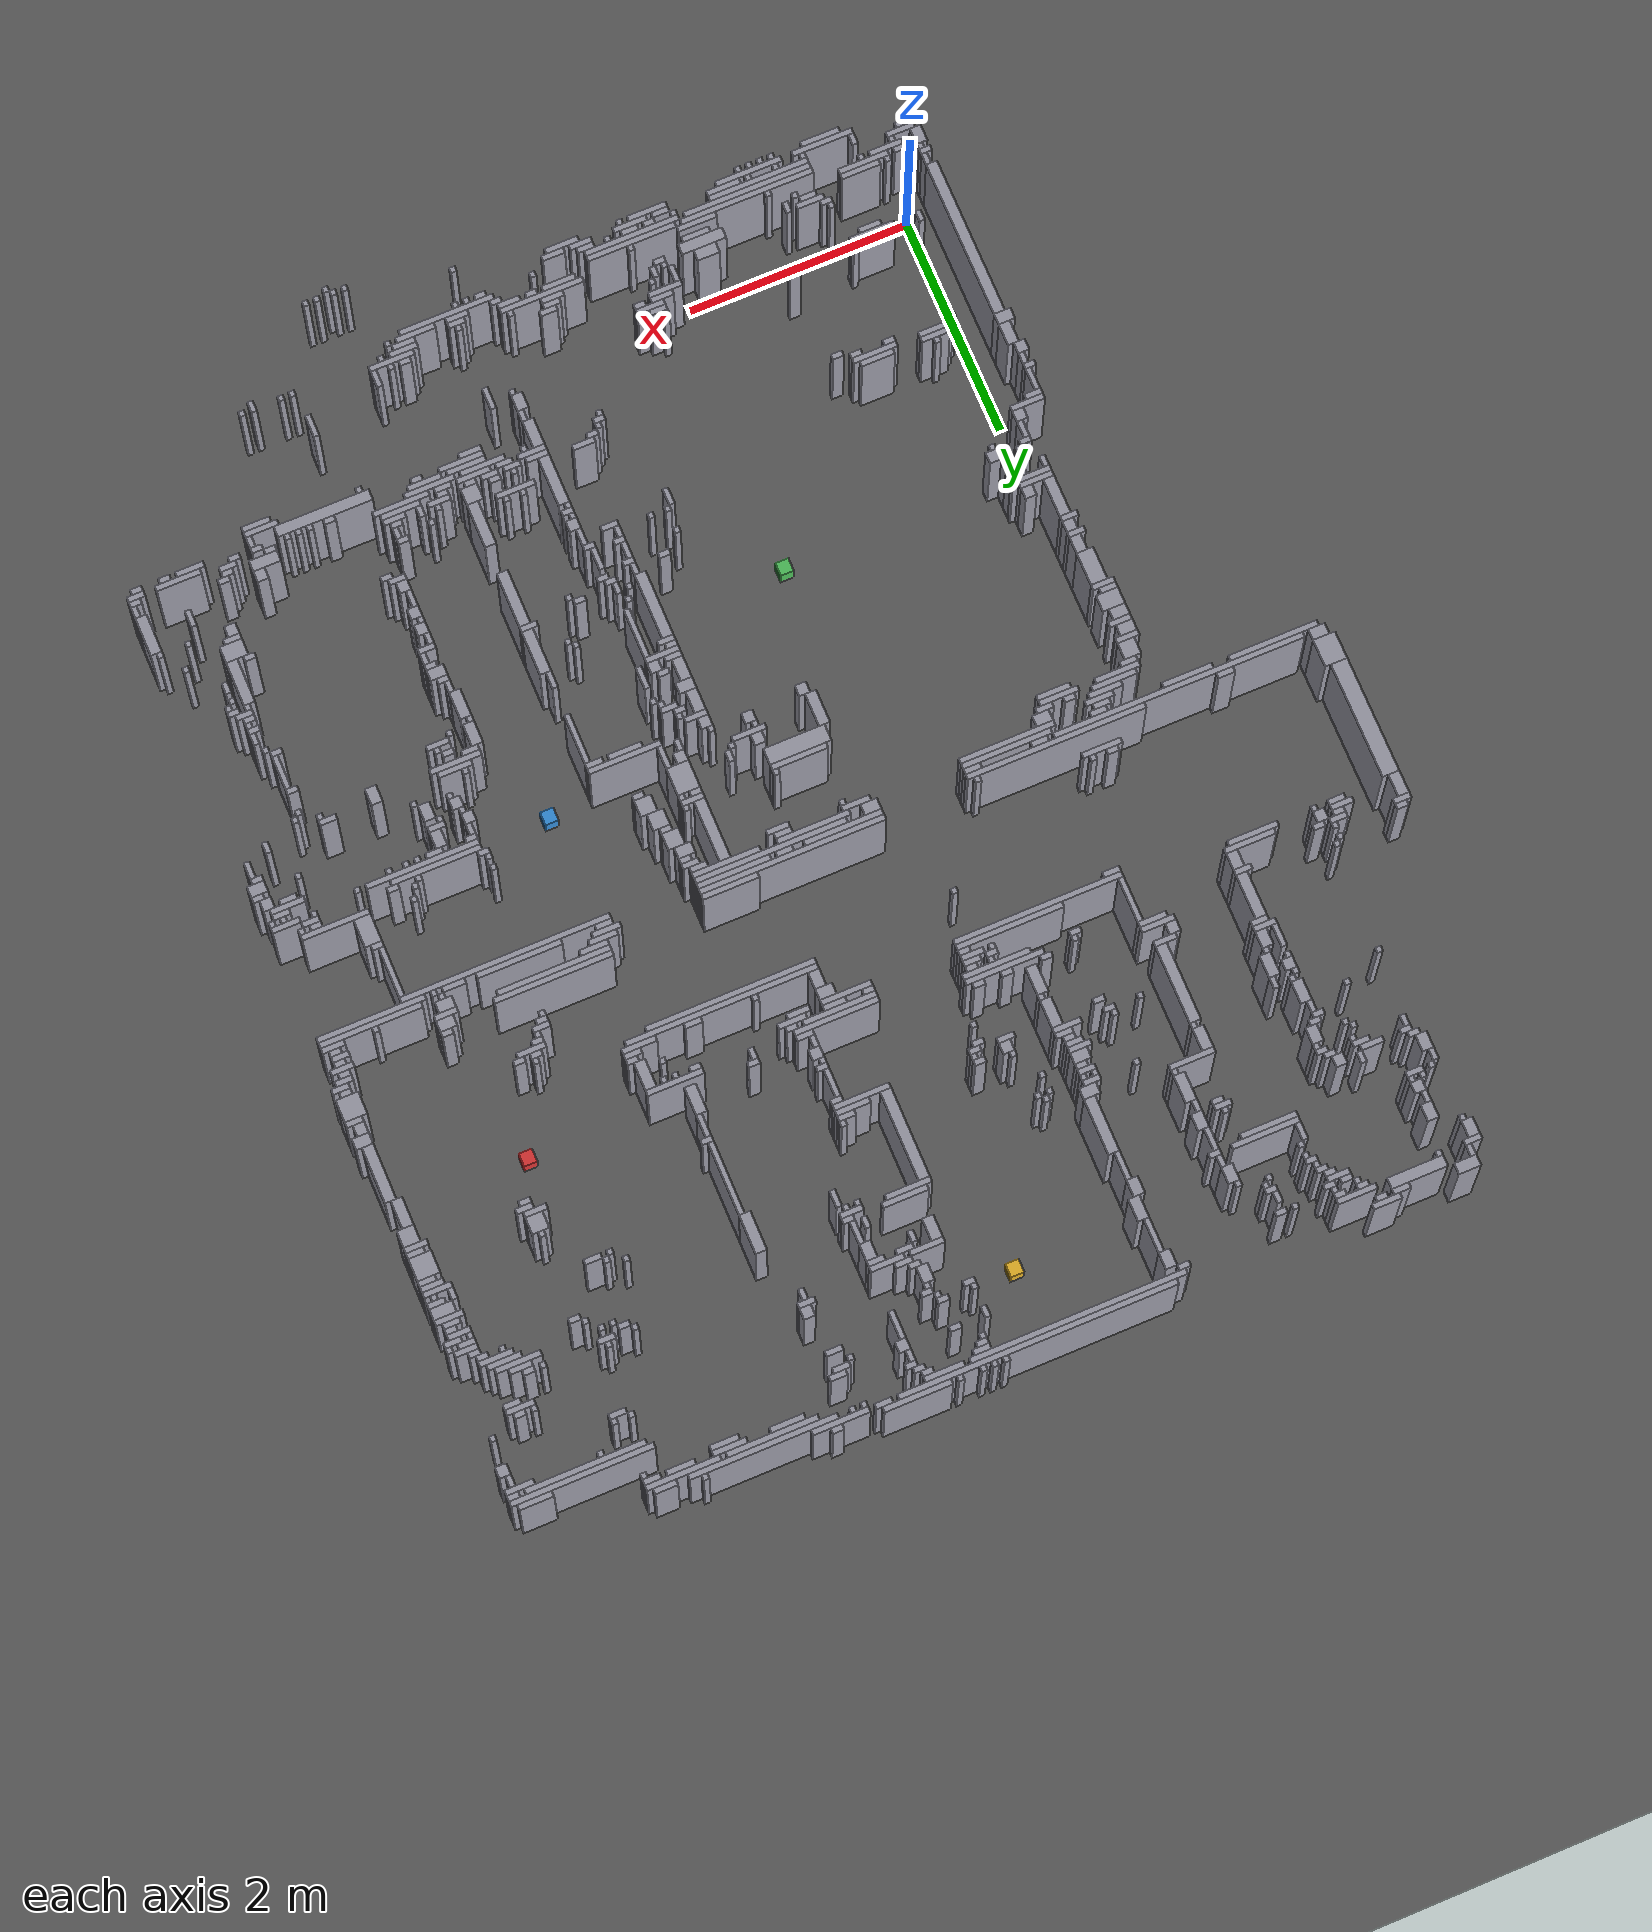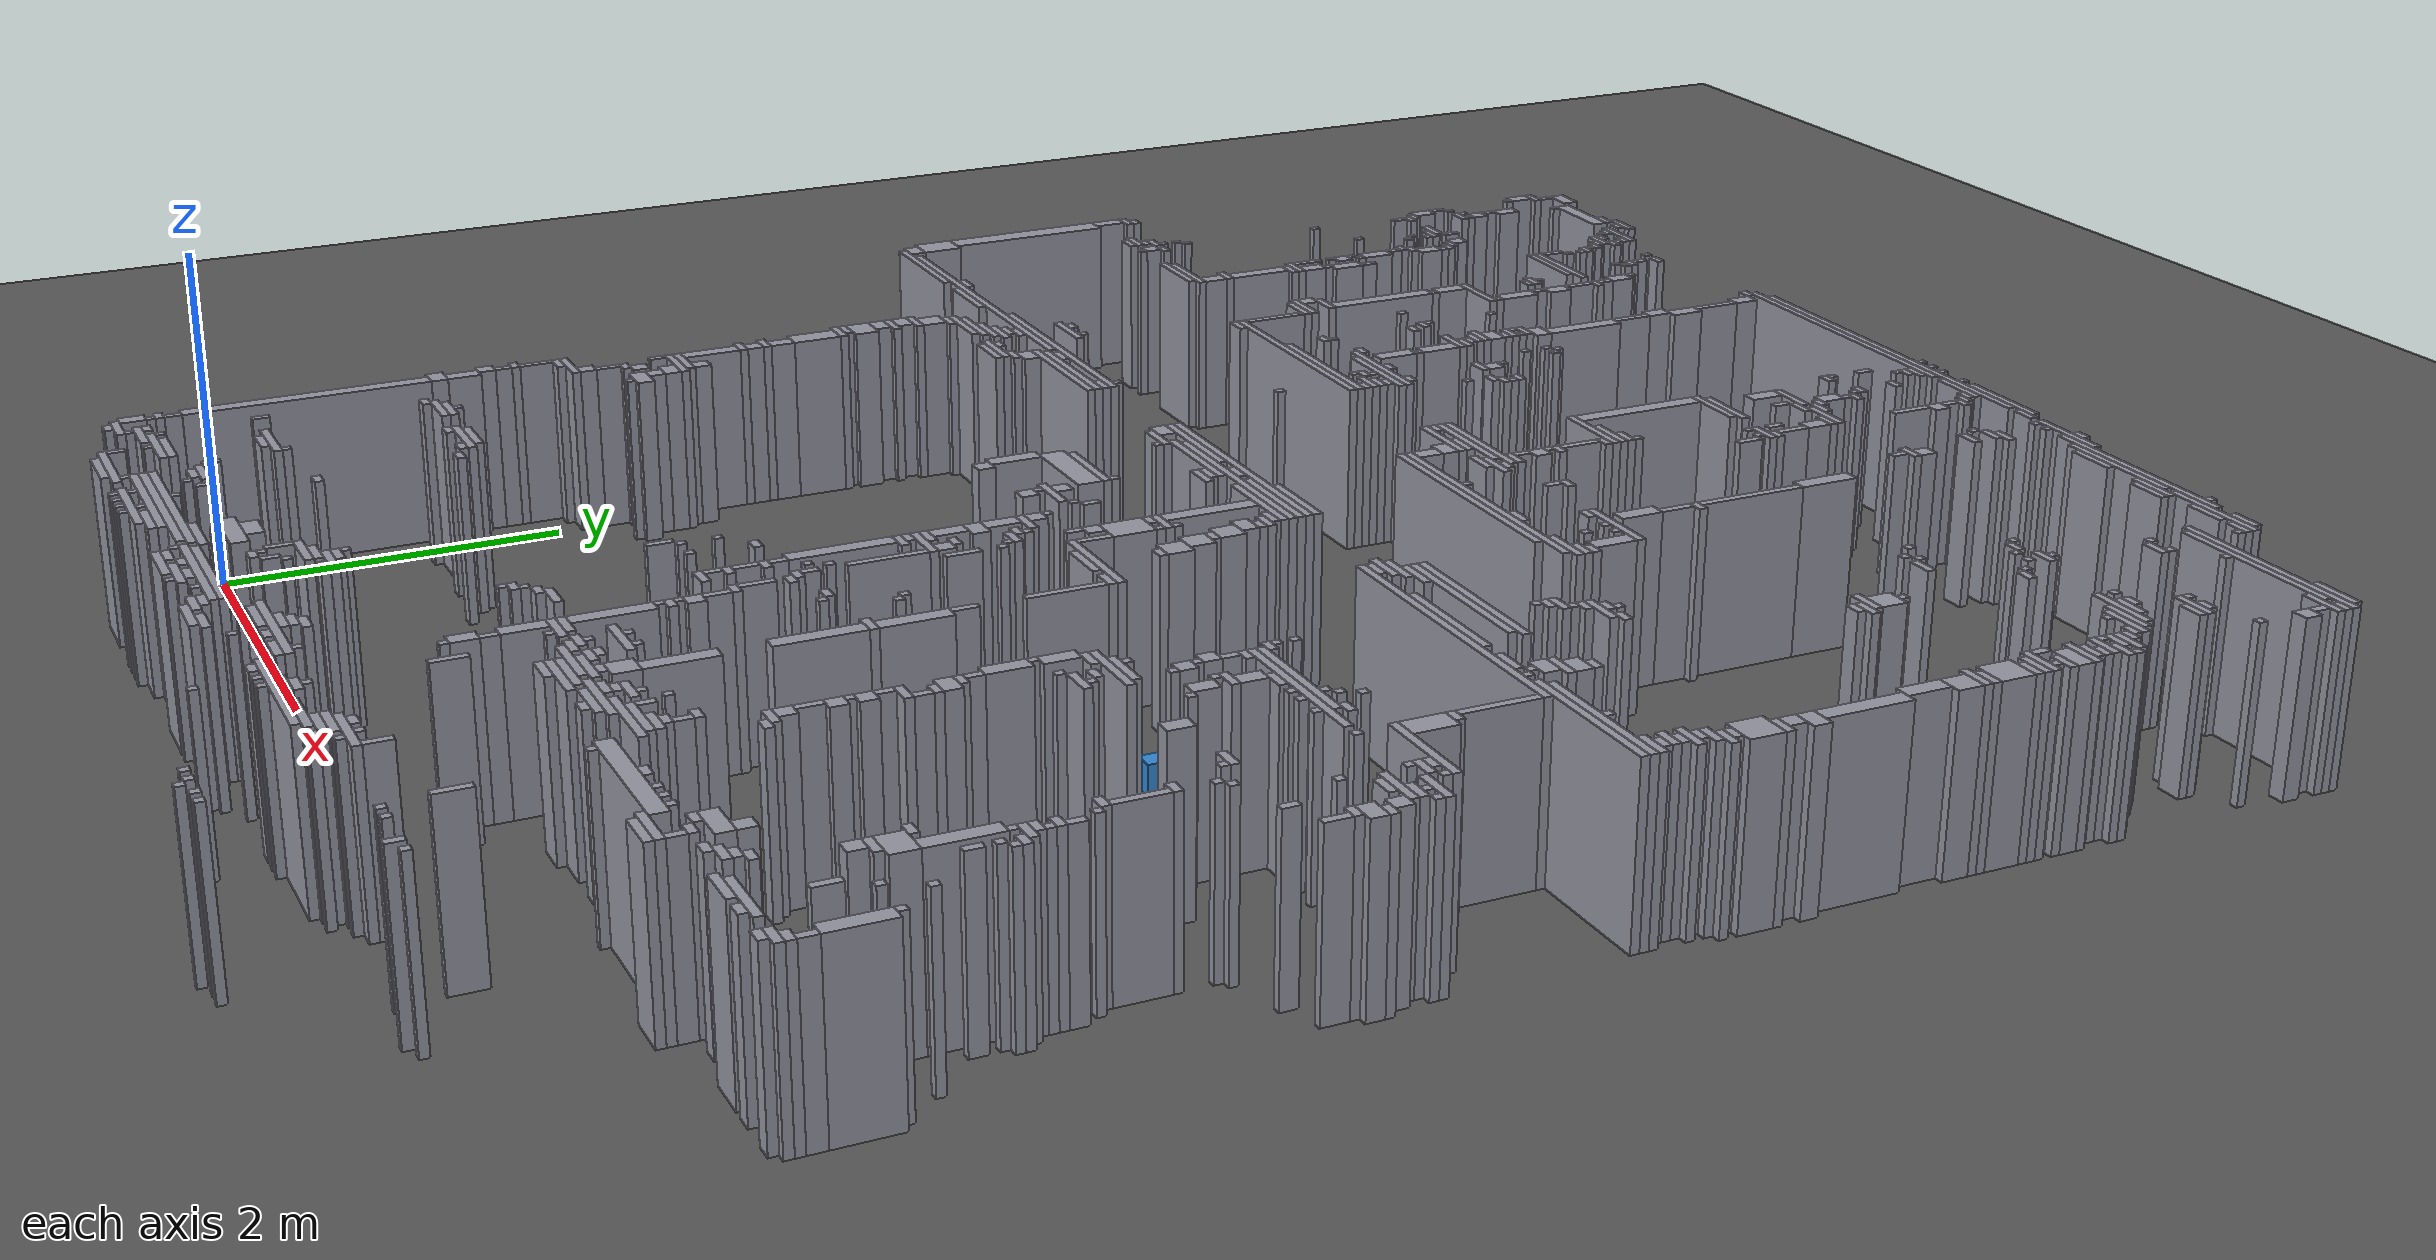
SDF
<?xml version="1.0"?>
<sdf version="1.8">
  <world name="dimi">
    <physics name="1ms" type="ignored">
      <max_step_size>0.004</max_step_size>
      <real_time_factor>1.0</real_time_factor>
    </physics>
    <plugin filename="gz-sim-physics-system" name="gz::sim::systems::Physics"/>
    <plugin filename="gz-sim-user-commands-system" name="gz::sim::systems::UserCommands"/>
    <plugin filename="gz-sim-scene-broadcaster-system" name="gz::sim::systems::SceneBroadcaster"/>
    <plugin filename="gz-sim-sensors-system" name="gz::sim::systems::Sensors">
      <render_engine>ogre2</render_engine>
    </plugin>

    <light type="directional" name="sun">
      <cast_shadows>false</cast_shadows>
      <pose>0 0 10 0 0 0</pose>
      <diffuse>0.9 0.9 0.9 1</diffuse>
      <direction>-0.3 0.2 -1</direction>
    </light>

    <model name="ground">
      <static>true</static>
      <link name="ground_link">
        <collision name="c"><geometry><plane><normal>0 0 1</normal><size>60 60</size></plane></geometry></collision>
        <visual name="v"><geometry><plane><normal>0 0 1</normal><size>60 60</size></plane></geometry>
          <material><ambient>0.3 0.3 0.3 1</ambient><diffuse>0.35 0.35 0.35 1</diffuse></material>
        </visual>
      </link>
    </model>

    <model name="walls">
      <static>true</static>
      <link name="wall_0">
        <pose>-0.8470 9.5420 0.5000 0 0 0</pose>
        <collision name="c">
          <geometry><box><size>0.2000 0.1000 1.0000</size></box></geometry>
        </collision>
        <visual name="v">
          <geometry><box><size>0.2000 0.1000 1.0000</size></box></geometry>
          <material><ambient>0.5 0.5 0.55 1</ambient><diffuse>0.6 0.6 0.65 1</diffuse></material>
        </visual>
      </link>
      <link name="wall_1">
        <pose>-0.1220 9.5670 0.5000 0 0 0</pose>
        <collision name="c">
          <geometry><box><size>0.2500 0.0500 1.0000</size></box></geometry>
        </collision>
        <visual name="v">
          <geometry><box><size>0.2500 0.0500 1.0000</size></box></geometry>
          <material><ambient>0.5 0.5 0.55 1</ambient><diffuse>0.6 0.6 0.65 1</diffuse></material>
        </visual>
      </link>
      <link name="wall_2">
        <pose>3.2280 9.5670 0.5000 0 0 0</pose>
        <collision name="c">
          <geometry><box><size>0.0500 0.0500 1.0000</size></box></geometry>
        </collision>
        <visual name="v">
          <geometry><box><size>0.0500 0.0500 1.0000</size></box></geometry>
          <material><ambient>0.5 0.5 0.55 1</ambient><diffuse>0.6 0.6 0.65 1</diffuse></material>
        </visual>
      </link>
      <link name="wall_3">
        <pose>3.3280 9.5670 0.5000 0 0 0</pose>
        <collision name="c">
          <geometry><box><size>0.0500 0.0500 1.0000</size></box></geometry>
        </collision>
        <visual name="v">
          <geometry><box><size>0.0500 0.0500 1.0000</size></box></geometry>
          <material><ambient>0.5 0.5 0.55 1</ambient><diffuse>0.6 0.6 0.65 1</diffuse></material>
        </visual>
      </link>
      <link name="wall_4">
        <pose>3.4280 9.5670 0.5000 0 0 0</pose>
        <collision name="c">
          <geometry><box><size>0.0500 0.0500 1.0000</size></box></geometry>
        </collision>
        <visual name="v">
          <geometry><box><size>0.0500 0.0500 1.0000</size></box></geometry>
          <material><ambient>0.5 0.5 0.55 1</ambient><diffuse>0.6 0.6 0.65 1</diffuse></material>
        </visual>
      </link>
      <link name="wall_5">
        <pose>3.6280 9.5670 0.5000 0 0 0</pose>
        <collision name="c">
          <geometry><box><size>0.0500 0.0500 1.0000</size></box></geometry>
        </collision>
        <visual name="v">
          <geometry><box><size>0.0500 0.0500 1.0000</size></box></geometry>
          <material><ambient>0.5 0.5 0.55 1</ambient><diffuse>0.6 0.6 0.65 1</diffuse></material>
        </visual>
      </link>
      <link name="wall_6">
        <pose>4.0030 9.5670 0.5000 0 0 0</pose>
        <collision name="c">
          <geometry><box><size>0.6000 0.0500 1.0000</size></box></geometry>
        </collision>
        <visual name="v">
          <geometry><box><size>0.6000 0.0500 1.0000</size></box></geometry>
          <material><ambient>0.5 0.5 0.55 1</ambient><diffuse>0.6 0.6 0.65 1</diffuse></material>
        </visual>
      </link>
      <link name="wall_7">
        <pose>4.7030 9.5670 0.5000 0 0 0</pose>
        <collision name="c">
          <geometry><box><size>0.1000 0.0500 1.0000</size></box></geometry>
        </collision>
        <visual name="v">
          <geometry><box><size>0.1000 0.0500 1.0000</size></box></geometry>
          <material><ambient>0.5 0.5 0.55 1</ambient><diffuse>0.6 0.6 0.65 1</diffuse></material>
        </visual>
      </link>
      <link name="wall_8">
        <pose>-0.2720 9.5170 0.5000 0 0 0</pose>
        <collision name="c">
          <geometry><box><size>0.1500 0.0500 1.0000</size></box></geometry>
        </collision>
        <visual name="v">
          <geometry><box><size>0.1500 0.0500 1.0000</size></box></geometry>
          <material><ambient>0.5 0.5 0.55 1</ambient><diffuse>0.6 0.6 0.65 1</diffuse></material>
        </visual>
      </link>
      <link name="wall_9">
        <pose>-0.0970 9.5170 0.5000 0 0 0</pose>
        <collision name="c">
          <geometry><box><size>0.1000 0.0500 1.0000</size></box></geometry>
        </collision>
        <visual name="v">
          <geometry><box><size>0.1000 0.0500 1.0000</size></box></geometry>
          <material><ambient>0.5 0.5 0.55 1</ambient><diffuse>0.6 0.6 0.65 1</diffuse></material>
        </visual>
      </link>
      <link name="wall_10">
        <pose>2.9280 9.5170 0.5000 0 0 0</pose>
        <collision name="c">
          <geometry><box><size>2.4500 0.0500 1.0000</size></box></geometry>
        </collision>
        <visual name="v">
          <geometry><box><size>2.4500 0.0500 1.0000</size></box></geometry>
          <material><ambient>0.5 0.5 0.55 1</ambient><diffuse>0.6 0.6 0.65 1</diffuse></material>
        </visual>
      </link>
      <link name="wall_11">
        <pose>4.2780 9.5170 0.5000 0 0 0</pose>
        <collision name="c">
          <geometry><box><size>0.1500 0.0500 1.0000</size></box></geometry>
        </collision>
        <visual name="v">
          <geometry><box><size>0.1500 0.0500 1.0000</size></box></geometry>
          <material><ambient>0.5 0.5 0.55 1</ambient><diffuse>0.6 0.6 0.65 1</diffuse></material>
        </visual>
      </link>
      <link name="wall_12">
        <pose>4.6530 9.5170 0.5000 0 0 0</pose>
        <collision name="c">
          <geometry><box><size>0.5000 0.0500 1.0000</size></box></geometry>
        </collision>
        <visual name="v">
          <geometry><box><size>0.5000 0.0500 1.0000</size></box></geometry>
          <material><ambient>0.5 0.5 0.55 1</ambient><diffuse>0.6 0.6 0.65 1</diffuse></material>
        </visual>
      </link>
      <link name="wall_13">
        <pose>5.8280 9.5170 0.5000 0 0 0</pose>
        <collision name="c">
          <geometry><box><size>0.0500 0.0500 1.0000</size></box></geometry>
        </collision>
        <visual name="v">
          <geometry><box><size>0.0500 0.0500 1.0000</size></box></geometry>
          <material><ambient>0.5 0.5 0.55 1</ambient><diffuse>0.6 0.6 0.65 1</diffuse></material>
        </visual>
      </link>
      <link name="wall_14">
        <pose>-0.9220 9.4420 0.5000 0 0 0</pose>
        <collision name="c">
          <geometry><box><size>0.0500 0.1000 1.0000</size></box></geometry>
        </collision>
        <visual name="v">
          <geometry><box><size>0.0500 0.1000 1.0000</size></box></geometry>
          <material><ambient>0.5 0.5 0.55 1</ambient><diffuse>0.6 0.6 0.65 1</diffuse></material>
        </visual>
      </link>
      <link name="wall_15">
        <pose>-0.4470 9.4420 0.5000 0 0 0</pose>
        <collision name="c">
          <geometry><box><size>0.5000 0.1000 1.0000</size></box></geometry>
        </collision>
        <visual name="v">
          <geometry><box><size>0.5000 0.1000 1.0000</size></box></geometry>
          <material><ambient>0.5 0.5 0.55 1</ambient><diffuse>0.6 0.6 0.65 1</diffuse></material>
        </visual>
      </link>
      <link name="wall_16">
        <pose>2.5530 9.4670 0.5000 0 0 0</pose>
        <collision name="c">
          <geometry><box><size>1.9000 0.0500 1.0000</size></box></geometry>
        </collision>
        <visual name="v">
          <geometry><box><size>1.9000 0.0500 1.0000</size></box></geometry>
          <material><ambient>0.5 0.5 0.55 1</ambient><diffuse>0.6 0.6 0.65 1</diffuse></material>
        </visual>
      </link>
      <link name="wall_17">
        <pose>3.7280 9.4670 0.5000 0 0 0</pose>
        <collision name="c">
          <geometry><box><size>0.3500 0.0500 1.0000</size></box></geometry>
        </collision>
        <visual name="v">
          <geometry><box><size>0.3500 0.0500 1.0000</size></box></geometry>
          <material><ambient>0.5 0.5 0.55 1</ambient><diffuse>0.6 0.6 0.65 1</diffuse></material>
        </visual>
      </link>
      <link name="wall_18">
        <pose>4.4280 9.4670 0.5000 0 0 0</pose>
        <collision name="c">
          <geometry><box><size>0.0500 0.0500 1.0000</size></box></geometry>
        </collision>
        <visual name="v">
          <geometry><box><size>0.0500 0.0500 1.0000</size></box></geometry>
          <material><ambient>0.5 0.5 0.55 1</ambient><diffuse>0.6 0.6 0.65 1</diffuse></material>
        </visual>
      </link>
      <link name="wall_19">
        <pose>4.5280 9.4670 0.5000 0 0 0</pose>
        <collision name="c">
          <geometry><box><size>0.0500 0.0500 1.0000</size></box></geometry>
        </collision>
        <visual name="v">
          <geometry><box><size>0.0500 0.0500 1.0000</size></box></geometry>
          <material><ambient>0.5 0.5 0.55 1</ambient><diffuse>0.6 0.6 0.65 1</diffuse></material>
        </visual>
      </link>
      <link name="wall_20">
        <pose>5.3030 9.4670 0.5000 0 0 0</pose>
        <collision name="c">
          <geometry><box><size>1.3000 0.0500 1.0000</size></box></geometry>
        </collision>
        <visual name="v">
          <geometry><box><size>1.3000 0.0500 1.0000</size></box></geometry>
          <material><ambient>0.5 0.5 0.55 1</ambient><diffuse>0.6 0.6 0.65 1</diffuse></material>
        </visual>
      </link>
      <link name="wall_21">
        <pose>6.1530 9.4670 0.5000 0 0 0</pose>
        <collision name="c">
          <geometry><box><size>0.2000 0.0500 1.0000</size></box></geometry>
        </collision>
        <visual name="v">
          <geometry><box><size>0.2000 0.0500 1.0000</size></box></geometry>
          <material><ambient>0.5 0.5 0.55 1</ambient><diffuse>0.6 0.6 0.65 1</diffuse></material>
        </visual>
      </link>
      <link name="wall_22">
        <pose>0.0780 9.4170 0.5000 0 0 0</pose>
        <collision name="c">
          <geometry><box><size>0.3500 0.0500 1.0000</size></box></geometry>
        </collision>
        <visual name="v">
          <geometry><box><size>0.3500 0.0500 1.0000</size></box></geometry>
          <material><ambient>0.5 0.5 0.55 1</ambient><diffuse>0.6 0.6 0.65 1</diffuse></material>
        </visual>
      </link>
      <link name="wall_23">
        <pose>1.6030 9.4170 0.5000 0 0 0</pose>
        <collision name="c">
          <geometry><box><size>0.1000 0.0500 1.0000</size></box></geometry>
        </collision>
        <visual name="v">
          <geometry><box><size>0.1000 0.0500 1.0000</size></box></geometry>
          <material><ambient>0.5 0.5 0.55 1</ambient><diffuse>0.6 0.6 0.65 1</diffuse></material>
        </visual>
      </link>
      <link name="wall_24">
        <pose>3.3780 9.4170 0.5000 0 0 0</pose>
        <collision name="c">
          <geometry><box><size>0.1500 0.0500 1.0000</size></box></geometry>
        </collision>
        <visual name="v">
          <geometry><box><size>0.1500 0.0500 1.0000</size></box></geometry>
          <material><ambient>0.5 0.5 0.55 1</ambient><diffuse>0.6 0.6 0.65 1</diffuse></material>
        </visual>
      </link>
      <link name="wall_25">
        <pose>3.8530 9.4170 0.5000 0 0 0</pose>
        <collision name="c">
          <geometry><box><size>0.1000 0.0500 1.0000</size></box></geometry>
        </collision>
        <visual name="v">
          <geometry><box><size>0.1000 0.0500 1.0000</size></box></geometry>
          <material><ambient>0.5 0.5 0.55 1</ambient><diffuse>0.6 0.6 0.65 1</diffuse></material>
        </visual>
      </link>
      <link name="wall_26">
        <pose>5.2030 9.4170 0.5000 0 0 0</pose>
        <collision name="c">
          <geometry><box><size>0.8000 0.0500 1.0000</size></box></geometry>
        </collision>
        <visual name="v">
          <geometry><box><size>0.8000 0.0500 1.0000</size></box></geometry>
          <material><ambient>0.5 0.5 0.55 1</ambient><diffuse>0.6 0.6 0.65 1</diffuse></material>
        </visual>
      </link>
      <link name="wall_27">
        <pose>5.9780 9.4170 0.5000 0 0 0</pose>
        <collision name="c">
          <geometry><box><size>0.6500 0.0500 1.0000</size></box></geometry>
        </collision>
        <visual name="v">
          <geometry><box><size>0.6500 0.0500 1.0000</size></box></geometry>
          <material><ambient>0.5 0.5 0.55 1</ambient><diffuse>0.6 0.6 0.65 1</diffuse></material>
        </visual>
      </link>
      <link name="wall_28">
        <pose>-0.9720 9.3670 0.5000 0 0 0</pose>
        <collision name="c">
          <geometry><box><size>0.1500 0.0500 1.0000</size></box></geometry>
        </collision>
        <visual name="v">
          <geometry><box><size>0.1500 0.0500 1.0000</size></box></geometry>
          <material><ambient>0.5 0.5 0.55 1</ambient><diffuse>0.6 0.6 0.65 1</diffuse></material>
        </visual>
      </link>
      <link name="wall_29">
        <pose>-0.6720 9.3670 0.5000 0 0 0</pose>
        <collision name="c">
          <geometry><box><size>0.0500 0.0500 1.0000</size></box></geometry>
        </collision>
        <visual name="v">
          <geometry><box><size>0.0500 0.0500 1.0000</size></box></geometry>
          <material><ambient>0.5 0.5 0.55 1</ambient><diffuse>0.6 0.6 0.65 1</diffuse></material>
        </visual>
      </link>
      <link name="wall_30">
        <pose>0.0030 9.3670 0.5000 0 0 0</pose>
        <collision name="c">
          <geometry><box><size>0.1000 0.0500 1.0000</size></box></geometry>
        </collision>
        <visual name="v">
          <geometry><box><size>0.1000 0.0500 1.0000</size></box></geometry>
          <material><ambient>0.5 0.5 0.55 1</ambient><diffuse>0.6 0.6 0.65 1</diffuse></material>
        </visual>
      </link>
      <link name="wall_31">
        <pose>0.2030 9.3670 0.5000 0 0 0</pose>
        <collision name="c">
          <geometry><box><size>0.1000 0.0500 1.0000</size></box></geometry>
        </collision>
        <visual name="v">
          <geometry><box><size>0.1000 0.0500 1.0000</size></box></geometry>
          <material><ambient>0.5 0.5 0.55 1</ambient><diffuse>0.6 0.6 0.65 1</diffuse></material>
        </visual>
      </link>
      <link name="wall_32">
        <pose>1.7030 9.3170 0.5000 0 0 0</pose>
        <collision name="c">
          <geometry><box><size>0.1000 0.1500 1.0000</size></box></geometry>
        </collision>
        <visual name="v">
          <geometry><box><size>0.1000 0.1500 1.0000</size></box></geometry>
          <material><ambient>0.5 0.5 0.55 1</ambient><diffuse>0.6 0.6 0.65 1</diffuse></material>
        </visual>
      </link>
      <link name="wall_33">
        <pose>3.3530 9.3670 0.5000 0 0 0</pose>
        <collision name="c">
          <geometry><box><size>0.1000 0.0500 1.0000</size></box></geometry>
        </collision>
        <visual name="v">
          <geometry><box><size>0.1000 0.0500 1.0000</size></box></geometry>
          <material><ambient>0.5 0.5 0.55 1</ambient><diffuse>0.6 0.6 0.65 1</diffuse></material>
        </visual>
      </link>
      <link name="wall_34">
        <pose>3.9030 9.3670 0.5000 0 0 0</pose>
        <collision name="c">
          <geometry><box><size>0.1000 0.0500 1.0000</size></box></geometry>
        </collision>
        <visual name="v">
          <geometry><box><size>0.1000 0.0500 1.0000</size></box></geometry>
          <material><ambient>0.5 0.5 0.55 1</ambient><diffuse>0.6 0.6 0.65 1</diffuse></material>
        </visual>
      </link>
      <link name="wall_35">
        <pose>5.0530 9.3670 0.5000 0 0 0</pose>
        <collision name="c">
          <geometry><box><size>0.3000 0.0500 1.0000</size></box></geometry>
        </collision>
        <visual name="v">
          <geometry><box><size>0.3000 0.0500 1.0000</size></box></geometry>
          <material><ambient>0.5 0.5 0.55 1</ambient><diffuse>0.6 0.6 0.65 1</diffuse></material>
        </visual>
      </link>
      <link name="wall_36">
        <pose>5.5530 9.3670 0.5000 0 0 0</pose>
        <collision name="c">
          <geometry><box><size>0.3000 0.0500 1.0000</size></box></geometry>
        </collision>
        <visual name="v">
          <geometry><box><size>0.3000 0.0500 1.0000</size></box></geometry>
          <material><ambient>0.5 0.5 0.55 1</ambient><diffuse>0.6 0.6 0.65 1</diffuse></material>
        </visual>
      </link>
      <link name="wall_37">
        <pose>5.9780 9.3670 0.5000 0 0 0</pose>
        <collision name="c">
          <geometry><box><size>0.2500 0.0500 1.0000</size></box></geometry>
        </collision>
        <visual name="v">
          <geometry><box><size>0.2500 0.0500 1.0000</size></box></geometry>
          <material><ambient>0.5 0.5 0.55 1</ambient><diffuse>0.6 0.6 0.65 1</diffuse></material>
        </visual>
      </link>
      <link name="wall_38">
        <pose>6.2280 9.3670 0.5000 0 0 0</pose>
        <collision name="c">
          <geometry><box><size>0.1500 0.0500 1.0000</size></box></geometry>
        </collision>
        <visual name="v">
          <geometry><box><size>0.1500 0.0500 1.0000</size></box></geometry>
          <material><ambient>0.5 0.5 0.55 1</ambient><diffuse>0.6 0.6 0.65 1</diffuse></material>
        </visual>
      </link>
      <link name="wall_39">
        <pose>-0.9970 9.2670 0.5000 0 0 0</pose>
        <collision name="c">
          <geometry><box><size>0.1000 0.1500 1.0000</size></box></geometry>
        </collision>
        <visual name="v">
          <geometry><box><size>0.1000 0.1500 1.0000</size></box></geometry>
          <material><ambient>0.5 0.5 0.55 1</ambient><diffuse>0.6 0.6 0.65 1</diffuse></material>
        </visual>
      </link>
      <link name="wall_40">
        <pose>0.0280 9.3170 0.5000 0 0 0</pose>
        <collision name="c">
          <geometry><box><size>0.0500 0.0500 1.0000</size></box></geometry>
        </collision>
        <visual name="v">
          <geometry><box><size>0.0500 0.0500 1.0000</size></box></geometry>
          <material><ambient>0.5 0.5 0.55 1</ambient><diffuse>0.6 0.6 0.65 1</diffuse></material>
        </visual>
      </link>
      <link name="wall_41">
        <pose>0.2280 9.3170 0.5000 0 0 0</pose>
        <collision name="c">
          <geometry><box><size>0.0500 0.0500 1.0000</size></box></geometry>
        </collision>
        <visual name="v">
          <geometry><box><size>0.0500 0.0500 1.0000</size></box></geometry>
          <material><ambient>0.5 0.5 0.55 1</ambient><diffuse>0.6 0.6 0.65 1</diffuse></material>
        </visual>
      </link>
      <link name="wall_42">
        <pose>0.5780 9.3170 0.5000 0 0 0</pose>
        <collision name="c">
          <geometry><box><size>0.0500 0.0500 1.0000</size></box></geometry>
        </collision>
        <visual name="v">
          <geometry><box><size>0.0500 0.0500 1.0000</size></box></geometry>
          <material><ambient>0.5 0.5 0.55 1</ambient><diffuse>0.6 0.6 0.65 1</diffuse></material>
        </visual>
      </link>
      <link name="wall_43">
        <pose>0.7030 9.3170 0.5000 0 0 0</pose>
        <collision name="c">
          <geometry><box><size>0.1000 0.0500 1.0000</size></box></geometry>
        </collision>
        <visual name="v">
          <geometry><box><size>0.1000 0.0500 1.0000</size></box></geometry>
          <material><ambient>0.5 0.5 0.55 1</ambient><diffuse>0.6 0.6 0.65 1</diffuse></material>
        </visual>
      </link>
      <link name="wall_44">
        <pose>3.3280 9.3170 0.5000 0 0 0</pose>
        <collision name="c">
          <geometry><box><size>0.0500 0.0500 1.0000</size></box></geometry>
        </collision>
        <visual name="v">
          <geometry><box><size>0.0500 0.0500 1.0000</size></box></geometry>
          <material><ambient>0.5 0.5 0.55 1</ambient><diffuse>0.6 0.6 0.65 1</diffuse></material>
        </visual>
      </link>
      <link name="wall_45">
        <pose>3.9530 9.3170 0.5000 0 0 0</pose>
        <collision name="c">
          <geometry><box><size>0.1000 0.0500 1.0000</size></box></geometry>
        </collision>
        <visual name="v">
          <geometry><box><size>0.1000 0.0500 1.0000</size></box></geometry>
          <material><ambient>0.5 0.5 0.55 1</ambient><diffuse>0.6 0.6 0.65 1</diffuse></material>
        </visual>
      </link>
      <link name="wall_46">
        <pose>5.5780 9.3170 0.5000 0 0 0</pose>
        <collision name="c">
          <geometry><box><size>0.2500 0.0500 1.0000</size></box></geometry>
        </collision>
        <visual name="v">
          <geometry><box><size>0.2500 0.0500 1.0000</size></box></geometry>
          <material><ambient>0.5 0.5 0.55 1</ambient><diffuse>0.6 0.6 0.65 1</diffuse></material>
        </visual>
      </link>
      <link name="wall_47">
        <pose>6.2780 9.3170 0.5000 0 0 0</pose>
        <collision name="c">
          <geometry><box><size>0.0500 0.0500 1.0000</size></box></geometry>
        </collision>
        <visual name="v">
          <geometry><box><size>0.0500 0.0500 1.0000</size></box></geometry>
          <material><ambient>0.5 0.5 0.55 1</ambient><diffuse>0.6 0.6 0.65 1</diffuse></material>
        </visual>
      </link>
      <link name="wall_48">
        <pose>0.1030 9.2670 0.5000 0 0 0</pose>
        <collision name="c">
          <geometry><box><size>0.1000 0.0500 1.0000</size></box></geometry>
        </collision>
        <visual name="v">
          <geometry><box><size>0.1000 0.0500 1.0000</size></box></geometry>
          <material><ambient>0.5 0.5 0.55 1</ambient><diffuse>0.6 0.6 0.65 1</diffuse></material>
        </visual>
      </link>
      <link name="wall_49">
        <pose>0.2530 9.2670 0.5000 0 0 0</pose>
        <collision name="c">
          <geometry><box><size>0.1000 0.0500 1.0000</size></box></geometry>
        </collision>
        <visual name="v">
          <geometry><box><size>0.1000 0.0500 1.0000</size></box></geometry>
          <material><ambient>0.5 0.5 0.55 1</ambient><diffuse>0.6 0.6 0.65 1</diffuse></material>
        </visual>
      </link>
      <link name="wall_50">
        <pose>3.9280 9.2420 0.5000 0 0 0</pose>
        <collision name="c">
          <geometry><box><size>0.0500 0.1000 1.0000</size></box></geometry>
        </collision>
        <visual name="v">
          <geometry><box><size>0.0500 0.1000 1.0000</size></box></geometry>
          <material><ambient>0.5 0.5 0.55 1</ambient><diffuse>0.6 0.6 0.65 1</diffuse></material>
        </visual>
      </link>
      <link name="wall_51">
        <pose>0.1530 9.2170 0.5000 0 0 0</pose>
        <collision name="c">
          <geometry><box><size>0.2000 0.0500 1.0000</size></box></geometry>
        </collision>
        <visual name="v">
          <geometry><box><size>0.2000 0.0500 1.0000</size></box></geometry>
          <material><ambient>0.5 0.5 0.55 1</ambient><diffuse>0.6 0.6 0.65 1</diffuse></material>
        </visual>
      </link>
      <link name="wall_52">
        <pose>0.6780 9.1920 0.5000 0 0 0</pose>
        <collision name="c">
          <geometry><box><size>0.0500 0.1000 1.0000</size></box></geometry>
        </collision>
        <visual name="v">
          <geometry><box><size>0.0500 0.1000 1.0000</size></box></geometry>
          <material><ambient>0.5 0.5 0.55 1</ambient><diffuse>0.6 0.6 0.65 1</diffuse></material>
        </visual>
      </link>
      <link name="wall_53">
        <pose>1.7280 9.0920 0.5000 0 0 0</pose>
        <collision name="c">
          <geometry><box><size>0.0500 0.3000 1.0000</size></box></geometry>
        </collision>
        <visual name="v">
          <geometry><box><size>0.0500 0.3000 1.0000</size></box></geometry>
          <material><ambient>0.5 0.5 0.55 1</ambient><diffuse>0.6 0.6 0.65 1</diffuse></material>
        </visual>
      </link>
      <link name="wall_54">
        <pose>-0.9720 9.1670 0.5000 0 0 0</pose>
        <collision name="c">
          <geometry><box><size>0.0500 0.0500 1.0000</size></box></geometry>
        </collision>
        <visual name="v">
          <geometry><box><size>0.0500 0.0500 1.0000</size></box></geometry>
          <material><ambient>0.5 0.5 0.55 1</ambient><diffuse>0.6 0.6 0.65 1</diffuse></material>
        </visual>
      </link>
      <link name="wall_55">
        <pose>0.2030 9.1670 0.5000 0 0 0</pose>
        <collision name="c">
          <geometry><box><size>0.1000 0.0500 1.0000</size></box></geometry>
        </collision>
        <visual name="v">
          <geometry><box><size>0.1000 0.0500 1.0000</size></box></geometry>
          <material><ambient>0.5 0.5 0.55 1</ambient><diffuse>0.6 0.6 0.65 1</diffuse></material>
        </visual>
      </link>
      <link name="wall_56">
        <pose>3.2280 9.1420 0.5000 0 0 0</pose>
        <collision name="c">
          <geometry><box><size>0.0500 0.1000 1.0000</size></box></geometry>
        </collision>
        <visual name="v">
          <geometry><box><size>0.0500 0.1000 1.0000</size></box></geometry>
          <material><ambient>0.5 0.5 0.55 1</ambient><diffuse>0.6 0.6 0.65 1</diffuse></material>
        </visual>
      </link>
      <link name="wall_57">
        <pose>3.5030 9.1670 0.5000 0 0 0</pose>
        <collision name="c">
          <geometry><box><size>0.1000 0.0500 1.0000</size></box></geometry>
        </collision>
        <visual name="v">
          <geometry><box><size>0.1000 0.0500 1.0000</size></box></geometry>
          <material><ambient>0.5 0.5 0.55 1</ambient><diffuse>0.6 0.6 0.65 1</diffuse></material>
        </visual>
      </link>
      <link name="wall_58">
        <pose>3.9530 9.1420 0.5000 0 0 0</pose>
        <collision name="c">
          <geometry><box><size>0.1000 0.1000 1.0000</size></box></geometry>
        </collision>
        <visual name="v">
          <geometry><box><size>0.1000 0.1000 1.0000</size></box></geometry>
          <material><ambient>0.5 0.5 0.55 1</ambient><diffuse>0.6 0.6 0.65 1</diffuse></material>
        </visual>
      </link>
      <link name="wall_59">
        <pose>4.5280 9.1670 0.5000 0 0 0</pose>
        <collision name="c">
          <geometry><box><size>0.1500 0.0500 1.0000</size></box></geometry>
        </collision>
        <visual name="v">
          <geometry><box><size>0.1500 0.0500 1.0000</size></box></geometry>
          <material><ambient>0.5 0.5 0.55 1</ambient><diffuse>0.6 0.6 0.65 1</diffuse></material>
        </visual>
      </link>
      <link name="wall_60">
        <pose>7.1530 9.1670 0.5000 0 0 0</pose>
        <collision name="c">
          <geometry><box><size>0.3000 0.0500 1.0000</size></box></geometry>
        </collision>
        <visual name="v">
          <geometry><box><size>0.3000 0.0500 1.0000</size></box></geometry>
          <material><ambient>0.5 0.5 0.55 1</ambient><diffuse>0.6 0.6 0.65 1</diffuse></material>
        </visual>
      </link>
      <link name="wall_61">
        <pose>0.2530 9.1170 0.5000 0 0 0</pose>
        <collision name="c">
          <geometry><box><size>0.1000 0.0500 1.0000</size></box></geometry>
        </collision>
        <visual name="v">
          <geometry><box><size>0.1000 0.0500 1.0000</size></box></geometry>
          <material><ambient>0.5 0.5 0.55 1</ambient><diffuse>0.6 0.6 0.65 1</diffuse></material>
        </visual>
      </link>
      <link name="wall_62">
        <pose>0.7030 9.1170 0.5000 0 0 0</pose>
        <collision name="c">
          <geometry><box><size>0.1000 0.0500 1.0000</size></box></geometry>
        </collision>
        <visual name="v">
          <geometry><box><size>0.1000 0.0500 1.0000</size></box></geometry>
          <material><ambient>0.5 0.5 0.55 1</ambient><diffuse>0.6 0.6 0.65 1</diffuse></material>
        </visual>
      </link>
      <link name="wall_63">
        <pose>4.4780 9.1170 0.5000 0 0 0</pose>
        <collision name="c">
          <geometry><box><size>0.1500 0.0500 1.0000</size></box></geometry>
        </collision>
        <visual name="v">
          <geometry><box><size>0.1500 0.0500 1.0000</size></box></geometry>
          <material><ambient>0.5 0.5 0.55 1</ambient><diffuse>0.6 0.6 0.65 1</diffuse></material>
        </visual>
      </link>
      <link name="wall_64">
        <pose>6.7280 9.1170 0.5000 0 0 0</pose>
        <collision name="c">
          <geometry><box><size>1.2500 0.0500 1.0000</size></box></geometry>
        </collision>
        <visual name="v">
          <geometry><box><size>1.2500 0.0500 1.0000</size></box></geometry>
          <material><ambient>0.5 0.5 0.55 1</ambient><diffuse>0.6 0.6 0.65 1</diffuse></material>
        </visual>
      </link>
      <link name="wall_65">
        <pose>-0.7470 9.0170 0.5000 0 0 0</pose>
        <collision name="c">
          <geometry><box><size>0.1000 0.1500 1.0000</size></box></geometry>
        </collision>
        <visual name="v">
          <geometry><box><size>0.1000 0.1500 1.0000</size></box></geometry>
          <material><ambient>0.5 0.5 0.55 1</ambient><diffuse>0.6 0.6 0.65 1</diffuse></material>
        </visual>
      </link>
      <link name="wall_66">
        <pose>0.2780 9.0670 0.5000 0 0 0</pose>
        <collision name="c">
          <geometry><box><size>0.0500 0.0500 1.0000</size></box></geometry>
        </collision>
        <visual name="v">
          <geometry><box><size>0.0500 0.0500 1.0000</size></box></geometry>
          <material><ambient>0.5 0.5 0.55 1</ambient><diffuse>0.6 0.6 0.65 1</diffuse></material>
        </visual>
      </link>
      <link name="wall_67">
        <pose>0.7280 9.0670 0.5000 0 0 0</pose>
        <collision name="c">
          <geometry><box><size>0.0500 0.0500 1.0000</size></box></geometry>
        </collision>
        <visual name="v">
          <geometry><box><size>0.0500 0.0500 1.0000</size></box></geometry>
          <material><ambient>0.5 0.5 0.55 1</ambient><diffuse>0.6 0.6 0.65 1</diffuse></material>
        </visual>
      </link>
      <link name="wall_68">
        <pose>3.9280 8.9670 0.5000 0 0 0</pose>
        <collision name="c">
          <geometry><box><size>0.0500 0.2500 1.0000</size></box></geometry>
        </collision>
        <visual name="v">
          <geometry><box><size>0.0500 0.2500 1.0000</size></box></geometry>
          <material><ambient>0.5 0.5 0.55 1</ambient><diffuse>0.6 0.6 0.65 1</diffuse></material>
        </visual>
      </link>
      <link name="wall_69">
        <pose>4.3780 9.0670 0.5000 0 0 0</pose>
        <collision name="c">
          <geometry><box><size>0.0500 0.0500 1.0000</size></box></geometry>
        </collision>
        <visual name="v">
          <geometry><box><size>0.0500 0.0500 1.0000</size></box></geometry>
          <material><ambient>0.5 0.5 0.55 1</ambient><diffuse>0.6 0.6 0.65 1</diffuse></material>
        </visual>
      </link>
      <link name="wall_70">
        <pose>6.6780 9.0670 0.5000 0 0 0</pose>
        <collision name="c">
          <geometry><box><size>1.0500 0.0500 1.0000</size></box></geometry>
        </collision>
        <visual name="v">
          <geometry><box><size>1.0500 0.0500 1.0000</size></box></geometry>
          <material><ambient>0.5 0.5 0.55 1</ambient><diffuse>0.6 0.6 0.65 1</diffuse></material>
        </visual>
      </link>
      <link name="wall_71">
        <pose>7.3030 9.0670 0.5000 0 0 0</pose>
        <collision name="c">
          <geometry><box><size>0.1000 0.0500 1.0000</size></box></geometry>
        </collision>
        <visual name="v">
          <geometry><box><size>0.1000 0.0500 1.0000</size></box></geometry>
          <material><ambient>0.5 0.5 0.55 1</ambient><diffuse>0.6 0.6 0.65 1</diffuse></material>
        </visual>
      </link>
      <link name="wall_72">
        <pose>0.3030 9.0170 0.5000 0 0 0</pose>
        <collision name="c">
          <geometry><box><size>0.1000 0.0500 1.0000</size></box></geometry>
        </collision>
        <visual name="v">
          <geometry><box><size>0.1000 0.0500 1.0000</size></box></geometry>
          <material><ambient>0.5 0.5 0.55 1</ambient><diffuse>0.6 0.6 0.65 1</diffuse></material>
        </visual>
      </link>
      <link name="wall_73">
        <pose>0.6780 9.0170 0.5000 0 0 0</pose>
        <collision name="c">
          <geometry><box><size>0.0500 0.0500 1.0000</size></box></geometry>
        </collision>
        <visual name="v">
          <geometry><box><size>0.0500 0.0500 1.0000</size></box></geometry>
          <material><ambient>0.5 0.5 0.55 1</ambient><diffuse>0.6 0.6 0.65 1</diffuse></material>
        </visual>
      </link>
      <link name="wall_74">
        <pose>6.5280 9.0170 0.5000 0 0 0</pose>
        <collision name="c">
          <geometry><box><size>0.0500 0.0500 1.0000</size></box></geometry>
        </collision>
        <visual name="v">
          <geometry><box><size>0.0500 0.0500 1.0000</size></box></geometry>
          <material><ambient>0.5 0.5 0.55 1</ambient><diffuse>0.6 0.6 0.65 1</diffuse></material>
        </visual>
      </link>
      <link name="wall_75">
        <pose>7.2280 9.0170 0.5000 0 0 0</pose>
        <collision name="c">
          <geometry><box><size>0.2500 0.0500 1.0000</size></box></geometry>
        </collision>
        <visual name="v">
          <geometry><box><size>0.2500 0.0500 1.0000</size></box></geometry>
          <material><ambient>0.5 0.5 0.55 1</ambient><diffuse>0.6 0.6 0.65 1</diffuse></material>
        </visual>
      </link>
      <link name="wall_76">
        <pose>0.3280 8.9670 0.5000 0 0 0</pose>
        <collision name="c">
          <geometry><box><size>0.0500 0.0500 1.0000</size></box></geometry>
        </collision>
        <visual name="v">
          <geometry><box><size>0.0500 0.0500 1.0000</size></box></geometry>
          <material><ambient>0.5 0.5 0.55 1</ambient><diffuse>0.6 0.6 0.65 1</diffuse></material>
        </visual>
      </link>
      <link name="wall_77">
        <pose>0.9280 8.9670 0.5000 0 0 0</pose>
        <collision name="c">
          <geometry><box><size>0.0500 0.0500 1.0000</size></box></geometry>
        </collision>
        <visual name="v">
          <geometry><box><size>0.0500 0.0500 1.0000</size></box></geometry>
          <material><ambient>0.5 0.5 0.55 1</ambient><diffuse>0.6 0.6 0.65 1</diffuse></material>
        </visual>
      </link>
      <link name="wall_78">
        <pose>4.4780 8.9670 0.5000 0 0 0</pose>
        <collision name="c">
          <geometry><box><size>0.1500 0.0500 1.0000</size></box></geometry>
        </collision>
        <visual name="v">
          <geometry><box><size>0.1500 0.0500 1.0000</size></box></geometry>
          <material><ambient>0.5 0.5 0.55 1</ambient><diffuse>0.6 0.6 0.65 1</diffuse></material>
        </visual>
      </link>
      <link name="wall_79">
        <pose>7.2780 8.9420 0.5000 0 0 0</pose>
        <collision name="c">
          <geometry><box><size>0.0500 0.1000 1.0000</size></box></geometry>
        </collision>
        <visual name="v">
          <geometry><box><size>0.0500 0.1000 1.0000</size></box></geometry>
          <material><ambient>0.5 0.5 0.55 1</ambient><diffuse>0.6 0.6 0.65 1</diffuse></material>
        </visual>
      </link>
      <link name="wall_80">
        <pose>-0.7720 8.8920 0.5000 0 0 0</pose>
        <collision name="c">
          <geometry><box><size>0.0500 0.1000 1.0000</size></box></geometry>
        </collision>
        <visual name="v">
          <geometry><box><size>0.0500 0.1000 1.0000</size></box></geometry>
          <material><ambient>0.5 0.5 0.55 1</ambient><diffuse>0.6 0.6 0.65 1</diffuse></material>
        </visual>
      </link>
      <link name="wall_81">
        <pose>0.9530 8.8670 0.5000 0 0 0</pose>
        <collision name="c">
          <geometry><box><size>0.1000 0.1500 1.0000</size></box></geometry>
        </collision>
        <visual name="v">
          <geometry><box><size>0.1000 0.1500 1.0000</size></box></geometry>
          <material><ambient>0.5 0.5 0.55 1</ambient><diffuse>0.6 0.6 0.65 1</diffuse></material>
        </visual>
      </link>
      <link name="wall_82">
        <pose>1.7530 8.8420 0.5000 0 0 0</pose>
        <collision name="c">
          <geometry><box><size>0.1000 0.2000 1.0000</size></box></geometry>
        </collision>
        <visual name="v">
          <geometry><box><size>0.1000 0.2000 1.0000</size></box></geometry>
          <material><ambient>0.5 0.5 0.55 1</ambient><diffuse>0.6 0.6 0.65 1</diffuse></material>
        </visual>
      </link>
      <link name="wall_83">
        <pose>3.2280 8.9170 0.5000 0 0 0</pose>
        <collision name="c">
          <geometry><box><size>0.0500 0.0500 1.0000</size></box></geometry>
        </collision>
        <visual name="v">
          <geometry><box><size>0.0500 0.0500 1.0000</size></box></geometry>
          <material><ambient>0.5 0.5 0.55 1</ambient><diffuse>0.6 0.6 0.65 1</diffuse></material>
        </visual>
      </link>
      <link name="wall_84">
        <pose>3.5030 8.9170 0.5000 0 0 0</pose>
        <collision name="c">
          <geometry><box><size>0.1000 0.0500 1.0000</size></box></geometry>
        </collision>
        <visual name="v">
          <geometry><box><size>0.1000 0.0500 1.0000</size></box></geometry>
          <material><ambient>0.5 0.5 0.55 1</ambient><diffuse>0.6 0.6 0.65 1</diffuse></material>
        </visual>
      </link>
      <link name="wall_85">
        <pose>0.3280 8.8670 0.5000 0 0 0</pose>
        <collision name="c">
          <geometry><box><size>0.0500 0.0500 1.0000</size></box></geometry>
        </collision>
        <visual name="v">
          <geometry><box><size>0.0500 0.0500 1.0000</size></box></geometry>
          <material><ambient>0.5 0.5 0.55 1</ambient><diffuse>0.6 0.6 0.65 1</diffuse></material>
        </visual>
      </link>
      <link name="wall_86">
        <pose>3.2530 8.8670 0.5000 0 0 0</pose>
        <collision name="c">
          <geometry><box><size>0.1000 0.0500 1.0000</size></box></geometry>
        </collision>
        <visual name="v">
          <geometry><box><size>0.1000 0.0500 1.0000</size></box></geometry>
          <material><ambient>0.5 0.5 0.55 1</ambient><diffuse>0.6 0.6 0.65 1</diffuse></material>
        </visual>
      </link>
      <link name="wall_87">
        <pose>3.5280 8.8670 0.5000 0 0 0</pose>
        <collision name="c">
          <geometry><box><size>0.0500 0.0500 1.0000</size></box></geometry>
        </collision>
        <visual name="v">
          <geometry><box><size>0.0500 0.0500 1.0000</size></box></geometry>
          <material><ambient>0.5 0.5 0.55 1</ambient><diffuse>0.6 0.6 0.65 1</diffuse></material>
        </visual>
      </link>
      <link name="wall_88">
        <pose>7.3030 8.8420 0.5000 0 0 0</pose>
        <collision name="c">
          <geometry><box><size>0.1000 0.1000 1.0000</size></box></geometry>
        </collision>
        <visual name="v">
          <geometry><box><size>0.1000 0.1000 1.0000</size></box></geometry>
          <material><ambient>0.5 0.5 0.55 1</ambient><diffuse>0.6 0.6 0.65 1</diffuse></material>
        </visual>
      </link>
      <link name="wall_89">
        <pose>-0.7470 8.7920 0.5000 0 0 0</pose>
        <collision name="c">
          <geometry><box><size>0.1000 0.1000 1.0000</size></box></geometry>
        </collision>
        <visual name="v">
          <geometry><box><size>0.1000 0.1000 1.0000</size></box></geometry>
          <material><ambient>0.5 0.5 0.55 1</ambient><diffuse>0.6 0.6 0.65 1</diffuse></material>
        </visual>
      </link>
      <link name="wall_90">
        <pose>0.2780 8.7670 0.5000 0 0 0</pose>
        <collision name="c">
          <geometry><box><size>0.0500 0.1500 1.0000</size></box></geometry>
        </collision>
        <visual name="v">
          <geometry><box><size>0.0500 0.1500 1.0000</size></box></geometry>
          <material><ambient>0.5 0.5 0.55 1</ambient><diffuse>0.6 0.6 0.65 1</diffuse></material>
        </visual>
      </link>
      <link name="wall_91">
        <pose>3.6030 8.8170 0.5000 0 0 0</pose>
        <collision name="c">
          <geometry><box><size>0.1000 0.0500 1.0000</size></box></geometry>
        </collision>
        <visual name="v">
          <geometry><box><size>0.1000 0.0500 1.0000</size></box></geometry>
          <material><ambient>0.5 0.5 0.55 1</ambient><diffuse>0.6 0.6 0.65 1</diffuse></material>
        </visual>
      </link>
      <link name="wall_92">
        <pose>6.1780 8.8170 0.5000 0 0 0</pose>
        <collision name="c">
          <geometry><box><size>0.0500 0.0500 1.0000</size></box></geometry>
        </collision>
        <visual name="v">
          <geometry><box><size>0.0500 0.0500 1.0000</size></box></geometry>
          <material><ambient>0.5 0.5 0.55 1</ambient><diffuse>0.6 0.6 0.65 1</diffuse></material>
        </visual>
      </link>
      <link name="wall_93">
        <pose>6.3280 8.8170 0.5000 0 0 0</pose>
        <collision name="c">
          <geometry><box><size>0.0500 0.0500 1.0000</size></box></geometry>
        </collision>
        <visual name="v">
          <geometry><box><size>0.0500 0.0500 1.0000</size></box></geometry>
          <material><ambient>0.5 0.5 0.55 1</ambient><diffuse>0.6 0.6 0.65 1</diffuse></material>
        </visual>
      </link>
      <link name="wall_94">
        <pose>0.9780 8.7420 0.5000 0 0 0</pose>
        <collision name="c">
          <geometry><box><size>0.0500 0.1000 1.0000</size></box></geometry>
        </collision>
        <visual name="v">
          <geometry><box><size>0.0500 0.1000 1.0000</size></box></geometry>
          <material><ambient>0.5 0.5 0.55 1</ambient><diffuse>0.6 0.6 0.65 1</diffuse></material>
        </visual>
      </link>
      <link name="wall_95">
        <pose>3.5780 8.7670 0.5000 0 0 0</pose>
        <collision name="c">
          <geometry><box><size>0.0500 0.0500 1.0000</size></box></geometry>
        </collision>
        <visual name="v">
          <geometry><box><size>0.0500 0.0500 1.0000</size></box></geometry>
          <material><ambient>0.5 0.5 0.55 1</ambient><diffuse>0.6 0.6 0.65 1</diffuse></material>
        </visual>
      </link>
      <link name="wall_96">
        <pose>6.2780 8.7670 0.5000 0 0 0</pose>
        <collision name="c">
          <geometry><box><size>0.1500 0.0500 1.0000</size></box></geometry>
        </collision>
        <visual name="v">
          <geometry><box><size>0.1500 0.0500 1.0000</size></box></geometry>
          <material><ambient>0.5 0.5 0.55 1</ambient><diffuse>0.6 0.6 0.65 1</diffuse></material>
        </visual>
      </link>
      <link name="wall_97">
        <pose>-0.8220 8.7170 0.5000 0 0 0</pose>
        <collision name="c">
          <geometry><box><size>0.0500 0.0500 1.0000</size></box></geometry>
        </collision>
        <visual name="v">
          <geometry><box><size>0.0500 0.0500 1.0000</size></box></geometry>
          <material><ambient>0.5 0.5 0.55 1</ambient><diffuse>0.6 0.6 0.65 1</diffuse></material>
        </visual>
      </link>
      <link name="wall_98">
        <pose>-0.7220 8.7170 0.5000 0 0 0</pose>
        <collision name="c">
          <geometry><box><size>0.0500 0.0500 1.0000</size></box></geometry>
        </collision>
        <visual name="v">
          <geometry><box><size>0.0500 0.0500 1.0000</size></box></geometry>
          <material><ambient>0.5 0.5 0.55 1</ambient><diffuse>0.6 0.6 0.65 1</diffuse></material>
        </visual>
      </link>
      <link name="wall_99">
        <pose>1.7030 8.6670 0.5000 0 0 0</pose>
        <collision name="c">
          <geometry><box><size>0.1000 0.1500 1.0000</size></box></geometry>
        </collision>
        <visual name="v">
          <geometry><box><size>0.1000 0.1500 1.0000</size></box></geometry>
          <material><ambient>0.5 0.5 0.55 1</ambient><diffuse>0.6 0.6 0.65 1</diffuse></material>
        </visual>
      </link>
      <link name="wall_100">
        <pose>3.5530 8.6670 0.5000 0 0 0</pose>
        <collision name="c">
          <geometry><box><size>0.1000 0.1500 1.0000</size></box></geometry>
        </collision>
        <visual name="v">
          <geometry><box><size>0.1000 0.1500 1.0000</size></box></geometry>
          <material><ambient>0.5 0.5 0.55 1</ambient><diffuse>0.6 0.6 0.65 1</diffuse></material>
        </visual>
      </link>
      <link name="wall_101">
        <pose>-0.9220 8.6670 0.5000 0 0 0</pose>
        <collision name="c">
          <geometry><box><size>0.0500 0.0500 1.0000</size></box></geometry>
        </collision>
        <visual name="v">
          <geometry><box><size>0.0500 0.0500 1.0000</size></box></geometry>
          <material><ambient>0.5 0.5 0.55 1</ambient><diffuse>0.6 0.6 0.65 1</diffuse></material>
        </visual>
      </link>
      <link name="wall_102">
        <pose>-0.7720 8.6670 0.5000 0 0 0</pose>
        <collision name="c">
          <geometry><box><size>0.1500 0.0500 1.0000</size></box></geometry>
        </collision>
        <visual name="v">
          <geometry><box><size>0.1500 0.0500 1.0000</size></box></geometry>
          <material><ambient>0.5 0.5 0.55 1</ambient><diffuse>0.6 0.6 0.65 1</diffuse></material>
        </visual>
      </link>
      <link name="wall_103">
        <pose>0.5530 8.6670 0.5000 0 0 0</pose>
        <collision name="c">
          <geometry><box><size>0.6000 0.0500 1.0000</size></box></geometry>
        </collision>
        <visual name="v">
          <geometry><box><size>0.6000 0.0500 1.0000</size></box></geometry>
          <material><ambient>0.5 0.5 0.55 1</ambient><diffuse>0.6 0.6 0.65 1</diffuse></material>
        </visual>
      </link>
      <link name="wall_104">
        <pose>1.0030 8.6670 0.5000 0 0 0</pose>
        <collision name="c">
          <geometry><box><size>0.1000 0.0500 1.0000</size></box></geometry>
        </collision>
        <visual name="v">
          <geometry><box><size>0.1000 0.0500 1.0000</size></box></geometry>
          <material><ambient>0.5 0.5 0.55 1</ambient><diffuse>0.6 0.6 0.65 1</diffuse></material>
        </visual>
      </link>
      <link name="wall_105">
        <pose>-0.9720 8.5920 0.5000 0 0 0</pose>
        <collision name="c">
          <geometry><box><size>0.0500 0.1000 1.0000</size></box></geometry>
        </collision>
        <visual name="v">
          <geometry><box><size>0.0500 0.1000 1.0000</size></box></geometry>
          <material><ambient>0.5 0.5 0.55 1</ambient><diffuse>0.6 0.6 0.65 1</diffuse></material>
        </visual>
      </link>
      <link name="wall_106">
        <pose>0.5030 8.6170 0.5000 0 0 0</pose>
        <collision name="c">
          <geometry><box><size>0.5000 0.0500 1.0000</size></box></geometry>
        </collision>
        <visual name="v">
          <geometry><box><size>0.5000 0.0500 1.0000</size></box></geometry>
          <material><ambient>0.5 0.5 0.55 1</ambient><diffuse>0.6 0.6 0.65 1</diffuse></material>
        </visual>
      </link>
      <link name="wall_107">
        <pose>0.9780 8.5420 0.5000 0 0 0</pose>
        <collision name="c">
          <geometry><box><size>0.0500 0.2000 1.0000</size></box></geometry>
        </collision>
        <visual name="v">
          <geometry><box><size>0.0500 0.2000 1.0000</size></box></geometry>
          <material><ambient>0.5 0.5 0.55 1</ambient><diffuse>0.6 0.6 0.65 1</diffuse></material>
        </visual>
      </link>
      <link name="wall_108">
        <pose>4.5530 8.5920 0.5000 0 0 0</pose>
        <collision name="c">
          <geometry><box><size>0.1000 0.1000 1.0000</size></box></geometry>
        </collision>
        <visual name="v">
          <geometry><box><size>0.1000 0.1000 1.0000</size></box></geometry>
          <material><ambient>0.5 0.5 0.55 1</ambient><diffuse>0.6 0.6 0.65 1</diffuse></material>
        </visual>
      </link>
      <link name="wall_109">
        <pose>1.7280 8.4670 0.5000 0 0 0</pose>
        <collision name="c">
          <geometry><box><size>0.0500 0.2500 1.0000</size></box></geometry>
        </collision>
        <visual name="v">
          <geometry><box><size>0.0500 0.2500 1.0000</size></box></geometry>
          <material><ambient>0.5 0.5 0.55 1</ambient><diffuse>0.6 0.6 0.65 1</diffuse></material>
        </visual>
      </link>
      <link name="wall_110">
        <pose>3.6030 8.5670 0.5000 0 0 0</pose>
        <collision name="c">
          <geometry><box><size>0.1000 0.0500 1.0000</size></box></geometry>
        </collision>
        <visual name="v">
          <geometry><box><size>0.1000 0.0500 1.0000</size></box></geometry>
          <material><ambient>0.5 0.5 0.55 1</ambient><diffuse>0.6 0.6 0.65 1</diffuse></material>
        </visual>
      </link>
      <link name="wall_111">
        <pose>7.2780 8.5670 0.5000 0 0 0</pose>
        <collision name="c">
          <geometry><box><size>0.0500 0.0500 1.0000</size></box></geometry>
        </collision>
        <visual name="v">
          <geometry><box><size>0.0500 0.0500 1.0000</size></box></geometry>
          <material><ambient>0.5 0.5 0.55 1</ambient><diffuse>0.6 0.6 0.65 1</diffuse></material>
        </visual>
      </link>
      <link name="wall_112">
        <pose>-0.9470 8.4670 0.5000 0 0 0</pose>
        <collision name="c">
          <geometry><box><size>0.1000 0.1500 1.0000</size></box></geometry>
        </collision>
        <visual name="v">
          <geometry><box><size>0.1000 0.1500 1.0000</size></box></geometry>
          <material><ambient>0.5 0.5 0.55 1</ambient><diffuse>0.6 0.6 0.65 1</diffuse></material>
        </visual>
      </link>
      <link name="wall_113">
        <pose>3.6780 8.5170 0.5000 0 0 0</pose>
        <collision name="c">
          <geometry><box><size>0.1500 0.0500 1.0000</size></box></geometry>
        </collision>
        <visual name="v">
          <geometry><box><size>0.1500 0.0500 1.0000</size></box></geometry>
          <material><ambient>0.5 0.5 0.55 1</ambient><diffuse>0.6 0.6 0.65 1</diffuse></material>
        </visual>
      </link>
      <link name="wall_114">
        <pose>4.5280 8.5170 0.5000 0 0 0</pose>
        <collision name="c">
          <geometry><box><size>0.1500 0.0500 1.0000</size></box></geometry>
        </collision>
        <visual name="v">
          <geometry><box><size>0.1500 0.0500 1.0000</size></box></geometry>
          <material><ambient>0.5 0.5 0.55 1</ambient><diffuse>0.6 0.6 0.65 1</diffuse></material>
        </visual>
      </link>
      <link name="wall_115">
        <pose>3.4530 8.4670 0.5000 0 0 0</pose>
        <collision name="c">
          <geometry><box><size>0.3000 0.0500 1.0000</size></box></geometry>
        </collision>
        <visual name="v">
          <geometry><box><size>0.3000 0.0500 1.0000</size></box></geometry>
          <material><ambient>0.5 0.5 0.55 1</ambient><diffuse>0.6 0.6 0.65 1</diffuse></material>
        </visual>
      </link>
      <link name="wall_116">
        <pose>3.8030 8.4670 0.5000 0 0 0</pose>
        <collision name="c">
          <geometry><box><size>0.3000 0.0500 1.0000</size></box></geometry>
        </collision>
        <visual name="v">
          <geometry><box><size>0.3000 0.0500 1.0000</size></box></geometry>
          <material><ambient>0.5 0.5 0.55 1</ambient><diffuse>0.6 0.6 0.65 1</diffuse></material>
        </visual>
      </link>
      <link name="wall_117">
        <pose>4.5280 8.4420 0.5000 0 0 0</pose>
        <collision name="c">
          <geometry><box><size>0.0500 0.1000 1.0000</size></box></geometry>
        </collision>
        <visual name="v">
          <geometry><box><size>0.0500 0.1000 1.0000</size></box></geometry>
          <material><ambient>0.5 0.5 0.55 1</ambient><diffuse>0.6 0.6 0.65 1</diffuse></material>
        </visual>
      </link>
      <link name="wall_118">
        <pose>6.8780 8.4670 0.5000 0 0 0</pose>
        <collision name="c">
          <geometry><box><size>0.0500 0.0500 1.0000</size></box></geometry>
        </collision>
        <visual name="v">
          <geometry><box><size>0.0500 0.0500 1.0000</size></box></geometry>
          <material><ambient>0.5 0.5 0.55 1</ambient><diffuse>0.6 0.6 0.65 1</diffuse></material>
        </visual>
      </link>
      <link name="wall_119">
        <pose>7.0030 8.4670 0.5000 0 0 0</pose>
        <collision name="c">
          <geometry><box><size>0.1000 0.0500 1.0000</size></box></geometry>
        </collision>
        <visual name="v">
          <geometry><box><size>0.1000 0.0500 1.0000</size></box></geometry>
          <material><ambient>0.5 0.5 0.55 1</ambient><diffuse>0.6 0.6 0.65 1</diffuse></material>
        </visual>
      </link>
      <link name="wall_120">
        <pose>-0.4220 8.3920 0.5000 0 0 0</pose>
        <collision name="c">
          <geometry><box><size>0.0500 0.1000 1.0000</size></box></geometry>
        </collision>
        <visual name="v">
          <geometry><box><size>0.0500 0.1000 1.0000</size></box></geometry>
          <material><ambient>0.5 0.5 0.55 1</ambient><diffuse>0.6 0.6 0.65 1</diffuse></material>
        </visual>
      </link>
      <link name="wall_121">
        <pose>1.0030 8.3670 0.5000 0 0 0</pose>
        <collision name="c">
          <geometry><box><size>0.1000 0.1500 1.0000</size></box></geometry>
        </collision>
        <visual name="v">
          <geometry><box><size>0.1000 0.1500 1.0000</size></box></geometry>
          <material><ambient>0.5 0.5 0.55 1</ambient><diffuse>0.6 0.6 0.65 1</diffuse></material>
        </visual>
      </link>
      <link name="wall_122">
        <pose>3.3530 8.3420 0.5000 0 0 0</pose>
        <collision name="c">
          <geometry><box><size>0.1000 0.2000 1.0000</size></box></geometry>
        </collision>
        <visual name="v">
          <geometry><box><size>0.1000 0.2000 1.0000</size></box></geometry>
          <material><ambient>0.5 0.5 0.55 1</ambient><diffuse>0.6 0.6 0.65 1</diffuse></material>
        </visual>
      </link>
      <link name="wall_123">
        <pose>3.6280 8.4170 0.5000 0 0 0</pose>
        <collision name="c">
          <geometry><box><size>0.1500 0.0500 1.0000</size></box></geometry>
        </collision>
        <visual name="v">
          <geometry><box><size>0.1500 0.0500 1.0000</size></box></geometry>
          <material><ambient>0.5 0.5 0.55 1</ambient><diffuse>0.6 0.6 0.65 1</diffuse></material>
        </visual>
      </link>
      <link name="wall_124">
        <pose>3.8780 8.4170 0.5000 0 0 0</pose>
        <collision name="c">
          <geometry><box><size>0.1500 0.0500 1.0000</size></box></geometry>
        </collision>
        <visual name="v">
          <geometry><box><size>0.1500 0.0500 1.0000</size></box></geometry>
          <material><ambient>0.5 0.5 0.55 1</ambient><diffuse>0.6 0.6 0.65 1</diffuse></material>
        </visual>
      </link>
      <link name="wall_125">
        <pose>6.9780 8.4170 0.5000 0 0 0</pose>
        <collision name="c">
          <geometry><box><size>0.2500 0.0500 1.0000</size></box></geometry>
        </collision>
        <visual name="v">
          <geometry><box><size>0.2500 0.0500 1.0000</size></box></geometry>
          <material><ambient>0.5 0.5 0.55 1</ambient><diffuse>0.6 0.6 0.65 1</diffuse></material>
        </visual>
      </link>
      <link name="wall_126">
        <pose>-0.8970 8.3670 0.5000 0 0 0</pose>
        <collision name="c">
          <geometry><box><size>0.1000 0.0500 1.0000</size></box></geometry>
        </collision>
        <visual name="v">
          <geometry><box><size>0.1000 0.0500 1.0000</size></box></geometry>
          <material><ambient>0.5 0.5 0.55 1</ambient><diffuse>0.6 0.6 0.65 1</diffuse></material>
        </visual>
      </link>
      <link name="wall_127">
        <pose>-0.2470 8.3420 0.5000 0 0 0</pose>
        <collision name="c">
          <geometry><box><size>0.1000 0.1000 1.0000</size></box></geometry>
        </collision>
        <visual name="v">
          <geometry><box><size>0.1000 0.1000 1.0000</size></box></geometry>
          <material><ambient>0.5 0.5 0.55 1</ambient><diffuse>0.6 0.6 0.65 1</diffuse></material>
        </visual>
      </link>
      <link name="wall_128">
        <pose>0.7780 8.3670 0.5000 0 0 0</pose>
        <collision name="c">
          <geometry><box><size>0.0500 0.0500 1.0000</size></box></geometry>
        </collision>
        <visual name="v">
          <geometry><box><size>0.0500 0.0500 1.0000</size></box></geometry>
          <material><ambient>0.5 0.5 0.55 1</ambient><diffuse>0.6 0.6 0.65 1</diffuse></material>
        </visual>
      </link>
      <link name="wall_129">
        <pose>3.5280 8.3420 0.5000 0 0 0</pose>
        <collision name="c">
          <geometry><box><size>0.0500 0.1000 1.0000</size></box></geometry>
        </collision>
        <visual name="v">
          <geometry><box><size>0.0500 0.1000 1.0000</size></box></geometry>
          <material><ambient>0.5 0.5 0.55 1</ambient><diffuse>0.6 0.6 0.65 1</diffuse></material>
        </visual>
      </link>
      <link name="wall_130">
        <pose>3.9030 8.3170 0.5000 0 0 0</pose>
        <collision name="c">
          <geometry><box><size>0.1000 0.1500 1.0000</size></box></geometry>
        </collision>
        <visual name="v">
          <geometry><box><size>0.1000 0.1500 1.0000</size></box></geometry>
          <material><ambient>0.5 0.5 0.55 1</ambient><diffuse>0.6 0.6 0.65 1</diffuse></material>
        </visual>
      </link>
      <link name="wall_131">
        <pose>7.0280 8.3670 0.5000 0 0 0</pose>
        <collision name="c">
          <geometry><box><size>0.1500 0.0500 1.0000</size></box></geometry>
        </collision>
        <visual name="v">
          <geometry><box><size>0.1500 0.0500 1.0000</size></box></geometry>
          <material><ambient>0.5 0.5 0.55 1</ambient><diffuse>0.6 0.6 0.65 1</diffuse></material>
        </visual>
      </link>
      <link name="wall_132">
        <pose>-0.8470 8.3170 0.5000 0 0 0</pose>
        <collision name="c">
          <geometry><box><size>0.1000 0.0500 1.0000</size></box></geometry>
        </collision>
        <visual name="v">
          <geometry><box><size>0.1000 0.0500 1.0000</size></box></geometry>
          <material><ambient>0.5 0.5 0.55 1</ambient><diffuse>0.6 0.6 0.65 1</diffuse></material>
        </visual>
      </link>
      <link name="wall_133">
        <pose>-0.5470 8.3170 0.5000 0 0 0</pose>
        <collision name="c">
          <geometry><box><size>0.2000 0.0500 1.0000</size></box></geometry>
        </collision>
        <visual name="v">
          <geometry><box><size>0.2000 0.0500 1.0000</size></box></geometry>
          <material><ambient>0.5 0.5 0.55 1</ambient><diffuse>0.6 0.6 0.65 1</diffuse></material>
        </visual>
      </link>
      <link name="wall_134">
        <pose>0.7780 8.3170 0.5000 0 0 0</pose>
        <collision name="c">
          <geometry><box><size>0.1500 0.0500 1.0000</size></box></geometry>
        </collision>
        <visual name="v">
          <geometry><box><size>0.1500 0.0500 1.0000</size></box></geometry>
          <material><ambient>0.5 0.5 0.55 1</ambient><diffuse>0.6 0.6 0.65 1</diffuse></material>
        </visual>
      </link>
      <link name="wall_135">
        <pose>1.7530 8.0920 0.5000 0 0 0</pose>
        <collision name="c">
          <geometry><box><size>0.1000 0.5000 1.0000</size></box></geometry>
        </collision>
        <visual name="v">
          <geometry><box><size>0.1000 0.5000 1.0000</size></box></geometry>
          <material><ambient>0.5 0.5 0.55 1</ambient><diffuse>0.6 0.6 0.65 1</diffuse></material>
        </visual>
      </link>
      <link name="wall_136">
        <pose>-0.8720 8.2420 0.5000 0 0 0</pose>
        <collision name="c">
          <geometry><box><size>0.0500 0.1000 1.0000</size></box></geometry>
        </collision>
        <visual name="v">
          <geometry><box><size>0.0500 0.1000 1.0000</size></box></geometry>
          <material><ambient>0.5 0.5 0.55 1</ambient><diffuse>0.6 0.6 0.65 1</diffuse></material>
        </visual>
      </link>
      <link name="wall_137">
        <pose>-0.4720 8.2670 0.5000 0 0 0</pose>
        <collision name="c">
          <geometry><box><size>0.1500 0.0500 1.0000</size></box></geometry>
        </collision>
        <visual name="v">
          <geometry><box><size>0.1500 0.0500 1.0000</size></box></geometry>
          <material><ambient>0.5 0.5 0.55 1</ambient><diffuse>0.6 0.6 0.65 1</diffuse></material>
        </visual>
      </link>
      <link name="wall_138">
        <pose>-0.1970 8.2670 0.5000 0 0 0</pose>
        <collision name="c">
          <geometry><box><size>0.1000 0.0500 1.0000</size></box></geometry>
        </collision>
        <visual name="v">
          <geometry><box><size>0.1000 0.0500 1.0000</size></box></geometry>
          <material><ambient>0.5 0.5 0.55 1</ambient><diffuse>0.6 0.6 0.65 1</diffuse></material>
        </visual>
      </link>
      <link name="wall_139">
        <pose>0.8030 8.2670 0.5000 0 0 0</pose>
        <collision name="c">
          <geometry><box><size>0.1000 0.0500 1.0000</size></box></geometry>
        </collision>
        <visual name="v">
          <geometry><box><size>0.1000 0.0500 1.0000</size></box></geometry>
          <material><ambient>0.5 0.5 0.55 1</ambient><diffuse>0.6 0.6 0.65 1</diffuse></material>
        </visual>
      </link>
      <link name="wall_140">
        <pose>0.9780 8.2420 0.5000 0 0 0</pose>
        <collision name="c">
          <geometry><box><size>0.0500 0.1000 1.0000</size></box></geometry>
        </collision>
        <visual name="v">
          <geometry><box><size>0.0500 0.1000 1.0000</size></box></geometry>
          <material><ambient>0.5 0.5 0.55 1</ambient><diffuse>0.6 0.6 0.65 1</diffuse></material>
        </visual>
      </link>
      <link name="wall_141">
        <pose>-0.4220 8.2170 0.5000 0 0 0</pose>
        <collision name="c">
          <geometry><box><size>0.0500 0.0500 1.0000</size></box></geometry>
        </collision>
        <visual name="v">
          <geometry><box><size>0.0500 0.0500 1.0000</size></box></geometry>
          <material><ambient>0.5 0.5 0.55 1</ambient><diffuse>0.6 0.6 0.65 1</diffuse></material>
        </visual>
      </link>
      <link name="wall_142">
        <pose>-0.1470 8.2170 0.5000 0 0 0</pose>
        <collision name="c">
          <geometry><box><size>0.1000 0.0500 1.0000</size></box></geometry>
        </collision>
        <visual name="v">
          <geometry><box><size>0.1000 0.0500 1.0000</size></box></geometry>
          <material><ambient>0.5 0.5 0.55 1</ambient><diffuse>0.6 0.6 0.65 1</diffuse></material>
        </visual>
      </link>
      <link name="wall_143">
        <pose>3.9280 8.1420 0.5000 0 0 0</pose>
        <collision name="c">
          <geometry><box><size>0.0500 0.2000 1.0000</size></box></geometry>
        </collision>
        <visual name="v">
          <geometry><box><size>0.0500 0.2000 1.0000</size></box></geometry>
          <material><ambient>0.5 0.5 0.55 1</ambient><diffuse>0.6 0.6 0.65 1</diffuse></material>
        </visual>
      </link>
      <link name="wall_144">
        <pose>6.1280 8.2170 0.5000 0 0 0</pose>
        <collision name="c">
          <geometry><box><size>0.0500 0.0500 1.0000</size></box></geometry>
        </collision>
        <visual name="v">
          <geometry><box><size>0.0500 0.0500 1.0000</size></box></geometry>
          <material><ambient>0.5 0.5 0.55 1</ambient><diffuse>0.6 0.6 0.65 1</diffuse></material>
        </visual>
      </link>
      <link name="wall_145">
        <pose>-0.1220 8.1670 0.5000 0 0 0</pose>
        <collision name="c">
          <geometry><box><size>0.0500 0.0500 1.0000</size></box></geometry>
        </collision>
        <visual name="v">
          <geometry><box><size>0.0500 0.0500 1.0000</size></box></geometry>
          <material><ambient>0.5 0.5 0.55 1</ambient><diffuse>0.6 0.6 0.65 1</diffuse></material>
        </visual>
      </link>
      <link name="wall_146">
        <pose>1.0030 8.0670 0.5000 0 0 0</pose>
        <collision name="c">
          <geometry><box><size>0.1000 0.2500 1.0000</size></box></geometry>
        </collision>
        <visual name="v">
          <geometry><box><size>0.1000 0.2500 1.0000</size></box></geometry>
          <material><ambient>0.5 0.5 0.55 1</ambient><diffuse>0.6 0.6 0.65 1</diffuse></material>
        </visual>
      </link>
      <link name="wall_147">
        <pose>5.8780 8.1670 0.5000 0 0 0</pose>
        <collision name="c">
          <geometry><box><size>0.0500 0.0500 1.0000</size></box></geometry>
        </collision>
        <visual name="v">
          <geometry><box><size>0.0500 0.0500 1.0000</size></box></geometry>
          <material><ambient>0.5 0.5 0.55 1</ambient><diffuse>0.6 0.6 0.65 1</diffuse></material>
        </visual>
      </link>
      <link name="wall_148">
        <pose>6.1280 8.1670 0.5000 0 0 0</pose>
        <collision name="c">
          <geometry><box><size>0.1500 0.0500 1.0000</size></box></geometry>
        </collision>
        <visual name="v">
          <geometry><box><size>0.1500 0.0500 1.0000</size></box></geometry>
          <material><ambient>0.5 0.5 0.55 1</ambient><diffuse>0.6 0.6 0.65 1</diffuse></material>
        </visual>
      </link>
      <link name="wall_149">
        <pose>6.6780 8.1670 0.5000 0 0 0</pose>
        <collision name="c">
          <geometry><box><size>0.0500 0.0500 1.0000</size></box></geometry>
        </collision>
        <visual name="v">
          <geometry><box><size>0.0500 0.0500 1.0000</size></box></geometry>
          <material><ambient>0.5 0.5 0.55 1</ambient><diffuse>0.6 0.6 0.65 1</diffuse></material>
        </visual>
      </link>
      <link name="wall_150">
        <pose>6.8030 8.1670 0.5000 0 0 0</pose>
        <collision name="c">
          <geometry><box><size>0.1000 0.0500 1.0000</size></box></geometry>
        </collision>
        <visual name="v">
          <geometry><box><size>0.1000 0.0500 1.0000</size></box></geometry>
          <material><ambient>0.5 0.5 0.55 1</ambient><diffuse>0.6 0.6 0.65 1</diffuse></material>
        </visual>
      </link>
      <link name="wall_151">
        <pose>-0.4720 8.1170 0.5000 0 0 0</pose>
        <collision name="c">
          <geometry><box><size>0.0500 0.0500 1.0000</size></box></geometry>
        </collision>
        <visual name="v">
          <geometry><box><size>0.0500 0.0500 1.0000</size></box></geometry>
          <material><ambient>0.5 0.5 0.55 1</ambient><diffuse>0.6 0.6 0.65 1</diffuse></material>
        </visual>
      </link>
      <link name="wall_152">
        <pose>-0.1470 8.0670 0.5000 0 0 0</pose>
        <collision name="c">
          <geometry><box><size>0.1000 0.1500 1.0000</size></box></geometry>
        </collision>
        <visual name="v">
          <geometry><box><size>0.1000 0.1500 1.0000</size></box></geometry>
          <material><ambient>0.5 0.5 0.55 1</ambient><diffuse>0.6 0.6 0.65 1</diffuse></material>
        </visual>
      </link>
      <link name="wall_153">
        <pose>3.8280 8.0920 0.5000 0 0 0</pose>
        <collision name="c">
          <geometry><box><size>0.0500 0.1000 1.0000</size></box></geometry>
        </collision>
        <visual name="v">
          <geometry><box><size>0.0500 0.1000 1.0000</size></box></geometry>
          <material><ambient>0.5 0.5 0.55 1</ambient><diffuse>0.6 0.6 0.65 1</diffuse></material>
        </visual>
      </link>
      <link name="wall_154">
        <pose>5.9530 8.1170 0.5000 0 0 0</pose>
        <collision name="c">
          <geometry><box><size>0.1000 0.0500 1.0000</size></box></geometry>
        </collision>
        <visual name="v">
          <geometry><box><size>0.1000 0.0500 1.0000</size></box></geometry>
          <material><ambient>0.5 0.5 0.55 1</ambient><diffuse>0.6 0.6 0.65 1</diffuse></material>
        </visual>
      </link>
      <link name="wall_155">
        <pose>6.8530 8.1170 0.5000 0 0 0</pose>
        <collision name="c">
          <geometry><box><size>0.2000 0.0500 1.0000</size></box></geometry>
        </collision>
        <visual name="v">
          <geometry><box><size>0.2000 0.0500 1.0000</size></box></geometry>
          <material><ambient>0.5 0.5 0.55 1</ambient><diffuse>0.6 0.6 0.65 1</diffuse></material>
        </visual>
      </link>
      <link name="wall_156">
        <pose>-0.4220 8.0670 0.5000 0 0 0</pose>
        <collision name="c">
          <geometry><box><size>0.0500 0.0500 1.0000</size></box></geometry>
        </collision>
        <visual name="v">
          <geometry><box><size>0.0500 0.0500 1.0000</size></box></geometry>
          <material><ambient>0.5 0.5 0.55 1</ambient><diffuse>0.6 0.6 0.65 1</diffuse></material>
        </visual>
      </link>
      <link name="wall_157">
        <pose>6.0280 8.0670 0.5000 0 0 0</pose>
        <collision name="c">
          <geometry><box><size>0.0500 0.0500 1.0000</size></box></geometry>
        </collision>
        <visual name="v">
          <geometry><box><size>0.0500 0.0500 1.0000</size></box></geometry>
          <material><ambient>0.5 0.5 0.55 1</ambient><diffuse>0.6 0.6 0.65 1</diffuse></material>
        </visual>
      </link>
      <link name="wall_158">
        <pose>6.1280 8.0670 0.5000 0 0 0</pose>
        <collision name="c">
          <geometry><box><size>0.0500 0.0500 1.0000</size></box></geometry>
        </collision>
        <visual name="v">
          <geometry><box><size>0.0500 0.0500 1.0000</size></box></geometry>
          <material><ambient>0.5 0.5 0.55 1</ambient><diffuse>0.6 0.6 0.65 1</diffuse></material>
        </visual>
      </link>
      <link name="wall_159">
        <pose>6.8530 8.0670 0.5000 0 0 0</pose>
        <collision name="c">
          <geometry><box><size>0.4000 0.0500 1.0000</size></box></geometry>
        </collision>
        <visual name="v">
          <geometry><box><size>0.4000 0.0500 1.0000</size></box></geometry>
          <material><ambient>0.5 0.5 0.55 1</ambient><diffuse>0.6 0.6 0.65 1</diffuse></material>
        </visual>
      </link>
      <link name="wall_160">
        <pose>3.4530 8.0170 0.5000 0 0 0</pose>
        <collision name="c">
          <geometry><box><size>0.4000 0.0500 1.0000</size></box></geometry>
        </collision>
        <visual name="v">
          <geometry><box><size>0.4000 0.0500 1.0000</size></box></geometry>
          <material><ambient>0.5 0.5 0.55 1</ambient><diffuse>0.6 0.6 0.65 1</diffuse></material>
        </visual>
      </link>
      <link name="wall_161">
        <pose>3.9530 8.0170 0.5000 0 0 0</pose>
        <collision name="c">
          <geometry><box><size>0.1000 0.0500 1.0000</size></box></geometry>
        </collision>
        <visual name="v">
          <geometry><box><size>0.1000 0.0500 1.0000</size></box></geometry>
          <material><ambient>0.5 0.5 0.55 1</ambient><diffuse>0.6 0.6 0.65 1</diffuse></material>
        </visual>
      </link>
      <link name="wall_162">
        <pose>6.9530 8.0170 0.5000 0 0 0</pose>
        <collision name="c">
          <geometry><box><size>0.3000 0.0500 1.0000</size></box></geometry>
        </collision>
        <visual name="v">
          <geometry><box><size>0.3000 0.0500 1.0000</size></box></geometry>
          <material><ambient>0.5 0.5 0.55 1</ambient><diffuse>0.6 0.6 0.65 1</diffuse></material>
        </visual>
      </link>
      <link name="wall_163">
        <pose>-0.1970 7.9670 0.5000 0 0 0</pose>
        <collision name="c">
          <geometry><box><size>0.1000 0.0500 1.0000</size></box></geometry>
        </collision>
        <visual name="v">
          <geometry><box><size>0.1000 0.0500 1.0000</size></box></geometry>
          <material><ambient>0.5 0.5 0.55 1</ambient><diffuse>0.6 0.6 0.65 1</diffuse></material>
        </visual>
      </link>
      <link name="wall_164">
        <pose>3.4030 7.9670 0.5000 0 0 0</pose>
        <collision name="c">
          <geometry><box><size>0.4000 0.0500 1.0000</size></box></geometry>
        </collision>
        <visual name="v">
          <geometry><box><size>0.4000 0.0500 1.0000</size></box></geometry>
          <material><ambient>0.5 0.5 0.55 1</ambient><diffuse>0.6 0.6 0.65 1</diffuse></material>
        </visual>
      </link>
      <link name="wall_165">
        <pose>3.9030 7.9670 0.5000 0 0 0</pose>
        <collision name="c">
          <geometry><box><size>0.2000 0.0500 1.0000</size></box></geometry>
        </collision>
        <visual name="v">
          <geometry><box><size>0.2000 0.0500 1.0000</size></box></geometry>
          <material><ambient>0.5 0.5 0.55 1</ambient><diffuse>0.6 0.6 0.65 1</diffuse></material>
        </visual>
      </link>
      <link name="wall_166">
        <pose>4.7030 7.8170 0.5000 0 0 0</pose>
        <collision name="c">
          <geometry><box><size>0.1000 0.3500 1.0000</size></box></geometry>
        </collision>
        <visual name="v">
          <geometry><box><size>0.1000 0.3500 1.0000</size></box></geometry>
          <material><ambient>0.5 0.5 0.55 1</ambient><diffuse>0.6 0.6 0.65 1</diffuse></material>
        </visual>
      </link>
      <link name="wall_167">
        <pose>6.2280 7.9670 0.5000 0 0 0</pose>
        <collision name="c">
          <geometry><box><size>0.0500 0.0500 1.0000</size></box></geometry>
        </collision>
        <visual name="v">
          <geometry><box><size>0.0500 0.0500 1.0000</size></box></geometry>
          <material><ambient>0.5 0.5 0.55 1</ambient><diffuse>0.6 0.6 0.65 1</diffuse></material>
        </visual>
      </link>
      <link name="wall_168">
        <pose>7.0030 7.9670 0.5000 0 0 0</pose>
        <collision name="c">
          <geometry><box><size>0.3000 0.0500 1.0000</size></box></geometry>
        </collision>
        <visual name="v">
          <geometry><box><size>0.3000 0.0500 1.0000</size></box></geometry>
          <material><ambient>0.5 0.5 0.55 1</ambient><diffuse>0.6 0.6 0.65 1</diffuse></material>
        </visual>
      </link>
      <link name="wall_169">
        <pose>-0.2470 7.9170 0.5000 0 0 0</pose>
        <collision name="c">
          <geometry><box><size>0.1000 0.0500 1.0000</size></box></geometry>
        </collision>
        <visual name="v">
          <geometry><box><size>0.1000 0.0500 1.0000</size></box></geometry>
          <material><ambient>0.5 0.5 0.55 1</ambient><diffuse>0.6 0.6 0.65 1</diffuse></material>
        </visual>
      </link>
      <link name="wall_170">
        <pose>1.0280 7.9170 0.5000 0 0 0</pose>
        <collision name="c">
          <geometry><box><size>0.0500 0.0500 1.0000</size></box></geometry>
        </collision>
        <visual name="v">
          <geometry><box><size>0.0500 0.0500 1.0000</size></box></geometry>
          <material><ambient>0.5 0.5 0.55 1</ambient><diffuse>0.6 0.6 0.65 1</diffuse></material>
        </visual>
      </link>
      <link name="wall_171">
        <pose>3.2530 7.5420 0.5000 0 0 0</pose>
        <collision name="c">
          <geometry><box><size>0.1000 0.8000 1.0000</size></box></geometry>
        </collision>
        <visual name="v">
          <geometry><box><size>0.1000 0.8000 1.0000</size></box></geometry>
          <material><ambient>0.5 0.5 0.55 1</ambient><diffuse>0.6 0.6 0.65 1</diffuse></material>
        </visual>
      </link>
      <link name="wall_172">
        <pose>3.8280 7.9170 0.5000 0 0 0</pose>
        <collision name="c">
          <geometry><box><size>0.0500 0.0500 1.0000</size></box></geometry>
        </collision>
        <visual name="v">
          <geometry><box><size>0.0500 0.0500 1.0000</size></box></geometry>
          <material><ambient>0.5 0.5 0.55 1</ambient><diffuse>0.6 0.6 0.65 1</diffuse></material>
        </visual>
      </link>
      <link name="wall_173">
        <pose>3.9280 7.9170 0.5000 0 0 0</pose>
        <collision name="c">
          <geometry><box><size>0.0500 0.0500 1.0000</size></box></geometry>
        </collision>
        <visual name="v">
          <geometry><box><size>0.0500 0.0500 1.0000</size></box></geometry>
          <material><ambient>0.5 0.5 0.55 1</ambient><diffuse>0.6 0.6 0.65 1</diffuse></material>
        </visual>
      </link>
      <link name="wall_174">
        <pose>6.3030 7.9170 0.5000 0 0 0</pose>
        <collision name="c">
          <geometry><box><size>0.1000 0.0500 1.0000</size></box></geometry>
        </collision>
        <visual name="v">
          <geometry><box><size>0.1000 0.0500 1.0000</size></box></geometry>
          <material><ambient>0.5 0.5 0.55 1</ambient><diffuse>0.6 0.6 0.65 1</diffuse></material>
        </visual>
      </link>
      <link name="wall_175">
        <pose>6.9280 7.9170 0.5000 0 0 0</pose>
        <collision name="c">
          <geometry><box><size>0.0500 0.0500 1.0000</size></box></geometry>
        </collision>
        <visual name="v">
          <geometry><box><size>0.0500 0.0500 1.0000</size></box></geometry>
          <material><ambient>0.5 0.5 0.55 1</ambient><diffuse>0.6 0.6 0.65 1</diffuse></material>
        </visual>
      </link>
      <link name="wall_176">
        <pose>7.1030 7.9170 0.5000 0 0 0</pose>
        <collision name="c">
          <geometry><box><size>0.1000 0.0500 1.0000</size></box></geometry>
        </collision>
        <visual name="v">
          <geometry><box><size>0.1000 0.0500 1.0000</size></box></geometry>
          <material><ambient>0.5 0.5 0.55 1</ambient><diffuse>0.6 0.6 0.65 1</diffuse></material>
        </visual>
      </link>
      <link name="wall_177">
        <pose>-0.2220 7.8420 0.5000 0 0 0</pose>
        <collision name="c">
          <geometry><box><size>0.0500 0.1000 1.0000</size></box></geometry>
        </collision>
        <visual name="v">
          <geometry><box><size>0.0500 0.1000 1.0000</size></box></geometry>
          <material><ambient>0.5 0.5 0.55 1</ambient><diffuse>0.6 0.6 0.65 1</diffuse></material>
        </visual>
      </link>
      <link name="wall_178">
        <pose>0.8530 7.8670 0.5000 0 0 0</pose>
        <collision name="c">
          <geometry><box><size>0.4000 0.0500 1.0000</size></box></geometry>
        </collision>
        <visual name="v">
          <geometry><box><size>0.4000 0.0500 1.0000</size></box></geometry>
          <material><ambient>0.5 0.5 0.55 1</ambient><diffuse>0.6 0.6 0.65 1</diffuse></material>
        </visual>
      </link>
      <link name="wall_179">
        <pose>3.9780 7.8170 0.5000 0 0 0</pose>
        <collision name="c">
          <geometry><box><size>0.0500 0.1500 1.0000</size></box></geometry>
        </collision>
        <visual name="v">
          <geometry><box><size>0.0500 0.1500 1.0000</size></box></geometry>
          <material><ambient>0.5 0.5 0.55 1</ambient><diffuse>0.6 0.6 0.65 1</diffuse></material>
        </visual>
      </link>
      <link name="wall_180">
        <pose>7.1530 7.8670 0.5000 0 0 0</pose>
        <collision name="c">
          <geometry><box><size>0.1000 0.0500 1.0000</size></box></geometry>
        </collision>
        <visual name="v">
          <geometry><box><size>0.1000 0.0500 1.0000</size></box></geometry>
          <material><ambient>0.5 0.5 0.55 1</ambient><diffuse>0.6 0.6 0.65 1</diffuse></material>
        </visual>
      </link>
      <link name="wall_181">
        <pose>0.7030 7.7420 0.5000 0 0 0</pose>
        <collision name="c">
          <geometry><box><size>0.1000 0.2000 1.0000</size></box></geometry>
        </collision>
        <visual name="v">
          <geometry><box><size>0.1000 0.2000 1.0000</size></box></geometry>
          <material><ambient>0.5 0.5 0.55 1</ambient><diffuse>0.6 0.6 0.65 1</diffuse></material>
        </visual>
      </link>
      <link name="wall_182">
        <pose>1.7280 7.7920 0.5000 0 0 0</pose>
        <collision name="c">
          <geometry><box><size>0.1500 0.1000 1.0000</size></box></geometry>
        </collision>
        <visual name="v">
          <geometry><box><size>0.1500 0.1000 1.0000</size></box></geometry>
          <material><ambient>0.5 0.5 0.55 1</ambient><diffuse>0.6 0.6 0.65 1</diffuse></material>
        </visual>
      </link>
      <link name="wall_183">
        <pose>7.2030 7.8170 0.5000 0 0 0</pose>
        <collision name="c">
          <geometry><box><size>0.2000 0.0500 1.0000</size></box></geometry>
        </collision>
        <visual name="v">
          <geometry><box><size>0.2000 0.0500 1.0000</size></box></geometry>
          <material><ambient>0.5 0.5 0.55 1</ambient><diffuse>0.6 0.6 0.65 1</diffuse></material>
        </visual>
      </link>
      <link name="wall_184">
        <pose>-0.5720 7.7670 0.5000 0 0 0</pose>
        <collision name="c">
          <geometry><box><size>0.0500 0.0500 1.0000</size></box></geometry>
        </collision>
        <visual name="v">
          <geometry><box><size>0.0500 0.0500 1.0000</size></box></geometry>
          <material><ambient>0.5 0.5 0.55 1</ambient><diffuse>0.6 0.6 0.65 1</diffuse></material>
        </visual>
      </link>
      <link name="wall_185">
        <pose>-0.1970 7.6920 0.5000 0 0 0</pose>
        <collision name="c">
          <geometry><box><size>0.1000 0.2000 1.0000</size></box></geometry>
        </collision>
        <visual name="v">
          <geometry><box><size>0.1000 0.2000 1.0000</size></box></geometry>
          <material><ambient>0.5 0.5 0.55 1</ambient><diffuse>0.6 0.6 0.65 1</diffuse></material>
        </visual>
      </link>
      <link name="wall_186">
        <pose>7.1780 7.7670 0.5000 0 0 0</pose>
        <collision name="c">
          <geometry><box><size>0.1500 0.0500 1.0000</size></box></geometry>
        </collision>
        <visual name="v">
          <geometry><box><size>0.1500 0.0500 1.0000</size></box></geometry>
          <material><ambient>0.5 0.5 0.55 1</ambient><diffuse>0.6 0.6 0.65 1</diffuse></material>
        </visual>
      </link>
      <link name="wall_187">
        <pose>7.3280 7.7670 0.5000 0 0 0</pose>
        <collision name="c">
          <geometry><box><size>0.0500 0.0500 1.0000</size></box></geometry>
        </collision>
        <visual name="v">
          <geometry><box><size>0.0500 0.0500 1.0000</size></box></geometry>
          <material><ambient>0.5 0.5 0.55 1</ambient><diffuse>0.6 0.6 0.65 1</diffuse></material>
        </visual>
      </link>
      <link name="wall_188">
        <pose>1.2780 7.7170 0.5000 0 0 0</pose>
        <collision name="c">
          <geometry><box><size>0.0500 0.0500 1.0000</size></box></geometry>
        </collision>
        <visual name="v">
          <geometry><box><size>0.0500 0.0500 1.0000</size></box></geometry>
          <material><ambient>0.5 0.5 0.55 1</ambient><diffuse>0.6 0.6 0.65 1</diffuse></material>
        </visual>
      </link>
      <link name="wall_189">
        <pose>1.6780 7.7170 0.5000 0 0 0</pose>
        <collision name="c">
          <geometry><box><size>0.1500 0.0500 1.0000</size></box></geometry>
        </collision>
        <visual name="v">
          <geometry><box><size>0.1500 0.0500 1.0000</size></box></geometry>
          <material><ambient>0.5 0.5 0.55 1</ambient><diffuse>0.6 0.6 0.65 1</diffuse></material>
        </visual>
      </link>
      <link name="wall_190">
        <pose>2.0780 7.7170 0.5000 0 0 0</pose>
        <collision name="c">
          <geometry><box><size>0.0500 0.0500 1.0000</size></box></geometry>
        </collision>
        <visual name="v">
          <geometry><box><size>0.0500 0.0500 1.0000</size></box></geometry>
          <material><ambient>0.5 0.5 0.55 1</ambient><diffuse>0.6 0.6 0.65 1</diffuse></material>
        </visual>
      </link>
      <link name="wall_191">
        <pose>7.1280 7.7170 0.5000 0 0 0</pose>
        <collision name="c">
          <geometry><box><size>0.0500 0.0500 1.0000</size></box></geometry>
        </collision>
        <visual name="v">
          <geometry><box><size>0.0500 0.0500 1.0000</size></box></geometry>
          <material><ambient>0.5 0.5 0.55 1</ambient><diffuse>0.6 0.6 0.65 1</diffuse></material>
        </visual>
      </link>
      <link name="wall_192">
        <pose>7.2780 7.7170 0.5000 0 0 0</pose>
        <collision name="c">
          <geometry><box><size>0.1500 0.0500 1.0000</size></box></geometry>
        </collision>
        <visual name="v">
          <geometry><box><size>0.1500 0.0500 1.0000</size></box></geometry>
          <material><ambient>0.5 0.5 0.55 1</ambient><diffuse>0.6 0.6 0.65 1</diffuse></material>
        </visual>
      </link>
      <link name="wall_193">
        <pose>1.6280 7.6670 0.5000 0 0 0</pose>
        <collision name="c">
          <geometry><box><size>0.0500 0.0500 1.0000</size></box></geometry>
        </collision>
        <visual name="v">
          <geometry><box><size>0.0500 0.0500 1.0000</size></box></geometry>
          <material><ambient>0.5 0.5 0.55 1</ambient><diffuse>0.6 0.6 0.65 1</diffuse></material>
        </visual>
      </link>
      <link name="wall_194">
        <pose>1.7280 7.6670 0.5000 0 0 0</pose>
        <collision name="c">
          <geometry><box><size>0.0500 0.0500 1.0000</size></box></geometry>
        </collision>
        <visual name="v">
          <geometry><box><size>0.0500 0.0500 1.0000</size></box></geometry>
          <material><ambient>0.5 0.5 0.55 1</ambient><diffuse>0.6 0.6 0.65 1</diffuse></material>
        </visual>
      </link>
      <link name="wall_195">
        <pose>2.0280 7.6670 0.5000 0 0 0</pose>
        <collision name="c">
          <geometry><box><size>0.0500 0.0500 1.0000</size></box></geometry>
        </collision>
        <visual name="v">
          <geometry><box><size>0.0500 0.0500 1.0000</size></box></geometry>
          <material><ambient>0.5 0.5 0.55 1</ambient><diffuse>0.6 0.6 0.65 1</diffuse></material>
        </visual>
      </link>
      <link name="wall_196">
        <pose>2.1280 7.6670 0.5000 0 0 0</pose>
        <collision name="c">
          <geometry><box><size>0.0500 0.0500 1.0000</size></box></geometry>
        </collision>
        <visual name="v">
          <geometry><box><size>0.0500 0.0500 1.0000</size></box></geometry>
          <material><ambient>0.5 0.5 0.55 1</ambient><diffuse>0.6 0.6 0.65 1</diffuse></material>
        </visual>
      </link>
      <link name="wall_197">
        <pose>7.2030 7.6670 0.5000 0 0 0</pose>
        <collision name="c">
          <geometry><box><size>0.2000 0.0500 1.0000</size></box></geometry>
        </collision>
        <visual name="v">
          <geometry><box><size>0.2000 0.0500 1.0000</size></box></geometry>
          <material><ambient>0.5 0.5 0.55 1</ambient><diffuse>0.6 0.6 0.65 1</diffuse></material>
        </visual>
      </link>
      <link name="wall_198">
        <pose>-0.9220 7.6170 0.5000 0 0 0</pose>
        <collision name="c">
          <geometry><box><size>0.0500 0.0500 1.0000</size></box></geometry>
        </collision>
        <visual name="v">
          <geometry><box><size>0.0500 0.0500 1.0000</size></box></geometry>
          <material><ambient>0.5 0.5 0.55 1</ambient><diffuse>0.6 0.6 0.65 1</diffuse></material>
        </visual>
      </link>
      <link name="wall_199">
        <pose>0.7280 7.6170 0.5000 0 0 0</pose>
        <collision name="c">
          <geometry><box><size>0.0500 0.0500 1.0000</size></box></geometry>
        </collision>
        <visual name="v">
          <geometry><box><size>0.0500 0.0500 1.0000</size></box></geometry>
          <material><ambient>0.5 0.5 0.55 1</ambient><diffuse>0.6 0.6 0.65 1</diffuse></material>
        </visual>
      </link>
      <link name="wall_200">
        <pose>1.6780 7.6170 0.5000 0 0 0</pose>
        <collision name="c">
          <geometry><box><size>0.1500 0.0500 1.0000</size></box></geometry>
        </collision>
        <visual name="v">
          <geometry><box><size>0.1500 0.0500 1.0000</size></box></geometry>
          <material><ambient>0.5 0.5 0.55 1</ambient><diffuse>0.6 0.6 0.65 1</diffuse></material>
        </visual>
      </link>
      <link name="wall_201">
        <pose>4.7280 7.3170 0.5000 0 0 0</pose>
        <collision name="c">
          <geometry><box><size>0.0500 0.6500 1.0000</size></box></geometry>
        </collision>
        <visual name="v">
          <geometry><box><size>0.0500 0.6500 1.0000</size></box></geometry>
          <material><ambient>0.5 0.5 0.55 1</ambient><diffuse>0.6 0.6 0.65 1</diffuse></material>
        </visual>
      </link>
      <link name="wall_202">
        <pose>5.7280 7.6170 0.5000 0 0 0</pose>
        <collision name="c">
          <geometry><box><size>0.0500 0.0500 1.0000</size></box></geometry>
        </collision>
        <visual name="v">
          <geometry><box><size>0.0500 0.0500 1.0000</size></box></geometry>
          <material><ambient>0.5 0.5 0.55 1</ambient><diffuse>0.6 0.6 0.65 1</diffuse></material>
        </visual>
      </link>
      <link name="wall_203">
        <pose>7.2530 7.6170 0.5000 0 0 0</pose>
        <collision name="c">
          <geometry><box><size>0.1000 0.0500 1.0000</size></box></geometry>
        </collision>
        <visual name="v">
          <geometry><box><size>0.1000 0.0500 1.0000</size></box></geometry>
          <material><ambient>0.5 0.5 0.55 1</ambient><diffuse>0.6 0.6 0.65 1</diffuse></material>
        </visual>
      </link>
      <link name="wall_204">
        <pose>-0.1720 7.5670 0.5000 0 0 0</pose>
        <collision name="c">
          <geometry><box><size>0.0500 0.0500 1.0000</size></box></geometry>
        </collision>
        <visual name="v">
          <geometry><box><size>0.0500 0.0500 1.0000</size></box></geometry>
          <material><ambient>0.5 0.5 0.55 1</ambient><diffuse>0.6 0.6 0.65 1</diffuse></material>
        </visual>
      </link>
      <link name="wall_205">
        <pose>-0.0220 7.5420 0.5000 0 0 0</pose>
        <collision name="c">
          <geometry><box><size>0.0500 0.1000 1.0000</size></box></geometry>
        </collision>
        <visual name="v">
          <geometry><box><size>0.0500 0.1000 1.0000</size></box></geometry>
          <material><ambient>0.5 0.5 0.55 1</ambient><diffuse>0.6 0.6 0.65 1</diffuse></material>
        </visual>
      </link>
      <link name="wall_206">
        <pose>0.7030 7.2420 0.5000 0 0 0</pose>
        <collision name="c">
          <geometry><box><size>0.1000 0.7000 1.0000</size></box></geometry>
        </collision>
        <visual name="v">
          <geometry><box><size>0.1000 0.7000 1.0000</size></box></geometry>
          <material><ambient>0.5 0.5 0.55 1</ambient><diffuse>0.6 0.6 0.65 1</diffuse></material>
        </visual>
      </link>
      <link name="wall_207">
        <pose>1.7030 7.5670 0.5000 0 0 0</pose>
        <collision name="c">
          <geometry><box><size>0.1000 0.0500 1.0000</size></box></geometry>
        </collision>
        <visual name="v">
          <geometry><box><size>0.1000 0.0500 1.0000</size></box></geometry>
          <material><ambient>0.5 0.5 0.55 1</ambient><diffuse>0.6 0.6 0.65 1</diffuse></material>
        </visual>
      </link>
      <link name="wall_208">
        <pose>5.8780 7.5670 0.5000 0 0 0</pose>
        <collision name="c">
          <geometry><box><size>0.0500 0.0500 1.0000</size></box></geometry>
        </collision>
        <visual name="v">
          <geometry><box><size>0.0500 0.0500 1.0000</size></box></geometry>
          <material><ambient>0.5 0.5 0.55 1</ambient><diffuse>0.6 0.6 0.65 1</diffuse></material>
        </visual>
      </link>
      <link name="wall_209">
        <pose>7.2280 7.5670 0.5000 0 0 0</pose>
        <collision name="c">
          <geometry><box><size>0.1500 0.0500 1.0000</size></box></geometry>
        </collision>
        <visual name="v">
          <geometry><box><size>0.1500 0.0500 1.0000</size></box></geometry>
          <material><ambient>0.5 0.5 0.55 1</ambient><diffuse>0.6 0.6 0.65 1</diffuse></material>
        </visual>
      </link>
      <link name="wall_210">
        <pose>-0.2220 7.5170 0.5000 0 0 0</pose>
        <collision name="c">
          <geometry><box><size>0.0500 0.0500 1.0000</size></box></geometry>
        </collision>
        <visual name="v">
          <geometry><box><size>0.0500 0.0500 1.0000</size></box></geometry>
          <material><ambient>0.5 0.5 0.55 1</ambient><diffuse>0.6 0.6 0.65 1</diffuse></material>
        </visual>
      </link>
      <link name="wall_211">
        <pose>1.6780 7.4920 0.5000 0 0 0</pose>
        <collision name="c">
          <geometry><box><size>0.1500 0.1000 1.0000</size></box></geometry>
        </collision>
        <visual name="v">
          <geometry><box><size>0.1500 0.1000 1.0000</size></box></geometry>
          <material><ambient>0.5 0.5 0.55 1</ambient><diffuse>0.6 0.6 0.65 1</diffuse></material>
        </visual>
      </link>
      <link name="wall_212">
        <pose>2.0280 7.5170 0.5000 0 0 0</pose>
        <collision name="c">
          <geometry><box><size>0.0500 0.0500 1.0000</size></box></geometry>
        </collision>
        <visual name="v">
          <geometry><box><size>0.0500 0.0500 1.0000</size></box></geometry>
          <material><ambient>0.5 0.5 0.55 1</ambient><diffuse>0.6 0.6 0.65 1</diffuse></material>
        </visual>
      </link>
      <link name="wall_213">
        <pose>5.8280 7.5170 0.5000 0 0 0</pose>
        <collision name="c">
          <geometry><box><size>0.0500 0.0500 1.0000</size></box></geometry>
        </collision>
        <visual name="v">
          <geometry><box><size>0.0500 0.0500 1.0000</size></box></geometry>
          <material><ambient>0.5 0.5 0.55 1</ambient><diffuse>0.6 0.6 0.65 1</diffuse></material>
        </visual>
      </link>
      <link name="wall_214">
        <pose>5.9780 7.5170 0.5000 0 0 0</pose>
        <collision name="c">
          <geometry><box><size>0.1500 0.0500 1.0000</size></box></geometry>
        </collision>
        <visual name="v">
          <geometry><box><size>0.1500 0.0500 1.0000</size></box></geometry>
          <material><ambient>0.5 0.5 0.55 1</ambient><diffuse>0.6 0.6 0.65 1</diffuse></material>
        </visual>
      </link>
      <link name="wall_215">
        <pose>7.2280 7.5170 0.5000 0 0 0</pose>
        <collision name="c">
          <geometry><box><size>0.2500 0.0500 1.0000</size></box></geometry>
        </collision>
        <visual name="v">
          <geometry><box><size>0.2500 0.0500 1.0000</size></box></geometry>
          <material><ambient>0.5 0.5 0.55 1</ambient><diffuse>0.6 0.6 0.65 1</diffuse></material>
        </visual>
      </link>
      <link name="wall_216">
        <pose>-0.1970 7.4420 0.5000 0 0 0</pose>
        <collision name="c">
          <geometry><box><size>0.1000 0.1000 1.0000</size></box></geometry>
        </collision>
        <visual name="v">
          <geometry><box><size>0.1000 0.1000 1.0000</size></box></geometry>
          <material><ambient>0.5 0.5 0.55 1</ambient><diffuse>0.6 0.6 0.65 1</diffuse></material>
        </visual>
      </link>
      <link name="wall_217">
        <pose>-0.0470 7.3920 0.5000 0 0 0</pose>
        <collision name="c">
          <geometry><box><size>0.1000 0.2000 1.0000</size></box></geometry>
        </collision>
        <visual name="v">
          <geometry><box><size>0.1000 0.2000 1.0000</size></box></geometry>
          <material><ambient>0.5 0.5 0.55 1</ambient><diffuse>0.6 0.6 0.65 1</diffuse></material>
        </visual>
      </link>
      <link name="wall_218">
        <pose>7.2530 7.4420 0.5000 0 0 0</pose>
        <collision name="c">
          <geometry><box><size>0.2000 0.1000 1.0000</size></box></geometry>
        </collision>
        <visual name="v">
          <geometry><box><size>0.2000 0.1000 1.0000</size></box></geometry>
          <material><ambient>0.5 0.5 0.55 1</ambient><diffuse>0.6 0.6 0.65 1</diffuse></material>
        </visual>
      </link>
      <link name="wall_219">
        <pose>1.6530 7.4170 0.5000 0 0 0</pose>
        <collision name="c">
          <geometry><box><size>0.2000 0.0500 1.0000</size></box></geometry>
        </collision>
        <visual name="v">
          <geometry><box><size>0.2000 0.0500 1.0000</size></box></geometry>
          <material><ambient>0.5 0.5 0.55 1</ambient><diffuse>0.6 0.6 0.65 1</diffuse></material>
        </visual>
      </link>
      <link name="wall_220">
        <pose>-0.2220 7.3670 0.5000 0 0 0</pose>
        <collision name="c">
          <geometry><box><size>0.0500 0.0500 1.0000</size></box></geometry>
        </collision>
        <visual name="v">
          <geometry><box><size>0.0500 0.0500 1.0000</size></box></geometry>
          <material><ambient>0.5 0.5 0.55 1</ambient><diffuse>0.6 0.6 0.65 1</diffuse></material>
        </visual>
      </link>
      <link name="wall_221">
        <pose>1.6780 7.3670 0.5000 0 0 0</pose>
        <collision name="c">
          <geometry><box><size>0.1500 0.0500 1.0000</size></box></geometry>
        </collision>
        <visual name="v">
          <geometry><box><size>0.1500 0.0500 1.0000</size></box></geometry>
          <material><ambient>0.5 0.5 0.55 1</ambient><diffuse>0.6 0.6 0.65 1</diffuse></material>
        </visual>
      </link>
      <link name="wall_222">
        <pose>7.1280 7.3420 0.5000 0 0 0</pose>
        <collision name="c">
          <geometry><box><size>0.0500 0.1000 1.0000</size></box></geometry>
        </collision>
        <visual name="v">
          <geometry><box><size>0.0500 0.1000 1.0000</size></box></geometry>
          <material><ambient>0.5 0.5 0.55 1</ambient><diffuse>0.6 0.6 0.65 1</diffuse></material>
        </visual>
      </link>
      <link name="wall_223">
        <pose>7.2780 7.3670 0.5000 0 0 0</pose>
        <collision name="c">
          <geometry><box><size>0.1500 0.0500 1.0000</size></box></geometry>
        </collision>
        <visual name="v">
          <geometry><box><size>0.1500 0.0500 1.0000</size></box></geometry>
          <material><ambient>0.5 0.5 0.55 1</ambient><diffuse>0.6 0.6 0.65 1</diffuse></material>
        </visual>
      </link>
      <link name="wall_224">
        <pose>1.7030 7.3170 0.5000 0 0 0</pose>
        <collision name="c">
          <geometry><box><size>0.1000 0.0500 1.0000</size></box></geometry>
        </collision>
        <visual name="v">
          <geometry><box><size>0.1000 0.0500 1.0000</size></box></geometry>
          <material><ambient>0.5 0.5 0.55 1</ambient><diffuse>0.6 0.6 0.65 1</diffuse></material>
        </visual>
      </link>
      <link name="wall_225">
        <pose>7.2780 7.3170 0.5000 0 0 0</pose>
        <collision name="c">
          <geometry><box><size>0.0500 0.0500 1.0000</size></box></geometry>
        </collision>
        <visual name="v">
          <geometry><box><size>0.0500 0.0500 1.0000</size></box></geometry>
          <material><ambient>0.5 0.5 0.55 1</ambient><diffuse>0.6 0.6 0.65 1</diffuse></material>
        </visual>
      </link>
      <link name="wall_226">
        <pose>-0.2220 7.1920 0.5000 0 0 0</pose>
        <collision name="c">
          <geometry><box><size>0.0500 0.2000 1.0000</size></box></geometry>
        </collision>
        <visual name="v">
          <geometry><box><size>0.0500 0.2000 1.0000</size></box></geometry>
          <material><ambient>0.5 0.5 0.55 1</ambient><diffuse>0.6 0.6 0.65 1</diffuse></material>
        </visual>
      </link>
      <link name="wall_227">
        <pose>-0.0720 7.2670 0.5000 0 0 0</pose>
        <collision name="c">
          <geometry><box><size>0.0500 0.0500 1.0000</size></box></geometry>
        </collision>
        <visual name="v">
          <geometry><box><size>0.0500 0.0500 1.0000</size></box></geometry>
          <material><ambient>0.5 0.5 0.55 1</ambient><diffuse>0.6 0.6 0.65 1</diffuse></material>
        </visual>
      </link>
      <link name="wall_228">
        <pose>1.2780 7.2670 0.5000 0 0 0</pose>
        <collision name="c">
          <geometry><box><size>0.0500 0.0500 1.0000</size></box></geometry>
        </collision>
        <visual name="v">
          <geometry><box><size>0.0500 0.0500 1.0000</size></box></geometry>
          <material><ambient>0.5 0.5 0.55 1</ambient><diffuse>0.6 0.6 0.65 1</diffuse></material>
        </visual>
      </link>
      <link name="wall_229">
        <pose>1.7280 7.2670 0.5000 0 0 0</pose>
        <collision name="c">
          <geometry><box><size>0.1500 0.0500 1.0000</size></box></geometry>
        </collision>
        <visual name="v">
          <geometry><box><size>0.1500 0.0500 1.0000</size></box></geometry>
          <material><ambient>0.5 0.5 0.55 1</ambient><diffuse>0.6 0.6 0.65 1</diffuse></material>
        </visual>
      </link>
      <link name="wall_230">
        <pose>2.1780 7.2670 0.5000 0 0 0</pose>
        <collision name="c">
          <geometry><box><size>0.0500 0.0500 1.0000</size></box></geometry>
        </collision>
        <visual name="v">
          <geometry><box><size>0.0500 0.0500 1.0000</size></box></geometry>
          <material><ambient>0.5 0.5 0.55 1</ambient><diffuse>0.6 0.6 0.65 1</diffuse></material>
        </visual>
      </link>
      <link name="wall_231">
        <pose>3.6780 7.2670 0.5000 0 0 0</pose>
        <collision name="c">
          <geometry><box><size>0.0500 0.0500 1.0000</size></box></geometry>
        </collision>
        <visual name="v">
          <geometry><box><size>0.0500 0.0500 1.0000</size></box></geometry>
          <material><ambient>0.5 0.5 0.55 1</ambient><diffuse>0.6 0.6 0.65 1</diffuse></material>
        </visual>
      </link>
      <link name="wall_232">
        <pose>7.2280 7.2670 0.5000 0 0 0</pose>
        <collision name="c">
          <geometry><box><size>0.2500 0.0500 1.0000</size></box></geometry>
        </collision>
        <visual name="v">
          <geometry><box><size>0.2500 0.0500 1.0000</size></box></geometry>
          <material><ambient>0.5 0.5 0.55 1</ambient><diffuse>0.6 0.6 0.65 1</diffuse></material>
        </visual>
      </link>
      <link name="wall_233">
        <pose>-0.0970 7.1670 0.5000 0 0 0</pose>
        <collision name="c">
          <geometry><box><size>0.1000 0.1500 1.0000</size></box></geometry>
        </collision>
        <visual name="v">
          <geometry><box><size>0.1000 0.1500 1.0000</size></box></geometry>
          <material><ambient>0.5 0.5 0.55 1</ambient><diffuse>0.6 0.6 0.65 1</diffuse></material>
        </visual>
      </link>
      <link name="wall_234">
        <pose>1.0280 7.2170 0.5000 0 0 0</pose>
        <collision name="c">
          <geometry><box><size>0.0500 0.0500 1.0000</size></box></geometry>
        </collision>
        <visual name="v">
          <geometry><box><size>0.0500 0.0500 1.0000</size></box></geometry>
          <material><ambient>0.5 0.5 0.55 1</ambient><diffuse>0.6 0.6 0.65 1</diffuse></material>
        </visual>
      </link>
      <link name="wall_235">
        <pose>1.3030 7.2170 0.5000 0 0 0</pose>
        <collision name="c">
          <geometry><box><size>0.1000 0.0500 1.0000</size></box></geometry>
        </collision>
        <visual name="v">
          <geometry><box><size>0.1000 0.0500 1.0000</size></box></geometry>
          <material><ambient>0.5 0.5 0.55 1</ambient><diffuse>0.6 0.6 0.65 1</diffuse></material>
        </visual>
      </link>
      <link name="wall_236">
        <pose>1.6780 7.2170 0.5000 0 0 0</pose>
        <collision name="c">
          <geometry><box><size>0.2500 0.0500 1.0000</size></box></geometry>
        </collision>
        <visual name="v">
          <geometry><box><size>0.2500 0.0500 1.0000</size></box></geometry>
          <material><ambient>0.5 0.5 0.55 1</ambient><diffuse>0.6 0.6 0.65 1</diffuse></material>
        </visual>
      </link>
      <link name="wall_237">
        <pose>2.2030 7.1920 0.5000 0 0 0</pose>
        <collision name="c">
          <geometry><box><size>0.1000 0.1000 1.0000</size></box></geometry>
        </collision>
        <visual name="v">
          <geometry><box><size>0.1000 0.1000 1.0000</size></box></geometry>
          <material><ambient>0.5 0.5 0.55 1</ambient><diffuse>0.6 0.6 0.65 1</diffuse></material>
        </visual>
      </link>
      <link name="wall_238">
        <pose>2.4530 7.2170 0.5000 0 0 0</pose>
        <collision name="c">
          <geometry><box><size>0.1000 0.0500 1.0000</size></box></geometry>
        </collision>
        <visual name="v">
          <geometry><box><size>0.1000 0.0500 1.0000</size></box></geometry>
          <material><ambient>0.5 0.5 0.55 1</ambient><diffuse>0.6 0.6 0.65 1</diffuse></material>
        </visual>
      </link>
      <link name="wall_239">
        <pose>3.6280 7.2170 0.5000 0 0 0</pose>
        <collision name="c">
          <geometry><box><size>0.1500 0.0500 1.0000</size></box></geometry>
        </collision>
        <visual name="v">
          <geometry><box><size>0.1500 0.0500 1.0000</size></box></geometry>
          <material><ambient>0.5 0.5 0.55 1</ambient><diffuse>0.6 0.6 0.65 1</diffuse></material>
        </visual>
      </link>
      <link name="wall_240">
        <pose>7.2530 7.2170 0.5000 0 0 0</pose>
        <collision name="c">
          <geometry><box><size>0.2000 0.0500 1.0000</size></box></geometry>
        </collision>
        <visual name="v">
          <geometry><box><size>0.2000 0.0500 1.0000</size></box></geometry>
          <material><ambient>0.5 0.5 0.55 1</ambient><diffuse>0.6 0.6 0.65 1</diffuse></material>
        </visual>
      </link>
      <link name="wall_241">
        <pose>1.7530 7.0670 0.5000 0 0 0</pose>
        <collision name="c">
          <geometry><box><size>0.1000 0.2500 1.0000</size></box></geometry>
        </collision>
        <visual name="v">
          <geometry><box><size>0.1000 0.2500 1.0000</size></box></geometry>
          <material><ambient>0.5 0.5 0.55 1</ambient><diffuse>0.6 0.6 0.65 1</diffuse></material>
        </visual>
      </link>
      <link name="wall_242">
        <pose>2.4780 7.1670 0.5000 0 0 0</pose>
        <collision name="c">
          <geometry><box><size>0.0500 0.0500 1.0000</size></box></geometry>
        </collision>
        <visual name="v">
          <geometry><box><size>0.0500 0.0500 1.0000</size></box></geometry>
          <material><ambient>0.5 0.5 0.55 1</ambient><diffuse>0.6 0.6 0.65 1</diffuse></material>
        </visual>
      </link>
      <link name="wall_243">
        <pose>3.5530 7.1670 0.5000 0 0 0</pose>
        <collision name="c">
          <geometry><box><size>0.3000 0.0500 1.0000</size></box></geometry>
        </collision>
        <visual name="v">
          <geometry><box><size>0.3000 0.0500 1.0000</size></box></geometry>
          <material><ambient>0.5 0.5 0.55 1</ambient><diffuse>0.6 0.6 0.65 1</diffuse></material>
        </visual>
      </link>
      <link name="wall_244">
        <pose>6.2780 7.1670 0.5000 0 0 0</pose>
        <collision name="c">
          <geometry><box><size>0.0500 0.0500 1.0000</size></box></geometry>
        </collision>
        <visual name="v">
          <geometry><box><size>0.0500 0.0500 1.0000</size></box></geometry>
          <material><ambient>0.5 0.5 0.55 1</ambient><diffuse>0.6 0.6 0.65 1</diffuse></material>
        </visual>
      </link>
      <link name="wall_245">
        <pose>7.2780 7.1670 0.5000 0 0 0</pose>
        <collision name="c">
          <geometry><box><size>0.1500 0.0500 1.0000</size></box></geometry>
        </collision>
        <visual name="v">
          <geometry><box><size>0.1500 0.0500 1.0000</size></box></geometry>
          <material><ambient>0.5 0.5 0.55 1</ambient><diffuse>0.6 0.6 0.65 1</diffuse></material>
        </visual>
      </link>
      <link name="wall_246">
        <pose>1.3530 7.1170 0.5000 0 0 0</pose>
        <collision name="c">
          <geometry><box><size>0.1000 0.0500 1.0000</size></box></geometry>
        </collision>
        <visual name="v">
          <geometry><box><size>0.1000 0.0500 1.0000</size></box></geometry>
          <material><ambient>0.5 0.5 0.55 1</ambient><diffuse>0.6 0.6 0.65 1</diffuse></material>
        </visual>
      </link>
      <link name="wall_247">
        <pose>2.1780 7.1170 0.5000 0 0 0</pose>
        <collision name="c">
          <geometry><box><size>0.1500 0.0500 1.0000</size></box></geometry>
        </collision>
        <visual name="v">
          <geometry><box><size>0.1500 0.0500 1.0000</size></box></geometry>
          <material><ambient>0.5 0.5 0.55 1</ambient><diffuse>0.6 0.6 0.65 1</diffuse></material>
        </visual>
      </link>
      <link name="wall_248">
        <pose>2.4530 7.1170 0.5000 0 0 0</pose>
        <collision name="c">
          <geometry><box><size>0.1000 0.0500 1.0000</size></box></geometry>
        </collision>
        <visual name="v">
          <geometry><box><size>0.1000 0.0500 1.0000</size></box></geometry>
          <material><ambient>0.5 0.5 0.55 1</ambient><diffuse>0.6 0.6 0.65 1</diffuse></material>
        </visual>
      </link>
      <link name="wall_249">
        <pose>3.4530 7.1170 0.5000 0 0 0</pose>
        <collision name="c">
          <geometry><box><size>0.5000 0.0500 1.0000</size></box></geometry>
        </collision>
        <visual name="v">
          <geometry><box><size>0.5000 0.0500 1.0000</size></box></geometry>
          <material><ambient>0.5 0.5 0.55 1</ambient><diffuse>0.6 0.6 0.65 1</diffuse></material>
        </visual>
      </link>
      <link name="wall_250">
        <pose>6.2780 7.0670 0.5000 0 0 0</pose>
        <collision name="c">
          <geometry><box><size>0.1500 0.1500 1.0000</size></box></geometry>
        </collision>
        <visual name="v">
          <geometry><box><size>0.1500 0.1500 1.0000</size></box></geometry>
          <material><ambient>0.5 0.5 0.55 1</ambient><diffuse>0.6 0.6 0.65 1</diffuse></material>
        </visual>
      </link>
      <link name="wall_251">
        <pose>7.2530 7.0420 0.5000 0 0 0</pose>
        <collision name="c">
          <geometry><box><size>0.2000 0.2000 1.0000</size></box></geometry>
        </collision>
        <visual name="v">
          <geometry><box><size>0.2000 0.2000 1.0000</size></box></geometry>
          <material><ambient>0.5 0.5 0.55 1</ambient><diffuse>0.6 0.6 0.65 1</diffuse></material>
        </visual>
      </link>
      <link name="wall_252">
        <pose>-0.1470 7.0670 0.5000 0 0 0</pose>
        <collision name="c">
          <geometry><box><size>0.2000 0.0500 1.0000</size></box></geometry>
        </collision>
        <visual name="v">
          <geometry><box><size>0.2000 0.0500 1.0000</size></box></geometry>
          <material><ambient>0.5 0.5 0.55 1</ambient><diffuse>0.6 0.6 0.65 1</diffuse></material>
        </visual>
      </link>
      <link name="wall_253">
        <pose>2.4030 7.0670 0.5000 0 0 0</pose>
        <collision name="c">
          <geometry><box><size>0.1000 0.0500 1.0000</size></box></geometry>
        </collision>
        <visual name="v">
          <geometry><box><size>0.1000 0.0500 1.0000</size></box></geometry>
          <material><ambient>0.5 0.5 0.55 1</ambient><diffuse>0.6 0.6 0.65 1</diffuse></material>
        </visual>
      </link>
      <link name="wall_254">
        <pose>3.6530 7.0670 0.5000 0 0 0</pose>
        <collision name="c">
          <geometry><box><size>0.1000 0.0500 1.0000</size></box></geometry>
        </collision>
        <visual name="v">
          <geometry><box><size>0.1000 0.0500 1.0000</size></box></geometry>
          <material><ambient>0.5 0.5 0.55 1</ambient><diffuse>0.6 0.6 0.65 1</diffuse></material>
        </visual>
      </link>
      <link name="wall_255">
        <pose>-0.1220 7.0170 0.5000 0 0 0</pose>
        <collision name="c">
          <geometry><box><size>0.1500 0.0500 1.0000</size></box></geometry>
        </collision>
        <visual name="v">
          <geometry><box><size>0.1500 0.0500 1.0000</size></box></geometry>
          <material><ambient>0.5 0.5 0.55 1</ambient><diffuse>0.6 0.6 0.65 1</diffuse></material>
        </visual>
      </link>
      <link name="wall_256">
        <pose>3.6280 6.9170 0.5000 0 0 0</pose>
        <collision name="c">
          <geometry><box><size>0.0500 0.2500 1.0000</size></box></geometry>
        </collision>
        <visual name="v">
          <geometry><box><size>0.0500 0.2500 1.0000</size></box></geometry>
          <material><ambient>0.5 0.5 0.55 1</ambient><diffuse>0.6 0.6 0.65 1</diffuse></material>
        </visual>
      </link>
      <link name="wall_257">
        <pose>-0.1470 6.7920 0.5000 0 0 0</pose>
        <collision name="c">
          <geometry><box><size>0.1000 0.4000 1.0000</size></box></geometry>
        </collision>
        <visual name="v">
          <geometry><box><size>0.1000 0.4000 1.0000</size></box></geometry>
          <material><ambient>0.5 0.5 0.55 1</ambient><diffuse>0.6 0.6 0.65 1</diffuse></material>
        </visual>
      </link>
      <link name="wall_258">
        <pose>4.7530 6.9670 0.5000 0 0 0</pose>
        <collision name="c">
          <geometry><box><size>0.1000 0.0500 1.0000</size></box></geometry>
        </collision>
        <visual name="v">
          <geometry><box><size>0.1000 0.0500 1.0000</size></box></geometry>
          <material><ambient>0.5 0.5 0.55 1</ambient><diffuse>0.6 0.6 0.65 1</diffuse></material>
        </visual>
      </link>
      <link name="wall_259">
        <pose>6.2530 6.9670 0.5000 0 0 0</pose>
        <collision name="c">
          <geometry><box><size>0.2000 0.0500 1.0000</size></box></geometry>
        </collision>
        <visual name="v">
          <geometry><box><size>0.2000 0.0500 1.0000</size></box></geometry>
          <material><ambient>0.5 0.5 0.55 1</ambient><diffuse>0.6 0.6 0.65 1</diffuse></material>
        </visual>
      </link>
      <link name="wall_260">
        <pose>1.7780 6.9170 0.5000 0 0 0</pose>
        <collision name="c">
          <geometry><box><size>0.0500 0.0500 1.0000</size></box></geometry>
        </collision>
        <visual name="v">
          <geometry><box><size>0.0500 0.0500 1.0000</size></box></geometry>
          <material><ambient>0.5 0.5 0.55 1</ambient><diffuse>0.6 0.6 0.65 1</diffuse></material>
        </visual>
      </link>
      <link name="wall_261">
        <pose>2.3780 6.9170 0.5000 0 0 0</pose>
        <collision name="c">
          <geometry><box><size>0.0500 0.0500 1.0000</size></box></geometry>
        </collision>
        <visual name="v">
          <geometry><box><size>0.0500 0.0500 1.0000</size></box></geometry>
          <material><ambient>0.5 0.5 0.55 1</ambient><diffuse>0.6 0.6 0.65 1</diffuse></material>
        </visual>
      </link>
      <link name="wall_262">
        <pose>4.7280 6.8420 0.5000 0 0 0</pose>
        <collision name="c">
          <geometry><box><size>0.0500 0.2000 1.0000</size></box></geometry>
        </collision>
        <visual name="v">
          <geometry><box><size>0.0500 0.2000 1.0000</size></box></geometry>
          <material><ambient>0.5 0.5 0.55 1</ambient><diffuse>0.6 0.6 0.65 1</diffuse></material>
        </visual>
      </link>
      <link name="wall_263">
        <pose>6.3280 6.9170 0.5000 0 0 0</pose>
        <collision name="c">
          <geometry><box><size>0.1500 0.0500 1.0000</size></box></geometry>
        </collision>
        <visual name="v">
          <geometry><box><size>0.1500 0.0500 1.0000</size></box></geometry>
          <material><ambient>0.5 0.5 0.55 1</ambient><diffuse>0.6 0.6 0.65 1</diffuse></material>
        </visual>
      </link>
      <link name="wall_264">
        <pose>7.2780 6.9170 0.5000 0 0 0</pose>
        <collision name="c">
          <geometry><box><size>0.1500 0.0500 1.0000</size></box></geometry>
        </collision>
        <visual name="v">
          <geometry><box><size>0.1500 0.0500 1.0000</size></box></geometry>
          <material><ambient>0.5 0.5 0.55 1</ambient><diffuse>0.6 0.6 0.65 1</diffuse></material>
        </visual>
      </link>
      <link name="wall_265">
        <pose>0.6530 6.8670 0.5000 0 0 0</pose>
        <collision name="c">
          <geometry><box><size>0.2000 0.0500 1.0000</size></box></geometry>
        </collision>
        <visual name="v">
          <geometry><box><size>0.2000 0.0500 1.0000</size></box></geometry>
          <material><ambient>0.5 0.5 0.55 1</ambient><diffuse>0.6 0.6 0.65 1</diffuse></material>
        </visual>
      </link>
      <link name="wall_266">
        <pose>1.7530 6.7670 0.5000 0 0 0</pose>
        <collision name="c">
          <geometry><box><size>0.1000 0.2500 1.0000</size></box></geometry>
        </collision>
        <visual name="v">
          <geometry><box><size>0.1000 0.2500 1.0000</size></box></geometry>
          <material><ambient>0.5 0.5 0.55 1</ambient><diffuse>0.6 0.6 0.65 1</diffuse></material>
        </visual>
      </link>
      <link name="wall_267">
        <pose>6.3030 6.8670 0.5000 0 0 0</pose>
        <collision name="c">
          <geometry><box><size>0.1000 0.0500 1.0000</size></box></geometry>
        </collision>
        <visual name="v">
          <geometry><box><size>0.1000 0.0500 1.0000</size></box></geometry>
          <material><ambient>0.5 0.5 0.55 1</ambient><diffuse>0.6 0.6 0.65 1</diffuse></material>
        </visual>
      </link>
      <link name="wall_268">
        <pose>7.2530 6.8670 0.5000 0 0 0</pose>
        <collision name="c">
          <geometry><box><size>0.2000 0.0500 1.0000</size></box></geometry>
        </collision>
        <visual name="v">
          <geometry><box><size>0.2000 0.0500 1.0000</size></box></geometry>
          <material><ambient>0.5 0.5 0.55 1</ambient><diffuse>0.6 0.6 0.65 1</diffuse></material>
        </visual>
      </link>
      <link name="wall_269">
        <pose>0.5530 6.7920 0.5000 0 0 0</pose>
        <collision name="c">
          <geometry><box><size>0.1000 0.1000 1.0000</size></box></geometry>
        </collision>
        <visual name="v">
          <geometry><box><size>0.1000 0.1000 1.0000</size></box></geometry>
          <material><ambient>0.5 0.5 0.55 1</ambient><diffuse>0.6 0.6 0.65 1</diffuse></material>
        </visual>
      </link>
      <link name="wall_270">
        <pose>7.2780 6.7670 0.5000 0 0 0</pose>
        <collision name="c">
          <geometry><box><size>0.1500 0.1500 1.0000</size></box></geometry>
        </collision>
        <visual name="v">
          <geometry><box><size>0.1500 0.1500 1.0000</size></box></geometry>
          <material><ambient>0.5 0.5 0.55 1</ambient><diffuse>0.6 0.6 0.65 1</diffuse></material>
        </visual>
      </link>
      <link name="wall_271">
        <pose>3.6530 6.7670 0.5000 0 0 0</pose>
        <collision name="c">
          <geometry><box><size>0.1000 0.0500 1.0000</size></box></geometry>
        </collision>
        <visual name="v">
          <geometry><box><size>0.1000 0.0500 1.0000</size></box></geometry>
          <material><ambient>0.5 0.5 0.55 1</ambient><diffuse>0.6 0.6 0.65 1</diffuse></material>
        </visual>
      </link>
      <link name="wall_272">
        <pose>0.6530 6.7170 0.5000 0 0 0</pose>
        <collision name="c">
          <geometry><box><size>0.3000 0.0500 1.0000</size></box></geometry>
        </collision>
        <visual name="v">
          <geometry><box><size>0.3000 0.0500 1.0000</size></box></geometry>
          <material><ambient>0.5 0.5 0.55 1</ambient><diffuse>0.6 0.6 0.65 1</diffuse></material>
        </visual>
      </link>
      <link name="wall_273">
        <pose>3.6280 6.7170 0.5000 0 0 0</pose>
        <collision name="c">
          <geometry><box><size>0.0500 0.0500 1.0000</size></box></geometry>
        </collision>
        <visual name="v">
          <geometry><box><size>0.0500 0.0500 1.0000</size></box></geometry>
          <material><ambient>0.5 0.5 0.55 1</ambient><diffuse>0.6 0.6 0.65 1</diffuse></material>
        </visual>
      </link>
      <link name="wall_274">
        <pose>4.7030 6.6170 0.5000 0 0 0</pose>
        <collision name="c">
          <geometry><box><size>0.1000 0.2500 1.0000</size></box></geometry>
        </collision>
        <visual name="v">
          <geometry><box><size>0.1000 0.2500 1.0000</size></box></geometry>
          <material><ambient>0.5 0.5 0.55 1</ambient><diffuse>0.6 0.6 0.65 1</diffuse></material>
        </visual>
      </link>
      <link name="wall_275">
        <pose>-0.9720 6.6670 0.5000 0 0 0</pose>
        <collision name="c">
          <geometry><box><size>0.0500 0.0500 1.0000</size></box></geometry>
        </collision>
        <visual name="v">
          <geometry><box><size>0.0500 0.0500 1.0000</size></box></geometry>
          <material><ambient>0.5 0.5 0.55 1</ambient><diffuse>0.6 0.6 0.65 1</diffuse></material>
        </visual>
      </link>
      <link name="wall_276">
        <pose>0.6780 6.6670 0.5000 0 0 0</pose>
        <collision name="c">
          <geometry><box><size>0.2500 0.0500 1.0000</size></box></geometry>
        </collision>
        <visual name="v">
          <geometry><box><size>0.2500 0.0500 1.0000</size></box></geometry>
          <material><ambient>0.5 0.5 0.55 1</ambient><diffuse>0.6 0.6 0.65 1</diffuse></material>
        </visual>
      </link>
      <link name="wall_277">
        <pose>3.6530 6.6420 0.5000 0 0 0</pose>
        <collision name="c">
          <geometry><box><size>0.1000 0.1000 1.0000</size></box></geometry>
        </collision>
        <visual name="v">
          <geometry><box><size>0.1000 0.1000 1.0000</size></box></geometry>
          <material><ambient>0.5 0.5 0.55 1</ambient><diffuse>0.6 0.6 0.65 1</diffuse></material>
        </visual>
      </link>
      <link name="wall_278">
        <pose>7.2530 6.5670 0.5000 0 0 0</pose>
        <collision name="c">
          <geometry><box><size>0.1000 0.2500 1.0000</size></box></geometry>
        </collision>
        <visual name="v">
          <geometry><box><size>0.1000 0.2500 1.0000</size></box></geometry>
          <material><ambient>0.5 0.5 0.55 1</ambient><diffuse>0.6 0.6 0.65 1</diffuse></material>
        </visual>
      </link>
      <link name="wall_279">
        <pose>-1.0220 6.6170 0.5000 0 0 0</pose>
        <collision name="c">
          <geometry><box><size>0.0500 0.0500 1.0000</size></box></geometry>
        </collision>
        <visual name="v">
          <geometry><box><size>0.0500 0.0500 1.0000</size></box></geometry>
          <material><ambient>0.5 0.5 0.55 1</ambient><diffuse>0.6 0.6 0.65 1</diffuse></material>
        </visual>
      </link>
      <link name="wall_280">
        <pose>0.7780 6.4420 0.5000 0 0 0</pose>
        <collision name="c">
          <geometry><box><size>0.0500 0.4000 1.0000</size></box></geometry>
        </collision>
        <visual name="v">
          <geometry><box><size>0.0500 0.4000 1.0000</size></box></geometry>
          <material><ambient>0.5 0.5 0.55 1</ambient><diffuse>0.6 0.6 0.65 1</diffuse></material>
        </visual>
      </link>
      <link name="wall_281">
        <pose>1.6030 6.6170 0.5000 0 0 0</pose>
        <collision name="c">
          <geometry><box><size>0.1000 0.0500 1.0000</size></box></geometry>
        </collision>
        <visual name="v">
          <geometry><box><size>0.1000 0.0500 1.0000</size></box></geometry>
          <material><ambient>0.5 0.5 0.55 1</ambient><diffuse>0.6 0.6 0.65 1</diffuse></material>
        </visual>
      </link>
      <link name="wall_282">
        <pose>1.9530 6.6170 0.5000 0 0 0</pose>
        <collision name="c">
          <geometry><box><size>0.1000 0.0500 1.0000</size></box></geometry>
        </collision>
        <visual name="v">
          <geometry><box><size>0.1000 0.0500 1.0000</size></box></geometry>
          <material><ambient>0.5 0.5 0.55 1</ambient><diffuse>0.6 0.6 0.65 1</diffuse></material>
        </visual>
      </link>
      <link name="wall_283">
        <pose>2.2030 6.6170 0.5000 0 0 0</pose>
        <collision name="c">
          <geometry><box><size>0.1000 0.0500 1.0000</size></box></geometry>
        </collision>
        <visual name="v">
          <geometry><box><size>0.1000 0.0500 1.0000</size></box></geometry>
          <material><ambient>0.5 0.5 0.55 1</ambient><diffuse>0.6 0.6 0.65 1</diffuse></material>
        </visual>
      </link>
      <link name="wall_284">
        <pose>-1.5970 6.5670 0.5000 0 0 0</pose>
        <collision name="c">
          <geometry><box><size>0.1000 0.0500 1.0000</size></box></geometry>
        </collision>
        <visual name="v">
          <geometry><box><size>0.1000 0.0500 1.0000</size></box></geometry>
          <material><ambient>0.5 0.5 0.55 1</ambient><diffuse>0.6 0.6 0.65 1</diffuse></material>
        </visual>
      </link>
      <link name="wall_285">
        <pose>-0.1720 6.5670 0.5000 0 0 0</pose>
        <collision name="c">
          <geometry><box><size>0.1500 0.0500 1.0000</size></box></geometry>
        </collision>
        <visual name="v">
          <geometry><box><size>0.1500 0.0500 1.0000</size></box></geometry>
          <material><ambient>0.5 0.5 0.55 1</ambient><diffuse>0.6 0.6 0.65 1</diffuse></material>
        </visual>
      </link>
      <link name="wall_286">
        <pose>1.3280 6.5670 0.5000 0 0 0</pose>
        <collision name="c">
          <geometry><box><size>0.0500 0.0500 1.0000</size></box></geometry>
        </collision>
        <visual name="v">
          <geometry><box><size>0.0500 0.0500 1.0000</size></box></geometry>
          <material><ambient>0.5 0.5 0.55 1</ambient><diffuse>0.6 0.6 0.65 1</diffuse></material>
        </visual>
      </link>
      <link name="wall_287">
        <pose>1.9530 6.5670 0.5000 0 0 0</pose>
        <collision name="c">
          <geometry><box><size>0.7000 0.0500 1.0000</size></box></geometry>
        </collision>
        <visual name="v">
          <geometry><box><size>0.7000 0.0500 1.0000</size></box></geometry>
          <material><ambient>0.5 0.5 0.55 1</ambient><diffuse>0.6 0.6 0.65 1</diffuse></material>
        </visual>
      </link>
      <link name="wall_288">
        <pose>3.6280 6.5420 0.5000 0 0 0</pose>
        <collision name="c">
          <geometry><box><size>0.0500 0.1000 1.0000</size></box></geometry>
        </collision>
        <visual name="v">
          <geometry><box><size>0.0500 0.1000 1.0000</size></box></geometry>
          <material><ambient>0.5 0.5 0.55 1</ambient><diffuse>0.6 0.6 0.65 1</diffuse></material>
        </visual>
      </link>
      <link name="wall_289">
        <pose>-1.6220 6.5170 0.5000 0 0 0</pose>
        <collision name="c">
          <geometry><box><size>0.1500 0.0500 1.0000</size></box></geometry>
        </collision>
        <visual name="v">
          <geometry><box><size>0.1500 0.0500 1.0000</size></box></geometry>
          <material><ambient>0.5 0.5 0.55 1</ambient><diffuse>0.6 0.6 0.65 1</diffuse></material>
        </visual>
      </link>
      <link name="wall_290">
        <pose>-1.0220 6.5170 0.5000 0 0 0</pose>
        <collision name="c">
          <geometry><box><size>0.0500 0.0500 1.0000</size></box></geometry>
        </collision>
        <visual name="v">
          <geometry><box><size>0.0500 0.0500 1.0000</size></box></geometry>
          <material><ambient>0.5 0.5 0.55 1</ambient><diffuse>0.6 0.6 0.65 1</diffuse></material>
        </visual>
      </link>
      <link name="wall_291">
        <pose>-0.1470 6.4670 0.5000 0 0 0</pose>
        <collision name="c">
          <geometry><box><size>0.1000 0.1500 1.0000</size></box></geometry>
        </collision>
        <visual name="v">
          <geometry><box><size>0.1000 0.1500 1.0000</size></box></geometry>
          <material><ambient>0.5 0.5 0.55 1</ambient><diffuse>0.6 0.6 0.65 1</diffuse></material>
        </visual>
      </link>
      <link name="wall_292">
        <pose>1.3030 6.5170 0.5000 0 0 0</pose>
        <collision name="c">
          <geometry><box><size>0.1000 0.0500 1.0000</size></box></geometry>
        </collision>
        <visual name="v">
          <geometry><box><size>0.1000 0.0500 1.0000</size></box></geometry>
          <material><ambient>0.5 0.5 0.55 1</ambient><diffuse>0.6 0.6 0.65 1</diffuse></material>
        </visual>
      </link>
      <link name="wall_293">
        <pose>2.0030 6.5170 0.5000 0 0 0</pose>
        <collision name="c">
          <geometry><box><size>0.6000 0.0500 1.0000</size></box></geometry>
        </collision>
        <visual name="v">
          <geometry><box><size>0.6000 0.0500 1.0000</size></box></geometry>
          <material><ambient>0.5 0.5 0.55 1</ambient><diffuse>0.6 0.6 0.65 1</diffuse></material>
        </visual>
      </link>
      <link name="wall_294">
        <pose>4.1530 6.5170 0.5000 0 0 0</pose>
        <collision name="c">
          <geometry><box><size>0.1000 0.0500 1.0000</size></box></geometry>
        </collision>
        <visual name="v">
          <geometry><box><size>0.1000 0.0500 1.0000</size></box></geometry>
          <material><ambient>0.5 0.5 0.55 1</ambient><diffuse>0.6 0.6 0.65 1</diffuse></material>
        </visual>
      </link>
      <link name="wall_295">
        <pose>-1.6470 6.3920 0.5000 0 0 0</pose>
        <collision name="c">
          <geometry><box><size>0.1000 0.2000 1.0000</size></box></geometry>
        </collision>
        <visual name="v">
          <geometry><box><size>0.1000 0.2000 1.0000</size></box></geometry>
          <material><ambient>0.5 0.5 0.55 1</ambient><diffuse>0.6 0.6 0.65 1</diffuse></material>
        </visual>
      </link>
      <link name="wall_296">
        <pose>-1.0720 6.4670 0.5000 0 0 0</pose>
        <collision name="c">
          <geometry><box><size>0.1500 0.0500 1.0000</size></box></geometry>
        </collision>
        <visual name="v">
          <geometry><box><size>0.1500 0.0500 1.0000</size></box></geometry>
          <material><ambient>0.5 0.5 0.55 1</ambient><diffuse>0.6 0.6 0.65 1</diffuse></material>
        </visual>
      </link>
      <link name="wall_297">
        <pose>-0.8970 6.4670 0.5000 0 0 0</pose>
        <collision name="c">
          <geometry><box><size>0.1000 0.0500 1.0000</size></box></geometry>
        </collision>
        <visual name="v">
          <geometry><box><size>0.1000 0.0500 1.0000</size></box></geometry>
          <material><ambient>0.5 0.5 0.55 1</ambient><diffuse>0.6 0.6 0.65 1</diffuse></material>
        </visual>
      </link>
      <link name="wall_298">
        <pose>2.0280 6.4670 0.5000 0 0 0</pose>
        <collision name="c">
          <geometry><box><size>0.0500 0.0500 1.0000</size></box></geometry>
        </collision>
        <visual name="v">
          <geometry><box><size>0.0500 0.0500 1.0000</size></box></geometry>
          <material><ambient>0.5 0.5 0.55 1</ambient><diffuse>0.6 0.6 0.65 1</diffuse></material>
        </visual>
      </link>
      <link name="wall_299">
        <pose>2.2030 6.4670 0.5000 0 0 0</pose>
        <collision name="c">
          <geometry><box><size>0.1000 0.0500 1.0000</size></box></geometry>
        </collision>
        <visual name="v">
          <geometry><box><size>0.1000 0.0500 1.0000</size></box></geometry>
          <material><ambient>0.5 0.5 0.55 1</ambient><diffuse>0.6 0.6 0.65 1</diffuse></material>
        </visual>
      </link>
      <link name="wall_300">
        <pose>3.6780 6.4670 0.5000 0 0 0</pose>
        <collision name="c">
          <geometry><box><size>0.1500 0.0500 1.0000</size></box></geometry>
        </collision>
        <visual name="v">
          <geometry><box><size>0.1500 0.0500 1.0000</size></box></geometry>
          <material><ambient>0.5 0.5 0.55 1</ambient><diffuse>0.6 0.6 0.65 1</diffuse></material>
        </visual>
      </link>
      <link name="wall_301">
        <pose>4.1280 6.4420 0.5000 0 0 0</pose>
        <collision name="c">
          <geometry><box><size>0.0500 0.1000 1.0000</size></box></geometry>
        </collision>
        <visual name="v">
          <geometry><box><size>0.0500 0.1000 1.0000</size></box></geometry>
          <material><ambient>0.5 0.5 0.55 1</ambient><diffuse>0.6 0.6 0.65 1</diffuse></material>
        </visual>
      </link>
      <link name="wall_302">
        <pose>-1.0970 6.4170 0.5000 0 0 0</pose>
        <collision name="c">
          <geometry><box><size>0.1000 0.0500 1.0000</size></box></geometry>
        </collision>
        <visual name="v">
          <geometry><box><size>0.1000 0.0500 1.0000</size></box></geometry>
          <material><ambient>0.5 0.5 0.55 1</ambient><diffuse>0.6 0.6 0.65 1</diffuse></material>
        </visual>
      </link>
      <link name="wall_303">
        <pose>-0.9470 6.3920 0.5000 0 0 0</pose>
        <collision name="c">
          <geometry><box><size>0.1000 0.1000 1.0000</size></box></geometry>
        </collision>
        <visual name="v">
          <geometry><box><size>0.1000 0.1000 1.0000</size></box></geometry>
          <material><ambient>0.5 0.5 0.55 1</ambient><diffuse>0.6 0.6 0.65 1</diffuse></material>
        </visual>
      </link>
      <link name="wall_304">
        <pose>2.0030 6.4170 0.5000 0 0 0</pose>
        <collision name="c">
          <geometry><box><size>0.1000 0.0500 1.0000</size></box></geometry>
        </collision>
        <visual name="v">
          <geometry><box><size>0.1000 0.0500 1.0000</size></box></geometry>
          <material><ambient>0.5 0.5 0.55 1</ambient><diffuse>0.6 0.6 0.65 1</diffuse></material>
        </visual>
      </link>
      <link name="wall_305">
        <pose>2.1780 6.4170 0.5000 0 0 0</pose>
        <collision name="c">
          <geometry><box><size>0.1500 0.0500 1.0000</size></box></geometry>
        </collision>
        <visual name="v">
          <geometry><box><size>0.1500 0.0500 1.0000</size></box></geometry>
          <material><ambient>0.5 0.5 0.55 1</ambient><diffuse>0.6 0.6 0.65 1</diffuse></material>
        </visual>
      </link>
      <link name="wall_306">
        <pose>3.3780 6.4170 0.5000 0 0 0</pose>
        <collision name="c">
          <geometry><box><size>0.7500 0.0500 1.0000</size></box></geometry>
        </collision>
        <visual name="v">
          <geometry><box><size>0.7500 0.0500 1.0000</size></box></geometry>
          <material><ambient>0.5 0.5 0.55 1</ambient><diffuse>0.6 0.6 0.65 1</diffuse></material>
        </visual>
      </link>
      <link name="wall_307">
        <pose>4.8030 6.4170 0.5000 0 0 0</pose>
        <collision name="c">
          <geometry><box><size>0.5000 0.0500 1.0000</size></box></geometry>
        </collision>
        <visual name="v">
          <geometry><box><size>0.5000 0.0500 1.0000</size></box></geometry>
          <material><ambient>0.5 0.5 0.55 1</ambient><diffuse>0.6 0.6 0.65 1</diffuse></material>
        </visual>
      </link>
      <link name="wall_308">
        <pose>7.3030 6.1920 0.5000 0 0 0</pose>
        <collision name="c">
          <geometry><box><size>0.1000 0.5000 1.0000</size></box></geometry>
        </collision>
        <visual name="v">
          <geometry><box><size>0.1000 0.5000 1.0000</size></box></geometry>
          <material><ambient>0.5 0.5 0.55 1</ambient><diffuse>0.6 0.6 0.65 1</diffuse></material>
        </visual>
      </link>
      <link name="wall_309">
        <pose>-1.1470 6.3670 0.5000 0 0 0</pose>
        <collision name="c">
          <geometry><box><size>0.2000 0.0500 1.0000</size></box></geometry>
        </collision>
        <visual name="v">
          <geometry><box><size>0.2000 0.0500 1.0000</size></box></geometry>
          <material><ambient>0.5 0.5 0.55 1</ambient><diffuse>0.6 0.6 0.65 1</diffuse></material>
        </visual>
      </link>
      <link name="wall_310">
        <pose>-0.3220 6.3670 0.5000 0 0 0</pose>
        <collision name="c">
          <geometry><box><size>0.4500 0.0500 1.0000</size></box></geometry>
        </collision>
        <visual name="v">
          <geometry><box><size>0.4500 0.0500 1.0000</size></box></geometry>
          <material><ambient>0.5 0.5 0.55 1</ambient><diffuse>0.6 0.6 0.65 1</diffuse></material>
        </visual>
      </link>
      <link name="wall_311">
        <pose>1.9780 6.3670 0.5000 0 0 0</pose>
        <collision name="c">
          <geometry><box><size>0.0500 0.0500 1.0000</size></box></geometry>
        </collision>
        <visual name="v">
          <geometry><box><size>0.0500 0.0500 1.0000</size></box></geometry>
          <material><ambient>0.5 0.5 0.55 1</ambient><diffuse>0.6 0.6 0.65 1</diffuse></material>
        </visual>
      </link>
      <link name="wall_312">
        <pose>2.1530 6.3670 0.5000 0 0 0</pose>
        <collision name="c">
          <geometry><box><size>0.2000 0.0500 1.0000</size></box></geometry>
        </collision>
        <visual name="v">
          <geometry><box><size>0.2000 0.0500 1.0000</size></box></geometry>
          <material><ambient>0.5 0.5 0.55 1</ambient><diffuse>0.6 0.6 0.65 1</diffuse></material>
        </visual>
      </link>
      <link name="wall_313">
        <pose>3.3280 6.3670 0.5000 0 0 0</pose>
        <collision name="c">
          <geometry><box><size>0.6500 0.0500 1.0000</size></box></geometry>
        </collision>
        <visual name="v">
          <geometry><box><size>0.6500 0.0500 1.0000</size></box></geometry>
          <material><ambient>0.5 0.5 0.55 1</ambient><diffuse>0.6 0.6 0.65 1</diffuse></material>
        </visual>
      </link>
      <link name="wall_314">
        <pose>3.7530 6.3670 0.5000 0 0 0</pose>
        <collision name="c">
          <geometry><box><size>0.1000 0.0500 1.0000</size></box></geometry>
        </collision>
        <visual name="v">
          <geometry><box><size>0.1000 0.0500 1.0000</size></box></geometry>
          <material><ambient>0.5 0.5 0.55 1</ambient><diffuse>0.6 0.6 0.65 1</diffuse></material>
        </visual>
      </link>
      <link name="wall_315">
        <pose>4.6030 6.3670 0.5000 0 0 0</pose>
        <collision name="c">
          <geometry><box><size>0.1000 0.0500 1.0000</size></box></geometry>
        </collision>
        <visual name="v">
          <geometry><box><size>0.1000 0.0500 1.0000</size></box></geometry>
          <material><ambient>0.5 0.5 0.55 1</ambient><diffuse>0.6 0.6 0.65 1</diffuse></material>
        </visual>
      </link>
      <link name="wall_316">
        <pose>4.7780 6.3670 0.5000 0 0 0</pose>
        <collision name="c">
          <geometry><box><size>0.0500 0.0500 1.0000</size></box></geometry>
        </collision>
        <visual name="v">
          <geometry><box><size>0.0500 0.0500 1.0000</size></box></geometry>
          <material><ambient>0.5 0.5 0.55 1</ambient><diffuse>0.6 0.6 0.65 1</diffuse></material>
        </visual>
      </link>
      <link name="wall_317">
        <pose>4.8780 6.3670 0.5000 0 0 0</pose>
        <collision name="c">
          <geometry><box><size>0.0500 0.0500 1.0000</size></box></geometry>
        </collision>
        <visual name="v">
          <geometry><box><size>0.0500 0.0500 1.0000</size></box></geometry>
          <material><ambient>0.5 0.5 0.55 1</ambient><diffuse>0.6 0.6 0.65 1</diffuse></material>
        </visual>
      </link>
      <link name="wall_318">
        <pose>5.0030 6.2670 0.5000 0 0 0</pose>
        <collision name="c">
          <geometry><box><size>0.1000 0.2500 1.0000</size></box></geometry>
        </collision>
        <visual name="v">
          <geometry><box><size>0.1000 0.2500 1.0000</size></box></geometry>
          <material><ambient>0.5 0.5 0.55 1</ambient><diffuse>0.6 0.6 0.65 1</diffuse></material>
        </visual>
      </link>
      <link name="wall_319">
        <pose>-1.1220 6.3170 0.5000 0 0 0</pose>
        <collision name="c">
          <geometry><box><size>0.1500 0.0500 1.0000</size></box></geometry>
        </collision>
        <visual name="v">
          <geometry><box><size>0.1500 0.0500 1.0000</size></box></geometry>
          <material><ambient>0.5 0.5 0.55 1</ambient><diffuse>0.6 0.6 0.65 1</diffuse></material>
        </visual>
      </link>
      <link name="wall_320">
        <pose>-0.9220 6.3170 0.5000 0 0 0</pose>
        <collision name="c">
          <geometry><box><size>0.0500 0.0500 1.0000</size></box></geometry>
        </collision>
        <visual name="v">
          <geometry><box><size>0.0500 0.0500 1.0000</size></box></geometry>
          <material><ambient>0.5 0.5 0.55 1</ambient><diffuse>0.6 0.6 0.65 1</diffuse></material>
        </visual>
      </link>
      <link name="wall_321">
        <pose>-0.3720 6.3170 0.5000 0 0 0</pose>
        <collision name="c">
          <geometry><box><size>0.4500 0.0500 1.0000</size></box></geometry>
        </collision>
        <visual name="v">
          <geometry><box><size>0.4500 0.0500 1.0000</size></box></geometry>
          <material><ambient>0.5 0.5 0.55 1</ambient><diffuse>0.6 0.6 0.65 1</diffuse></material>
        </visual>
      </link>
      <link name="wall_322">
        <pose>2.2030 6.3170 0.5000 0 0 0</pose>
        <collision name="c">
          <geometry><box><size>0.1000 0.0500 1.0000</size></box></geometry>
        </collision>
        <visual name="v">
          <geometry><box><size>0.1000 0.0500 1.0000</size></box></geometry>
          <material><ambient>0.5 0.5 0.55 1</ambient><diffuse>0.6 0.6 0.65 1</diffuse></material>
        </visual>
      </link>
      <link name="wall_323">
        <pose>3.0530 6.3170 0.5000 0 0 0</pose>
        <collision name="c">
          <geometry><box><size>0.1000 0.0500 1.0000</size></box></geometry>
        </collision>
        <visual name="v">
          <geometry><box><size>0.1000 0.0500 1.0000</size></box></geometry>
          <material><ambient>0.5 0.5 0.55 1</ambient><diffuse>0.6 0.6 0.65 1</diffuse></material>
        </visual>
      </link>
      <link name="wall_324">
        <pose>3.3530 6.3170 0.5000 0 0 0</pose>
        <collision name="c">
          <geometry><box><size>0.2000 0.0500 1.0000</size></box></geometry>
        </collision>
        <visual name="v">
          <geometry><box><size>0.2000 0.0500 1.0000</size></box></geometry>
          <material><ambient>0.5 0.5 0.55 1</ambient><diffuse>0.6 0.6 0.65 1</diffuse></material>
        </visual>
      </link>
      <link name="wall_325">
        <pose>3.7280 6.3170 0.5000 0 0 0</pose>
        <collision name="c">
          <geometry><box><size>0.2500 0.0500 1.0000</size></box></geometry>
        </collision>
        <visual name="v">
          <geometry><box><size>0.2500 0.0500 1.0000</size></box></geometry>
          <material><ambient>0.5 0.5 0.55 1</ambient><diffuse>0.6 0.6 0.65 1</diffuse></material>
        </visual>
      </link>
      <link name="wall_326">
        <pose>-1.6220 5.7670 0.5000 0 0 0</pose>
        <collision name="c">
          <geometry><box><size>0.1500 1.0500 1.0000</size></box></geometry>
        </collision>
        <visual name="v">
          <geometry><box><size>0.1500 1.0500 1.0000</size></box></geometry>
          <material><ambient>0.5 0.5 0.55 1</ambient><diffuse>0.6 0.6 0.65 1</diffuse></material>
        </visual>
      </link>
      <link name="wall_327">
        <pose>1.7780 6.2670 0.5000 0 0 0</pose>
        <collision name="c">
          <geometry><box><size>0.9500 0.0500 1.0000</size></box></geometry>
        </collision>
        <visual name="v">
          <geometry><box><size>0.9500 0.0500 1.0000</size></box></geometry>
          <material><ambient>0.5 0.5 0.55 1</ambient><diffuse>0.6 0.6 0.65 1</diffuse></material>
        </visual>
      </link>
      <link name="wall_328">
        <pose>3.2280 6.2670 0.5000 0 0 0</pose>
        <collision name="c">
          <geometry><box><size>0.4500 0.0500 1.0000</size></box></geometry>
        </collision>
        <visual name="v">
          <geometry><box><size>0.4500 0.0500 1.0000</size></box></geometry>
          <material><ambient>0.5 0.5 0.55 1</ambient><diffuse>0.6 0.6 0.65 1</diffuse></material>
        </visual>
      </link>
      <link name="wall_329">
        <pose>3.6530 6.2670 0.5000 0 0 0</pose>
        <collision name="c">
          <geometry><box><size>0.2000 0.0500 1.0000</size></box></geometry>
        </collision>
        <visual name="v">
          <geometry><box><size>0.2000 0.0500 1.0000</size></box></geometry>
          <material><ambient>0.5 0.5 0.55 1</ambient><diffuse>0.6 0.6 0.65 1</diffuse></material>
        </visual>
      </link>
      <link name="wall_330">
        <pose>1.5030 6.2170 0.5000 0 0 0</pose>
        <collision name="c">
          <geometry><box><size>1.5000 0.0500 1.0000</size></box></geometry>
        </collision>
        <visual name="v">
          <geometry><box><size>1.5000 0.0500 1.0000</size></box></geometry>
          <material><ambient>0.5 0.5 0.55 1</ambient><diffuse>0.6 0.6 0.65 1</diffuse></material>
        </visual>
      </link>
      <link name="wall_331">
        <pose>3.3780 6.1920 0.5000 0 0 0</pose>
        <collision name="c">
          <geometry><box><size>0.1500 0.1000 1.0000</size></box></geometry>
        </collision>
        <visual name="v">
          <geometry><box><size>0.1500 0.1000 1.0000</size></box></geometry>
          <material><ambient>0.5 0.5 0.55 1</ambient><diffuse>0.6 0.6 0.65 1</diffuse></material>
        </visual>
      </link>
      <link name="wall_332">
        <pose>4.8280 6.2170 0.5000 0 0 0</pose>
        <collision name="c">
          <geometry><box><size>0.0500 0.0500 1.0000</size></box></geometry>
        </collision>
        <visual name="v">
          <geometry><box><size>0.0500 0.0500 1.0000</size></box></geometry>
          <material><ambient>0.5 0.5 0.55 1</ambient><diffuse>0.6 0.6 0.65 1</diffuse></material>
        </visual>
      </link>
      <link name="wall_333">
        <pose>0.8280 6.1670 0.5000 0 0 0</pose>
        <collision name="c">
          <geometry><box><size>0.1500 0.0500 1.0000</size></box></geometry>
        </collision>
        <visual name="v">
          <geometry><box><size>0.1500 0.0500 1.0000</size></box></geometry>
          <material><ambient>0.5 0.5 0.55 1</ambient><diffuse>0.6 0.6 0.65 1</diffuse></material>
        </visual>
      </link>
      <link name="wall_334">
        <pose>3.4030 6.0670 0.5000 0 0 0</pose>
        <collision name="c">
          <geometry><box><size>0.1000 0.1500 1.0000</size></box></geometry>
        </collision>
        <visual name="v">
          <geometry><box><size>0.1000 0.1500 1.0000</size></box></geometry>
          <material><ambient>0.5 0.5 0.55 1</ambient><diffuse>0.6 0.6 0.65 1</diffuse></material>
        </visual>
      </link>
      <link name="wall_335">
        <pose>5.0530 6.1170 0.5000 0 0 0</pose>
        <collision name="c">
          <geometry><box><size>0.1000 0.0500 1.0000</size></box></geometry>
        </collision>
        <visual name="v">
          <geometry><box><size>0.1000 0.0500 1.0000</size></box></geometry>
          <material><ambient>0.5 0.5 0.55 1</ambient><diffuse>0.6 0.6 0.65 1</diffuse></material>
        </visual>
      </link>
      <link name="wall_336">
        <pose>5.0280 6.0670 0.5000 0 0 0</pose>
        <collision name="c">
          <geometry><box><size>0.1500 0.0500 1.0000</size></box></geometry>
        </collision>
        <visual name="v">
          <geometry><box><size>0.1500 0.0500 1.0000</size></box></geometry>
          <material><ambient>0.5 0.5 0.55 1</ambient><diffuse>0.6 0.6 0.65 1</diffuse></material>
        </visual>
      </link>
      <link name="wall_337">
        <pose>3.9280 6.0170 0.5000 0 0 0</pose>
        <collision name="c">
          <geometry><box><size>0.0500 0.0500 1.0000</size></box></geometry>
        </collision>
        <visual name="v">
          <geometry><box><size>0.0500 0.0500 1.0000</size></box></geometry>
          <material><ambient>0.5 0.5 0.55 1</ambient><diffuse>0.6 0.6 0.65 1</diffuse></material>
        </visual>
      </link>
      <link name="wall_338">
        <pose>4.4780 6.0170 0.5000 0 0 0</pose>
        <collision name="c">
          <geometry><box><size>0.1500 0.0500 1.0000</size></box></geometry>
        </collision>
        <visual name="v">
          <geometry><box><size>0.1500 0.0500 1.0000</size></box></geometry>
          <material><ambient>0.5 0.5 0.55 1</ambient><diffuse>0.6 0.6 0.65 1</diffuse></material>
        </visual>
      </link>
      <link name="wall_339">
        <pose>4.9530 6.0170 0.5000 0 0 0</pose>
        <collision name="c">
          <geometry><box><size>0.3000 0.0500 1.0000</size></box></geometry>
        </collision>
        <visual name="v">
          <geometry><box><size>0.3000 0.0500 1.0000</size></box></geometry>
          <material><ambient>0.5 0.5 0.55 1</ambient><diffuse>0.6 0.6 0.65 1</diffuse></material>
        </visual>
      </link>
      <link name="wall_340">
        <pose>4.2030 5.9670 0.5000 0 0 0</pose>
        <collision name="c">
          <geometry><box><size>1.7000 0.0500 1.0000</size></box></geometry>
        </collision>
        <visual name="v">
          <geometry><box><size>1.7000 0.0500 1.0000</size></box></geometry>
          <material><ambient>0.5 0.5 0.55 1</ambient><diffuse>0.6 0.6 0.65 1</diffuse></material>
        </visual>
      </link>
      <link name="wall_341">
        <pose>4.1030 5.9170 0.5000 0 0 0</pose>
        <collision name="c">
          <geometry><box><size>1.5000 0.0500 1.0000</size></box></geometry>
        </collision>
        <visual name="v">
          <geometry><box><size>1.5000 0.0500 1.0000</size></box></geometry>
          <material><ambient>0.5 0.5 0.55 1</ambient><diffuse>0.6 0.6 0.65 1</diffuse></material>
        </visual>
      </link>
      <link name="wall_342">
        <pose>7.3280 5.8920 0.5000 0 0 0</pose>
        <collision name="c">
          <geometry><box><size>0.1500 0.1000 1.0000</size></box></geometry>
        </collision>
        <visual name="v">
          <geometry><box><size>0.1500 0.1000 1.0000</size></box></geometry>
          <material><ambient>0.5 0.5 0.55 1</ambient><diffuse>0.6 0.6 0.65 1</diffuse></material>
        </visual>
      </link>
      <link name="wall_343">
        <pose>2.0780 5.8170 0.5000 0 0 0</pose>
        <collision name="c">
          <geometry><box><size>0.0500 0.0500 1.0000</size></box></geometry>
        </collision>
        <visual name="v">
          <geometry><box><size>0.0500 0.0500 1.0000</size></box></geometry>
          <material><ambient>0.5 0.5 0.55 1</ambient><diffuse>0.6 0.6 0.65 1</diffuse></material>
        </visual>
      </link>
      <link name="wall_344">
        <pose>5.7780 5.8170 0.5000 0 0 0</pose>
        <collision name="c">
          <geometry><box><size>0.0500 0.0500 1.0000</size></box></geometry>
        </collision>
        <visual name="v">
          <geometry><box><size>0.0500 0.0500 1.0000</size></box></geometry>
          <material><ambient>0.5 0.5 0.55 1</ambient><diffuse>0.6 0.6 0.65 1</diffuse></material>
        </visual>
      </link>
      <link name="wall_345">
        <pose>7.3030 5.7920 0.5000 0 0 0</pose>
        <collision name="c">
          <geometry><box><size>0.1000 0.1000 1.0000</size></box></geometry>
        </collision>
        <visual name="v">
          <geometry><box><size>0.1000 0.1000 1.0000</size></box></geometry>
          <material><ambient>0.5 0.5 0.55 1</ambient><diffuse>0.6 0.6 0.65 1</diffuse></material>
        </visual>
      </link>
      <link name="wall_346">
        <pose>5.7530 5.7670 0.5000 0 0 0</pose>
        <collision name="c">
          <geometry><box><size>0.1000 0.0500 1.0000</size></box></geometry>
        </collision>
        <visual name="v">
          <geometry><box><size>0.1000 0.0500 1.0000</size></box></geometry>
          <material><ambient>0.5 0.5 0.55 1</ambient><diffuse>0.6 0.6 0.65 1</diffuse></material>
        </visual>
      </link>
      <link name="wall_347">
        <pose>5.9030 5.7670 0.5000 0 0 0</pose>
        <collision name="c">
          <geometry><box><size>0.1000 0.0500 1.0000</size></box></geometry>
        </collision>
        <visual name="v">
          <geometry><box><size>0.1000 0.0500 1.0000</size></box></geometry>
          <material><ambient>0.5 0.5 0.55 1</ambient><diffuse>0.6 0.6 0.65 1</diffuse></material>
        </visual>
      </link>
      <link name="wall_348">
        <pose>5.7780 5.7170 0.5000 0 0 0</pose>
        <collision name="c">
          <geometry><box><size>0.2500 0.0500 1.0000</size></box></geometry>
        </collision>
        <visual name="v">
          <geometry><box><size>0.2500 0.0500 1.0000</size></box></geometry>
          <material><ambient>0.5 0.5 0.55 1</ambient><diffuse>0.6 0.6 0.65 1</diffuse></material>
        </visual>
      </link>
      <link name="wall_349">
        <pose>7.3280 5.7170 0.5000 0 0 0</pose>
        <collision name="c">
          <geometry><box><size>0.1500 0.0500 1.0000</size></box></geometry>
        </collision>
        <visual name="v">
          <geometry><box><size>0.1500 0.0500 1.0000</size></box></geometry>
          <material><ambient>0.5 0.5 0.55 1</ambient><diffuse>0.6 0.6 0.65 1</diffuse></material>
        </visual>
      </link>
      <link name="wall_350">
        <pose>5.7030 5.6670 0.5000 0 0 0</pose>
        <collision name="c">
          <geometry><box><size>0.1000 0.0500 1.0000</size></box></geometry>
        </collision>
        <visual name="v">
          <geometry><box><size>0.1000 0.0500 1.0000</size></box></geometry>
          <material><ambient>0.5 0.5 0.55 1</ambient><diffuse>0.6 0.6 0.65 1</diffuse></material>
        </visual>
      </link>
      <link name="wall_351">
        <pose>7.3030 5.5920 0.5000 0 0 0</pose>
        <collision name="c">
          <geometry><box><size>0.2000 0.2000 1.0000</size></box></geometry>
        </collision>
        <visual name="v">
          <geometry><box><size>0.2000 0.2000 1.0000</size></box></geometry>
          <material><ambient>0.5 0.5 0.55 1</ambient><diffuse>0.6 0.6 0.65 1</diffuse></material>
        </visual>
      </link>
      <link name="wall_352">
        <pose>5.6780 5.6170 0.5000 0 0 0</pose>
        <collision name="c">
          <geometry><box><size>0.0500 0.0500 1.0000</size></box></geometry>
        </collision>
        <visual name="v">
          <geometry><box><size>0.0500 0.0500 1.0000</size></box></geometry>
          <material><ambient>0.5 0.5 0.55 1</ambient><diffuse>0.6 0.6 0.65 1</diffuse></material>
        </visual>
      </link>
      <link name="wall_353">
        <pose>5.6280 5.5670 0.5000 0 0 0</pose>
        <collision name="c">
          <geometry><box><size>0.1500 0.0500 1.0000</size></box></geometry>
        </collision>
        <visual name="v">
          <geometry><box><size>0.1500 0.0500 1.0000</size></box></geometry>
          <material><ambient>0.5 0.5 0.55 1</ambient><diffuse>0.6 0.6 0.65 1</diffuse></material>
        </visual>
      </link>
      <link name="wall_354">
        <pose>5.6030 5.5170 0.5000 0 0 0</pose>
        <collision name="c">
          <geometry><box><size>0.1000 0.0500 1.0000</size></box></geometry>
        </collision>
        <visual name="v">
          <geometry><box><size>0.1000 0.0500 1.0000</size></box></geometry>
          <material><ambient>0.5 0.5 0.55 1</ambient><diffuse>0.6 0.6 0.65 1</diffuse></material>
        </visual>
      </link>
      <link name="wall_355">
        <pose>5.5780 5.4670 0.5000 0 0 0</pose>
        <collision name="c">
          <geometry><box><size>0.0500 0.0500 1.0000</size></box></geometry>
        </collision>
        <visual name="v">
          <geometry><box><size>0.0500 0.0500 1.0000</size></box></geometry>
          <material><ambient>0.5 0.5 0.55 1</ambient><diffuse>0.6 0.6 0.65 1</diffuse></material>
        </visual>
      </link>
      <link name="wall_356">
        <pose>7.3030 5.4670 0.5000 0 0 0</pose>
        <collision name="c">
          <geometry><box><size>0.1000 0.0500 1.0000</size></box></geometry>
        </collision>
        <visual name="v">
          <geometry><box><size>0.1000 0.0500 1.0000</size></box></geometry>
          <material><ambient>0.5 0.5 0.55 1</ambient><diffuse>0.6 0.6 0.65 1</diffuse></material>
        </visual>
      </link>
      <link name="wall_357">
        <pose>7.3280 5.4170 0.5000 0 0 0</pose>
        <collision name="c">
          <geometry><box><size>0.1500 0.0500 1.0000</size></box></geometry>
        </collision>
        <visual name="v">
          <geometry><box><size>0.1500 0.0500 1.0000</size></box></geometry>
          <material><ambient>0.5 0.5 0.55 1</ambient><diffuse>0.6 0.6 0.65 1</diffuse></material>
        </visual>
      </link>
      <link name="wall_358">
        <pose>7.2780 5.3670 0.5000 0 0 0</pose>
        <collision name="c">
          <geometry><box><size>0.1500 0.0500 1.0000</size></box></geometry>
        </collision>
        <visual name="v">
          <geometry><box><size>0.1500 0.0500 1.0000</size></box></geometry>
          <material><ambient>0.5 0.5 0.55 1</ambient><diffuse>0.6 0.6 0.65 1</diffuse></material>
        </visual>
      </link>
      <link name="wall_359">
        <pose>6.3530 5.3170 0.5000 0 0 0</pose>
        <collision name="c">
          <geometry><box><size>0.1000 0.0500 1.0000</size></box></geometry>
        </collision>
        <visual name="v">
          <geometry><box><size>0.1000 0.0500 1.0000</size></box></geometry>
          <material><ambient>0.5 0.5 0.55 1</ambient><diffuse>0.6 0.6 0.65 1</diffuse></material>
        </visual>
      </link>
      <link name="wall_360">
        <pose>7.2530 5.3170 0.5000 0 0 0</pose>
        <collision name="c">
          <geometry><box><size>0.1000 0.0500 1.0000</size></box></geometry>
        </collision>
        <visual name="v">
          <geometry><box><size>0.1000 0.0500 1.0000</size></box></geometry>
          <material><ambient>0.5 0.5 0.55 1</ambient><diffuse>0.6 0.6 0.65 1</diffuse></material>
        </visual>
      </link>
      <link name="wall_361">
        <pose>6.3280 5.2420 0.5000 0 0 0</pose>
        <collision name="c">
          <geometry><box><size>0.1500 0.1000 1.0000</size></box></geometry>
        </collision>
        <visual name="v">
          <geometry><box><size>0.1500 0.1000 1.0000</size></box></geometry>
          <material><ambient>0.5 0.5 0.55 1</ambient><diffuse>0.6 0.6 0.65 1</diffuse></material>
        </visual>
      </link>
      <link name="wall_362">
        <pose>7.2530 5.2670 0.5000 0 0 0</pose>
        <collision name="c">
          <geometry><box><size>0.2000 0.0500 1.0000</size></box></geometry>
        </collision>
        <visual name="v">
          <geometry><box><size>0.2000 0.0500 1.0000</size></box></geometry>
          <material><ambient>0.5 0.5 0.55 1</ambient><diffuse>0.6 0.6 0.65 1</diffuse></material>
        </visual>
      </link>
      <link name="wall_363">
        <pose>-1.5970 5.1170 0.5000 0 0 0</pose>
        <collision name="c">
          <geometry><box><size>0.2000 0.2500 1.0000</size></box></geometry>
        </collision>
        <visual name="v">
          <geometry><box><size>0.2000 0.2500 1.0000</size></box></geometry>
          <material><ambient>0.5 0.5 0.55 1</ambient><diffuse>0.6 0.6 0.65 1</diffuse></material>
        </visual>
      </link>
      <link name="wall_364">
        <pose>0.4030 5.2170 0.5000 0 0 0</pose>
        <collision name="c">
          <geometry><box><size>0.1000 0.0500 1.0000</size></box></geometry>
        </collision>
        <visual name="v">
          <geometry><box><size>0.1000 0.0500 1.0000</size></box></geometry>
          <material><ambient>0.5 0.5 0.55 1</ambient><diffuse>0.6 0.6 0.65 1</diffuse></material>
        </visual>
      </link>
      <link name="wall_365">
        <pose>0.5780 5.2170 0.5000 0 0 0</pose>
        <collision name="c">
          <geometry><box><size>0.0500 0.0500 1.0000</size></box></geometry>
        </collision>
        <visual name="v">
          <geometry><box><size>0.0500 0.0500 1.0000</size></box></geometry>
          <material><ambient>0.5 0.5 0.55 1</ambient><diffuse>0.6 0.6 0.65 1</diffuse></material>
        </visual>
      </link>
      <link name="wall_366">
        <pose>5.3780 5.2170 0.5000 0 0 0</pose>
        <collision name="c">
          <geometry><box><size>1.0500 0.0500 1.0000</size></box></geometry>
        </collision>
        <visual name="v">
          <geometry><box><size>1.0500 0.0500 1.0000</size></box></geometry>
          <material><ambient>0.5 0.5 0.55 1</ambient><diffuse>0.6 0.6 0.65 1</diffuse></material>
        </visual>
      </link>
      <link name="wall_367">
        <pose>7.2530 5.2170 0.5000 0 0 0</pose>
        <collision name="c">
          <geometry><box><size>0.1000 0.0500 1.0000</size></box></geometry>
        </collision>
        <visual name="v">
          <geometry><box><size>0.1000 0.0500 1.0000</size></box></geometry>
          <material><ambient>0.5 0.5 0.55 1</ambient><diffuse>0.6 0.6 0.65 1</diffuse></material>
        </visual>
      </link>
      <link name="wall_368">
        <pose>0.4780 5.1670 0.5000 0 0 0</pose>
        <collision name="c">
          <geometry><box><size>0.3500 0.0500 1.0000</size></box></geometry>
        </collision>
        <visual name="v">
          <geometry><box><size>0.3500 0.0500 1.0000</size></box></geometry>
          <material><ambient>0.5 0.5 0.55 1</ambient><diffuse>0.6 0.6 0.65 1</diffuse></material>
        </visual>
      </link>
      <link name="wall_369">
        <pose>5.3530 5.1670 0.5000 0 0 0</pose>
        <collision name="c">
          <geometry><box><size>1.0000 0.0500 1.0000</size></box></geometry>
        </collision>
        <visual name="v">
          <geometry><box><size>1.0000 0.0500 1.0000</size></box></geometry>
          <material><ambient>0.5 0.5 0.55 1</ambient><diffuse>0.6 0.6 0.65 1</diffuse></material>
        </visual>
      </link>
      <link name="wall_370">
        <pose>6.3030 5.1670 0.5000 0 0 0</pose>
        <collision name="c">
          <geometry><box><size>0.2000 0.0500 1.0000</size></box></geometry>
        </collision>
        <visual name="v">
          <geometry><box><size>0.2000 0.0500 1.0000</size></box></geometry>
          <material><ambient>0.5 0.5 0.55 1</ambient><diffuse>0.6 0.6 0.65 1</diffuse></material>
        </visual>
      </link>
      <link name="wall_371">
        <pose>7.2280 5.1670 0.5000 0 0 0</pose>
        <collision name="c">
          <geometry><box><size>0.1500 0.0500 1.0000</size></box></geometry>
        </collision>
        <visual name="v">
          <geometry><box><size>0.1500 0.0500 1.0000</size></box></geometry>
          <material><ambient>0.5 0.5 0.55 1</ambient><diffuse>0.6 0.6 0.65 1</diffuse></material>
        </visual>
      </link>
      <link name="wall_372">
        <pose>4.9780 5.1170 0.5000 0 0 0</pose>
        <collision name="c">
          <geometry><box><size>0.2500 0.0500 1.0000</size></box></geometry>
        </collision>
        <visual name="v">
          <geometry><box><size>0.2500 0.0500 1.0000</size></box></geometry>
          <material><ambient>0.5 0.5 0.55 1</ambient><diffuse>0.6 0.6 0.65 1</diffuse></material>
        </visual>
      </link>
      <link name="wall_373">
        <pose>6.2780 5.0920 0.5000 0 0 0</pose>
        <collision name="c">
          <geometry><box><size>0.1500 0.1000 1.0000</size></box></geometry>
        </collision>
        <visual name="v">
          <geometry><box><size>0.1500 0.1000 1.0000</size></box></geometry>
          <material><ambient>0.5 0.5 0.55 1</ambient><diffuse>0.6 0.6 0.65 1</diffuse></material>
        </visual>
      </link>
      <link name="wall_374">
        <pose>7.2530 5.1170 0.5000 0 0 0</pose>
        <collision name="c">
          <geometry><box><size>0.1000 0.0500 1.0000</size></box></geometry>
        </collision>
        <visual name="v">
          <geometry><box><size>0.1000 0.0500 1.0000</size></box></geometry>
          <material><ambient>0.5 0.5 0.55 1</ambient><diffuse>0.6 0.6 0.65 1</diffuse></material>
        </visual>
      </link>
      <link name="wall_375">
        <pose>3.7530 5.0670 0.5000 0 0 0</pose>
        <collision name="c">
          <geometry><box><size>0.5000 0.0500 1.0000</size></box></geometry>
        </collision>
        <visual name="v">
          <geometry><box><size>0.5000 0.0500 1.0000</size></box></geometry>
          <material><ambient>0.5 0.5 0.55 1</ambient><diffuse>0.6 0.6 0.65 1</diffuse></material>
        </visual>
      </link>
      <link name="wall_376">
        <pose>4.8780 5.0670 0.5000 0 0 0</pose>
        <collision name="c">
          <geometry><box><size>0.2500 0.0500 1.0000</size></box></geometry>
        </collision>
        <visual name="v">
          <geometry><box><size>0.2500 0.0500 1.0000</size></box></geometry>
          <material><ambient>0.5 0.5 0.55 1</ambient><diffuse>0.6 0.6 0.65 1</diffuse></material>
        </visual>
      </link>
      <link name="wall_377">
        <pose>6.8780 5.0670 0.5000 0 0 0</pose>
        <collision name="c">
          <geometry><box><size>0.0500 0.0500 1.0000</size></box></geometry>
        </collision>
        <visual name="v">
          <geometry><box><size>0.0500 0.0500 1.0000</size></box></geometry>
          <material><ambient>0.5 0.5 0.55 1</ambient><diffuse>0.6 0.6 0.65 1</diffuse></material>
        </visual>
      </link>
      <link name="wall_378">
        <pose>7.2530 5.0670 0.5000 0 0 0</pose>
        <collision name="c">
          <geometry><box><size>0.2000 0.0500 1.0000</size></box></geometry>
        </collision>
        <visual name="v">
          <geometry><box><size>0.2000 0.0500 1.0000</size></box></geometry>
          <material><ambient>0.5 0.5 0.55 1</ambient><diffuse>0.6 0.6 0.65 1</diffuse></material>
        </visual>
      </link>
      <link name="wall_379">
        <pose>1.5280 5.0170 0.5000 0 0 0</pose>
        <collision name="c">
          <geometry><box><size>0.0500 0.0500 1.0000</size></box></geometry>
        </collision>
        <visual name="v">
          <geometry><box><size>0.0500 0.0500 1.0000</size></box></geometry>
          <material><ambient>0.5 0.5 0.55 1</ambient><diffuse>0.6 0.6 0.65 1</diffuse></material>
        </visual>
      </link>
      <link name="wall_380">
        <pose>3.1780 5.0170 0.5000 0 0 0</pose>
        <collision name="c">
          <geometry><box><size>1.6500 0.0500 1.0000</size></box></geometry>
        </collision>
        <visual name="v">
          <geometry><box><size>1.6500 0.0500 1.0000</size></box></geometry>
          <material><ambient>0.5 0.5 0.55 1</ambient><diffuse>0.6 0.6 0.65 1</diffuse></material>
        </visual>
      </link>
      <link name="wall_381">
        <pose>4.8280 5.0170 0.5000 0 0 0</pose>
        <collision name="c">
          <geometry><box><size>0.2500 0.0500 1.0000</size></box></geometry>
        </collision>
        <visual name="v">
          <geometry><box><size>0.2500 0.0500 1.0000</size></box></geometry>
          <material><ambient>0.5 0.5 0.55 1</ambient><diffuse>0.6 0.6 0.65 1</diffuse></material>
        </visual>
      </link>
      <link name="wall_382">
        <pose>6.2780 5.0170 0.5000 0 0 0</pose>
        <collision name="c">
          <geometry><box><size>0.0500 0.0500 1.0000</size></box></geometry>
        </collision>
        <visual name="v">
          <geometry><box><size>0.0500 0.0500 1.0000</size></box></geometry>
          <material><ambient>0.5 0.5 0.55 1</ambient><diffuse>0.6 0.6 0.65 1</diffuse></material>
        </visual>
      </link>
      <link name="wall_383">
        <pose>6.9030 5.0170 0.5000 0 0 0</pose>
        <collision name="c">
          <geometry><box><size>0.9000 0.0500 1.0000</size></box></geometry>
        </collision>
        <visual name="v">
          <geometry><box><size>0.9000 0.0500 1.0000</size></box></geometry>
          <material><ambient>0.5 0.5 0.55 1</ambient><diffuse>0.6 0.6 0.65 1</diffuse></material>
        </visual>
      </link>
      <link name="wall_384">
        <pose>-1.5720 4.9420 0.5000 0 0 0</pose>
        <collision name="c">
          <geometry><box><size>0.1500 0.1000 1.0000</size></box></geometry>
        </collision>
        <visual name="v">
          <geometry><box><size>0.1500 0.1000 1.0000</size></box></geometry>
          <material><ambient>0.5 0.5 0.55 1</ambient><diffuse>0.6 0.6 0.65 1</diffuse></material>
        </visual>
      </link>
      <link name="wall_385">
        <pose>-0.7220 4.9670 0.5000 0 0 0</pose>
        <collision name="c">
          <geometry><box><size>0.1500 0.0500 1.0000</size></box></geometry>
        </collision>
        <visual name="v">
          <geometry><box><size>0.1500 0.0500 1.0000</size></box></geometry>
          <material><ambient>0.5 0.5 0.55 1</ambient><diffuse>0.6 0.6 0.65 1</diffuse></material>
        </visual>
      </link>
      <link name="wall_386">
        <pose>0.8030 4.9670 0.5000 0 0 0</pose>
        <collision name="c">
          <geometry><box><size>1.6000 0.0500 1.0000</size></box></geometry>
        </collision>
        <visual name="v">
          <geometry><box><size>1.6000 0.0500 1.0000</size></box></geometry>
          <material><ambient>0.5 0.5 0.55 1</ambient><diffuse>0.6 0.6 0.65 1</diffuse></material>
        </visual>
      </link>
      <link name="wall_387">
        <pose>2.7030 4.9670 0.5000 0 0 0</pose>
        <collision name="c">
          <geometry><box><size>0.7000 0.0500 1.0000</size></box></geometry>
        </collision>
        <visual name="v">
          <geometry><box><size>0.7000 0.0500 1.0000</size></box></geometry>
          <material><ambient>0.5 0.5 0.55 1</ambient><diffuse>0.6 0.6 0.65 1</diffuse></material>
        </visual>
      </link>
      <link name="wall_388">
        <pose>3.2280 4.9670 0.5000 0 0 0</pose>
        <collision name="c">
          <geometry><box><size>0.1500 0.0500 1.0000</size></box></geometry>
        </collision>
        <visual name="v">
          <geometry><box><size>0.1500 0.0500 1.0000</size></box></geometry>
          <material><ambient>0.5 0.5 0.55 1</ambient><diffuse>0.6 0.6 0.65 1</diffuse></material>
        </visual>
      </link>
      <link name="wall_389">
        <pose>3.6780 4.9670 0.5000 0 0 0</pose>
        <collision name="c">
          <geometry><box><size>0.6500 0.0500 1.0000</size></box></geometry>
        </collision>
        <visual name="v">
          <geometry><box><size>0.6500 0.0500 1.0000</size></box></geometry>
          <material><ambient>0.5 0.5 0.55 1</ambient><diffuse>0.6 0.6 0.65 1</diffuse></material>
        </visual>
      </link>
      <link name="wall_390">
        <pose>4.8280 4.9670 0.5000 0 0 0</pose>
        <collision name="c">
          <geometry><box><size>0.1500 0.0500 1.0000</size></box></geometry>
        </collision>
        <visual name="v">
          <geometry><box><size>0.1500 0.0500 1.0000</size></box></geometry>
          <material><ambient>0.5 0.5 0.55 1</ambient><diffuse>0.6 0.6 0.65 1</diffuse></material>
        </visual>
      </link>
      <link name="wall_391">
        <pose>5.5780 4.9670 0.5000 0 0 0</pose>
        <collision name="c">
          <geometry><box><size>0.7500 0.0500 1.0000</size></box></geometry>
        </collision>
        <visual name="v">
          <geometry><box><size>0.7500 0.0500 1.0000</size></box></geometry>
          <material><ambient>0.5 0.5 0.55 1</ambient><diffuse>0.6 0.6 0.65 1</diffuse></material>
        </visual>
      </link>
      <link name="wall_392">
        <pose>6.1530 4.9670 0.5000 0 0 0</pose>
        <collision name="c">
          <geometry><box><size>0.2000 0.0500 1.0000</size></box></geometry>
        </collision>
        <visual name="v">
          <geometry><box><size>0.2000 0.0500 1.0000</size></box></geometry>
          <material><ambient>0.5 0.5 0.55 1</ambient><diffuse>0.6 0.6 0.65 1</diffuse></material>
        </visual>
      </link>
      <link name="wall_393">
        <pose>6.3280 4.9670 0.5000 0 0 0</pose>
        <collision name="c">
          <geometry><box><size>0.0500 0.0500 1.0000</size></box></geometry>
        </collision>
        <visual name="v">
          <geometry><box><size>0.0500 0.0500 1.0000</size></box></geometry>
          <material><ambient>0.5 0.5 0.55 1</ambient><diffuse>0.6 0.6 0.65 1</diffuse></material>
        </visual>
      </link>
      <link name="wall_394">
        <pose>6.8780 4.9670 0.5000 0 0 0</pose>
        <collision name="c">
          <geometry><box><size>0.9500 0.0500 1.0000</size></box></geometry>
        </collision>
        <visual name="v">
          <geometry><box><size>0.9500 0.0500 1.0000</size></box></geometry>
          <material><ambient>0.5 0.5 0.55 1</ambient><diffuse>0.6 0.6 0.65 1</diffuse></material>
        </visual>
      </link>
      <link name="wall_395">
        <pose>-0.3220 4.9170 0.5000 0 0 0</pose>
        <collision name="c">
          <geometry><box><size>2.2500 0.0500 1.0000</size></box></geometry>
        </collision>
        <visual name="v">
          <geometry><box><size>2.2500 0.0500 1.0000</size></box></geometry>
          <material><ambient>0.5 0.5 0.55 1</ambient><diffuse>0.6 0.6 0.65 1</diffuse></material>
        </visual>
      </link>
      <link name="wall_396">
        <pose>0.9280 4.9170 0.5000 0 0 0</pose>
        <collision name="c">
          <geometry><box><size>0.1500 0.0500 1.0000</size></box></geometry>
        </collision>
        <visual name="v">
          <geometry><box><size>0.1500 0.0500 1.0000</size></box></geometry>
          <material><ambient>0.5 0.5 0.55 1</ambient><diffuse>0.6 0.6 0.65 1</diffuse></material>
        </visual>
      </link>
      <link name="wall_397">
        <pose>1.5280 4.9170 0.5000 0 0 0</pose>
        <collision name="c">
          <geometry><box><size>0.1500 0.0500 1.0000</size></box></geometry>
        </collision>
        <visual name="v">
          <geometry><box><size>0.1500 0.0500 1.0000</size></box></geometry>
          <material><ambient>0.5 0.5 0.55 1</ambient><diffuse>0.6 0.6 0.65 1</diffuse></material>
        </visual>
      </link>
      <link name="wall_398">
        <pose>2.4280 4.8920 0.5000 0 0 0</pose>
        <collision name="c">
          <geometry><box><size>0.1500 0.1000 1.0000</size></box></geometry>
        </collision>
        <visual name="v">
          <geometry><box><size>0.1500 0.1000 1.0000</size></box></geometry>
          <material><ambient>0.5 0.5 0.55 1</ambient><diffuse>0.6 0.6 0.65 1</diffuse></material>
        </visual>
      </link>
      <link name="wall_399">
        <pose>3.3280 4.9170 0.5000 0 0 0</pose>
        <collision name="c">
          <geometry><box><size>1.3500 0.0500 1.0000</size></box></geometry>
        </collision>
        <visual name="v">
          <geometry><box><size>1.3500 0.0500 1.0000</size></box></geometry>
          <material><ambient>0.5 0.5 0.55 1</ambient><diffuse>0.6 0.6 0.65 1</diffuse></material>
        </visual>
      </link>
      <link name="wall_400">
        <pose>5.6780 4.9170 0.5000 0 0 0</pose>
        <collision name="c">
          <geometry><box><size>1.8500 0.0500 1.0000</size></box></geometry>
        </collision>
        <visual name="v">
          <geometry><box><size>1.8500 0.0500 1.0000</size></box></geometry>
          <material><ambient>0.5 0.5 0.55 1</ambient><diffuse>0.6 0.6 0.65 1</diffuse></material>
        </visual>
      </link>
      <link name="wall_401">
        <pose>-1.1970 4.8670 0.5000 0 0 0</pose>
        <collision name="c">
          <geometry><box><size>0.8000 0.0500 1.0000</size></box></geometry>
        </collision>
        <visual name="v">
          <geometry><box><size>0.8000 0.0500 1.0000</size></box></geometry>
          <material><ambient>0.5 0.5 0.55 1</ambient><diffuse>0.6 0.6 0.65 1</diffuse></material>
        </visual>
      </link>
      <link name="wall_402">
        <pose>-0.4220 4.8670 0.5000 0 0 0</pose>
        <collision name="c">
          <geometry><box><size>0.4500 0.0500 1.0000</size></box></geometry>
        </collision>
        <visual name="v">
          <geometry><box><size>0.4500 0.0500 1.0000</size></box></geometry>
          <material><ambient>0.5 0.5 0.55 1</ambient><diffuse>0.6 0.6 0.65 1</diffuse></material>
        </visual>
      </link>
      <link name="wall_403">
        <pose>0.3780 4.8670 0.5000 0 0 0</pose>
        <collision name="c">
          <geometry><box><size>0.1500 0.0500 1.0000</size></box></geometry>
        </collision>
        <visual name="v">
          <geometry><box><size>0.1500 0.0500 1.0000</size></box></geometry>
          <material><ambient>0.5 0.5 0.55 1</ambient><diffuse>0.6 0.6 0.65 1</diffuse></material>
        </visual>
      </link>
      <link name="wall_404">
        <pose>1.2030 4.8670 0.5000 0 0 0</pose>
        <collision name="c">
          <geometry><box><size>0.8000 0.0500 1.0000</size></box></geometry>
        </collision>
        <visual name="v">
          <geometry><box><size>0.8000 0.0500 1.0000</size></box></geometry>
          <material><ambient>0.5 0.5 0.55 1</ambient><diffuse>0.6 0.6 0.65 1</diffuse></material>
        </visual>
      </link>
      <link name="wall_405">
        <pose>2.9280 4.8670 0.5000 0 0 0</pose>
        <collision name="c">
          <geometry><box><size>0.6500 0.0500 1.0000</size></box></geometry>
        </collision>
        <visual name="v">
          <geometry><box><size>0.6500 0.0500 1.0000</size></box></geometry>
          <material><ambient>0.5 0.5 0.55 1</ambient><diffuse>0.6 0.6 0.65 1</diffuse></material>
        </visual>
      </link>
      <link name="wall_406">
        <pose>3.7030 4.8670 0.5000 0 0 0</pose>
        <collision name="c">
          <geometry><box><size>0.6000 0.0500 1.0000</size></box></geometry>
        </collision>
        <visual name="v">
          <geometry><box><size>0.6000 0.0500 1.0000</size></box></geometry>
          <material><ambient>0.5 0.5 0.55 1</ambient><diffuse>0.6 0.6 0.65 1</diffuse></material>
        </visual>
      </link>
      <link name="wall_407">
        <pose>6.5780 4.6670 0.5000 0 0 0</pose>
        <collision name="c">
          <geometry><box><size>0.0500 0.4500 1.0000</size></box></geometry>
        </collision>
        <visual name="v">
          <geometry><box><size>0.0500 0.4500 1.0000</size></box></geometry>
          <material><ambient>0.5 0.5 0.55 1</ambient><diffuse>0.6 0.6 0.65 1</diffuse></material>
        </visual>
      </link>
      <link name="wall_408">
        <pose>0.3280 4.8170 0.5000 0 0 0</pose>
        <collision name="c">
          <geometry><box><size>0.1500 0.0500 1.0000</size></box></geometry>
        </collision>
        <visual name="v">
          <geometry><box><size>0.1500 0.0500 1.0000</size></box></geometry>
          <material><ambient>0.5 0.5 0.55 1</ambient><diffuse>0.6 0.6 0.65 1</diffuse></material>
        </visual>
      </link>
      <link name="wall_409">
        <pose>1.1780 4.8170 0.5000 0 0 0</pose>
        <collision name="c">
          <geometry><box><size>0.8500 0.0500 1.0000</size></box></geometry>
        </collision>
        <visual name="v">
          <geometry><box><size>0.8500 0.0500 1.0000</size></box></geometry>
          <material><ambient>0.5 0.5 0.55 1</ambient><diffuse>0.6 0.6 0.65 1</diffuse></material>
        </visual>
      </link>
      <link name="wall_410">
        <pose>2.5280 4.8170 0.5000 0 0 0</pose>
        <collision name="c">
          <geometry><box><size>0.2500 0.0500 1.0000</size></box></geometry>
        </collision>
        <visual name="v">
          <geometry><box><size>0.2500 0.0500 1.0000</size></box></geometry>
          <material><ambient>0.5 0.5 0.55 1</ambient><diffuse>0.6 0.6 0.65 1</diffuse></material>
        </visual>
      </link>
      <link name="wall_411">
        <pose>3.1780 4.8170 0.5000 0 0 0</pose>
        <collision name="c">
          <geometry><box><size>0.1500 0.0500 1.0000</size></box></geometry>
        </collision>
        <visual name="v">
          <geometry><box><size>0.1500 0.0500 1.0000</size></box></geometry>
          <material><ambient>0.5 0.5 0.55 1</ambient><diffuse>0.6 0.6 0.65 1</diffuse></material>
        </visual>
      </link>
      <link name="wall_412">
        <pose>3.7030 4.5670 0.5000 0 0 0</pose>
        <collision name="c">
          <geometry><box><size>0.1000 0.5500 1.0000</size></box></geometry>
        </collision>
        <visual name="v">
          <geometry><box><size>0.1000 0.5500 1.0000</size></box></geometry>
          <material><ambient>0.5 0.5 0.55 1</ambient><diffuse>0.6 0.6 0.65 1</diffuse></material>
        </visual>
      </link>
      <link name="wall_413">
        <pose>3.9280 4.8170 0.5000 0 0 0</pose>
        <collision name="c">
          <geometry><box><size>0.1500 0.0500 1.0000</size></box></geometry>
        </collision>
        <visual name="v">
          <geometry><box><size>0.1500 0.0500 1.0000</size></box></geometry>
          <material><ambient>0.5 0.5 0.55 1</ambient><diffuse>0.6 0.6 0.65 1</diffuse></material>
        </visual>
      </link>
      <link name="wall_414">
        <pose>0.3280 4.7670 0.5000 0 0 0</pose>
        <collision name="c">
          <geometry><box><size>0.2500 0.0500 1.0000</size></box></geometry>
        </collision>
        <visual name="v">
          <geometry><box><size>0.2500 0.0500 1.0000</size></box></geometry>
          <material><ambient>0.5 0.5 0.55 1</ambient><diffuse>0.6 0.6 0.65 1</diffuse></material>
        </visual>
      </link>
      <link name="wall_415">
        <pose>0.8280 4.7420 0.5000 0 0 0</pose>
        <collision name="c">
          <geometry><box><size>0.1500 0.1000 1.0000</size></box></geometry>
        </collision>
        <visual name="v">
          <geometry><box><size>0.1500 0.1000 1.0000</size></box></geometry>
          <material><ambient>0.5 0.5 0.55 1</ambient><diffuse>0.6 0.6 0.65 1</diffuse></material>
        </visual>
      </link>
      <link name="wall_416">
        <pose>2.6280 4.7670 0.5000 0 0 0</pose>
        <collision name="c">
          <geometry><box><size>0.0500 0.0500 1.0000</size></box></geometry>
        </collision>
        <visual name="v">
          <geometry><box><size>0.0500 0.0500 1.0000</size></box></geometry>
          <material><ambient>0.5 0.5 0.55 1</ambient><diffuse>0.6 0.6 0.65 1</diffuse></material>
        </visual>
      </link>
      <link name="wall_417">
        <pose>3.2030 4.7670 0.5000 0 0 0</pose>
        <collision name="c">
          <geometry><box><size>0.2000 0.0500 1.0000</size></box></geometry>
        </collision>
        <visual name="v">
          <geometry><box><size>0.2000 0.0500 1.0000</size></box></geometry>
          <material><ambient>0.5 0.5 0.55 1</ambient><diffuse>0.6 0.6 0.65 1</diffuse></material>
        </visual>
      </link>
      <link name="wall_418">
        <pose>3.9780 4.7670 0.5000 0 0 0</pose>
        <collision name="c">
          <geometry><box><size>0.1500 0.0500 1.0000</size></box></geometry>
        </collision>
        <visual name="v">
          <geometry><box><size>0.1500 0.0500 1.0000</size></box></geometry>
          <material><ambient>0.5 0.5 0.55 1</ambient><diffuse>0.6 0.6 0.65 1</diffuse></material>
        </visual>
      </link>
      <link name="wall_419">
        <pose>0.2530 4.7170 0.5000 0 0 0</pose>
        <collision name="c">
          <geometry><box><size>0.3000 0.0500 1.0000</size></box></geometry>
        </collision>
        <visual name="v">
          <geometry><box><size>0.3000 0.0500 1.0000</size></box></geometry>
          <material><ambient>0.5 0.5 0.55 1</ambient><diffuse>0.6 0.6 0.65 1</diffuse></material>
        </visual>
      </link>
      <link name="wall_420">
        <pose>4.0030 4.7170 0.5000 0 0 0</pose>
        <collision name="c">
          <geometry><box><size>0.1000 0.0500 1.0000</size></box></geometry>
        </collision>
        <visual name="v">
          <geometry><box><size>0.1000 0.0500 1.0000</size></box></geometry>
          <material><ambient>0.5 0.5 0.55 1</ambient><diffuse>0.6 0.6 0.65 1</diffuse></material>
        </visual>
      </link>
      <link name="wall_421">
        <pose>0.1530 4.6670 0.5000 0 0 0</pose>
        <collision name="c">
          <geometry><box><size>0.4000 0.0500 1.0000</size></box></geometry>
        </collision>
        <visual name="v">
          <geometry><box><size>0.4000 0.0500 1.0000</size></box></geometry>
          <material><ambient>0.5 0.5 0.55 1</ambient><diffuse>0.6 0.6 0.65 1</diffuse></material>
        </visual>
      </link>
      <link name="wall_422">
        <pose>0.5530 4.6670 0.5000 0 0 0</pose>
        <collision name="c">
          <geometry><box><size>0.1000 0.0500 1.0000</size></box></geometry>
        </collision>
        <visual name="v">
          <geometry><box><size>0.1000 0.0500 1.0000</size></box></geometry>
          <material><ambient>0.5 0.5 0.55 1</ambient><diffuse>0.6 0.6 0.65 1</diffuse></material>
        </visual>
      </link>
      <link name="wall_423">
        <pose>0.7780 4.6670 0.5000 0 0 0</pose>
        <collision name="c">
          <geometry><box><size>0.1500 0.0500 1.0000</size></box></geometry>
        </collision>
        <visual name="v">
          <geometry><box><size>0.1500 0.0500 1.0000</size></box></geometry>
          <material><ambient>0.5 0.5 0.55 1</ambient><diffuse>0.6 0.6 0.65 1</diffuse></material>
        </visual>
      </link>
      <link name="wall_424">
        <pose>3.9780 4.6420 0.5000 0 0 0</pose>
        <collision name="c">
          <geometry><box><size>0.1500 0.1000 1.0000</size></box></geometry>
        </collision>
        <visual name="v">
          <geometry><box><size>0.1500 0.1000 1.0000</size></box></geometry>
          <material><ambient>0.5 0.5 0.55 1</ambient><diffuse>0.6 0.6 0.65 1</diffuse></material>
        </visual>
      </link>
      <link name="wall_425">
        <pose>0.1030 4.6170 0.5000 0 0 0</pose>
        <collision name="c">
          <geometry><box><size>0.4000 0.0500 1.0000</size></box></geometry>
        </collision>
        <visual name="v">
          <geometry><box><size>0.4000 0.0500 1.0000</size></box></geometry>
          <material><ambient>0.5 0.5 0.55 1</ambient><diffuse>0.6 0.6 0.65 1</diffuse></material>
        </visual>
      </link>
      <link name="wall_426">
        <pose>0.6280 4.6170 0.5000 0 0 0</pose>
        <collision name="c">
          <geometry><box><size>0.3500 0.0500 1.0000</size></box></geometry>
        </collision>
        <visual name="v">
          <geometry><box><size>0.3500 0.0500 1.0000</size></box></geometry>
          <material><ambient>0.5 0.5 0.55 1</ambient><diffuse>0.6 0.6 0.65 1</diffuse></material>
        </visual>
      </link>
      <link name="wall_427">
        <pose>-0.0220 4.5670 0.5000 0 0 0</pose>
        <collision name="c">
          <geometry><box><size>0.1500 0.0500 1.0000</size></box></geometry>
        </collision>
        <visual name="v">
          <geometry><box><size>0.1500 0.0500 1.0000</size></box></geometry>
          <material><ambient>0.5 0.5 0.55 1</ambient><diffuse>0.6 0.6 0.65 1</diffuse></material>
        </visual>
      </link>
      <link name="wall_428">
        <pose>0.6530 4.5670 0.5000 0 0 0</pose>
        <collision name="c">
          <geometry><box><size>0.3000 0.0500 1.0000</size></box></geometry>
        </collision>
        <visual name="v">
          <geometry><box><size>0.3000 0.0500 1.0000</size></box></geometry>
          <material><ambient>0.5 0.5 0.55 1</ambient><diffuse>0.6 0.6 0.65 1</diffuse></material>
        </visual>
      </link>
      <link name="wall_429">
        <pose>4.0280 4.5170 0.5000 0 0 0</pose>
        <collision name="c">
          <geometry><box><size>0.1500 0.1500 1.0000</size></box></geometry>
        </collision>
        <visual name="v">
          <geometry><box><size>0.1500 0.1500 1.0000</size></box></geometry>
          <material><ambient>0.5 0.5 0.55 1</ambient><diffuse>0.6 0.6 0.65 1</diffuse></material>
        </visual>
      </link>
      <link name="wall_430">
        <pose>-0.0720 4.4670 0.5000 0 0 0</pose>
        <collision name="c">
          <geometry><box><size>0.1500 0.1500 1.0000</size></box></geometry>
        </collision>
        <visual name="v">
          <geometry><box><size>0.1500 0.1500 1.0000</size></box></geometry>
          <material><ambient>0.5 0.5 0.55 1</ambient><diffuse>0.6 0.6 0.65 1</diffuse></material>
        </visual>
      </link>
      <link name="wall_431">
        <pose>4.0530 4.4170 0.5000 0 0 0</pose>
        <collision name="c">
          <geometry><box><size>0.1000 0.0500 1.0000</size></box></geometry>
        </collision>
        <visual name="v">
          <geometry><box><size>0.1000 0.0500 1.0000</size></box></geometry>
          <material><ambient>0.5 0.5 0.55 1</ambient><diffuse>0.6 0.6 0.65 1</diffuse></material>
        </visual>
      </link>
      <link name="wall_432">
        <pose>6.6030 4.4170 0.5000 0 0 0</pose>
        <collision name="c">
          <geometry><box><size>0.1000 0.0500 1.0000</size></box></geometry>
        </collision>
        <visual name="v">
          <geometry><box><size>0.1000 0.0500 1.0000</size></box></geometry>
          <material><ambient>0.5 0.5 0.55 1</ambient><diffuse>0.6 0.6 0.65 1</diffuse></material>
        </visual>
      </link>
      <link name="wall_433">
        <pose>-0.0970 4.3670 0.5000 0 0 0</pose>
        <collision name="c">
          <geometry><box><size>0.2000 0.0500 1.0000</size></box></geometry>
        </collision>
        <visual name="v">
          <geometry><box><size>0.2000 0.0500 1.0000</size></box></geometry>
          <material><ambient>0.5 0.5 0.55 1</ambient><diffuse>0.6 0.6 0.65 1</diffuse></material>
        </visual>
      </link>
      <link name="wall_434">
        <pose>4.0780 4.3170 0.5000 0 0 0</pose>
        <collision name="c">
          <geometry><box><size>0.1500 0.1500 1.0000</size></box></geometry>
        </collision>
        <visual name="v">
          <geometry><box><size>0.1500 0.1500 1.0000</size></box></geometry>
          <material><ambient>0.5 0.5 0.55 1</ambient><diffuse>0.6 0.6 0.65 1</diffuse></material>
        </visual>
      </link>
      <link name="wall_435">
        <pose>6.6280 4.2670 0.5000 0 0 0</pose>
        <collision name="c">
          <geometry><box><size>0.1500 0.2500 1.0000</size></box></geometry>
        </collision>
        <visual name="v">
          <geometry><box><size>0.1500 0.2500 1.0000</size></box></geometry>
          <material><ambient>0.5 0.5 0.55 1</ambient><diffuse>0.6 0.6 0.65 1</diffuse></material>
        </visual>
      </link>
      <link name="wall_436">
        <pose>-0.1220 4.2920 0.5000 0 0 0</pose>
        <collision name="c">
          <geometry><box><size>0.1500 0.1000 1.0000</size></box></geometry>
        </collision>
        <visual name="v">
          <geometry><box><size>0.1500 0.1000 1.0000</size></box></geometry>
          <material><ambient>0.5 0.5 0.55 1</ambient><diffuse>0.6 0.6 0.65 1</diffuse></material>
        </visual>
      </link>
      <link name="wall_437">
        <pose>3.0280 4.3170 0.5000 0 0 0</pose>
        <collision name="c">
          <geometry><box><size>0.0500 0.0500 1.0000</size></box></geometry>
        </collision>
        <visual name="v">
          <geometry><box><size>0.0500 0.0500 1.0000</size></box></geometry>
          <material><ambient>0.5 0.5 0.55 1</ambient><diffuse>0.6 0.6 0.65 1</diffuse></material>
        </visual>
      </link>
      <link name="wall_438">
        <pose>3.8280 4.3170 0.5000 0 0 0</pose>
        <collision name="c">
          <geometry><box><size>0.0500 0.0500 1.0000</size></box></geometry>
        </collision>
        <visual name="v">
          <geometry><box><size>0.0500 0.0500 1.0000</size></box></geometry>
          <material><ambient>0.5 0.5 0.55 1</ambient><diffuse>0.6 0.6 0.65 1</diffuse></material>
        </visual>
      </link>
      <link name="wall_439">
        <pose>2.8030 4.2670 0.5000 0 0 0</pose>
        <collision name="c">
          <geometry><box><size>0.5000 0.0500 1.0000</size></box></geometry>
        </collision>
        <visual name="v">
          <geometry><box><size>0.5000 0.0500 1.0000</size></box></geometry>
          <material><ambient>0.5 0.5 0.55 1</ambient><diffuse>0.6 0.6 0.65 1</diffuse></material>
        </visual>
      </link>
      <link name="wall_440">
        <pose>3.7530 4.2670 0.5000 0 0 0</pose>
        <collision name="c">
          <geometry><box><size>0.2000 0.0500 1.0000</size></box></geometry>
        </collision>
        <visual name="v">
          <geometry><box><size>0.2000 0.0500 1.0000</size></box></geometry>
          <material><ambient>0.5 0.5 0.55 1</ambient><diffuse>0.6 0.6 0.65 1</diffuse></material>
        </visual>
      </link>
      <link name="wall_441">
        <pose>-0.0970 4.2170 0.5000 0 0 0</pose>
        <collision name="c">
          <geometry><box><size>0.2000 0.0500 1.0000</size></box></geometry>
        </collision>
        <visual name="v">
          <geometry><box><size>0.2000 0.0500 1.0000</size></box></geometry>
          <material><ambient>0.5 0.5 0.55 1</ambient><diffuse>0.6 0.6 0.65 1</diffuse></material>
        </visual>
      </link>
      <link name="wall_442">
        <pose>2.7780 4.1670 0.5000 0 0 0</pose>
        <collision name="c">
          <geometry><box><size>0.5500 0.1500 1.0000</size></box></geometry>
        </collision>
        <visual name="v">
          <geometry><box><size>0.5500 0.1500 1.0000</size></box></geometry>
          <material><ambient>0.5 0.5 0.55 1</ambient><diffuse>0.6 0.6 0.65 1</diffuse></material>
        </visual>
      </link>
      <link name="wall_443">
        <pose>3.7030 4.2170 0.5000 0 0 0</pose>
        <collision name="c">
          <geometry><box><size>0.1000 0.0500 1.0000</size></box></geometry>
        </collision>
        <visual name="v">
          <geometry><box><size>0.1000 0.0500 1.0000</size></box></geometry>
          <material><ambient>0.5 0.5 0.55 1</ambient><diffuse>0.6 0.6 0.65 1</diffuse></material>
        </visual>
      </link>
      <link name="wall_444">
        <pose>3.8280 4.2170 0.5000 0 0 0</pose>
        <collision name="c">
          <geometry><box><size>0.0500 0.0500 1.0000</size></box></geometry>
        </collision>
        <visual name="v">
          <geometry><box><size>0.0500 0.0500 1.0000</size></box></geometry>
          <material><ambient>0.5 0.5 0.55 1</ambient><diffuse>0.6 0.6 0.65 1</diffuse></material>
        </visual>
      </link>
      <link name="wall_445">
        <pose>4.1280 4.1670 0.5000 0 0 0</pose>
        <collision name="c">
          <geometry><box><size>0.1500 0.1500 1.0000</size></box></geometry>
        </collision>
        <visual name="v">
          <geometry><box><size>0.1500 0.1500 1.0000</size></box></geometry>
          <material><ambient>0.5 0.5 0.55 1</ambient><diffuse>0.6 0.6 0.65 1</diffuse></material>
        </visual>
      </link>
      <link name="wall_446">
        <pose>-0.1220 4.1420 0.5000 0 0 0</pose>
        <collision name="c">
          <geometry><box><size>0.1500 0.1000 1.0000</size></box></geometry>
        </collision>
        <visual name="v">
          <geometry><box><size>0.1500 0.1000 1.0000</size></box></geometry>
          <material><ambient>0.5 0.5 0.55 1</ambient><diffuse>0.6 0.6 0.65 1</diffuse></material>
        </visual>
      </link>
      <link name="wall_447">
        <pose>3.7530 4.0670 0.5000 0 0 0</pose>
        <collision name="c">
          <geometry><box><size>0.2000 0.2500 1.0000</size></box></geometry>
        </collision>
        <visual name="v">
          <geometry><box><size>0.2000 0.2500 1.0000</size></box></geometry>
          <material><ambient>0.5 0.5 0.55 1</ambient><diffuse>0.6 0.6 0.65 1</diffuse></material>
        </visual>
      </link>
      <link name="wall_448">
        <pose>5.4780 4.1670 0.5000 0 0 0</pose>
        <collision name="c">
          <geometry><box><size>0.0500 0.0500 1.0000</size></box></geometry>
        </collision>
        <visual name="v">
          <geometry><box><size>0.0500 0.0500 1.0000</size></box></geometry>
          <material><ambient>0.5 0.5 0.55 1</ambient><diffuse>0.6 0.6 0.65 1</diffuse></material>
        </visual>
      </link>
      <link name="wall_449">
        <pose>6.1780 4.1670 0.5000 0 0 0</pose>
        <collision name="c">
          <geometry><box><size>0.0500 0.0500 1.0000</size></box></geometry>
        </collision>
        <visual name="v">
          <geometry><box><size>0.0500 0.0500 1.0000</size></box></geometry>
          <material><ambient>0.5 0.5 0.55 1</ambient><diffuse>0.6 0.6 0.65 1</diffuse></material>
        </visual>
      </link>
      <link name="wall_450">
        <pose>6.8530 4.1170 0.5000 0 0 0</pose>
        <collision name="c">
          <geometry><box><size>0.6000 0.0500 1.0000</size></box></geometry>
        </collision>
        <visual name="v">
          <geometry><box><size>0.6000 0.0500 1.0000</size></box></geometry>
          <material><ambient>0.5 0.5 0.55 1</ambient><diffuse>0.6 0.6 0.65 1</diffuse></material>
        </visual>
      </link>
      <link name="wall_451">
        <pose>-0.0970 4.0170 0.5000 0 0 0</pose>
        <collision name="c">
          <geometry><box><size>0.2000 0.1500 1.0000</size></box></geometry>
        </collision>
        <visual name="v">
          <geometry><box><size>0.2000 0.1500 1.0000</size></box></geometry>
          <material><ambient>0.5 0.5 0.55 1</ambient><diffuse>0.6 0.6 0.65 1</diffuse></material>
        </visual>
      </link>
      <link name="wall_452">
        <pose>2.5030 3.9420 0.5000 0 0 0</pose>
        <collision name="c">
          <geometry><box><size>0.1000 0.3000 1.0000</size></box></geometry>
        </collision>
        <visual name="v">
          <geometry><box><size>0.1000 0.3000 1.0000</size></box></geometry>
          <material><ambient>0.5 0.5 0.55 1</ambient><diffuse>0.6 0.6 0.65 1</diffuse></material>
        </visual>
      </link>
      <link name="wall_453">
        <pose>3.3280 4.0420 0.5000 0 0 0</pose>
        <collision name="c">
          <geometry><box><size>0.0500 0.1000 1.0000</size></box></geometry>
        </collision>
        <visual name="v">
          <geometry><box><size>0.0500 0.1000 1.0000</size></box></geometry>
          <material><ambient>0.5 0.5 0.55 1</ambient><diffuse>0.6 0.6 0.65 1</diffuse></material>
        </visual>
      </link>
      <link name="wall_454">
        <pose>4.1530 4.0670 0.5000 0 0 0</pose>
        <collision name="c">
          <geometry><box><size>0.1000 0.0500 1.0000</size></box></geometry>
        </collision>
        <visual name="v">
          <geometry><box><size>0.1000 0.0500 1.0000</size></box></geometry>
          <material><ambient>0.5 0.5 0.55 1</ambient><diffuse>0.6 0.6 0.65 1</diffuse></material>
        </visual>
      </link>
      <link name="wall_455">
        <pose>5.4780 4.0670 0.5000 0 0 0</pose>
        <collision name="c">
          <geometry><box><size>0.0500 0.0500 1.0000</size></box></geometry>
        </collision>
        <visual name="v">
          <geometry><box><size>0.0500 0.0500 1.0000</size></box></geometry>
          <material><ambient>0.5 0.5 0.55 1</ambient><diffuse>0.6 0.6 0.65 1</diffuse></material>
        </visual>
      </link>
      <link name="wall_456">
        <pose>6.1280 4.0670 0.5000 0 0 0</pose>
        <collision name="c">
          <geometry><box><size>0.0500 0.0500 1.0000</size></box></geometry>
        </collision>
        <visual name="v">
          <geometry><box><size>0.0500 0.0500 1.0000</size></box></geometry>
          <material><ambient>0.5 0.5 0.55 1</ambient><diffuse>0.6 0.6 0.65 1</diffuse></material>
        </visual>
      </link>
      <link name="wall_457">
        <pose>7.0030 4.0670 0.5000 0 0 0</pose>
        <collision name="c">
          <geometry><box><size>0.1000 0.0500 1.0000</size></box></geometry>
        </collision>
        <visual name="v">
          <geometry><box><size>0.1000 0.0500 1.0000</size></box></geometry>
          <material><ambient>0.5 0.5 0.55 1</ambient><diffuse>0.6 0.6 0.65 1</diffuse></material>
        </visual>
      </link>
      <link name="wall_458">
        <pose>7.1280 4.0670 0.5000 0 0 0</pose>
        <collision name="c">
          <geometry><box><size>0.0500 0.0500 1.0000</size></box></geometry>
        </collision>
        <visual name="v">
          <geometry><box><size>0.0500 0.0500 1.0000</size></box></geometry>
          <material><ambient>0.5 0.5 0.55 1</ambient><diffuse>0.6 0.6 0.65 1</diffuse></material>
        </visual>
      </link>
      <link name="wall_459">
        <pose>3.0530 3.9920 0.5000 0 0 0</pose>
        <collision name="c">
          <geometry><box><size>0.1000 0.1000 1.0000</size></box></geometry>
        </collision>
        <visual name="v">
          <geometry><box><size>0.1000 0.1000 1.0000</size></box></geometry>
          <material><ambient>0.5 0.5 0.55 1</ambient><diffuse>0.6 0.6 0.65 1</diffuse></material>
        </visual>
      </link>
      <link name="wall_460">
        <pose>5.5030 4.0170 0.5000 0 0 0</pose>
        <collision name="c">
          <geometry><box><size>0.1000 0.0500 1.0000</size></box></geometry>
        </collision>
        <visual name="v">
          <geometry><box><size>0.1000 0.0500 1.0000</size></box></geometry>
          <material><ambient>0.5 0.5 0.55 1</ambient><diffuse>0.6 0.6 0.65 1</diffuse></material>
        </visual>
      </link>
      <link name="wall_461">
        <pose>6.0780 4.0170 0.5000 0 0 0</pose>
        <collision name="c">
          <geometry><box><size>0.0500 0.0500 1.0000</size></box></geometry>
        </collision>
        <visual name="v">
          <geometry><box><size>0.0500 0.0500 1.0000</size></box></geometry>
          <material><ambient>0.5 0.5 0.55 1</ambient><diffuse>0.6 0.6 0.65 1</diffuse></material>
        </visual>
      </link>
      <link name="wall_462">
        <pose>6.3030 4.0170 0.5000 0 0 0</pose>
        <collision name="c">
          <geometry><box><size>0.1000 0.0500 1.0000</size></box></geometry>
        </collision>
        <visual name="v">
          <geometry><box><size>0.1000 0.0500 1.0000</size></box></geometry>
          <material><ambient>0.5 0.5 0.55 1</ambient><diffuse>0.6 0.6 0.65 1</diffuse></material>
        </visual>
      </link>
      <link name="wall_463">
        <pose>7.0280 4.0170 0.5000 0 0 0</pose>
        <collision name="c">
          <geometry><box><size>0.1500 0.0500 1.0000</size></box></geometry>
        </collision>
        <visual name="v">
          <geometry><box><size>0.1500 0.0500 1.0000</size></box></geometry>
          <material><ambient>0.5 0.5 0.55 1</ambient><diffuse>0.6 0.6 0.65 1</diffuse></material>
        </visual>
      </link>
      <link name="wall_464">
        <pose>3.2780 3.9670 0.5000 0 0 0</pose>
        <collision name="c">
          <geometry><box><size>0.0500 0.0500 1.0000</size></box></geometry>
        </collision>
        <visual name="v">
          <geometry><box><size>0.0500 0.0500 1.0000</size></box></geometry>
          <material><ambient>0.5 0.5 0.55 1</ambient><diffuse>0.6 0.6 0.65 1</diffuse></material>
        </visual>
      </link>
      <link name="wall_465">
        <pose>5.9030 3.9670 0.5000 0 0 0</pose>
        <collision name="c">
          <geometry><box><size>0.8000 0.0500 1.0000</size></box></geometry>
        </collision>
        <visual name="v">
          <geometry><box><size>0.8000 0.0500 1.0000</size></box></geometry>
          <material><ambient>0.5 0.5 0.55 1</ambient><diffuse>0.6 0.6 0.65 1</diffuse></material>
        </visual>
      </link>
      <link name="wall_466">
        <pose>6.9780 3.9670 0.5000 0 0 0</pose>
        <collision name="c">
          <geometry><box><size>0.0500 0.0500 1.0000</size></box></geometry>
        </collision>
        <visual name="v">
          <geometry><box><size>0.0500 0.0500 1.0000</size></box></geometry>
          <material><ambient>0.5 0.5 0.55 1</ambient><diffuse>0.6 0.6 0.65 1</diffuse></material>
        </visual>
      </link>
      <link name="wall_467">
        <pose>7.2280 3.9670 0.5000 0 0 0</pose>
        <collision name="c">
          <geometry><box><size>0.2500 0.0500 1.0000</size></box></geometry>
        </collision>
        <visual name="v">
          <geometry><box><size>0.2500 0.0500 1.0000</size></box></geometry>
          <material><ambient>0.5 0.5 0.55 1</ambient><diffuse>0.6 0.6 0.65 1</diffuse></material>
        </visual>
      </link>
      <link name="wall_468">
        <pose>-0.1220 3.9170 0.5000 0 0 0</pose>
        <collision name="c">
          <geometry><box><size>0.1500 0.0500 1.0000</size></box></geometry>
        </collision>
        <visual name="v">
          <geometry><box><size>0.1500 0.0500 1.0000</size></box></geometry>
          <material><ambient>0.5 0.5 0.55 1</ambient><diffuse>0.6 0.6 0.65 1</diffuse></material>
        </visual>
      </link>
      <link name="wall_469">
        <pose>3.1030 3.9170 0.5000 0 0 0</pose>
        <collision name="c">
          <geometry><box><size>0.3000 0.0500 1.0000</size></box></geometry>
        </collision>
        <visual name="v">
          <geometry><box><size>0.3000 0.0500 1.0000</size></box></geometry>
          <material><ambient>0.5 0.5 0.55 1</ambient><diffuse>0.6 0.6 0.65 1</diffuse></material>
        </visual>
      </link>
      <link name="wall_470">
        <pose>3.7030 3.8920 0.5000 0 0 0</pose>
        <collision name="c">
          <geometry><box><size>0.1000 0.1000 1.0000</size></box></geometry>
        </collision>
        <visual name="v">
          <geometry><box><size>0.1000 0.1000 1.0000</size></box></geometry>
          <material><ambient>0.5 0.5 0.55 1</ambient><diffuse>0.6 0.6 0.65 1</diffuse></material>
        </visual>
      </link>
      <link name="wall_471">
        <pose>3.8280 3.8420 0.5000 0 0 0</pose>
        <collision name="c">
          <geometry><box><size>0.0500 0.2000 1.0000</size></box></geometry>
        </collision>
        <visual name="v">
          <geometry><box><size>0.0500 0.2000 1.0000</size></box></geometry>
          <material><ambient>0.5 0.5 0.55 1</ambient><diffuse>0.6 0.6 0.65 1</diffuse></material>
        </visual>
      </link>
      <link name="wall_472">
        <pose>6.0030 3.9170 0.5000 0 0 0</pose>
        <collision name="c">
          <geometry><box><size>1.0000 0.0500 1.0000</size></box></geometry>
        </collision>
        <visual name="v">
          <geometry><box><size>1.0000 0.0500 1.0000</size></box></geometry>
          <material><ambient>0.5 0.5 0.55 1</ambient><diffuse>0.6 0.6 0.65 1</diffuse></material>
        </visual>
      </link>
      <link name="wall_473">
        <pose>6.5780 3.9170 0.5000 0 0 0</pose>
        <collision name="c">
          <geometry><box><size>0.0500 0.0500 1.0000</size></box></geometry>
        </collision>
        <visual name="v">
          <geometry><box><size>0.0500 0.0500 1.0000</size></box></geometry>
          <material><ambient>0.5 0.5 0.55 1</ambient><diffuse>0.6 0.6 0.65 1</diffuse></material>
        </visual>
      </link>
      <link name="wall_474">
        <pose>7.2280 3.9170 0.5000 0 0 0</pose>
        <collision name="c">
          <geometry><box><size>0.0500 0.0500 1.0000</size></box></geometry>
        </collision>
        <visual name="v">
          <geometry><box><size>0.0500 0.0500 1.0000</size></box></geometry>
          <material><ambient>0.5 0.5 0.55 1</ambient><diffuse>0.6 0.6 0.65 1</diffuse></material>
        </visual>
      </link>
      <link name="wall_475">
        <pose>7.3280 3.9170 0.5000 0 0 0</pose>
        <collision name="c">
          <geometry><box><size>0.0500 0.0500 1.0000</size></box></geometry>
        </collision>
        <visual name="v">
          <geometry><box><size>0.0500 0.0500 1.0000</size></box></geometry>
          <material><ambient>0.5 0.5 0.55 1</ambient><diffuse>0.6 0.6 0.65 1</diffuse></material>
        </visual>
      </link>
      <link name="wall_476">
        <pose>-0.0970 3.8670 0.5000 0 0 0</pose>
        <collision name="c">
          <geometry><box><size>0.2000 0.0500 1.0000</size></box></geometry>
        </collision>
        <visual name="v">
          <geometry><box><size>0.2000 0.0500 1.0000</size></box></geometry>
          <material><ambient>0.5 0.5 0.55 1</ambient><diffuse>0.6 0.6 0.65 1</diffuse></material>
        </visual>
      </link>
      <link name="wall_477">
        <pose>3.0280 3.8670 0.5000 0 0 0</pose>
        <collision name="c">
          <geometry><box><size>0.0500 0.0500 1.0000</size></box></geometry>
        </collision>
        <visual name="v">
          <geometry><box><size>0.0500 0.0500 1.0000</size></box></geometry>
          <material><ambient>0.5 0.5 0.55 1</ambient><diffuse>0.6 0.6 0.65 1</diffuse></material>
        </visual>
      </link>
      <link name="wall_478">
        <pose>5.5530 3.8670 0.5000 0 0 0</pose>
        <collision name="c">
          <geometry><box><size>0.1000 0.0500 1.0000</size></box></geometry>
        </collision>
        <visual name="v">
          <geometry><box><size>0.1000 0.0500 1.0000</size></box></geometry>
          <material><ambient>0.5 0.5 0.55 1</ambient><diffuse>0.6 0.6 0.65 1</diffuse></material>
        </visual>
      </link>
      <link name="wall_479">
        <pose>5.8780 3.8670 0.5000 0 0 0</pose>
        <collision name="c">
          <geometry><box><size>0.1500 0.0500 1.0000</size></box></geometry>
        </collision>
        <visual name="v">
          <geometry><box><size>0.1500 0.0500 1.0000</size></box></geometry>
          <material><ambient>0.5 0.5 0.55 1</ambient><diffuse>0.6 0.6 0.65 1</diffuse></material>
        </visual>
      </link>
      <link name="wall_480">
        <pose>6.0280 3.8670 0.5000 0 0 0</pose>
        <collision name="c">
          <geometry><box><size>0.0500 0.0500 1.0000</size></box></geometry>
        </collision>
        <visual name="v">
          <geometry><box><size>0.0500 0.0500 1.0000</size></box></geometry>
          <material><ambient>0.5 0.5 0.55 1</ambient><diffuse>0.6 0.6 0.65 1</diffuse></material>
        </visual>
      </link>
      <link name="wall_481">
        <pose>6.1280 3.8670 0.5000 0 0 0</pose>
        <collision name="c">
          <geometry><box><size>0.0500 0.0500 1.0000</size></box></geometry>
        </collision>
        <visual name="v">
          <geometry><box><size>0.0500 0.0500 1.0000</size></box></geometry>
          <material><ambient>0.5 0.5 0.55 1</ambient><diffuse>0.6 0.6 0.65 1</diffuse></material>
        </visual>
      </link>
      <link name="wall_482">
        <pose>6.2780 3.8670 0.5000 0 0 0</pose>
        <collision name="c">
          <geometry><box><size>0.0500 0.0500 1.0000</size></box></geometry>
        </collision>
        <visual name="v">
          <geometry><box><size>0.0500 0.0500 1.0000</size></box></geometry>
          <material><ambient>0.5 0.5 0.55 1</ambient><diffuse>0.6 0.6 0.65 1</diffuse></material>
        </visual>
      </link>
      <link name="wall_483">
        <pose>7.2280 3.8670 0.5000 0 0 0</pose>
        <collision name="c">
          <geometry><box><size>0.1500 0.0500 1.0000</size></box></geometry>
        </collision>
        <visual name="v">
          <geometry><box><size>0.1500 0.0500 1.0000</size></box></geometry>
          <material><ambient>0.5 0.5 0.55 1</ambient><diffuse>0.6 0.6 0.65 1</diffuse></material>
        </visual>
      </link>
      <link name="wall_484">
        <pose>-0.0720 3.6920 0.5000 0 0 0</pose>
        <collision name="c">
          <geometry><box><size>0.1500 0.3000 1.0000</size></box></geometry>
        </collision>
        <visual name="v">
          <geometry><box><size>0.1500 0.3000 1.0000</size></box></geometry>
          <material><ambient>0.5 0.5 0.55 1</ambient><diffuse>0.6 0.6 0.65 1</diffuse></material>
        </visual>
      </link>
      <link name="wall_485">
        <pose>3.0530 3.7920 0.5000 0 0 0</pose>
        <collision name="c">
          <geometry><box><size>0.1000 0.1000 1.0000</size></box></geometry>
        </collision>
        <visual name="v">
          <geometry><box><size>0.1000 0.1000 1.0000</size></box></geometry>
          <material><ambient>0.5 0.5 0.55 1</ambient><diffuse>0.6 0.6 0.65 1</diffuse></material>
        </visual>
      </link>
      <link name="wall_486">
        <pose>3.6780 3.7920 0.5000 0 0 0</pose>
        <collision name="c">
          <geometry><box><size>0.0500 0.1000 1.0000</size></box></geometry>
        </collision>
        <visual name="v">
          <geometry><box><size>0.0500 0.1000 1.0000</size></box></geometry>
          <material><ambient>0.5 0.5 0.55 1</ambient><diffuse>0.6 0.6 0.65 1</diffuse></material>
        </visual>
      </link>
      <link name="wall_487">
        <pose>5.5280 3.7920 0.5000 0 0 0</pose>
        <collision name="c">
          <geometry><box><size>0.0500 0.1000 1.0000</size></box></geometry>
        </collision>
        <visual name="v">
          <geometry><box><size>0.0500 0.1000 1.0000</size></box></geometry>
          <material><ambient>0.5 0.5 0.55 1</ambient><diffuse>0.6 0.6 0.65 1</diffuse></material>
        </visual>
      </link>
      <link name="wall_488">
        <pose>5.8030 3.7670 0.5000 0 0 0</pose>
        <collision name="c">
          <geometry><box><size>0.1000 0.1500 1.0000</size></box></geometry>
        </collision>
        <visual name="v">
          <geometry><box><size>0.1000 0.1500 1.0000</size></box></geometry>
          <material><ambient>0.5 0.5 0.55 1</ambient><diffuse>0.6 0.6 0.65 1</diffuse></material>
        </visual>
      </link>
      <link name="wall_489">
        <pose>7.1530 3.8170 0.5000 0 0 0</pose>
        <collision name="c">
          <geometry><box><size>0.3000 0.0500 1.0000</size></box></geometry>
        </collision>
        <visual name="v">
          <geometry><box><size>0.3000 0.0500 1.0000</size></box></geometry>
          <material><ambient>0.5 0.5 0.55 1</ambient><diffuse>0.6 0.6 0.65 1</diffuse></material>
        </visual>
      </link>
      <link name="wall_490">
        <pose>2.5530 3.7420 0.5000 0 0 0</pose>
        <collision name="c">
          <geometry><box><size>0.1000 0.1000 1.0000</size></box></geometry>
        </collision>
        <visual name="v">
          <geometry><box><size>0.1000 0.1000 1.0000</size></box></geometry>
          <material><ambient>0.5 0.5 0.55 1</ambient><diffuse>0.6 0.6 0.65 1</diffuse></material>
        </visual>
      </link>
      <link name="wall_491">
        <pose>3.3780 3.7670 0.5000 0 0 0</pose>
        <collision name="c">
          <geometry><box><size>0.0500 0.0500 1.0000</size></box></geometry>
        </collision>
        <visual name="v">
          <geometry><box><size>0.0500 0.0500 1.0000</size></box></geometry>
          <material><ambient>0.5 0.5 0.55 1</ambient><diffuse>0.6 0.6 0.65 1</diffuse></material>
        </visual>
      </link>
      <link name="wall_492">
        <pose>7.1280 3.7670 0.5000 0 0 0</pose>
        <collision name="c">
          <geometry><box><size>0.1500 0.0500 1.0000</size></box></geometry>
        </collision>
        <visual name="v">
          <geometry><box><size>0.1500 0.0500 1.0000</size></box></geometry>
          <material><ambient>0.5 0.5 0.55 1</ambient><diffuse>0.6 0.6 0.65 1</diffuse></material>
        </visual>
      </link>
      <link name="wall_493">
        <pose>7.3030 3.7420 0.5000 0 0 0</pose>
        <collision name="c">
          <geometry><box><size>0.1000 0.1000 1.0000</size></box></geometry>
        </collision>
        <visual name="v">
          <geometry><box><size>0.1000 0.1000 1.0000</size></box></geometry>
          <material><ambient>0.5 0.5 0.55 1</ambient><diffuse>0.6 0.6 0.65 1</diffuse></material>
        </visual>
      </link>
      <link name="wall_494">
        <pose>3.4030 3.6920 0.5000 0 0 0</pose>
        <collision name="c">
          <geometry><box><size>0.1000 0.1000 1.0000</size></box></geometry>
        </collision>
        <visual name="v">
          <geometry><box><size>0.1000 0.1000 1.0000</size></box></geometry>
          <material><ambient>0.5 0.5 0.55 1</ambient><diffuse>0.6 0.6 0.65 1</diffuse></material>
        </visual>
      </link>
      <link name="wall_495">
        <pose>4.1280 3.7170 0.5000 0 0 0</pose>
        <collision name="c">
          <geometry><box><size>0.6500 0.0500 1.0000</size></box></geometry>
        </collision>
        <visual name="v">
          <geometry><box><size>0.6500 0.0500 1.0000</size></box></geometry>
          <material><ambient>0.5 0.5 0.55 1</ambient><diffuse>0.6 0.6 0.65 1</diffuse></material>
        </visual>
      </link>
      <link name="wall_496">
        <pose>5.5030 3.6920 0.5000 0 0 0</pose>
        <collision name="c">
          <geometry><box><size>0.1000 0.1000 1.0000</size></box></geometry>
        </collision>
        <visual name="v">
          <geometry><box><size>0.1000 0.1000 1.0000</size></box></geometry>
          <material><ambient>0.5 0.5 0.55 1</ambient><diffuse>0.6 0.6 0.65 1</diffuse></material>
        </visual>
      </link>
      <link name="wall_497">
        <pose>4.1030 3.6670 0.5000 0 0 0</pose>
        <collision name="c">
          <geometry><box><size>0.3000 0.0500 1.0000</size></box></geometry>
        </collision>
        <visual name="v">
          <geometry><box><size>0.3000 0.0500 1.0000</size></box></geometry>
          <material><ambient>0.5 0.5 0.55 1</ambient><diffuse>0.6 0.6 0.65 1</diffuse></material>
        </visual>
      </link>
      <link name="wall_498">
        <pose>4.3780 3.6670 0.5000 0 0 0</pose>
        <collision name="c">
          <geometry><box><size>0.1500 0.0500 1.0000</size></box></geometry>
        </collision>
        <visual name="v">
          <geometry><box><size>0.1500 0.0500 1.0000</size></box></geometry>
          <material><ambient>0.5 0.5 0.55 1</ambient><diffuse>0.6 0.6 0.65 1</diffuse></material>
        </visual>
      </link>
      <link name="wall_499">
        <pose>5.7780 3.6670 0.5000 0 0 0</pose>
        <collision name="c">
          <geometry><box><size>0.1500 0.0500 1.0000</size></box></geometry>
        </collision>
        <visual name="v">
          <geometry><box><size>0.1500 0.0500 1.0000</size></box></geometry>
          <material><ambient>0.5 0.5 0.55 1</ambient><diffuse>0.6 0.6 0.65 1</diffuse></material>
        </visual>
      </link>
      <link name="wall_500">
        <pose>7.3530 3.6670 0.5000 0 0 0</pose>
        <collision name="c">
          <geometry><box><size>0.1000 0.0500 1.0000</size></box></geometry>
        </collision>
        <visual name="v">
          <geometry><box><size>0.1000 0.0500 1.0000</size></box></geometry>
          <material><ambient>0.5 0.5 0.55 1</ambient><diffuse>0.6 0.6 0.65 1</diffuse></material>
        </visual>
      </link>
      <link name="wall_501">
        <pose>3.4530 3.6170 0.5000 0 0 0</pose>
        <collision name="c">
          <geometry><box><size>0.2000 0.0500 1.0000</size></box></geometry>
        </collision>
        <visual name="v">
          <geometry><box><size>0.2000 0.0500 1.0000</size></box></geometry>
          <material><ambient>0.5 0.5 0.55 1</ambient><diffuse>0.6 0.6 0.65 1</diffuse></material>
        </visual>
      </link>
      <link name="wall_502">
        <pose>4.4280 3.4170 0.5000 0 0 0</pose>
        <collision name="c">
          <geometry><box><size>0.0500 0.4500 1.0000</size></box></geometry>
        </collision>
        <visual name="v">
          <geometry><box><size>0.0500 0.4500 1.0000</size></box></geometry>
          <material><ambient>0.5 0.5 0.55 1</ambient><diffuse>0.6 0.6 0.65 1</diffuse></material>
        </visual>
      </link>
      <link name="wall_503">
        <pose>5.5280 3.6170 0.5000 0 0 0</pose>
        <collision name="c">
          <geometry><box><size>0.0500 0.0500 1.0000</size></box></geometry>
        </collision>
        <visual name="v">
          <geometry><box><size>0.0500 0.0500 1.0000</size></box></geometry>
          <material><ambient>0.5 0.5 0.55 1</ambient><diffuse>0.6 0.6 0.65 1</diffuse></material>
        </visual>
      </link>
      <link name="wall_504">
        <pose>5.7280 3.6170 0.5000 0 0 0</pose>
        <collision name="c">
          <geometry><box><size>0.0500 0.0500 1.0000</size></box></geometry>
        </collision>
        <visual name="v">
          <geometry><box><size>0.0500 0.0500 1.0000</size></box></geometry>
          <material><ambient>0.5 0.5 0.55 1</ambient><diffuse>0.6 0.6 0.65 1</diffuse></material>
        </visual>
      </link>
      <link name="wall_505">
        <pose>6.9780 3.6170 0.5000 0 0 0</pose>
        <collision name="c">
          <geometry><box><size>0.0500 0.0500 1.0000</size></box></geometry>
        </collision>
        <visual name="v">
          <geometry><box><size>0.0500 0.0500 1.0000</size></box></geometry>
          <material><ambient>0.5 0.5 0.55 1</ambient><diffuse>0.6 0.6 0.65 1</diffuse></material>
        </visual>
      </link>
      <link name="wall_506">
        <pose>7.3280 3.5920 0.5000 0 0 0</pose>
        <collision name="c">
          <geometry><box><size>0.1500 0.1000 1.0000</size></box></geometry>
        </collision>
        <visual name="v">
          <geometry><box><size>0.1500 0.1000 1.0000</size></box></geometry>
          <material><ambient>0.5 0.5 0.55 1</ambient><diffuse>0.6 0.6 0.65 1</diffuse></material>
        </visual>
      </link>
      <link name="wall_507">
        <pose>3.4030 3.4920 0.5000 0 0 0</pose>
        <collision name="c">
          <geometry><box><size>0.1000 0.2000 1.0000</size></box></geometry>
        </collision>
        <visual name="v">
          <geometry><box><size>0.1000 0.2000 1.0000</size></box></geometry>
          <material><ambient>0.5 0.5 0.55 1</ambient><diffuse>0.6 0.6 0.65 1</diffuse></material>
        </visual>
      </link>
      <link name="wall_508">
        <pose>3.5780 3.5670 0.5000 0 0 0</pose>
        <collision name="c">
          <geometry><box><size>0.0500 0.0500 1.0000</size></box></geometry>
        </collision>
        <visual name="v">
          <geometry><box><size>0.0500 0.0500 1.0000</size></box></geometry>
          <material><ambient>0.5 0.5 0.55 1</ambient><diffuse>0.6 0.6 0.65 1</diffuse></material>
        </visual>
      </link>
      <link name="wall_509">
        <pose>5.5530 3.5420 0.5000 0 0 0</pose>
        <collision name="c">
          <geometry><box><size>0.1000 0.1000 1.0000</size></box></geometry>
        </collision>
        <visual name="v">
          <geometry><box><size>0.1000 0.1000 1.0000</size></box></geometry>
          <material><ambient>0.5 0.5 0.55 1</ambient><diffuse>0.6 0.6 0.65 1</diffuse></material>
        </visual>
      </link>
      <link name="wall_510">
        <pose>5.8030 3.5170 0.5000 0 0 0</pose>
        <collision name="c">
          <geometry><box><size>0.1000 0.1500 1.0000</size></box></geometry>
        </collision>
        <visual name="v">
          <geometry><box><size>0.1000 0.1500 1.0000</size></box></geometry>
          <material><ambient>0.5 0.5 0.55 1</ambient><diffuse>0.6 0.6 0.65 1</diffuse></material>
        </visual>
      </link>
      <link name="wall_511">
        <pose>-0.0470 3.4670 0.5000 0 0 0</pose>
        <collision name="c">
          <geometry><box><size>0.1000 0.1500 1.0000</size></box></geometry>
        </collision>
        <visual name="v">
          <geometry><box><size>0.1000 0.1500 1.0000</size></box></geometry>
          <material><ambient>0.5 0.5 0.55 1</ambient><diffuse>0.6 0.6 0.65 1</diffuse></material>
        </visual>
      </link>
      <link name="wall_512">
        <pose>3.5530 3.5170 0.5000 0 0 0</pose>
        <collision name="c">
          <geometry><box><size>0.1000 0.0500 1.0000</size></box></geometry>
        </collision>
        <visual name="v">
          <geometry><box><size>0.1000 0.0500 1.0000</size></box></geometry>
          <material><ambient>0.5 0.5 0.55 1</ambient><diffuse>0.6 0.6 0.65 1</diffuse></material>
        </visual>
      </link>
      <link name="wall_513">
        <pose>7.3030 3.5170 0.5000 0 0 0</pose>
        <collision name="c">
          <geometry><box><size>0.1000 0.0500 1.0000</size></box></geometry>
        </collision>
        <visual name="v">
          <geometry><box><size>0.1000 0.0500 1.0000</size></box></geometry>
          <material><ambient>0.5 0.5 0.55 1</ambient><diffuse>0.6 0.6 0.65 1</diffuse></material>
        </visual>
      </link>
      <link name="wall_514">
        <pose>3.6280 3.4670 0.5000 0 0 0</pose>
        <collision name="c">
          <geometry><box><size>0.1500 0.0500 1.0000</size></box></geometry>
        </collision>
        <visual name="v">
          <geometry><box><size>0.1500 0.0500 1.0000</size></box></geometry>
          <material><ambient>0.5 0.5 0.55 1</ambient><diffuse>0.6 0.6 0.65 1</diffuse></material>
        </visual>
      </link>
      <link name="wall_515">
        <pose>5.5780 3.4670 0.5000 0 0 0</pose>
        <collision name="c">
          <geometry><box><size>0.0500 0.0500 1.0000</size></box></geometry>
        </collision>
        <visual name="v">
          <geometry><box><size>0.0500 0.0500 1.0000</size></box></geometry>
          <material><ambient>0.5 0.5 0.55 1</ambient><diffuse>0.6 0.6 0.65 1</diffuse></material>
        </visual>
      </link>
      <link name="wall_516">
        <pose>7.3280 3.4170 0.5000 0 0 0</pose>
        <collision name="c">
          <geometry><box><size>0.0500 0.1500 1.0000</size></box></geometry>
        </collision>
        <visual name="v">
          <geometry><box><size>0.0500 0.1500 1.0000</size></box></geometry>
          <material><ambient>0.5 0.5 0.55 1</ambient><diffuse>0.6 0.6 0.65 1</diffuse></material>
        </visual>
      </link>
      <link name="wall_517">
        <pose>3.6780 3.4170 0.5000 0 0 0</pose>
        <collision name="c">
          <geometry><box><size>0.0500 0.0500 1.0000</size></box></geometry>
        </collision>
        <visual name="v">
          <geometry><box><size>0.0500 0.0500 1.0000</size></box></geometry>
          <material><ambient>0.5 0.5 0.55 1</ambient><diffuse>0.6 0.6 0.65 1</diffuse></material>
        </visual>
      </link>
      <link name="wall_518">
        <pose>5.8780 3.4170 0.5000 0 0 0</pose>
        <collision name="c">
          <geometry><box><size>0.0500 0.0500 1.0000</size></box></geometry>
        </collision>
        <visual name="v">
          <geometry><box><size>0.0500 0.0500 1.0000</size></box></geometry>
          <material><ambient>0.5 0.5 0.55 1</ambient><diffuse>0.6 0.6 0.65 1</diffuse></material>
        </visual>
      </link>
      <link name="wall_519">
        <pose>-0.0720 3.3670 0.5000 0 0 0</pose>
        <collision name="c">
          <geometry><box><size>0.1500 0.0500 1.0000</size></box></geometry>
        </collision>
        <visual name="v">
          <geometry><box><size>0.1500 0.0500 1.0000</size></box></geometry>
          <material><ambient>0.5 0.5 0.55 1</ambient><diffuse>0.6 0.6 0.65 1</diffuse></material>
        </visual>
      </link>
      <link name="wall_520">
        <pose>3.4280 3.3420 0.5000 0 0 0</pose>
        <collision name="c">
          <geometry><box><size>0.1500 0.1000 1.0000</size></box></geometry>
        </collision>
        <visual name="v">
          <geometry><box><size>0.1500 0.1000 1.0000</size></box></geometry>
          <material><ambient>0.5 0.5 0.55 1</ambient><diffuse>0.6 0.6 0.65 1</diffuse></material>
        </visual>
      </link>
      <link name="wall_521">
        <pose>3.7280 3.3670 0.5000 0 0 0</pose>
        <collision name="c">
          <geometry><box><size>0.0500 0.0500 1.0000</size></box></geometry>
        </collision>
        <visual name="v">
          <geometry><box><size>0.0500 0.0500 1.0000</size></box></geometry>
          <material><ambient>0.5 0.5 0.55 1</ambient><diffuse>0.6 0.6 0.65 1</diffuse></material>
        </visual>
      </link>
      <link name="wall_522">
        <pose>-0.0470 3.2920 0.5000 0 0 0</pose>
        <collision name="c">
          <geometry><box><size>0.1000 0.1000 1.0000</size></box></geometry>
        </collision>
        <visual name="v">
          <geometry><box><size>0.1000 0.1000 1.0000</size></box></geometry>
          <material><ambient>0.5 0.5 0.55 1</ambient><diffuse>0.6 0.6 0.65 1</diffuse></material>
        </visual>
      </link>
      <link name="wall_523">
        <pose>5.3780 3.3170 0.5000 0 0 0</pose>
        <collision name="c">
          <geometry><box><size>0.0500 0.0500 1.0000</size></box></geometry>
        </collision>
        <visual name="v">
          <geometry><box><size>0.0500 0.0500 1.0000</size></box></geometry>
          <material><ambient>0.5 0.5 0.55 1</ambient><diffuse>0.6 0.6 0.65 1</diffuse></material>
        </visual>
      </link>
      <link name="wall_524">
        <pose>7.1280 3.2920 0.5000 0 0 0</pose>
        <collision name="c">
          <geometry><box><size>0.0500 0.1000 1.0000</size></box></geometry>
        </collision>
        <visual name="v">
          <geometry><box><size>0.0500 0.1000 1.0000</size></box></geometry>
          <material><ambient>0.5 0.5 0.55 1</ambient><diffuse>0.6 0.6 0.65 1</diffuse></material>
        </visual>
      </link>
      <link name="wall_525">
        <pose>3.4030 3.1920 0.5000 0 0 0</pose>
        <collision name="c">
          <geometry><box><size>0.1000 0.2000 1.0000</size></box></geometry>
        </collision>
        <visual name="v">
          <geometry><box><size>0.1000 0.2000 1.0000</size></box></geometry>
          <material><ambient>0.5 0.5 0.55 1</ambient><diffuse>0.6 0.6 0.65 1</diffuse></material>
        </visual>
      </link>
      <link name="wall_526">
        <pose>5.4530 3.2670 0.5000 0 0 0</pose>
        <collision name="c">
          <geometry><box><size>0.3000 0.0500 1.0000</size></box></geometry>
        </collision>
        <visual name="v">
          <geometry><box><size>0.3000 0.0500 1.0000</size></box></geometry>
          <material><ambient>0.5 0.5 0.55 1</ambient><diffuse>0.6 0.6 0.65 1</diffuse></material>
        </visual>
      </link>
      <link name="wall_527">
        <pose>6.1530 3.2170 0.5000 0 0 0</pose>
        <collision name="c">
          <geometry><box><size>0.1000 0.1500 1.0000</size></box></geometry>
        </collision>
        <visual name="v">
          <geometry><box><size>0.1000 0.1500 1.0000</size></box></geometry>
          <material><ambient>0.5 0.5 0.55 1</ambient><diffuse>0.6 0.6 0.65 1</diffuse></material>
        </visual>
      </link>
      <link name="wall_528">
        <pose>6.5780 3.2670 0.5000 0 0 0</pose>
        <collision name="c">
          <geometry><box><size>0.1500 0.0500 1.0000</size></box></geometry>
        </collision>
        <visual name="v">
          <geometry><box><size>0.1500 0.0500 1.0000</size></box></geometry>
          <material><ambient>0.5 0.5 0.55 1</ambient><diffuse>0.6 0.6 0.65 1</diffuse></material>
        </visual>
      </link>
      <link name="wall_529">
        <pose>-0.0720 3.2170 0.5000 0 0 0</pose>
        <collision name="c">
          <geometry><box><size>0.1500 0.0500 1.0000</size></box></geometry>
        </collision>
        <visual name="v">
          <geometry><box><size>0.1500 0.0500 1.0000</size></box></geometry>
          <material><ambient>0.5 0.5 0.55 1</ambient><diffuse>0.6 0.6 0.65 1</diffuse></material>
        </visual>
      </link>
      <link name="wall_530">
        <pose>3.7280 3.1420 0.5000 0 0 0</pose>
        <collision name="c">
          <geometry><box><size>0.0500 0.2000 1.0000</size></box></geometry>
        </collision>
        <visual name="v">
          <geometry><box><size>0.0500 0.2000 1.0000</size></box></geometry>
          <material><ambient>0.5 0.5 0.55 1</ambient><diffuse>0.6 0.6 0.65 1</diffuse></material>
        </visual>
      </link>
      <link name="wall_531">
        <pose>5.4280 3.2170 0.5000 0 0 0</pose>
        <collision name="c">
          <geometry><box><size>0.4500 0.0500 1.0000</size></box></geometry>
        </collision>
        <visual name="v">
          <geometry><box><size>0.4500 0.0500 1.0000</size></box></geometry>
          <material><ambient>0.5 0.5 0.55 1</ambient><diffuse>0.6 0.6 0.65 1</diffuse></material>
        </visual>
      </link>
      <link name="wall_532">
        <pose>6.6280 3.2170 0.5000 0 0 0</pose>
        <collision name="c">
          <geometry><box><size>0.0500 0.0500 1.0000</size></box></geometry>
        </collision>
        <visual name="v">
          <geometry><box><size>0.0500 0.0500 1.0000</size></box></geometry>
          <material><ambient>0.5 0.5 0.55 1</ambient><diffuse>0.6 0.6 0.65 1</diffuse></material>
        </visual>
      </link>
      <link name="wall_533">
        <pose>-0.0470 3.0170 0.5000 0 0 0</pose>
        <collision name="c">
          <geometry><box><size>0.1000 0.3500 1.0000</size></box></geometry>
        </collision>
        <visual name="v">
          <geometry><box><size>0.1000 0.3500 1.0000</size></box></geometry>
          <material><ambient>0.5 0.5 0.55 1</ambient><diffuse>0.6 0.6 0.65 1</diffuse></material>
        </visual>
      </link>
      <link name="wall_534">
        <pose>3.5530 3.1670 0.5000 0 0 0</pose>
        <collision name="c">
          <geometry><box><size>0.1000 0.0500 1.0000</size></box></geometry>
        </collision>
        <visual name="v">
          <geometry><box><size>0.1000 0.0500 1.0000</size></box></geometry>
          <material><ambient>0.5 0.5 0.55 1</ambient><diffuse>0.6 0.6 0.65 1</diffuse></material>
        </visual>
      </link>
      <link name="wall_535">
        <pose>5.2780 3.1670 0.5000 0 0 0</pose>
        <collision name="c">
          <geometry><box><size>0.1500 0.0500 1.0000</size></box></geometry>
        </collision>
        <visual name="v">
          <geometry><box><size>0.1500 0.0500 1.0000</size></box></geometry>
          <material><ambient>0.5 0.5 0.55 1</ambient><diffuse>0.6 0.6 0.65 1</diffuse></material>
        </visual>
      </link>
      <link name="wall_536">
        <pose>6.8280 3.1670 0.5000 0 0 0</pose>
        <collision name="c">
          <geometry><box><size>0.0500 0.0500 1.0000</size></box></geometry>
        </collision>
        <visual name="v">
          <geometry><box><size>0.0500 0.0500 1.0000</size></box></geometry>
          <material><ambient>0.5 0.5 0.55 1</ambient><diffuse>0.6 0.6 0.65 1</diffuse></material>
        </visual>
      </link>
      <link name="wall_537">
        <pose>3.6030 3.0920 0.5000 0 0 0</pose>
        <collision name="c">
          <geometry><box><size>0.1000 0.1000 1.0000</size></box></geometry>
        </collision>
        <visual name="v">
          <geometry><box><size>0.1000 0.1000 1.0000</size></box></geometry>
          <material><ambient>0.5 0.5 0.55 1</ambient><diffuse>0.6 0.6 0.65 1</diffuse></material>
        </visual>
      </link>
      <link name="wall_538">
        <pose>5.2030 3.0420 0.5000 0 0 0</pose>
        <collision name="c">
          <geometry><box><size>0.1000 0.2000 1.0000</size></box></geometry>
        </collision>
        <visual name="v">
          <geometry><box><size>0.1000 0.2000 1.0000</size></box></geometry>
          <material><ambient>0.5 0.5 0.55 1</ambient><diffuse>0.6 0.6 0.65 1</diffuse></material>
        </visual>
      </link>
      <link name="wall_539">
        <pose>5.4530 3.1170 0.5000 0 0 0</pose>
        <collision name="c">
          <geometry><box><size>0.1000 0.0500 1.0000</size></box></geometry>
        </collision>
        <visual name="v">
          <geometry><box><size>0.1000 0.0500 1.0000</size></box></geometry>
          <material><ambient>0.5 0.5 0.55 1</ambient><diffuse>0.6 0.6 0.65 1</diffuse></material>
        </visual>
      </link>
      <link name="wall_540">
        <pose>6.7780 3.1170 0.5000 0 0 0</pose>
        <collision name="c">
          <geometry><box><size>0.0500 0.0500 1.0000</size></box></geometry>
        </collision>
        <visual name="v">
          <geometry><box><size>0.0500 0.0500 1.0000</size></box></geometry>
          <material><ambient>0.5 0.5 0.55 1</ambient><diffuse>0.6 0.6 0.65 1</diffuse></material>
        </visual>
      </link>
      <link name="wall_541">
        <pose>3.4280 3.0670 0.5000 0 0 0</pose>
        <collision name="c">
          <geometry><box><size>0.1500 0.0500 1.0000</size></box></geometry>
        </collision>
        <visual name="v">
          <geometry><box><size>0.1500 0.0500 1.0000</size></box></geometry>
          <material><ambient>0.5 0.5 0.55 1</ambient><diffuse>0.6 0.6 0.65 1</diffuse></material>
        </visual>
      </link>
      <link name="wall_542">
        <pose>5.5280 3.0670 0.5000 0 0 0</pose>
        <collision name="c">
          <geometry><box><size>0.0500 0.0500 1.0000</size></box></geometry>
        </collision>
        <visual name="v">
          <geometry><box><size>0.0500 0.0500 1.0000</size></box></geometry>
          <material><ambient>0.5 0.5 0.55 1</ambient><diffuse>0.6 0.6 0.65 1</diffuse></material>
        </visual>
      </link>
      <link name="wall_543">
        <pose>3.5030 3.0170 0.5000 0 0 0</pose>
        <collision name="c">
          <geometry><box><size>0.3000 0.0500 1.0000</size></box></geometry>
        </collision>
        <visual name="v">
          <geometry><box><size>0.3000 0.0500 1.0000</size></box></geometry>
          <material><ambient>0.5 0.5 0.55 1</ambient><diffuse>0.6 0.6 0.65 1</diffuse></material>
        </visual>
      </link>
      <link name="wall_544">
        <pose>5.5030 3.0170 0.5000 0 0 0</pose>
        <collision name="c">
          <geometry><box><size>0.2000 0.0500 1.0000</size></box></geometry>
        </collision>
        <visual name="v">
          <geometry><box><size>0.2000 0.0500 1.0000</size></box></geometry>
          <material><ambient>0.5 0.5 0.55 1</ambient><diffuse>0.6 0.6 0.65 1</diffuse></material>
        </visual>
      </link>
      <link name="wall_545">
        <pose>3.4030 2.9670 0.5000 0 0 0</pose>
        <collision name="c">
          <geometry><box><size>0.1000 0.0500 1.0000</size></box></geometry>
        </collision>
        <visual name="v">
          <geometry><box><size>0.1000 0.0500 1.0000</size></box></geometry>
          <material><ambient>0.5 0.5 0.55 1</ambient><diffuse>0.6 0.6 0.65 1</diffuse></material>
        </visual>
      </link>
      <link name="wall_546">
        <pose>3.6280 2.7670 0.5000 0 0 0</pose>
        <collision name="c">
          <geometry><box><size>0.0500 0.4500 1.0000</size></box></geometry>
        </collision>
        <visual name="v">
          <geometry><box><size>0.0500 0.4500 1.0000</size></box></geometry>
          <material><ambient>0.5 0.5 0.55 1</ambient><diffuse>0.6 0.6 0.65 1</diffuse></material>
        </visual>
      </link>
      <link name="wall_547">
        <pose>5.3780 2.9670 0.5000 0 0 0</pose>
        <collision name="c">
          <geometry><box><size>0.0500 0.0500 1.0000</size></box></geometry>
        </collision>
        <visual name="v">
          <geometry><box><size>0.0500 0.0500 1.0000</size></box></geometry>
          <material><ambient>0.5 0.5 0.55 1</ambient><diffuse>0.6 0.6 0.65 1</diffuse></material>
        </visual>
      </link>
      <link name="wall_548">
        <pose>0.1530 2.8920 0.5000 0 0 0</pose>
        <collision name="c">
          <geometry><box><size>0.1000 0.1000 1.0000</size></box></geometry>
        </collision>
        <visual name="v">
          <geometry><box><size>0.1000 0.1000 1.0000</size></box></geometry>
          <material><ambient>0.5 0.5 0.55 1</ambient><diffuse>0.6 0.6 0.65 1</diffuse></material>
        </visual>
      </link>
      <link name="wall_549">
        <pose>3.4280 2.9170 0.5000 0 0 0</pose>
        <collision name="c">
          <geometry><box><size>0.1500 0.0500 1.0000</size></box></geometry>
        </collision>
        <visual name="v">
          <geometry><box><size>0.1500 0.0500 1.0000</size></box></geometry>
          <material><ambient>0.5 0.5 0.55 1</ambient><diffuse>0.6 0.6 0.65 1</diffuse></material>
        </visual>
      </link>
      <link name="wall_550">
        <pose>4.4280 2.8670 0.5000 0 0 0</pose>
        <collision name="c">
          <geometry><box><size>0.0500 0.1500 1.0000</size></box></geometry>
        </collision>
        <visual name="v">
          <geometry><box><size>0.0500 0.1500 1.0000</size></box></geometry>
          <material><ambient>0.5 0.5 0.55 1</ambient><diffuse>0.6 0.6 0.65 1</diffuse></material>
        </visual>
      </link>
      <link name="wall_551">
        <pose>5.1780 2.9170 0.5000 0 0 0</pose>
        <collision name="c">
          <geometry><box><size>0.0500 0.0500 1.0000</size></box></geometry>
        </collision>
        <visual name="v">
          <geometry><box><size>0.0500 0.0500 1.0000</size></box></geometry>
          <material><ambient>0.5 0.5 0.55 1</ambient><diffuse>0.6 0.6 0.65 1</diffuse></material>
        </visual>
      </link>
      <link name="wall_552">
        <pose>6.7530 2.9170 0.5000 0 0 0</pose>
        <collision name="c">
          <geometry><box><size>0.1000 0.0500 1.0000</size></box></geometry>
        </collision>
        <visual name="v">
          <geometry><box><size>0.1000 0.0500 1.0000</size></box></geometry>
          <material><ambient>0.5 0.5 0.55 1</ambient><diffuse>0.6 0.6 0.65 1</diffuse></material>
        </visual>
      </link>
      <link name="wall_553">
        <pose>3.4030 2.5920 0.5000 0 0 0</pose>
        <collision name="c">
          <geometry><box><size>0.1000 0.6000 1.0000</size></box></geometry>
        </collision>
        <visual name="v">
          <geometry><box><size>0.1000 0.6000 1.0000</size></box></geometry>
          <material><ambient>0.5 0.5 0.55 1</ambient><diffuse>0.6 0.6 0.65 1</diffuse></material>
        </visual>
      </link>
      <link name="wall_554">
        <pose>5.2030 2.7670 0.5000 0 0 0</pose>
        <collision name="c">
          <geometry><box><size>0.1000 0.2500 1.0000</size></box></geometry>
        </collision>
        <visual name="v">
          <geometry><box><size>0.1000 0.2500 1.0000</size></box></geometry>
          <material><ambient>0.5 0.5 0.55 1</ambient><diffuse>0.6 0.6 0.65 1</diffuse></material>
        </visual>
      </link>
      <link name="wall_555">
        <pose>6.7780 2.7420 0.5000 0 0 0</pose>
        <collision name="c">
          <geometry><box><size>0.0500 0.3000 1.0000</size></box></geometry>
        </collision>
        <visual name="v">
          <geometry><box><size>0.0500 0.3000 1.0000</size></box></geometry>
          <material><ambient>0.5 0.5 0.55 1</ambient><diffuse>0.6 0.6 0.65 1</diffuse></material>
        </visual>
      </link>
      <link name="wall_556">
        <pose>0.0530 2.8170 0.5000 0 0 0</pose>
        <collision name="c">
          <geometry><box><size>0.3000 0.0500 1.0000</size></box></geometry>
        </collision>
        <visual name="v">
          <geometry><box><size>0.3000 0.0500 1.0000</size></box></geometry>
          <material><ambient>0.5 0.5 0.55 1</ambient><diffuse>0.6 0.6 0.65 1</diffuse></material>
        </visual>
      </link>
      <link name="wall_557">
        <pose>0.0780 2.7670 0.5000 0 0 0</pose>
        <collision name="c">
          <geometry><box><size>0.3500 0.0500 1.0000</size></box></geometry>
        </collision>
        <visual name="v">
          <geometry><box><size>0.3500 0.0500 1.0000</size></box></geometry>
          <material><ambient>0.5 0.5 0.55 1</ambient><diffuse>0.6 0.6 0.65 1</diffuse></material>
        </visual>
      </link>
      <link name="wall_558">
        <pose>4.4530 2.5920 0.5000 0 0 0</pose>
        <collision name="c">
          <geometry><box><size>0.1000 0.4000 1.0000</size></box></geometry>
        </collision>
        <visual name="v">
          <geometry><box><size>0.1000 0.4000 1.0000</size></box></geometry>
          <material><ambient>0.5 0.5 0.55 1</ambient><diffuse>0.6 0.6 0.65 1</diffuse></material>
        </visual>
      </link>
      <link name="wall_559">
        <pose>-0.0720 2.6920 0.5000 0 0 0</pose>
        <collision name="c">
          <geometry><box><size>0.0500 0.1000 1.0000</size></box></geometry>
        </collision>
        <visual name="v">
          <geometry><box><size>0.0500 0.1000 1.0000</size></box></geometry>
          <material><ambient>0.5 0.5 0.55 1</ambient><diffuse>0.6 0.6 0.65 1</diffuse></material>
        </visual>
      </link>
      <link name="wall_560">
        <pose>0.1780 2.6920 0.5000 0 0 0</pose>
        <collision name="c">
          <geometry><box><size>0.1500 0.1000 1.0000</size></box></geometry>
        </collision>
        <visual name="v">
          <geometry><box><size>0.1500 0.1000 1.0000</size></box></geometry>
          <material><ambient>0.5 0.5 0.55 1</ambient><diffuse>0.6 0.6 0.65 1</diffuse></material>
        </visual>
      </link>
      <link name="wall_561">
        <pose>4.1280 2.6670 0.5000 0 0 0</pose>
        <collision name="c">
          <geometry><box><size>0.0500 0.0500 1.0000</size></box></geometry>
        </collision>
        <visual name="v">
          <geometry><box><size>0.0500 0.0500 1.0000</size></box></geometry>
          <material><ambient>0.5 0.5 0.55 1</ambient><diffuse>0.6 0.6 0.65 1</diffuse></material>
        </visual>
      </link>
      <link name="wall_562">
        <pose>0.2030 2.5920 0.5000 0 0 0</pose>
        <collision name="c">
          <geometry><box><size>0.1000 0.1000 1.0000</size></box></geometry>
        </collision>
        <visual name="v">
          <geometry><box><size>0.1000 0.1000 1.0000</size></box></geometry>
          <material><ambient>0.5 0.5 0.55 1</ambient><diffuse>0.6 0.6 0.65 1</diffuse></material>
        </visual>
      </link>
      <link name="wall_563">
        <pose>4.1780 2.6170 0.5000 0 0 0</pose>
        <collision name="c">
          <geometry><box><size>0.0500 0.0500 1.0000</size></box></geometry>
        </collision>
        <visual name="v">
          <geometry><box><size>0.0500 0.0500 1.0000</size></box></geometry>
          <material><ambient>0.5 0.5 0.55 1</ambient><diffuse>0.6 0.6 0.65 1</diffuse></material>
        </visual>
      </link>
      <link name="wall_564">
        <pose>5.2280 2.5920 0.5000 0 0 0</pose>
        <collision name="c">
          <geometry><box><size>0.0500 0.1000 1.0000</size></box></geometry>
        </collision>
        <visual name="v">
          <geometry><box><size>0.0500 0.1000 1.0000</size></box></geometry>
          <material><ambient>0.5 0.5 0.55 1</ambient><diffuse>0.6 0.6 0.65 1</diffuse></material>
        </visual>
      </link>
      <link name="wall_565">
        <pose>0.0530 2.5420 0.5000 0 0 0</pose>
        <collision name="c">
          <geometry><box><size>0.1000 0.1000 1.0000</size></box></geometry>
        </collision>
        <visual name="v">
          <geometry><box><size>0.1000 0.1000 1.0000</size></box></geometry>
          <material><ambient>0.5 0.5 0.55 1</ambient><diffuse>0.6 0.6 0.65 1</diffuse></material>
        </visual>
      </link>
      <link name="wall_566">
        <pose>6.7530 2.5670 0.5000 0 0 0</pose>
        <collision name="c">
          <geometry><box><size>0.1000 0.0500 1.0000</size></box></geometry>
        </collision>
        <visual name="v">
          <geometry><box><size>0.1000 0.0500 1.0000</size></box></geometry>
          <material><ambient>0.5 0.5 0.55 1</ambient><diffuse>0.6 0.6 0.65 1</diffuse></material>
        </visual>
      </link>
      <link name="wall_567">
        <pose>0.2530 2.4920 0.5000 0 0 0</pose>
        <collision name="c">
          <geometry><box><size>0.2000 0.1000 1.0000</size></box></geometry>
        </collision>
        <visual name="v">
          <geometry><box><size>0.2000 0.1000 1.0000</size></box></geometry>
          <material><ambient>0.5 0.5 0.55 1</ambient><diffuse>0.6 0.6 0.65 1</diffuse></material>
        </visual>
      </link>
      <link name="wall_568">
        <pose>5.2530 2.5170 0.5000 0 0 0</pose>
        <collision name="c">
          <geometry><box><size>0.1000 0.0500 1.0000</size></box></geometry>
        </collision>
        <visual name="v">
          <geometry><box><size>0.1000 0.0500 1.0000</size></box></geometry>
          <material><ambient>0.5 0.5 0.55 1</ambient><diffuse>0.6 0.6 0.65 1</diffuse></material>
        </visual>
      </link>
      <link name="wall_569">
        <pose>6.8280 2.5170 0.5000 0 0 0</pose>
        <collision name="c">
          <geometry><box><size>0.0500 0.0500 1.0000</size></box></geometry>
        </collision>
        <visual name="v">
          <geometry><box><size>0.0500 0.0500 1.0000</size></box></geometry>
          <material><ambient>0.5 0.5 0.55 1</ambient><diffuse>0.6 0.6 0.65 1</diffuse></material>
        </visual>
      </link>
      <link name="wall_570">
        <pose>0.0030 2.4670 0.5000 0 0 0</pose>
        <collision name="c">
          <geometry><box><size>0.1000 0.0500 1.0000</size></box></geometry>
        </collision>
        <visual name="v">
          <geometry><box><size>0.1000 0.0500 1.0000</size></box></geometry>
          <material><ambient>0.5 0.5 0.55 1</ambient><diffuse>0.6 0.6 0.65 1</diffuse></material>
        </visual>
      </link>
      <link name="wall_571">
        <pose>3.5780 2.4670 0.5000 0 0 0</pose>
        <collision name="c">
          <geometry><box><size>0.0500 0.0500 1.0000</size></box></geometry>
        </collision>
        <visual name="v">
          <geometry><box><size>0.0500 0.0500 1.0000</size></box></geometry>
          <material><ambient>0.5 0.5 0.55 1</ambient><diffuse>0.6 0.6 0.65 1</diffuse></material>
        </visual>
      </link>
      <link name="wall_572">
        <pose>5.2780 2.4420 0.5000 0 0 0</pose>
        <collision name="c">
          <geometry><box><size>0.1500 0.1000 1.0000</size></box></geometry>
        </collision>
        <visual name="v">
          <geometry><box><size>0.1500 0.1000 1.0000</size></box></geometry>
          <material><ambient>0.5 0.5 0.55 1</ambient><diffuse>0.6 0.6 0.65 1</diffuse></material>
        </visual>
      </link>
      <link name="wall_573">
        <pose>-0.0220 2.3670 0.5000 0 0 0</pose>
        <collision name="c">
          <geometry><box><size>0.0500 0.1500 1.0000</size></box></geometry>
        </collision>
        <visual name="v">
          <geometry><box><size>0.0500 0.1500 1.0000</size></box></geometry>
          <material><ambient>0.5 0.5 0.55 1</ambient><diffuse>0.6 0.6 0.65 1</diffuse></material>
        </visual>
      </link>
      <link name="wall_574">
        <pose>0.2780 2.4170 0.5000 0 0 0</pose>
        <collision name="c">
          <geometry><box><size>0.0500 0.0500 1.0000</size></box></geometry>
        </collision>
        <visual name="v">
          <geometry><box><size>0.0500 0.0500 1.0000</size></box></geometry>
          <material><ambient>0.5 0.5 0.55 1</ambient><diffuse>0.6 0.6 0.65 1</diffuse></material>
        </visual>
      </link>
      <link name="wall_575">
        <pose>6.8780 2.3920 0.5000 0 0 0</pose>
        <collision name="c">
          <geometry><box><size>0.0500 0.1000 1.0000</size></box></geometry>
        </collision>
        <visual name="v">
          <geometry><box><size>0.0500 0.1000 1.0000</size></box></geometry>
          <material><ambient>0.5 0.5 0.55 1</ambient><diffuse>0.6 0.6 0.65 1</diffuse></material>
        </visual>
      </link>
      <link name="wall_576">
        <pose>3.5280 2.3670 0.5000 0 0 0</pose>
        <collision name="c">
          <geometry><box><size>0.0500 0.0500 1.0000</size></box></geometry>
        </collision>
        <visual name="v">
          <geometry><box><size>0.0500 0.0500 1.0000</size></box></geometry>
          <material><ambient>0.5 0.5 0.55 1</ambient><diffuse>0.6 0.6 0.65 1</diffuse></material>
        </visual>
      </link>
      <link name="wall_577">
        <pose>3.6280 2.3420 0.5000 0 0 0</pose>
        <collision name="c">
          <geometry><box><size>0.0500 0.1000 1.0000</size></box></geometry>
        </collision>
        <visual name="v">
          <geometry><box><size>0.0500 0.1000 1.0000</size></box></geometry>
          <material><ambient>0.5 0.5 0.55 1</ambient><diffuse>0.6 0.6 0.65 1</diffuse></material>
        </visual>
      </link>
      <link name="wall_578">
        <pose>4.4280 2.3670 0.5000 0 0 0</pose>
        <collision name="c">
          <geometry><box><size>0.1500 0.0500 1.0000</size></box></geometry>
        </collision>
        <visual name="v">
          <geometry><box><size>0.1500 0.0500 1.0000</size></box></geometry>
          <material><ambient>0.5 0.5 0.55 1</ambient><diffuse>0.6 0.6 0.65 1</diffuse></material>
        </visual>
      </link>
      <link name="wall_579">
        <pose>5.3030 2.3670 0.5000 0 0 0</pose>
        <collision name="c">
          <geometry><box><size>0.1000 0.0500 1.0000</size></box></geometry>
        </collision>
        <visual name="v">
          <geometry><box><size>0.1000 0.0500 1.0000</size></box></geometry>
          <material><ambient>0.5 0.5 0.55 1</ambient><diffuse>0.6 0.6 0.65 1</diffuse></material>
        </visual>
      </link>
      <link name="wall_580">
        <pose>3.9530 2.3170 0.5000 0 0 0</pose>
        <collision name="c">
          <geometry><box><size>0.1000 0.0500 1.0000</size></box></geometry>
        </collision>
        <visual name="v">
          <geometry><box><size>0.1000 0.0500 1.0000</size></box></geometry>
          <material><ambient>0.5 0.5 0.55 1</ambient><diffuse>0.6 0.6 0.65 1</diffuse></material>
        </visual>
      </link>
      <link name="wall_581">
        <pose>4.4530 2.0920 0.5000 0 0 0</pose>
        <collision name="c">
          <geometry><box><size>0.1000 0.5000 1.0000</size></box></geometry>
        </collision>
        <visual name="v">
          <geometry><box><size>0.1000 0.5000 1.0000</size></box></geometry>
          <material><ambient>0.5 0.5 0.55 1</ambient><diffuse>0.6 0.6 0.65 1</diffuse></material>
        </visual>
      </link>
      <link name="wall_582">
        <pose>5.3280 2.2920 0.5000 0 0 0</pose>
        <collision name="c">
          <geometry><box><size>0.0500 0.1000 1.0000</size></box></geometry>
        </collision>
        <visual name="v">
          <geometry><box><size>0.0500 0.1000 1.0000</size></box></geometry>
          <material><ambient>0.5 0.5 0.55 1</ambient><diffuse>0.6 0.6 0.65 1</diffuse></material>
        </visual>
      </link>
      <link name="wall_583">
        <pose>6.8530 2.3170 0.5000 0 0 0</pose>
        <collision name="c">
          <geometry><box><size>0.1000 0.0500 1.0000</size></box></geometry>
        </collision>
        <visual name="v">
          <geometry><box><size>0.1000 0.0500 1.0000</size></box></geometry>
          <material><ambient>0.5 0.5 0.55 1</ambient><diffuse>0.6 0.6 0.65 1</diffuse></material>
        </visual>
      </link>
      <link name="wall_584">
        <pose>-0.0470 2.2420 0.5000 0 0 0</pose>
        <collision name="c">
          <geometry><box><size>0.1000 0.1000 1.0000</size></box></geometry>
        </collision>
        <visual name="v">
          <geometry><box><size>0.1000 0.1000 1.0000</size></box></geometry>
          <material><ambient>0.5 0.5 0.55 1</ambient><diffuse>0.6 0.6 0.65 1</diffuse></material>
        </visual>
      </link>
      <link name="wall_585">
        <pose>3.4280 2.2420 0.5000 0 0 0</pose>
        <collision name="c">
          <geometry><box><size>0.0500 0.1000 1.0000</size></box></geometry>
        </collision>
        <visual name="v">
          <geometry><box><size>0.0500 0.1000 1.0000</size></box></geometry>
          <material><ambient>0.5 0.5 0.55 1</ambient><diffuse>0.6 0.6 0.65 1</diffuse></material>
        </visual>
      </link>
      <link name="wall_586">
        <pose>3.6530 2.2670 0.5000 0 0 0</pose>
        <collision name="c">
          <geometry><box><size>0.1000 0.0500 1.0000</size></box></geometry>
        </collision>
        <visual name="v">
          <geometry><box><size>0.1000 0.0500 1.0000</size></box></geometry>
          <material><ambient>0.5 0.5 0.55 1</ambient><diffuse>0.6 0.6 0.65 1</diffuse></material>
        </visual>
      </link>
      <link name="wall_587">
        <pose>4.0280 2.2670 0.5000 0 0 0</pose>
        <collision name="c">
          <geometry><box><size>0.0500 0.0500 1.0000</size></box></geometry>
        </collision>
        <visual name="v">
          <geometry><box><size>0.0500 0.0500 1.0000</size></box></geometry>
          <material><ambient>0.5 0.5 0.55 1</ambient><diffuse>0.6 0.6 0.65 1</diffuse></material>
        </visual>
      </link>
      <link name="wall_588">
        <pose>6.8780 2.2670 0.5000 0 0 0</pose>
        <collision name="c">
          <geometry><box><size>0.0500 0.0500 1.0000</size></box></geometry>
        </collision>
        <visual name="v">
          <geometry><box><size>0.0500 0.0500 1.0000</size></box></geometry>
          <material><ambient>0.5 0.5 0.55 1</ambient><diffuse>0.6 0.6 0.65 1</diffuse></material>
        </visual>
      </link>
      <link name="wall_589">
        <pose>3.1530 2.2170 0.5000 0 0 0</pose>
        <collision name="c">
          <geometry><box><size>0.1000 0.0500 1.0000</size></box></geometry>
        </collision>
        <visual name="v">
          <geometry><box><size>0.1000 0.0500 1.0000</size></box></geometry>
          <material><ambient>0.5 0.5 0.55 1</ambient><diffuse>0.6 0.6 0.65 1</diffuse></material>
        </visual>
      </link>
      <link name="wall_590">
        <pose>3.7030 2.2170 0.5000 0 0 0</pose>
        <collision name="c">
          <geometry><box><size>0.1000 0.0500 1.0000</size></box></geometry>
        </collision>
        <visual name="v">
          <geometry><box><size>0.1000 0.0500 1.0000</size></box></geometry>
          <material><ambient>0.5 0.5 0.55 1</ambient><diffuse>0.6 0.6 0.65 1</diffuse></material>
        </visual>
      </link>
      <link name="wall_591">
        <pose>5.2780 2.2170 0.5000 0 0 0</pose>
        <collision name="c">
          <geometry><box><size>0.1500 0.0500 1.0000</size></box></geometry>
        </collision>
        <visual name="v">
          <geometry><box><size>0.1500 0.0500 1.0000</size></box></geometry>
          <material><ambient>0.5 0.5 0.55 1</ambient><diffuse>0.6 0.6 0.65 1</diffuse></material>
        </visual>
      </link>
      <link name="wall_592">
        <pose>6.8530 2.2170 0.5000 0 0 0</pose>
        <collision name="c">
          <geometry><box><size>0.1000 0.0500 1.0000</size></box></geometry>
        </collision>
        <visual name="v">
          <geometry><box><size>0.1000 0.0500 1.0000</size></box></geometry>
          <material><ambient>0.5 0.5 0.55 1</ambient><diffuse>0.6 0.6 0.65 1</diffuse></material>
        </visual>
      </link>
      <link name="wall_593">
        <pose>-0.1470 2.1670 0.5000 0 0 0</pose>
        <collision name="c">
          <geometry><box><size>0.3000 0.0500 1.0000</size></box></geometry>
        </collision>
        <visual name="v">
          <geometry><box><size>0.3000 0.0500 1.0000</size></box></geometry>
          <material><ambient>0.5 0.5 0.55 1</ambient><diffuse>0.6 0.6 0.65 1</diffuse></material>
        </visual>
      </link>
      <link name="wall_594">
        <pose>3.4530 2.1670 0.5000 0 0 0</pose>
        <collision name="c">
          <geometry><box><size>0.1000 0.0500 1.0000</size></box></geometry>
        </collision>
        <visual name="v">
          <geometry><box><size>0.1000 0.0500 1.0000</size></box></geometry>
          <material><ambient>0.5 0.5 0.55 1</ambient><diffuse>0.6 0.6 0.65 1</diffuse></material>
        </visual>
      </link>
      <link name="wall_595">
        <pose>5.2280 2.1420 0.5000 0 0 0</pose>
        <collision name="c">
          <geometry><box><size>0.0500 0.1000 1.0000</size></box></geometry>
        </collision>
        <visual name="v">
          <geometry><box><size>0.0500 0.1000 1.0000</size></box></geometry>
          <material><ambient>0.5 0.5 0.55 1</ambient><diffuse>0.6 0.6 0.65 1</diffuse></material>
        </visual>
      </link>
      <link name="wall_596">
        <pose>6.8780 2.1670 0.5000 0 0 0</pose>
        <collision name="c">
          <geometry><box><size>0.1500 0.0500 1.0000</size></box></geometry>
        </collision>
        <visual name="v">
          <geometry><box><size>0.1500 0.0500 1.0000</size></box></geometry>
          <material><ambient>0.5 0.5 0.55 1</ambient><diffuse>0.6 0.6 0.65 1</diffuse></material>
        </visual>
      </link>
      <link name="wall_597">
        <pose>-0.2220 2.1170 0.5000 0 0 0</pose>
        <collision name="c">
          <geometry><box><size>0.1500 0.0500 1.0000</size></box></geometry>
        </collision>
        <visual name="v">
          <geometry><box><size>0.1500 0.0500 1.0000</size></box></geometry>
          <material><ambient>0.5 0.5 0.55 1</ambient><diffuse>0.6 0.6 0.65 1</diffuse></material>
        </visual>
      </link>
      <link name="wall_598">
        <pose>3.4280 2.0670 0.5000 0 0 0</pose>
        <collision name="c">
          <geometry><box><size>0.0500 0.1500 1.0000</size></box></geometry>
        </collision>
        <visual name="v">
          <geometry><box><size>0.0500 0.1500 1.0000</size></box></geometry>
          <material><ambient>0.5 0.5 0.55 1</ambient><diffuse>0.6 0.6 0.65 1</diffuse></material>
        </visual>
      </link>
      <link name="wall_599">
        <pose>3.6780 2.0420 0.5000 0 0 0</pose>
        <collision name="c">
          <geometry><box><size>0.0500 0.2000 1.0000</size></box></geometry>
        </collision>
        <visual name="v">
          <geometry><box><size>0.0500 0.2000 1.0000</size></box></geometry>
          <material><ambient>0.5 0.5 0.55 1</ambient><diffuse>0.6 0.6 0.65 1</diffuse></material>
        </visual>
      </link>
      <link name="wall_600">
        <pose>6.8280 2.1170 0.5000 0 0 0</pose>
        <collision name="c">
          <geometry><box><size>0.0500 0.0500 1.0000</size></box></geometry>
        </collision>
        <visual name="v">
          <geometry><box><size>0.0500 0.0500 1.0000</size></box></geometry>
          <material><ambient>0.5 0.5 0.55 1</ambient><diffuse>0.6 0.6 0.65 1</diffuse></material>
        </visual>
      </link>
      <link name="wall_601">
        <pose>6.9530 2.1170 0.5000 0 0 0</pose>
        <collision name="c">
          <geometry><box><size>0.1000 0.0500 1.0000</size></box></geometry>
        </collision>
        <visual name="v">
          <geometry><box><size>0.1000 0.0500 1.0000</size></box></geometry>
          <material><ambient>0.5 0.5 0.55 1</ambient><diffuse>0.6 0.6 0.65 1</diffuse></material>
        </visual>
      </link>
      <link name="wall_602">
        <pose>-0.2720 1.9920 0.5000 0 0 0</pose>
        <collision name="c">
          <geometry><box><size>0.0500 0.2000 1.0000</size></box></geometry>
        </collision>
        <visual name="v">
          <geometry><box><size>0.0500 0.2000 1.0000</size></box></geometry>
          <material><ambient>0.5 0.5 0.55 1</ambient><diffuse>0.6 0.6 0.65 1</diffuse></material>
        </visual>
      </link>
      <link name="wall_603">
        <pose>2.9780 2.0670 0.5000 0 0 0</pose>
        <collision name="c">
          <geometry><box><size>0.0500 0.0500 1.0000</size></box></geometry>
        </collision>
        <visual name="v">
          <geometry><box><size>0.0500 0.0500 1.0000</size></box></geometry>
          <material><ambient>0.5 0.5 0.55 1</ambient><diffuse>0.6 0.6 0.65 1</diffuse></material>
        </visual>
      </link>
      <link name="wall_604">
        <pose>5.2530 2.0420 0.5000 0 0 0</pose>
        <collision name="c">
          <geometry><box><size>0.1000 0.1000 1.0000</size></box></geometry>
        </collision>
        <visual name="v">
          <geometry><box><size>0.1000 0.1000 1.0000</size></box></geometry>
          <material><ambient>0.5 0.5 0.55 1</ambient><diffuse>0.6 0.6 0.65 1</diffuse></material>
        </visual>
      </link>
      <link name="wall_605">
        <pose>6.8030 1.8920 0.5000 0 0 0</pose>
        <collision name="c">
          <geometry><box><size>0.1000 0.4000 1.0000</size></box></geometry>
        </collision>
        <visual name="v">
          <geometry><box><size>0.1000 0.4000 1.0000</size></box></geometry>
          <material><ambient>0.5 0.5 0.55 1</ambient><diffuse>0.6 0.6 0.65 1</diffuse></material>
        </visual>
      </link>
      <link name="wall_606">
        <pose>6.9780 2.0670 0.5000 0 0 0</pose>
        <collision name="c">
          <geometry><box><size>0.0500 0.0500 1.0000</size></box></geometry>
        </collision>
        <visual name="v">
          <geometry><box><size>0.0500 0.0500 1.0000</size></box></geometry>
          <material><ambient>0.5 0.5 0.55 1</ambient><diffuse>0.6 0.6 0.65 1</diffuse></material>
        </visual>
      </link>
      <link name="wall_607">
        <pose>6.9280 2.0170 0.5000 0 0 0</pose>
        <collision name="c">
          <geometry><box><size>0.0500 0.0500 1.0000</size></box></geometry>
        </collision>
        <visual name="v">
          <geometry><box><size>0.0500 0.0500 1.0000</size></box></geometry>
          <material><ambient>0.5 0.5 0.55 1</ambient><diffuse>0.6 0.6 0.65 1</diffuse></material>
        </visual>
      </link>
      <link name="wall_608">
        <pose>3.4530 1.9670 0.5000 0 0 0</pose>
        <collision name="c">
          <geometry><box><size>0.1000 0.0500 1.0000</size></box></geometry>
        </collision>
        <visual name="v">
          <geometry><box><size>0.1000 0.0500 1.0000</size></box></geometry>
          <material><ambient>0.5 0.5 0.55 1</ambient><diffuse>0.6 0.6 0.65 1</diffuse></material>
        </visual>
      </link>
      <link name="wall_609">
        <pose>5.2280 1.9670 0.5000 0 0 0</pose>
        <collision name="c">
          <geometry><box><size>0.0500 0.0500 1.0000</size></box></geometry>
        </collision>
        <visual name="v">
          <geometry><box><size>0.0500 0.0500 1.0000</size></box></geometry>
          <material><ambient>0.5 0.5 0.55 1</ambient><diffuse>0.6 0.6 0.65 1</diffuse></material>
        </visual>
      </link>
      <link name="wall_610">
        <pose>3.4280 1.8920 0.5000 0 0 0</pose>
        <collision name="c">
          <geometry><box><size>0.0500 0.1000 1.0000</size></box></geometry>
        </collision>
        <visual name="v">
          <geometry><box><size>0.0500 0.1000 1.0000</size></box></geometry>
          <material><ambient>0.5 0.5 0.55 1</ambient><diffuse>0.6 0.6 0.65 1</diffuse></material>
        </visual>
      </link>
      <link name="wall_611">
        <pose>3.7030 1.9170 0.5000 0 0 0</pose>
        <collision name="c">
          <geometry><box><size>0.1000 0.0500 1.0000</size></box></geometry>
        </collision>
        <visual name="v">
          <geometry><box><size>0.1000 0.0500 1.0000</size></box></geometry>
          <material><ambient>0.5 0.5 0.55 1</ambient><diffuse>0.6 0.6 0.65 1</diffuse></material>
        </visual>
      </link>
      <link name="wall_612">
        <pose>5.2530 1.8920 0.5000 0 0 0</pose>
        <collision name="c">
          <geometry><box><size>0.1000 0.1000 1.0000</size></box></geometry>
        </collision>
        <visual name="v">
          <geometry><box><size>0.1000 0.1000 1.0000</size></box></geometry>
          <material><ambient>0.5 0.5 0.55 1</ambient><diffuse>0.6 0.6 0.65 1</diffuse></material>
        </visual>
      </link>
      <link name="wall_613">
        <pose>6.9280 1.8920 0.5000 0 0 0</pose>
        <collision name="c">
          <geometry><box><size>0.0500 0.1000 1.0000</size></box></geometry>
        </collision>
        <visual name="v">
          <geometry><box><size>0.0500 0.1000 1.0000</size></box></geometry>
          <material><ambient>0.5 0.5 0.55 1</ambient><diffuse>0.6 0.6 0.65 1</diffuse></material>
        </visual>
      </link>
      <link name="wall_614">
        <pose>-0.2970 1.8670 0.5000 0 0 0</pose>
        <collision name="c">
          <geometry><box><size>0.1000 0.0500 1.0000</size></box></geometry>
        </collision>
        <visual name="v">
          <geometry><box><size>0.1000 0.0500 1.0000</size></box></geometry>
          <material><ambient>0.5 0.5 0.55 1</ambient><diffuse>0.6 0.6 0.65 1</diffuse></material>
        </visual>
      </link>
      <link name="wall_615">
        <pose>2.9780 1.8670 0.5000 0 0 0</pose>
        <collision name="c">
          <geometry><box><size>0.0500 0.0500 1.0000</size></box></geometry>
        </collision>
        <visual name="v">
          <geometry><box><size>0.0500 0.0500 1.0000</size></box></geometry>
          <material><ambient>0.5 0.5 0.55 1</ambient><diffuse>0.6 0.6 0.65 1</diffuse></material>
        </visual>
      </link>
      <link name="wall_616">
        <pose>3.1280 1.8670 0.5000 0 0 0</pose>
        <collision name="c">
          <geometry><box><size>0.0500 0.0500 1.0000</size></box></geometry>
        </collision>
        <visual name="v">
          <geometry><box><size>0.0500 0.0500 1.0000</size></box></geometry>
          <material><ambient>0.5 0.5 0.55 1</ambient><diffuse>0.6 0.6 0.65 1</diffuse></material>
        </visual>
      </link>
      <link name="wall_617">
        <pose>3.7280 1.8170 0.5000 0 0 0</pose>
        <collision name="c">
          <geometry><box><size>0.0500 0.1500 1.0000</size></box></geometry>
        </collision>
        <visual name="v">
          <geometry><box><size>0.0500 0.1500 1.0000</size></box></geometry>
          <material><ambient>0.5 0.5 0.55 1</ambient><diffuse>0.6 0.6 0.65 1</diffuse></material>
        </visual>
      </link>
      <link name="wall_618">
        <pose>-0.2720 1.7920 0.5000 0 0 0</pose>
        <collision name="c">
          <geometry><box><size>0.0500 0.1000 1.0000</size></box></geometry>
        </collision>
        <visual name="v">
          <geometry><box><size>0.0500 0.1000 1.0000</size></box></geometry>
          <material><ambient>0.5 0.5 0.55 1</ambient><diffuse>0.6 0.6 0.65 1</diffuse></material>
        </visual>
      </link>
      <link name="wall_619">
        <pose>2.9280 1.7670 0.5000 0 0 0</pose>
        <collision name="c">
          <geometry><box><size>0.0500 0.1500 1.0000</size></box></geometry>
        </collision>
        <visual name="v">
          <geometry><box><size>0.0500 0.1500 1.0000</size></box></geometry>
          <material><ambient>0.5 0.5 0.55 1</ambient><diffuse>0.6 0.6 0.65 1</diffuse></material>
        </visual>
      </link>
      <link name="wall_620">
        <pose>3.4780 1.8170 0.5000 0 0 0</pose>
        <collision name="c">
          <geometry><box><size>0.1500 0.0500 1.0000</size></box></geometry>
        </collision>
        <visual name="v">
          <geometry><box><size>0.1500 0.0500 1.0000</size></box></geometry>
          <material><ambient>0.5 0.5 0.55 1</ambient><diffuse>0.6 0.6 0.65 1</diffuse></material>
        </visual>
      </link>
      <link name="wall_621">
        <pose>5.2280 1.7670 0.5000 0 0 0</pose>
        <collision name="c">
          <geometry><box><size>0.0500 0.1500 1.0000</size></box></geometry>
        </collision>
        <visual name="v">
          <geometry><box><size>0.0500 0.1500 1.0000</size></box></geometry>
          <material><ambient>0.5 0.5 0.55 1</ambient><diffuse>0.6 0.6 0.65 1</diffuse></material>
        </visual>
      </link>
      <link name="wall_622">
        <pose>-0.2970 1.6920 0.5000 0 0 0</pose>
        <collision name="c">
          <geometry><box><size>0.1000 0.1000 1.0000</size></box></geometry>
        </collision>
        <visual name="v">
          <geometry><box><size>0.1000 0.1000 1.0000</size></box></geometry>
          <material><ambient>0.5 0.5 0.55 1</ambient><diffuse>0.6 0.6 0.65 1</diffuse></material>
        </visual>
      </link>
      <link name="wall_623">
        <pose>3.7530 1.6920 0.5000 0 0 0</pose>
        <collision name="c">
          <geometry><box><size>0.1000 0.1000 1.0000</size></box></geometry>
        </collision>
        <visual name="v">
          <geometry><box><size>0.1000 0.1000 1.0000</size></box></geometry>
          <material><ambient>0.5 0.5 0.55 1</ambient><diffuse>0.6 0.6 0.65 1</diffuse></material>
        </visual>
      </link>
      <link name="wall_624">
        <pose>6.6530 1.7170 0.5000 0 0 0</pose>
        <collision name="c">
          <geometry><box><size>0.1000 0.0500 1.0000</size></box></geometry>
        </collision>
        <visual name="v">
          <geometry><box><size>0.1000 0.0500 1.0000</size></box></geometry>
          <material><ambient>0.5 0.5 0.55 1</ambient><diffuse>0.6 0.6 0.65 1</diffuse></material>
        </visual>
      </link>
      <link name="wall_625">
        <pose>5.2530 1.6420 0.5000 0 0 0</pose>
        <collision name="c">
          <geometry><box><size>0.1000 0.1000 1.0000</size></box></geometry>
        </collision>
        <visual name="v">
          <geometry><box><size>0.1000 0.1000 1.0000</size></box></geometry>
          <material><ambient>0.5 0.5 0.55 1</ambient><diffuse>0.6 0.6 0.65 1</diffuse></material>
        </visual>
      </link>
      <link name="wall_626">
        <pose>6.7530 1.6170 0.5000 0 0 0</pose>
        <collision name="c">
          <geometry><box><size>0.2000 0.1500 1.0000</size></box></geometry>
        </collision>
        <visual name="v">
          <geometry><box><size>0.2000 0.1500 1.0000</size></box></geometry>
          <material><ambient>0.5 0.5 0.55 1</ambient><diffuse>0.6 0.6 0.65 1</diffuse></material>
        </visual>
      </link>
      <link name="wall_627">
        <pose>-0.2470 1.5420 0.5000 0 0 0</pose>
        <collision name="c">
          <geometry><box><size>0.1000 0.2000 1.0000</size></box></geometry>
        </collision>
        <visual name="v">
          <geometry><box><size>0.1000 0.2000 1.0000</size></box></geometry>
          <material><ambient>0.5 0.5 0.55 1</ambient><diffuse>0.6 0.6 0.65 1</diffuse></material>
        </visual>
      </link>
      <link name="wall_628">
        <pose>3.7280 1.6170 0.5000 0 0 0</pose>
        <collision name="c">
          <geometry><box><size>0.0500 0.0500 1.0000</size></box></geometry>
        </collision>
        <visual name="v">
          <geometry><box><size>0.0500 0.0500 1.0000</size></box></geometry>
          <material><ambient>0.5 0.5 0.55 1</ambient><diffuse>0.6 0.6 0.65 1</diffuse></material>
        </visual>
      </link>
      <link name="wall_629">
        <pose>7.1780 1.6170 0.5000 0 0 0</pose>
        <collision name="c">
          <geometry><box><size>0.0500 0.0500 1.0000</size></box></geometry>
        </collision>
        <visual name="v">
          <geometry><box><size>0.0500 0.0500 1.0000</size></box></geometry>
          <material><ambient>0.5 0.5 0.55 1</ambient><diffuse>0.6 0.6 0.65 1</diffuse></material>
        </visual>
      </link>
      <link name="wall_630">
        <pose>3.7530 1.5670 0.5000 0 0 0</pose>
        <collision name="c">
          <geometry><box><size>0.1000 0.0500 1.0000</size></box></geometry>
        </collision>
        <visual name="v">
          <geometry><box><size>0.1000 0.0500 1.0000</size></box></geometry>
          <material><ambient>0.5 0.5 0.55 1</ambient><diffuse>0.6 0.6 0.65 1</diffuse></material>
        </visual>
      </link>
      <link name="wall_631">
        <pose>4.4530 1.3920 0.5000 0 0 0</pose>
        <collision name="c">
          <geometry><box><size>0.1000 0.4000 1.0000</size></box></geometry>
        </collision>
        <visual name="v">
          <geometry><box><size>0.1000 0.4000 1.0000</size></box></geometry>
          <material><ambient>0.5 0.5 0.55 1</ambient><diffuse>0.6 0.6 0.65 1</diffuse></material>
        </visual>
      </link>
      <link name="wall_632">
        <pose>5.2780 1.5670 0.5000 0 0 0</pose>
        <collision name="c">
          <geometry><box><size>0.1500 0.0500 1.0000</size></box></geometry>
        </collision>
        <visual name="v">
          <geometry><box><size>0.1500 0.0500 1.0000</size></box></geometry>
          <material><ambient>0.5 0.5 0.55 1</ambient><diffuse>0.6 0.6 0.65 1</diffuse></material>
        </visual>
      </link>
      <link name="wall_633">
        <pose>3.7280 1.5170 0.5000 0 0 0</pose>
        <collision name="c">
          <geometry><box><size>0.0500 0.0500 1.0000</size></box></geometry>
        </collision>
        <visual name="v">
          <geometry><box><size>0.0500 0.0500 1.0000</size></box></geometry>
          <material><ambient>0.5 0.5 0.55 1</ambient><diffuse>0.6 0.6 0.65 1</diffuse></material>
        </visual>
      </link>
      <link name="wall_634">
        <pose>5.3530 1.5170 0.5000 0 0 0</pose>
        <collision name="c">
          <geometry><box><size>0.1000 0.0500 1.0000</size></box></geometry>
        </collision>
        <visual name="v">
          <geometry><box><size>0.1000 0.0500 1.0000</size></box></geometry>
          <material><ambient>0.5 0.5 0.55 1</ambient><diffuse>0.6 0.6 0.65 1</diffuse></material>
        </visual>
      </link>
      <link name="wall_635">
        <pose>6.7280 1.5170 0.5000 0 0 0</pose>
        <collision name="c">
          <geometry><box><size>0.1500 0.0500 1.0000</size></box></geometry>
        </collision>
        <visual name="v">
          <geometry><box><size>0.1500 0.0500 1.0000</size></box></geometry>
          <material><ambient>0.5 0.5 0.55 1</ambient><diffuse>0.6 0.6 0.65 1</diffuse></material>
        </visual>
      </link>
      <link name="wall_636">
        <pose>3.7530 1.2670 0.5000 0 0 0</pose>
        <collision name="c">
          <geometry><box><size>0.1000 0.4500 1.0000</size></box></geometry>
        </collision>
        <visual name="v">
          <geometry><box><size>0.1000 0.4500 1.0000</size></box></geometry>
          <material><ambient>0.5 0.5 0.55 1</ambient><diffuse>0.6 0.6 0.65 1</diffuse></material>
        </visual>
      </link>
      <link name="wall_637">
        <pose>6.7030 1.4420 0.5000 0 0 0</pose>
        <collision name="c">
          <geometry><box><size>0.1000 0.1000 1.0000</size></box></geometry>
        </collision>
        <visual name="v">
          <geometry><box><size>0.1000 0.1000 1.0000</size></box></geometry>
          <material><ambient>0.5 0.5 0.55 1</ambient><diffuse>0.6 0.6 0.65 1</diffuse></material>
        </visual>
      </link>
      <link name="wall_638">
        <pose>-0.2720 1.3920 0.5000 0 0 0</pose>
        <collision name="c">
          <geometry><box><size>0.1500 0.1000 1.0000</size></box></geometry>
        </collision>
        <visual name="v">
          <geometry><box><size>0.1500 0.1000 1.0000</size></box></geometry>
          <material><ambient>0.5 0.5 0.55 1</ambient><diffuse>0.6 0.6 0.65 1</diffuse></material>
        </visual>
      </link>
      <link name="wall_639">
        <pose>7.0780 1.4170 0.5000 0 0 0</pose>
        <collision name="c">
          <geometry><box><size>0.0500 0.0500 1.0000</size></box></geometry>
        </collision>
        <visual name="v">
          <geometry><box><size>0.0500 0.0500 1.0000</size></box></geometry>
          <material><ambient>0.5 0.5 0.55 1</ambient><diffuse>0.6 0.6 0.65 1</diffuse></material>
        </visual>
      </link>
      <link name="wall_640">
        <pose>7.3280 1.4170 0.5000 0 0 0</pose>
        <collision name="c">
          <geometry><box><size>0.0500 0.0500 1.0000</size></box></geometry>
        </collision>
        <visual name="v">
          <geometry><box><size>0.0500 0.0500 1.0000</size></box></geometry>
          <material><ambient>0.5 0.5 0.55 1</ambient><diffuse>0.6 0.6 0.65 1</diffuse></material>
        </visual>
      </link>
      <link name="wall_641">
        <pose>0.3280 1.3670 0.5000 0 0 0</pose>
        <collision name="c">
          <geometry><box><size>0.0500 0.0500 1.0000</size></box></geometry>
        </collision>
        <visual name="v">
          <geometry><box><size>0.0500 0.0500 1.0000</size></box></geometry>
          <material><ambient>0.5 0.5 0.55 1</ambient><diffuse>0.6 0.6 0.65 1</diffuse></material>
        </visual>
      </link>
      <link name="wall_642">
        <pose>7.3530 1.2170 0.5000 0 0 0</pose>
        <collision name="c">
          <geometry><box><size>0.1000 0.3500 1.0000</size></box></geometry>
        </collision>
        <visual name="v">
          <geometry><box><size>0.1000 0.3500 1.0000</size></box></geometry>
          <material><ambient>0.5 0.5 0.55 1</ambient><diffuse>0.6 0.6 0.65 1</diffuse></material>
        </visual>
      </link>
      <link name="wall_643">
        <pose>-0.2470 0.6170 0.5000 0 0 0</pose>
        <collision name="c">
          <geometry><box><size>0.1000 1.4500 1.0000</size></box></geometry>
        </collision>
        <visual name="v">
          <geometry><box><size>0.1000 1.4500 1.0000</size></box></geometry>
          <material><ambient>0.5 0.5 0.55 1</ambient><diffuse>0.6 0.6 0.65 1</diffuse></material>
        </visual>
      </link>
      <link name="wall_644">
        <pose>0.3280 1.3170 0.5000 0 0 0</pose>
        <collision name="c">
          <geometry><box><size>0.2500 0.0500 1.0000</size></box></geometry>
        </collision>
        <visual name="v">
          <geometry><box><size>0.2500 0.0500 1.0000</size></box></geometry>
          <material><ambient>0.5 0.5 0.55 1</ambient><diffuse>0.6 0.6 0.65 1</diffuse></material>
        </visual>
      </link>
      <link name="wall_645">
        <pose>0.8530 1.3170 0.5000 0 0 0</pose>
        <collision name="c">
          <geometry><box><size>0.3000 0.0500 1.0000</size></box></geometry>
        </collision>
        <visual name="v">
          <geometry><box><size>0.3000 0.0500 1.0000</size></box></geometry>
          <material><ambient>0.5 0.5 0.55 1</ambient><diffuse>0.6 0.6 0.65 1</diffuse></material>
        </visual>
      </link>
      <link name="wall_646">
        <pose>0.3030 1.2670 0.5000 0 0 0</pose>
        <collision name="c">
          <geometry><box><size>0.3000 0.0500 1.0000</size></box></geometry>
        </collision>
        <visual name="v">
          <geometry><box><size>0.3000 0.0500 1.0000</size></box></geometry>
          <material><ambient>0.5 0.5 0.55 1</ambient><diffuse>0.6 0.6 0.65 1</diffuse></material>
        </visual>
      </link>
      <link name="wall_647">
        <pose>0.8530 1.2670 0.5000 0 0 0</pose>
        <collision name="c">
          <geometry><box><size>0.4000 0.0500 1.0000</size></box></geometry>
        </collision>
        <visual name="v">
          <geometry><box><size>0.4000 0.0500 1.0000</size></box></geometry>
          <material><ambient>0.5 0.5 0.55 1</ambient><diffuse>0.6 0.6 0.65 1</diffuse></material>
        </visual>
      </link>
      <link name="wall_648">
        <pose>4.0280 1.2670 0.5000 0 0 0</pose>
        <collision name="c">
          <geometry><box><size>0.0500 0.0500 1.0000</size></box></geometry>
        </collision>
        <visual name="v">
          <geometry><box><size>0.0500 0.0500 1.0000</size></box></geometry>
          <material><ambient>0.5 0.5 0.55 1</ambient><diffuse>0.6 0.6 0.65 1</diffuse></material>
        </visual>
      </link>
      <link name="wall_649">
        <pose>4.1780 1.2670 0.5000 0 0 0</pose>
        <collision name="c">
          <geometry><box><size>0.0500 0.0500 1.0000</size></box></geometry>
        </collision>
        <visual name="v">
          <geometry><box><size>0.0500 0.0500 1.0000</size></box></geometry>
          <material><ambient>0.5 0.5 0.55 1</ambient><diffuse>0.6 0.6 0.65 1</diffuse></material>
        </visual>
      </link>
      <link name="wall_650">
        <pose>5.1030 1.2670 0.5000 0 0 0</pose>
        <collision name="c">
          <geometry><box><size>0.1000 0.0500 1.0000</size></box></geometry>
        </collision>
        <visual name="v">
          <geometry><box><size>0.1000 0.0500 1.0000</size></box></geometry>
          <material><ambient>0.5 0.5 0.55 1</ambient><diffuse>0.6 0.6 0.65 1</diffuse></material>
        </visual>
      </link>
      <link name="wall_651">
        <pose>6.9780 1.2170 0.5000 0 0 0</pose>
        <collision name="c">
          <geometry><box><size>0.0500 0.1500 1.0000</size></box></geometry>
        </collision>
        <visual name="v">
          <geometry><box><size>0.0500 0.1500 1.0000</size></box></geometry>
          <material><ambient>0.5 0.5 0.55 1</ambient><diffuse>0.6 0.6 0.65 1</diffuse></material>
        </visual>
      </link>
      <link name="wall_652">
        <pose>0.1530 1.2170 0.5000 0 0 0</pose>
        <collision name="c">
          <geometry><box><size>0.1000 0.0500 1.0000</size></box></geometry>
        </collision>
        <visual name="v">
          <geometry><box><size>0.1000 0.0500 1.0000</size></box></geometry>
          <material><ambient>0.5 0.5 0.55 1</ambient><diffuse>0.6 0.6 0.65 1</diffuse></material>
        </visual>
      </link>
      <link name="wall_653">
        <pose>0.7030 1.2170 0.5000 0 0 0</pose>
        <collision name="c">
          <geometry><box><size>0.1000 0.0500 1.0000</size></box></geometry>
        </collision>
        <visual name="v">
          <geometry><box><size>0.1000 0.0500 1.0000</size></box></geometry>
          <material><ambient>0.5 0.5 0.55 1</ambient><diffuse>0.6 0.6 0.65 1</diffuse></material>
        </visual>
      </link>
      <link name="wall_654">
        <pose>1.0030 1.2170 0.5000 0 0 0</pose>
        <collision name="c">
          <geometry><box><size>0.1000 0.0500 1.0000</size></box></geometry>
        </collision>
        <visual name="v">
          <geometry><box><size>0.1000 0.0500 1.0000</size></box></geometry>
          <material><ambient>0.5 0.5 0.55 1</ambient><diffuse>0.6 0.6 0.65 1</diffuse></material>
        </visual>
      </link>
      <link name="wall_655">
        <pose>4.0780 1.2170 0.5000 0 0 0</pose>
        <collision name="c">
          <geometry><box><size>0.3500 0.0500 1.0000</size></box></geometry>
        </collision>
        <visual name="v">
          <geometry><box><size>0.3500 0.0500 1.0000</size></box></geometry>
          <material><ambient>0.5 0.5 0.55 1</ambient><diffuse>0.6 0.6 0.65 1</diffuse></material>
        </visual>
      </link>
      <link name="wall_656">
        <pose>4.8280 1.2170 0.5000 0 0 0</pose>
        <collision name="c">
          <geometry><box><size>0.0500 0.0500 1.0000</size></box></geometry>
        </collision>
        <visual name="v">
          <geometry><box><size>0.0500 0.0500 1.0000</size></box></geometry>
          <material><ambient>0.5 0.5 0.55 1</ambient><diffuse>0.6 0.6 0.65 1</diffuse></material>
        </visual>
      </link>
      <link name="wall_657">
        <pose>5.1280 1.1920 0.5000 0 0 0</pose>
        <collision name="c">
          <geometry><box><size>0.0500 0.1000 1.0000</size></box></geometry>
        </collision>
        <visual name="v">
          <geometry><box><size>0.0500 0.1000 1.0000</size></box></geometry>
          <material><ambient>0.5 0.5 0.55 1</ambient><diffuse>0.6 0.6 0.65 1</diffuse></material>
        </visual>
      </link>
      <link name="wall_658">
        <pose>1.1530 1.1670 0.5000 0 0 0</pose>
        <collision name="c">
          <geometry><box><size>0.1000 0.0500 1.0000</size></box></geometry>
        </collision>
        <visual name="v">
          <geometry><box><size>0.1000 0.0500 1.0000</size></box></geometry>
          <material><ambient>0.5 0.5 0.55 1</ambient><diffuse>0.6 0.6 0.65 1</diffuse></material>
        </visual>
      </link>
      <link name="wall_659">
        <pose>4.4280 1.1170 0.5000 0 0 0</pose>
        <collision name="c">
          <geometry><box><size>0.1500 0.1500 1.0000</size></box></geometry>
        </collision>
        <visual name="v">
          <geometry><box><size>0.1500 0.1500 1.0000</size></box></geometry>
          <material><ambient>0.5 0.5 0.55 1</ambient><diffuse>0.6 0.6 0.65 1</diffuse></material>
        </visual>
      </link>
      <link name="wall_660">
        <pose>4.7280 1.1170 0.5000 0 0 0</pose>
        <collision name="c">
          <geometry><box><size>0.0500 0.0500 1.0000</size></box></geometry>
        </collision>
        <visual name="v">
          <geometry><box><size>0.0500 0.0500 1.0000</size></box></geometry>
          <material><ambient>0.5 0.5 0.55 1</ambient><diffuse>0.6 0.6 0.65 1</diffuse></material>
        </visual>
      </link>
      <link name="wall_661">
        <pose>4.8780 1.0920 0.5000 0 0 0</pose>
        <collision name="c">
          <geometry><box><size>0.0500 0.1000 1.0000</size></box></geometry>
        </collision>
        <visual name="v">
          <geometry><box><size>0.0500 0.1000 1.0000</size></box></geometry>
          <material><ambient>0.5 0.5 0.55 1</ambient><diffuse>0.6 0.6 0.65 1</diffuse></material>
        </visual>
      </link>
      <link name="wall_662">
        <pose>5.1030 1.1170 0.5000 0 0 0</pose>
        <collision name="c">
          <geometry><box><size>0.1000 0.0500 1.0000</size></box></geometry>
        </collision>
        <visual name="v">
          <geometry><box><size>0.1000 0.0500 1.0000</size></box></geometry>
          <material><ambient>0.5 0.5 0.55 1</ambient><diffuse>0.6 0.6 0.65 1</diffuse></material>
        </visual>
      </link>
      <link name="wall_663">
        <pose>6.3030 1.0920 0.5000 0 0 0</pose>
        <collision name="c">
          <geometry><box><size>0.1000 0.1000 1.0000</size></box></geometry>
        </collision>
        <visual name="v">
          <geometry><box><size>0.1000 0.1000 1.0000</size></box></geometry>
          <material><ambient>0.5 0.5 0.55 1</ambient><diffuse>0.6 0.6 0.65 1</diffuse></material>
        </visual>
      </link>
      <link name="wall_664">
        <pose>3.4030 1.0670 0.5000 0 0 0</pose>
        <collision name="c">
          <geometry><box><size>0.2000 0.0500 1.0000</size></box></geometry>
        </collision>
        <visual name="v">
          <geometry><box><size>0.2000 0.0500 1.0000</size></box></geometry>
          <material><ambient>0.5 0.5 0.55 1</ambient><diffuse>0.6 0.6 0.65 1</diffuse></material>
        </visual>
      </link>
      <link name="wall_665">
        <pose>4.0280 1.0670 0.5000 0 0 0</pose>
        <collision name="c">
          <geometry><box><size>0.0500 0.0500 1.0000</size></box></geometry>
        </collision>
        <visual name="v">
          <geometry><box><size>0.0500 0.0500 1.0000</size></box></geometry>
          <material><ambient>0.5 0.5 0.55 1</ambient><diffuse>0.6 0.6 0.65 1</diffuse></material>
        </visual>
      </link>
      <link name="wall_666">
        <pose>4.2030 1.0670 0.5000 0 0 0</pose>
        <collision name="c">
          <geometry><box><size>0.1000 0.0500 1.0000</size></box></geometry>
        </collision>
        <visual name="v">
          <geometry><box><size>0.1000 0.0500 1.0000</size></box></geometry>
          <material><ambient>0.5 0.5 0.55 1</ambient><diffuse>0.6 0.6 0.65 1</diffuse></material>
        </visual>
      </link>
      <link name="wall_667">
        <pose>4.7030 1.0670 0.5000 0 0 0</pose>
        <collision name="c">
          <geometry><box><size>0.2000 0.0500 1.0000</size></box></geometry>
        </collision>
        <visual name="v">
          <geometry><box><size>0.2000 0.0500 1.0000</size></box></geometry>
          <material><ambient>0.5 0.5 0.55 1</ambient><diffuse>0.6 0.6 0.65 1</diffuse></material>
        </visual>
      </link>
      <link name="wall_668">
        <pose>5.1030 1.0670 0.5000 0 0 0</pose>
        <collision name="c">
          <geometry><box><size>0.2000 0.0500 1.0000</size></box></geometry>
        </collision>
        <visual name="v">
          <geometry><box><size>0.2000 0.0500 1.0000</size></box></geometry>
          <material><ambient>0.5 0.5 0.55 1</ambient><diffuse>0.6 0.6 0.65 1</diffuse></material>
        </visual>
      </link>
      <link name="wall_669">
        <pose>3.3030 1.0170 0.5000 0 0 0</pose>
        <collision name="c">
          <geometry><box><size>0.1000 0.0500 1.0000</size></box></geometry>
        </collision>
        <visual name="v">
          <geometry><box><size>0.1000 0.0500 1.0000</size></box></geometry>
          <material><ambient>0.5 0.5 0.55 1</ambient><diffuse>0.6 0.6 0.65 1</diffuse></material>
        </visual>
      </link>
      <link name="wall_670">
        <pose>3.8030 1.0170 0.5000 0 0 0</pose>
        <collision name="c">
          <geometry><box><size>0.2000 0.0500 1.0000</size></box></geometry>
        </collision>
        <visual name="v">
          <geometry><box><size>0.2000 0.0500 1.0000</size></box></geometry>
          <material><ambient>0.5 0.5 0.55 1</ambient><diffuse>0.6 0.6 0.65 1</diffuse></material>
        </visual>
      </link>
      <link name="wall_671">
        <pose>4.0280 1.0170 0.5000 0 0 0</pose>
        <collision name="c">
          <geometry><box><size>0.1500 0.0500 1.0000</size></box></geometry>
        </collision>
        <visual name="v">
          <geometry><box><size>0.1500 0.0500 1.0000</size></box></geometry>
          <material><ambient>0.5 0.5 0.55 1</ambient><diffuse>0.6 0.6 0.65 1</diffuse></material>
        </visual>
      </link>
      <link name="wall_672">
        <pose>4.2280 1.0170 0.5000 0 0 0</pose>
        <collision name="c">
          <geometry><box><size>0.1500 0.0500 1.0000</size></box></geometry>
        </collision>
        <visual name="v">
          <geometry><box><size>0.1500 0.0500 1.0000</size></box></geometry>
          <material><ambient>0.5 0.5 0.55 1</ambient><diffuse>0.6 0.6 0.65 1</diffuse></material>
        </visual>
      </link>
      <link name="wall_673">
        <pose>4.4030 1.0170 0.5000 0 0 0</pose>
        <collision name="c">
          <geometry><box><size>0.1000 0.0500 1.0000</size></box></geometry>
        </collision>
        <visual name="v">
          <geometry><box><size>0.1000 0.0500 1.0000</size></box></geometry>
          <material><ambient>0.5 0.5 0.55 1</ambient><diffuse>0.6 0.6 0.65 1</diffuse></material>
        </visual>
      </link>
      <link name="wall_674">
        <pose>4.6530 1.0170 0.5000 0 0 0</pose>
        <collision name="c">
          <geometry><box><size>0.1000 0.0500 1.0000</size></box></geometry>
        </collision>
        <visual name="v">
          <geometry><box><size>0.1000 0.0500 1.0000</size></box></geometry>
          <material><ambient>0.5 0.5 0.55 1</ambient><diffuse>0.6 0.6 0.65 1</diffuse></material>
        </visual>
      </link>
      <link name="wall_675">
        <pose>5.0280 1.0170 0.5000 0 0 0</pose>
        <collision name="c">
          <geometry><box><size>0.3500 0.0500 1.0000</size></box></geometry>
        </collision>
        <visual name="v">
          <geometry><box><size>0.3500 0.0500 1.0000</size></box></geometry>
          <material><ambient>0.5 0.5 0.55 1</ambient><diffuse>0.6 0.6 0.65 1</diffuse></material>
        </visual>
      </link>
      <link name="wall_676">
        <pose>6.2280 0.9920 0.5000 0 0 0</pose>
        <collision name="c">
          <geometry><box><size>0.2500 0.1000 1.0000</size></box></geometry>
        </collision>
        <visual name="v">
          <geometry><box><size>0.2500 0.1000 1.0000</size></box></geometry>
          <material><ambient>0.5 0.5 0.55 1</ambient><diffuse>0.6 0.6 0.65 1</diffuse></material>
        </visual>
      </link>
      <link name="wall_677">
        <pose>6.6030 1.0170 0.5000 0 0 0</pose>
        <collision name="c">
          <geometry><box><size>0.1000 0.0500 1.0000</size></box></geometry>
        </collision>
        <visual name="v">
          <geometry><box><size>0.1000 0.0500 1.0000</size></box></geometry>
          <material><ambient>0.5 0.5 0.55 1</ambient><diffuse>0.6 0.6 0.65 1</diffuse></material>
        </visual>
      </link>
      <link name="wall_678">
        <pose>7.3780 0.9920 0.5000 0 0 0</pose>
        <collision name="c">
          <geometry><box><size>0.0500 0.1000 1.0000</size></box></geometry>
        </collision>
        <visual name="v">
          <geometry><box><size>0.0500 0.1000 1.0000</size></box></geometry>
          <material><ambient>0.5 0.5 0.55 1</ambient><diffuse>0.6 0.6 0.65 1</diffuse></material>
        </visual>
      </link>
      <link name="wall_679">
        <pose>3.2280 0.9670 0.5000 0 0 0</pose>
        <collision name="c">
          <geometry><box><size>0.0500 0.0500 1.0000</size></box></geometry>
        </collision>
        <visual name="v">
          <geometry><box><size>0.0500 0.0500 1.0000</size></box></geometry>
          <material><ambient>0.5 0.5 0.55 1</ambient><diffuse>0.6 0.6 0.65 1</diffuse></material>
        </visual>
      </link>
      <link name="wall_680">
        <pose>3.8280 0.9670 0.5000 0 0 0</pose>
        <collision name="c">
          <geometry><box><size>0.2500 0.0500 1.0000</size></box></geometry>
        </collision>
        <visual name="v">
          <geometry><box><size>0.2500 0.0500 1.0000</size></box></geometry>
          <material><ambient>0.5 0.5 0.55 1</ambient><diffuse>0.6 0.6 0.65 1</diffuse></material>
        </visual>
      </link>
      <link name="wall_681">
        <pose>4.0780 0.9670 0.5000 0 0 0</pose>
        <collision name="c">
          <geometry><box><size>0.1500 0.0500 1.0000</size></box></geometry>
        </collision>
        <visual name="v">
          <geometry><box><size>0.1500 0.0500 1.0000</size></box></geometry>
          <material><ambient>0.5 0.5 0.55 1</ambient><diffuse>0.6 0.6 0.65 1</diffuse></material>
        </visual>
      </link>
      <link name="wall_682">
        <pose>4.3530 0.9670 0.5000 0 0 0</pose>
        <collision name="c">
          <geometry><box><size>0.3000 0.0500 1.0000</size></box></geometry>
        </collision>
        <visual name="v">
          <geometry><box><size>0.3000 0.0500 1.0000</size></box></geometry>
          <material><ambient>0.5 0.5 0.55 1</ambient><diffuse>0.6 0.6 0.65 1</diffuse></material>
        </visual>
      </link>
      <link name="wall_683">
        <pose>4.6280 0.9670 0.5000 0 0 0</pose>
        <collision name="c">
          <geometry><box><size>0.1500 0.0500 1.0000</size></box></geometry>
        </collision>
        <visual name="v">
          <geometry><box><size>0.1500 0.0500 1.0000</size></box></geometry>
          <material><ambient>0.5 0.5 0.55 1</ambient><diffuse>0.6 0.6 0.65 1</diffuse></material>
        </visual>
      </link>
      <link name="wall_684">
        <pose>5.0030 0.9670 0.5000 0 0 0</pose>
        <collision name="c">
          <geometry><box><size>0.5000 0.0500 1.0000</size></box></geometry>
        </collision>
        <visual name="v">
          <geometry><box><size>0.5000 0.0500 1.0000</size></box></geometry>
          <material><ambient>0.5 0.5 0.55 1</ambient><diffuse>0.6 0.6 0.65 1</diffuse></material>
        </visual>
      </link>
      <link name="wall_685">
        <pose>6.5530 0.9670 0.5000 0 0 0</pose>
        <collision name="c">
          <geometry><box><size>0.1000 0.0500 1.0000</size></box></geometry>
        </collision>
        <visual name="v">
          <geometry><box><size>0.1000 0.0500 1.0000</size></box></geometry>
          <material><ambient>0.5 0.5 0.55 1</ambient><diffuse>0.6 0.6 0.65 1</diffuse></material>
        </visual>
      </link>
      <link name="wall_686">
        <pose>3.2030 0.9170 0.5000 0 0 0</pose>
        <collision name="c">
          <geometry><box><size>0.1000 0.0500 1.0000</size></box></geometry>
        </collision>
        <visual name="v">
          <geometry><box><size>0.1000 0.0500 1.0000</size></box></geometry>
          <material><ambient>0.5 0.5 0.55 1</ambient><diffuse>0.6 0.6 0.65 1</diffuse></material>
        </visual>
      </link>
      <link name="wall_687">
        <pose>3.7530 0.8170 0.5000 0 0 0</pose>
        <collision name="c">
          <geometry><box><size>0.1000 0.2500 1.0000</size></box></geometry>
        </collision>
        <visual name="v">
          <geometry><box><size>0.1000 0.2500 1.0000</size></box></geometry>
          <material><ambient>0.5 0.5 0.55 1</ambient><diffuse>0.6 0.6 0.65 1</diffuse></material>
        </visual>
      </link>
      <link name="wall_688">
        <pose>3.8780 0.9170 0.5000 0 0 0</pose>
        <collision name="c">
          <geometry><box><size>0.0500 0.0500 1.0000</size></box></geometry>
        </collision>
        <visual name="v">
          <geometry><box><size>0.0500 0.0500 1.0000</size></box></geometry>
          <material><ambient>0.5 0.5 0.55 1</ambient><diffuse>0.6 0.6 0.65 1</diffuse></material>
        </visual>
      </link>
      <link name="wall_689">
        <pose>4.2530 0.9170 0.5000 0 0 0</pose>
        <collision name="c">
          <geometry><box><size>0.4000 0.0500 1.0000</size></box></geometry>
        </collision>
        <visual name="v">
          <geometry><box><size>0.4000 0.0500 1.0000</size></box></geometry>
          <material><ambient>0.5 0.5 0.55 1</ambient><diffuse>0.6 0.6 0.65 1</diffuse></material>
        </visual>
      </link>
      <link name="wall_690">
        <pose>4.7280 0.9170 0.5000 0 0 0</pose>
        <collision name="c">
          <geometry><box><size>0.4500 0.0500 1.0000</size></box></geometry>
        </collision>
        <visual name="v">
          <geometry><box><size>0.4500 0.0500 1.0000</size></box></geometry>
          <material><ambient>0.5 0.5 0.55 1</ambient><diffuse>0.6 0.6 0.65 1</diffuse></material>
        </visual>
      </link>
      <link name="wall_691">
        <pose>6.1530 0.9170 0.5000 0 0 0</pose>
        <collision name="c">
          <geometry><box><size>0.1000 0.0500 1.0000</size></box></geometry>
        </collision>
        <visual name="v">
          <geometry><box><size>0.1000 0.0500 1.0000</size></box></geometry>
          <material><ambient>0.5 0.5 0.55 1</ambient><diffuse>0.6 0.6 0.65 1</diffuse></material>
        </visual>
      </link>
      <link name="wall_692">
        <pose>6.5280 0.9170 0.5000 0 0 0</pose>
        <collision name="c">
          <geometry><box><size>0.1500 0.0500 1.0000</size></box></geometry>
        </collision>
        <visual name="v">
          <geometry><box><size>0.1500 0.0500 1.0000</size></box></geometry>
          <material><ambient>0.5 0.5 0.55 1</ambient><diffuse>0.6 0.6 0.65 1</diffuse></material>
        </visual>
      </link>
      <link name="wall_693">
        <pose>7.3530 0.9170 0.5000 0 0 0</pose>
        <collision name="c">
          <geometry><box><size>0.1000 0.0500 1.0000</size></box></geometry>
        </collision>
        <visual name="v">
          <geometry><box><size>0.1000 0.0500 1.0000</size></box></geometry>
          <material><ambient>0.5 0.5 0.55 1</ambient><diffuse>0.6 0.6 0.65 1</diffuse></material>
        </visual>
      </link>
      <link name="wall_694">
        <pose>3.1780 0.8670 0.5000 0 0 0</pose>
        <collision name="c">
          <geometry><box><size>0.0500 0.0500 1.0000</size></box></geometry>
        </collision>
        <visual name="v">
          <geometry><box><size>0.0500 0.0500 1.0000</size></box></geometry>
          <material><ambient>0.5 0.5 0.55 1</ambient><diffuse>0.6 0.6 0.65 1</diffuse></material>
        </visual>
      </link>
      <link name="wall_695">
        <pose>4.3780 0.8670 0.5000 0 0 0</pose>
        <collision name="c">
          <geometry><box><size>0.3500 0.0500 1.0000</size></box></geometry>
        </collision>
        <visual name="v">
          <geometry><box><size>0.3500 0.0500 1.0000</size></box></geometry>
          <material><ambient>0.5 0.5 0.55 1</ambient><diffuse>0.6 0.6 0.65 1</diffuse></material>
        </visual>
      </link>
      <link name="wall_696">
        <pose>4.7530 0.8670 0.5000 0 0 0</pose>
        <collision name="c">
          <geometry><box><size>0.3000 0.0500 1.0000</size></box></geometry>
        </collision>
        <visual name="v">
          <geometry><box><size>0.3000 0.0500 1.0000</size></box></geometry>
          <material><ambient>0.5 0.5 0.55 1</ambient><diffuse>0.6 0.6 0.65 1</diffuse></material>
        </visual>
      </link>
      <link name="wall_697">
        <pose>5.6030 0.8670 0.5000 0 0 0</pose>
        <collision name="c">
          <geometry><box><size>0.1000 0.0500 1.0000</size></box></geometry>
        </collision>
        <visual name="v">
          <geometry><box><size>0.1000 0.0500 1.0000</size></box></geometry>
          <material><ambient>0.5 0.5 0.55 1</ambient><diffuse>0.6 0.6 0.65 1</diffuse></material>
        </visual>
      </link>
      <link name="wall_698">
        <pose>5.7780 0.8670 0.5000 0 0 0</pose>
        <collision name="c">
          <geometry><box><size>0.0500 0.0500 1.0000</size></box></geometry>
        </collision>
        <visual name="v">
          <geometry><box><size>0.0500 0.0500 1.0000</size></box></geometry>
          <material><ambient>0.5 0.5 0.55 1</ambient><diffuse>0.6 0.6 0.65 1</diffuse></material>
        </visual>
      </link>
      <link name="wall_699">
        <pose>5.8780 0.8670 0.5000 0 0 0</pose>
        <collision name="c">
          <geometry><box><size>0.0500 0.0500 1.0000</size></box></geometry>
        </collision>
        <visual name="v">
          <geometry><box><size>0.0500 0.0500 1.0000</size></box></geometry>
          <material><ambient>0.5 0.5 0.55 1</ambient><diffuse>0.6 0.6 0.65 1</diffuse></material>
        </visual>
      </link>
      <link name="wall_700">
        <pose>5.9780 0.8670 0.5000 0 0 0</pose>
        <collision name="c">
          <geometry><box><size>0.0500 0.0500 1.0000</size></box></geometry>
        </collision>
        <visual name="v">
          <geometry><box><size>0.0500 0.0500 1.0000</size></box></geometry>
          <material><ambient>0.5 0.5 0.55 1</ambient><diffuse>0.6 0.6 0.65 1</diffuse></material>
        </visual>
      </link>
      <link name="wall_701">
        <pose>6.2530 0.8670 0.5000 0 0 0</pose>
        <collision name="c">
          <geometry><box><size>0.1000 0.0500 1.0000</size></box></geometry>
        </collision>
        <visual name="v">
          <geometry><box><size>0.1000 0.0500 1.0000</size></box></geometry>
          <material><ambient>0.5 0.5 0.55 1</ambient><diffuse>0.6 0.6 0.65 1</diffuse></material>
        </visual>
      </link>
      <link name="wall_702">
        <pose>6.4530 0.8670 0.5000 0 0 0</pose>
        <collision name="c">
          <geometry><box><size>0.1000 0.0500 1.0000</size></box></geometry>
        </collision>
        <visual name="v">
          <geometry><box><size>0.1000 0.0500 1.0000</size></box></geometry>
          <material><ambient>0.5 0.5 0.55 1</ambient><diffuse>0.6 0.6 0.65 1</diffuse></material>
        </visual>
      </link>
      <link name="wall_703">
        <pose>6.9530 0.8670 0.5000 0 0 0</pose>
        <collision name="c">
          <geometry><box><size>0.4000 0.0500 1.0000</size></box></geometry>
        </collision>
        <visual name="v">
          <geometry><box><size>0.4000 0.0500 1.0000</size></box></geometry>
          <material><ambient>0.5 0.5 0.55 1</ambient><diffuse>0.6 0.6 0.65 1</diffuse></material>
        </visual>
      </link>
      <link name="wall_704">
        <pose>7.3280 0.8670 0.5000 0 0 0</pose>
        <collision name="c">
          <geometry><box><size>0.1500 0.0500 1.0000</size></box></geometry>
        </collision>
        <visual name="v">
          <geometry><box><size>0.1500 0.0500 1.0000</size></box></geometry>
          <material><ambient>0.5 0.5 0.55 1</ambient><diffuse>0.6 0.6 0.65 1</diffuse></material>
        </visual>
      </link>
      <link name="wall_705">
        <pose>4.4030 0.8170 0.5000 0 0 0</pose>
        <collision name="c">
          <geometry><box><size>0.4000 0.0500 1.0000</size></box></geometry>
        </collision>
        <visual name="v">
          <geometry><box><size>0.4000 0.0500 1.0000</size></box></geometry>
          <material><ambient>0.5 0.5 0.55 1</ambient><diffuse>0.6 0.6 0.65 1</diffuse></material>
        </visual>
      </link>
      <link name="wall_706">
        <pose>4.8030 0.8170 0.5000 0 0 0</pose>
        <collision name="c">
          <geometry><box><size>0.1000 0.0500 1.0000</size></box></geometry>
        </collision>
        <visual name="v">
          <geometry><box><size>0.1000 0.0500 1.0000</size></box></geometry>
          <material><ambient>0.5 0.5 0.55 1</ambient><diffuse>0.6 0.6 0.65 1</diffuse></material>
        </visual>
      </link>
      <link name="wall_707">
        <pose>5.6280 0.7920 0.5000 0 0 0</pose>
        <collision name="c">
          <geometry><box><size>0.8500 0.1000 1.0000</size></box></geometry>
        </collision>
        <visual name="v">
          <geometry><box><size>0.8500 0.1000 1.0000</size></box></geometry>
          <material><ambient>0.5 0.5 0.55 1</ambient><diffuse>0.6 0.6 0.65 1</diffuse></material>
        </visual>
      </link>
      <link name="wall_708">
        <pose>6.2780 0.7920 0.5000 0 0 0</pose>
        <collision name="c">
          <geometry><box><size>0.0500 0.1000 1.0000</size></box></geometry>
        </collision>
        <visual name="v">
          <geometry><box><size>0.0500 0.1000 1.0000</size></box></geometry>
          <material><ambient>0.5 0.5 0.55 1</ambient><diffuse>0.6 0.6 0.65 1</diffuse></material>
        </visual>
      </link>
      <link name="wall_709">
        <pose>6.8280 0.8170 0.5000 0 0 0</pose>
        <collision name="c">
          <geometry><box><size>0.2500 0.0500 1.0000</size></box></geometry>
        </collision>
        <visual name="v">
          <geometry><box><size>0.2500 0.0500 1.0000</size></box></geometry>
          <material><ambient>0.5 0.5 0.55 1</ambient><diffuse>0.6 0.6 0.65 1</diffuse></material>
        </visual>
      </link>
      <link name="wall_710">
        <pose>7.0530 0.8170 0.5000 0 0 0</pose>
        <collision name="c">
          <geometry><box><size>0.1000 0.0500 1.0000</size></box></geometry>
        </collision>
        <visual name="v">
          <geometry><box><size>0.1000 0.0500 1.0000</size></box></geometry>
          <material><ambient>0.5 0.5 0.55 1</ambient><diffuse>0.6 0.6 0.65 1</diffuse></material>
        </visual>
      </link>
      <link name="wall_711">
        <pose>7.3030 0.8170 0.5000 0 0 0</pose>
        <collision name="c">
          <geometry><box><size>0.1000 0.0500 1.0000</size></box></geometry>
        </collision>
        <visual name="v">
          <geometry><box><size>0.1000 0.0500 1.0000</size></box></geometry>
          <material><ambient>0.5 0.5 0.55 1</ambient><diffuse>0.6 0.6 0.65 1</diffuse></material>
        </visual>
      </link>
      <link name="wall_712">
        <pose>4.3030 0.7670 0.5000 0 0 0</pose>
        <collision name="c">
          <geometry><box><size>0.2000 0.0500 1.0000</size></box></geometry>
        </collision>
        <visual name="v">
          <geometry><box><size>0.2000 0.0500 1.0000</size></box></geometry>
          <material><ambient>0.5 0.5 0.55 1</ambient><diffuse>0.6 0.6 0.65 1</diffuse></material>
        </visual>
      </link>
      <link name="wall_713">
        <pose>5.2780 0.7170 0.5000 0 0 0</pose>
        <collision name="c">
          <geometry><box><size>0.0500 0.0500 1.0000</size></box></geometry>
        </collision>
        <visual name="v">
          <geometry><box><size>0.0500 0.0500 1.0000</size></box></geometry>
          <material><ambient>0.5 0.5 0.55 1</ambient><diffuse>0.6 0.6 0.65 1</diffuse></material>
        </visual>
      </link>
      <link name="wall_714">
        <pose>6.1530 0.7170 0.5000 0 0 0</pose>
        <collision name="c">
          <geometry><box><size>0.3000 0.0500 1.0000</size></box></geometry>
        </collision>
        <visual name="v">
          <geometry><box><size>0.3000 0.0500 1.0000</size></box></geometry>
          <material><ambient>0.5 0.5 0.55 1</ambient><diffuse>0.6 0.6 0.65 1</diffuse></material>
        </visual>
      </link>
      <link name="wall_715">
        <pose>3.7780 0.6420 0.5000 0 0 0</pose>
        <collision name="c">
          <geometry><box><size>0.0500 0.1000 1.0000</size></box></geometry>
        </collision>
        <visual name="v">
          <geometry><box><size>0.0500 0.1000 1.0000</size></box></geometry>
          <material><ambient>0.5 0.5 0.55 1</ambient><diffuse>0.6 0.6 0.65 1</diffuse></material>
        </visual>
      </link>
      <link name="wall_716">
        <pose>6.1780 0.6670 0.5000 0 0 0</pose>
        <collision name="c">
          <geometry><box><size>0.2500 0.0500 1.0000</size></box></geometry>
        </collision>
        <visual name="v">
          <geometry><box><size>0.2500 0.0500 1.0000</size></box></geometry>
          <material><ambient>0.5 0.5 0.55 1</ambient><diffuse>0.6 0.6 0.65 1</diffuse></material>
        </visual>
      </link>
      <link name="wall_717">
        <pose>3.7530 0.5170 0.5000 0 0 0</pose>
        <collision name="c">
          <geometry><box><size>0.1000 0.1500 1.0000</size></box></geometry>
        </collision>
        <visual name="v">
          <geometry><box><size>0.1000 0.1500 1.0000</size></box></geometry>
          <material><ambient>0.5 0.5 0.55 1</ambient><diffuse>0.6 0.6 0.65 1</diffuse></material>
        </visual>
      </link>
      <link name="wall_718">
        <pose>3.9780 0.3920 0.5000 0 0 0</pose>
        <collision name="c">
          <geometry><box><size>0.0500 0.2000 1.0000</size></box></geometry>
        </collision>
        <visual name="v">
          <geometry><box><size>0.0500 0.2000 1.0000</size></box></geometry>
          <material><ambient>0.5 0.5 0.55 1</ambient><diffuse>0.6 0.6 0.65 1</diffuse></material>
        </visual>
      </link>
      <link name="wall_719">
        <pose>3.7780 0.4170 0.5000 0 0 0</pose>
        <collision name="c">
          <geometry><box><size>0.0500 0.0500 1.0000</size></box></geometry>
        </collision>
        <visual name="v">
          <geometry><box><size>0.0500 0.0500 1.0000</size></box></geometry>
          <material><ambient>0.5 0.5 0.55 1</ambient><diffuse>0.6 0.6 0.65 1</diffuse></material>
        </visual>
      </link>
      <link name="wall_720">
        <pose>1.2030 0.3670 0.5000 0 0 0</pose>
        <collision name="c">
          <geometry><box><size>0.1000 0.0500 1.0000</size></box></geometry>
        </collision>
        <visual name="v">
          <geometry><box><size>0.1000 0.0500 1.0000</size></box></geometry>
          <material><ambient>0.5 0.5 0.55 1</ambient><diffuse>0.6 0.6 0.65 1</diffuse></material>
        </visual>
      </link>
      <link name="wall_721">
        <pose>0.0280 0.2920 0.5000 0 0 0</pose>
        <collision name="c">
          <geometry><box><size>0.0500 0.1000 1.0000</size></box></geometry>
        </collision>
        <visual name="v">
          <geometry><box><size>0.0500 0.1000 1.0000</size></box></geometry>
          <material><ambient>0.5 0.5 0.55 1</ambient><diffuse>0.6 0.6 0.65 1</diffuse></material>
        </visual>
      </link>
      <link name="wall_722">
        <pose>0.6280 0.3170 0.5000 0 0 0</pose>
        <collision name="c">
          <geometry><box><size>0.0500 0.0500 1.0000</size></box></geometry>
        </collision>
        <visual name="v">
          <geometry><box><size>0.0500 0.0500 1.0000</size></box></geometry>
          <material><ambient>0.5 0.5 0.55 1</ambient><diffuse>0.6 0.6 0.65 1</diffuse></material>
        </visual>
      </link>
      <link name="wall_723">
        <pose>0.4530 0.2670 0.5000 0 0 0</pose>
        <collision name="c">
          <geometry><box><size>0.4000 0.0500 1.0000</size></box></geometry>
        </collision>
        <visual name="v">
          <geometry><box><size>0.4000 0.0500 1.0000</size></box></geometry>
          <material><ambient>0.5 0.5 0.55 1</ambient><diffuse>0.6 0.6 0.65 1</diffuse></material>
        </visual>
      </link>
      <link name="wall_724">
        <pose>2.3280 0.2670 0.5000 0 0 0</pose>
        <collision name="c">
          <geometry><box><size>0.0500 0.0500 1.0000</size></box></geometry>
        </collision>
        <visual name="v">
          <geometry><box><size>0.0500 0.0500 1.0000</size></box></geometry>
          <material><ambient>0.5 0.5 0.55 1</ambient><diffuse>0.6 0.6 0.65 1</diffuse></material>
        </visual>
      </link>
      <link name="wall_725">
        <pose>0.4530 0.2170 0.5000 0 0 0</pose>
        <collision name="c">
          <geometry><box><size>0.2000 0.0500 1.0000</size></box></geometry>
        </collision>
        <visual name="v">
          <geometry><box><size>0.2000 0.0500 1.0000</size></box></geometry>
          <material><ambient>0.5 0.5 0.55 1</ambient><diffuse>0.6 0.6 0.65 1</diffuse></material>
        </visual>
      </link>
      <link name="wall_726">
        <pose>2.3780 0.2170 0.5000 0 0 0</pose>
        <collision name="c">
          <geometry><box><size>0.1500 0.0500 1.0000</size></box></geometry>
        </collision>
        <visual name="v">
          <geometry><box><size>0.1500 0.0500 1.0000</size></box></geometry>
          <material><ambient>0.5 0.5 0.55 1</ambient><diffuse>0.6 0.6 0.65 1</diffuse></material>
        </visual>
      </link>
      <link name="wall_727">
        <pose>2.4280 0.1670 0.5000 0 0 0</pose>
        <collision name="c">
          <geometry><box><size>0.2500 0.0500 1.0000</size></box></geometry>
        </collision>
        <visual name="v">
          <geometry><box><size>0.2500 0.0500 1.0000</size></box></geometry>
          <material><ambient>0.5 0.5 0.55 1</ambient><diffuse>0.6 0.6 0.65 1</diffuse></material>
        </visual>
      </link>
      <link name="wall_728">
        <pose>2.3030 0.1170 0.5000 0 0 0</pose>
        <collision name="c">
          <geometry><box><size>0.2000 0.0500 1.0000</size></box></geometry>
        </collision>
        <visual name="v">
          <geometry><box><size>0.2000 0.0500 1.0000</size></box></geometry>
          <material><ambient>0.5 0.5 0.55 1</ambient><diffuse>0.6 0.6 0.65 1</diffuse></material>
        </visual>
      </link>
      <link name="wall_729">
        <pose>2.5030 0.1170 0.5000 0 0 0</pose>
        <collision name="c">
          <geometry><box><size>0.1000 0.0500 1.0000</size></box></geometry>
        </collision>
        <visual name="v">
          <geometry><box><size>0.1000 0.0500 1.0000</size></box></geometry>
          <material><ambient>0.5 0.5 0.55 1</ambient><diffuse>0.6 0.6 0.65 1</diffuse></material>
        </visual>
      </link>
      <link name="wall_730">
        <pose>5.4280 0.0420 0.5000 0 0 0</pose>
        <collision name="c">
          <geometry><box><size>0.0500 0.2000 1.0000</size></box></geometry>
        </collision>
        <visual name="v">
          <geometry><box><size>0.0500 0.2000 1.0000</size></box></geometry>
          <material><ambient>0.5 0.5 0.55 1</ambient><diffuse>0.6 0.6 0.65 1</diffuse></material>
        </visual>
      </link>
      <link name="wall_731">
        <pose>2.2530 0.0670 0.5000 0 0 0</pose>
        <collision name="c">
          <geometry><box><size>0.3000 0.0500 1.0000</size></box></geometry>
        </collision>
        <visual name="v">
          <geometry><box><size>0.3000 0.0500 1.0000</size></box></geometry>
          <material><ambient>0.5 0.5 0.55 1</ambient><diffuse>0.6 0.6 0.65 1</diffuse></material>
        </visual>
      </link>
      <link name="wall_732">
        <pose>2.1280 -0.0330 0.5000 0 0 0</pose>
        <collision name="c">
          <geometry><box><size>0.0500 0.1500 1.0000</size></box></geometry>
        </collision>
        <visual name="v">
          <geometry><box><size>0.0500 0.1500 1.0000</size></box></geometry>
          <material><ambient>0.5 0.5 0.55 1</ambient><diffuse>0.6 0.6 0.65 1</diffuse></material>
        </visual>
      </link>
      <link name="wall_733">
        <pose>2.3280 -0.0330 0.5000 0 0 0</pose>
        <collision name="c">
          <geometry><box><size>0.0500 0.0500 1.0000</size></box></geometry>
        </collision>
        <visual name="v">
          <geometry><box><size>0.0500 0.0500 1.0000</size></box></geometry>
          <material><ambient>0.5 0.5 0.55 1</ambient><diffuse>0.6 0.6 0.65 1</diffuse></material>
        </visual>
      </link>
      <link name="wall_734">
        <pose>0.6780 -0.0830 0.5000 0 0 0</pose>
        <collision name="c">
          <geometry><box><size>0.0500 0.0500 1.0000</size></box></geometry>
        </collision>
        <visual name="v">
          <geometry><box><size>0.0500 0.0500 1.0000</size></box></geometry>
          <material><ambient>0.5 0.5 0.55 1</ambient><diffuse>0.6 0.6 0.65 1</diffuse></material>
        </visual>
      </link>
      <link name="wall_735">
        <pose>1.8030 -0.1080 0.5000 0 0 0</pose>
        <collision name="c">
          <geometry><box><size>0.2000 0.1000 1.0000</size></box></geometry>
        </collision>
        <visual name="v">
          <geometry><box><size>0.2000 0.1000 1.0000</size></box></geometry>
          <material><ambient>0.5 0.5 0.55 1</ambient><diffuse>0.6 0.6 0.65 1</diffuse></material>
        </visual>
      </link>
      <link name="wall_736">
        <pose>2.2780 -0.1080 0.5000 0 0 0</pose>
        <collision name="c">
          <geometry><box><size>0.0500 0.1000 1.0000</size></box></geometry>
        </collision>
        <visual name="v">
          <geometry><box><size>0.0500 0.1000 1.0000</size></box></geometry>
          <material><ambient>0.5 0.5 0.55 1</ambient><diffuse>0.6 0.6 0.65 1</diffuse></material>
        </visual>
      </link>
      <link name="wall_737">
        <pose>4.7780 -0.1330 0.5000 0 0 0</pose>
        <collision name="c">
          <geometry><box><size>0.0500 0.1500 1.0000</size></box></geometry>
        </collision>
        <visual name="v">
          <geometry><box><size>0.0500 0.1500 1.0000</size></box></geometry>
          <material><ambient>0.5 0.5 0.55 1</ambient><diffuse>0.6 0.6 0.65 1</diffuse></material>
        </visual>
      </link>
      <link name="wall_738">
        <pose>-0.2220 -0.1580 0.5000 0 0 0</pose>
        <collision name="c">
          <geometry><box><size>0.0500 0.1000 1.0000</size></box></geometry>
        </collision>
        <visual name="v">
          <geometry><box><size>0.0500 0.1000 1.0000</size></box></geometry>
          <material><ambient>0.5 0.5 0.55 1</ambient><diffuse>0.6 0.6 0.65 1</diffuse></material>
        </visual>
      </link>
      <link name="wall_739">
        <pose>0.7030 -0.1330 0.5000 0 0 0</pose>
        <collision name="c">
          <geometry><box><size>0.1000 0.0500 1.0000</size></box></geometry>
        </collision>
        <visual name="v">
          <geometry><box><size>0.1000 0.0500 1.0000</size></box></geometry>
          <material><ambient>0.5 0.5 0.55 1</ambient><diffuse>0.6 0.6 0.65 1</diffuse></material>
        </visual>
      </link>
      <link name="wall_740">
        <pose>2.1780 -0.1330 0.5000 0 0 0</pose>
        <collision name="c">
          <geometry><box><size>0.0500 0.0500 1.0000</size></box></geometry>
        </collision>
        <visual name="v">
          <geometry><box><size>0.0500 0.0500 1.0000</size></box></geometry>
          <material><ambient>0.5 0.5 0.55 1</ambient><diffuse>0.6 0.6 0.65 1</diffuse></material>
        </visual>
      </link>
      <link name="wall_741">
        <pose>3.2280 -0.1330 0.5000 0 0 0</pose>
        <collision name="c">
          <geometry><box><size>0.1500 0.0500 1.0000</size></box></geometry>
        </collision>
        <visual name="v">
          <geometry><box><size>0.1500 0.0500 1.0000</size></box></geometry>
          <material><ambient>0.5 0.5 0.55 1</ambient><diffuse>0.6 0.6 0.65 1</diffuse></material>
        </visual>
      </link>
      <link name="wall_742">
        <pose>0.8280 -0.1830 0.5000 0 0 0</pose>
        <collision name="c">
          <geometry><box><size>0.2500 0.0500 1.0000</size></box></geometry>
        </collision>
        <visual name="v">
          <geometry><box><size>0.2500 0.0500 1.0000</size></box></geometry>
          <material><ambient>0.5 0.5 0.55 1</ambient><diffuse>0.6 0.6 0.65 1</diffuse></material>
        </visual>
      </link>
      <link name="wall_743">
        <pose>1.0280 -0.2080 0.5000 0 0 0</pose>
        <collision name="c">
          <geometry><box><size>0.0500 0.1000 1.0000</size></box></geometry>
        </collision>
        <visual name="v">
          <geometry><box><size>0.0500 0.1000 1.0000</size></box></geometry>
          <material><ambient>0.5 0.5 0.55 1</ambient><diffuse>0.6 0.6 0.65 1</diffuse></material>
        </visual>
      </link>
      <link name="wall_744">
        <pose>1.8030 -0.2080 0.5000 0 0 0</pose>
        <collision name="c">
          <geometry><box><size>0.4000 0.1000 1.0000</size></box></geometry>
        </collision>
        <visual name="v">
          <geometry><box><size>0.4000 0.1000 1.0000</size></box></geometry>
          <material><ambient>0.5 0.5 0.55 1</ambient><diffuse>0.6 0.6 0.65 1</diffuse></material>
        </visual>
      </link>
      <link name="wall_745">
        <pose>2.2030 -0.1830 0.5000 0 0 0</pose>
        <collision name="c">
          <geometry><box><size>0.1000 0.0500 1.0000</size></box></geometry>
        </collision>
        <visual name="v">
          <geometry><box><size>0.1000 0.0500 1.0000</size></box></geometry>
          <material><ambient>0.5 0.5 0.55 1</ambient><diffuse>0.6 0.6 0.65 1</diffuse></material>
        </visual>
      </link>
      <link name="wall_746">
        <pose>3.1780 -0.1830 0.5000 0 0 0</pose>
        <collision name="c">
          <geometry><box><size>0.1500 0.0500 1.0000</size></box></geometry>
        </collision>
        <visual name="v">
          <geometry><box><size>0.1500 0.0500 1.0000</size></box></geometry>
          <material><ambient>0.5 0.5 0.55 1</ambient><diffuse>0.6 0.6 0.65 1</diffuse></material>
        </visual>
      </link>
      <link name="wall_747">
        <pose>4.5030 -0.1830 0.5000 0 0 0</pose>
        <collision name="c">
          <geometry><box><size>0.1000 0.0500 1.0000</size></box></geometry>
        </collision>
        <visual name="v">
          <geometry><box><size>0.1000 0.0500 1.0000</size></box></geometry>
          <material><ambient>0.5 0.5 0.55 1</ambient><diffuse>0.6 0.6 0.65 1</diffuse></material>
        </visual>
      </link>
      <link name="wall_748">
        <pose>4.6280 -0.1830 0.5000 0 0 0</pose>
        <collision name="c">
          <geometry><box><size>0.0500 0.0500 1.0000</size></box></geometry>
        </collision>
        <visual name="v">
          <geometry><box><size>0.0500 0.0500 1.0000</size></box></geometry>
          <material><ambient>0.5 0.5 0.55 1</ambient><diffuse>0.6 0.6 0.65 1</diffuse></material>
        </visual>
      </link>
      <link name="wall_749">
        <pose>-0.2470 -0.2330 0.5000 0 0 0</pose>
        <collision name="c">
          <geometry><box><size>0.1000 0.0500 1.0000</size></box></geometry>
        </collision>
        <visual name="v">
          <geometry><box><size>0.1000 0.0500 1.0000</size></box></geometry>
          <material><ambient>0.5 0.5 0.55 1</ambient><diffuse>0.6 0.6 0.65 1</diffuse></material>
        </visual>
      </link>
      <link name="wall_750">
        <pose>0.8280 -0.2330 0.5000 0 0 0</pose>
        <collision name="c">
          <geometry><box><size>0.1500 0.0500 1.0000</size></box></geometry>
        </collision>
        <visual name="v">
          <geometry><box><size>0.1500 0.0500 1.0000</size></box></geometry>
          <material><ambient>0.5 0.5 0.55 1</ambient><diffuse>0.6 0.6 0.65 1</diffuse></material>
        </visual>
      </link>
      <link name="wall_751">
        <pose>3.1530 -0.2330 0.5000 0 0 0</pose>
        <collision name="c">
          <geometry><box><size>0.2000 0.0500 1.0000</size></box></geometry>
        </collision>
        <visual name="v">
          <geometry><box><size>0.2000 0.0500 1.0000</size></box></geometry>
          <material><ambient>0.5 0.5 0.55 1</ambient><diffuse>0.6 0.6 0.65 1</diffuse></material>
        </visual>
      </link>
      <link name="wall_752">
        <pose>3.5280 -0.2330 0.5000 0 0 0</pose>
        <collision name="c">
          <geometry><box><size>0.0500 0.0500 1.0000</size></box></geometry>
        </collision>
        <visual name="v">
          <geometry><box><size>0.0500 0.0500 1.0000</size></box></geometry>
          <material><ambient>0.5 0.5 0.55 1</ambient><diffuse>0.6 0.6 0.65 1</diffuse></material>
        </visual>
      </link>
      <link name="wall_753">
        <pose>4.6030 -0.2330 0.5000 0 0 0</pose>
        <collision name="c">
          <geometry><box><size>0.4000 0.0500 1.0000</size></box></geometry>
        </collision>
        <visual name="v">
          <geometry><box><size>0.4000 0.0500 1.0000</size></box></geometry>
          <material><ambient>0.5 0.5 0.55 1</ambient><diffuse>0.6 0.6 0.65 1</diffuse></material>
        </visual>
      </link>
      <link name="wall_754">
        <pose>-0.2220 -0.2830 0.5000 0 0 0</pose>
        <collision name="c">
          <geometry><box><size>0.0500 0.0500 1.0000</size></box></geometry>
        </collision>
        <visual name="v">
          <geometry><box><size>0.0500 0.0500 1.0000</size></box></geometry>
          <material><ambient>0.5 0.5 0.55 1</ambient><diffuse>0.6 0.6 0.65 1</diffuse></material>
        </visual>
      </link>
      <link name="wall_755">
        <pose>0.0780 -0.2830 0.5000 0 0 0</pose>
        <collision name="c">
          <geometry><box><size>0.0500 0.0500 1.0000</size></box></geometry>
        </collision>
        <visual name="v">
          <geometry><box><size>0.0500 0.0500 1.0000</size></box></geometry>
          <material><ambient>0.5 0.5 0.55 1</ambient><diffuse>0.6 0.6 0.65 1</diffuse></material>
        </visual>
      </link>
      <link name="wall_756">
        <pose>0.3280 -0.2830 0.5000 0 0 0</pose>
        <collision name="c">
          <geometry><box><size>0.3500 0.0500 1.0000</size></box></geometry>
        </collision>
        <visual name="v">
          <geometry><box><size>0.3500 0.0500 1.0000</size></box></geometry>
          <material><ambient>0.5 0.5 0.55 1</ambient><diffuse>0.6 0.6 0.65 1</diffuse></material>
        </visual>
      </link>
      <link name="wall_757">
        <pose>0.9280 -0.2830 0.5000 0 0 0</pose>
        <collision name="c">
          <geometry><box><size>0.0500 0.0500 1.0000</size></box></geometry>
        </collision>
        <visual name="v">
          <geometry><box><size>0.0500 0.0500 1.0000</size></box></geometry>
          <material><ambient>0.5 0.5 0.55 1</ambient><diffuse>0.6 0.6 0.65 1</diffuse></material>
        </visual>
      </link>
      <link name="wall_758">
        <pose>1.8280 -0.2830 0.5000 0 0 0</pose>
        <collision name="c">
          <geometry><box><size>0.2500 0.0500 1.0000</size></box></geometry>
        </collision>
        <visual name="v">
          <geometry><box><size>0.2500 0.0500 1.0000</size></box></geometry>
          <material><ambient>0.5 0.5 0.55 1</ambient><diffuse>0.6 0.6 0.65 1</diffuse></material>
        </visual>
      </link>
      <link name="wall_759">
        <pose>3.2280 -0.2830 0.5000 0 0 0</pose>
        <collision name="c">
          <geometry><box><size>0.7500 0.0500 1.0000</size></box></geometry>
        </collision>
        <visual name="v">
          <geometry><box><size>0.7500 0.0500 1.0000</size></box></geometry>
          <material><ambient>0.5 0.5 0.55 1</ambient><diffuse>0.6 0.6 0.65 1</diffuse></material>
        </visual>
      </link>
      <link name="wall_760">
        <pose>3.9780 -0.2830 0.5000 0 0 0</pose>
        <collision name="c">
          <geometry><box><size>0.0500 0.0500 1.0000</size></box></geometry>
        </collision>
        <visual name="v">
          <geometry><box><size>0.0500 0.0500 1.0000</size></box></geometry>
          <material><ambient>0.5 0.5 0.55 1</ambient><diffuse>0.6 0.6 0.65 1</diffuse></material>
        </visual>
      </link>
      <link name="wall_761">
        <pose>4.4780 -0.2830 0.5000 0 0 0</pose>
        <collision name="c">
          <geometry><box><size>0.2500 0.0500 1.0000</size></box></geometry>
        </collision>
        <visual name="v">
          <geometry><box><size>0.2500 0.0500 1.0000</size></box></geometry>
          <material><ambient>0.5 0.5 0.55 1</ambient><diffuse>0.6 0.6 0.65 1</diffuse></material>
        </visual>
      </link>
      <link name="wall_762">
        <pose>4.6780 -0.2830 0.5000 0 0 0</pose>
        <collision name="c">
          <geometry><box><size>0.0500 0.0500 1.0000</size></box></geometry>
        </collision>
        <visual name="v">
          <geometry><box><size>0.0500 0.0500 1.0000</size></box></geometry>
          <material><ambient>0.5 0.5 0.55 1</ambient><diffuse>0.6 0.6 0.65 1</diffuse></material>
        </visual>
      </link>
      <link name="wall_763">
        <pose>5.4780 -0.2830 0.5000 0 0 0</pose>
        <collision name="c">
          <geometry><box><size>0.0500 0.0500 1.0000</size></box></geometry>
        </collision>
        <visual name="v">
          <geometry><box><size>0.0500 0.0500 1.0000</size></box></geometry>
          <material><ambient>0.5 0.5 0.55 1</ambient><diffuse>0.6 0.6 0.65 1</diffuse></material>
        </visual>
      </link>
      <link name="wall_764">
        <pose>5.5780 -0.2830 0.5000 0 0 0</pose>
        <collision name="c">
          <geometry><box><size>0.0500 0.0500 1.0000</size></box></geometry>
        </collision>
        <visual name="v">
          <geometry><box><size>0.0500 0.0500 1.0000</size></box></geometry>
          <material><ambient>0.5 0.5 0.55 1</ambient><diffuse>0.6 0.6 0.65 1</diffuse></material>
        </visual>
      </link>
      <link name="wall_765">
        <pose>5.8280 -0.3080 0.5000 0 0 0</pose>
        <collision name="c">
          <geometry><box><size>0.0500 0.1000 1.0000</size></box></geometry>
        </collision>
        <visual name="v">
          <geometry><box><size>0.0500 0.1000 1.0000</size></box></geometry>
          <material><ambient>0.5 0.5 0.55 1</ambient><diffuse>0.6 0.6 0.65 1</diffuse></material>
        </visual>
      </link>
      <link name="wall_766">
        <pose>5.9280 -0.2830 0.5000 0 0 0</pose>
        <collision name="c">
          <geometry><box><size>0.0500 0.0500 1.0000</size></box></geometry>
        </collision>
        <visual name="v">
          <geometry><box><size>0.0500 0.0500 1.0000</size></box></geometry>
          <material><ambient>0.5 0.5 0.55 1</ambient><diffuse>0.6 0.6 0.65 1</diffuse></material>
        </visual>
      </link>
      <link name="wall_767">
        <pose>-0.2470 -0.3830 0.5000 0 0 0</pose>
        <collision name="c">
          <geometry><box><size>0.1000 0.1500 1.0000</size></box></geometry>
        </collision>
        <visual name="v">
          <geometry><box><size>0.1000 0.1500 1.0000</size></box></geometry>
          <material><ambient>0.5 0.5 0.55 1</ambient><diffuse>0.6 0.6 0.65 1</diffuse></material>
        </visual>
      </link>
      <link name="wall_768">
        <pose>-0.0470 -0.3330 0.5000 0 0 0</pose>
        <collision name="c">
          <geometry><box><size>0.1000 0.0500 1.0000</size></box></geometry>
        </collision>
        <visual name="v">
          <geometry><box><size>0.1000 0.0500 1.0000</size></box></geometry>
          <material><ambient>0.5 0.5 0.55 1</ambient><diffuse>0.6 0.6 0.65 1</diffuse></material>
        </visual>
      </link>
      <link name="wall_769">
        <pose>0.2780 -0.3330 0.5000 0 0 0</pose>
        <collision name="c">
          <geometry><box><size>0.4500 0.0500 1.0000</size></box></geometry>
        </collision>
        <visual name="v">
          <geometry><box><size>0.4500 0.0500 1.0000</size></box></geometry>
          <material><ambient>0.5 0.5 0.55 1</ambient><diffuse>0.6 0.6 0.65 1</diffuse></material>
        </visual>
      </link>
      <link name="wall_770">
        <pose>3.0530 -0.3330 0.5000 0 0 0</pose>
        <collision name="c">
          <geometry><box><size>0.3000 0.0500 1.0000</size></box></geometry>
        </collision>
        <visual name="v">
          <geometry><box><size>0.3000 0.0500 1.0000</size></box></geometry>
          <material><ambient>0.5 0.5 0.55 1</ambient><diffuse>0.6 0.6 0.65 1</diffuse></material>
        </visual>
      </link>
      <link name="wall_771">
        <pose>3.3030 -0.3330 0.5000 0 0 0</pose>
        <collision name="c">
          <geometry><box><size>0.1000 0.0500 1.0000</size></box></geometry>
        </collision>
        <visual name="v">
          <geometry><box><size>0.1000 0.0500 1.0000</size></box></geometry>
          <material><ambient>0.5 0.5 0.55 1</ambient><diffuse>0.6 0.6 0.65 1</diffuse></material>
        </visual>
      </link>
      <link name="wall_772">
        <pose>3.5030 -0.3330 0.5000 0 0 0</pose>
        <collision name="c">
          <geometry><box><size>0.2000 0.0500 1.0000</size></box></geometry>
        </collision>
        <visual name="v">
          <geometry><box><size>0.2000 0.0500 1.0000</size></box></geometry>
          <material><ambient>0.5 0.5 0.55 1</ambient><diffuse>0.6 0.6 0.65 1</diffuse></material>
        </visual>
      </link>
      <link name="wall_773">
        <pose>3.9780 -0.3330 0.5000 0 0 0</pose>
        <collision name="c">
          <geometry><box><size>0.1500 0.0500 1.0000</size></box></geometry>
        </collision>
        <visual name="v">
          <geometry><box><size>0.1500 0.0500 1.0000</size></box></geometry>
          <material><ambient>0.5 0.5 0.55 1</ambient><diffuse>0.6 0.6 0.65 1</diffuse></material>
        </visual>
      </link>
      <link name="wall_774">
        <pose>4.4530 -0.3330 0.5000 0 0 0</pose>
        <collision name="c">
          <geometry><box><size>0.2000 0.0500 1.0000</size></box></geometry>
        </collision>
        <visual name="v">
          <geometry><box><size>0.2000 0.0500 1.0000</size></box></geometry>
          <material><ambient>0.5 0.5 0.55 1</ambient><diffuse>0.6 0.6 0.65 1</diffuse></material>
        </visual>
      </link>
      <link name="wall_775">
        <pose>0.0530 -0.3830 0.5000 0 0 0</pose>
        <collision name="c">
          <geometry><box><size>0.3000 0.0500 1.0000</size></box></geometry>
        </collision>
        <visual name="v">
          <geometry><box><size>0.3000 0.0500 1.0000</size></box></geometry>
          <material><ambient>0.5 0.5 0.55 1</ambient><diffuse>0.6 0.6 0.65 1</diffuse></material>
        </visual>
      </link>
      <link name="wall_776">
        <pose>0.2780 -0.3830 0.5000 0 0 0</pose>
        <collision name="c">
          <geometry><box><size>0.0500 0.0500 1.0000</size></box></geometry>
        </collision>
        <visual name="v">
          <geometry><box><size>0.0500 0.0500 1.0000</size></box></geometry>
          <material><ambient>0.5 0.5 0.55 1</ambient><diffuse>0.6 0.6 0.65 1</diffuse></material>
        </visual>
      </link>
      <link name="wall_777">
        <pose>1.1280 -0.3830 0.5000 0 0 0</pose>
        <collision name="c">
          <geometry><box><size>0.0500 0.0500 1.0000</size></box></geometry>
        </collision>
        <visual name="v">
          <geometry><box><size>0.0500 0.0500 1.0000</size></box></geometry>
          <material><ambient>0.5 0.5 0.55 1</ambient><diffuse>0.6 0.6 0.65 1</diffuse></material>
        </visual>
      </link>
      <link name="wall_778">
        <pose>1.7780 -0.3830 0.5000 0 0 0</pose>
        <collision name="c">
          <geometry><box><size>0.3500 0.0500 1.0000</size></box></geometry>
        </collision>
        <visual name="v">
          <geometry><box><size>0.3500 0.0500 1.0000</size></box></geometry>
          <material><ambient>0.5 0.5 0.55 1</ambient><diffuse>0.6 0.6 0.65 1</diffuse></material>
        </visual>
      </link>
      <link name="wall_779">
        <pose>2.3780 -0.3830 0.5000 0 0 0</pose>
        <collision name="c">
          <geometry><box><size>0.0500 0.0500 1.0000</size></box></geometry>
        </collision>
        <visual name="v">
          <geometry><box><size>0.0500 0.0500 1.0000</size></box></geometry>
          <material><ambient>0.5 0.5 0.55 1</ambient><diffuse>0.6 0.6 0.65 1</diffuse></material>
        </visual>
      </link>
      <link name="wall_780">
        <pose>3.6030 -0.3830 0.5000 0 0 0</pose>
        <collision name="c">
          <geometry><box><size>0.1000 0.0500 1.0000</size></box></geometry>
        </collision>
        <visual name="v">
          <geometry><box><size>0.1000 0.0500 1.0000</size></box></geometry>
          <material><ambient>0.5 0.5 0.55 1</ambient><diffuse>0.6 0.6 0.65 1</diffuse></material>
        </visual>
      </link>
      <link name="wall_781">
        <pose>3.9530 -0.3830 0.5000 0 0 0</pose>
        <collision name="c">
          <geometry><box><size>0.2000 0.0500 1.0000</size></box></geometry>
        </collision>
        <visual name="v">
          <geometry><box><size>0.2000 0.0500 1.0000</size></box></geometry>
          <material><ambient>0.5 0.5 0.55 1</ambient><diffuse>0.6 0.6 0.65 1</diffuse></material>
        </visual>
      </link>
      <link name="wall_782">
        <pose>4.3280 -0.3830 0.5000 0 0 0</pose>
        <collision name="c">
          <geometry><box><size>0.3500 0.0500 1.0000</size></box></geometry>
        </collision>
        <visual name="v">
          <geometry><box><size>0.3500 0.0500 1.0000</size></box></geometry>
          <material><ambient>0.5 0.5 0.55 1</ambient><diffuse>0.6 0.6 0.65 1</diffuse></material>
        </visual>
      </link>
      <link name="wall_783">
        <pose>4.5780 -0.3830 0.5000 0 0 0</pose>
        <collision name="c">
          <geometry><box><size>0.0500 0.0500 1.0000</size></box></geometry>
        </collision>
        <visual name="v">
          <geometry><box><size>0.0500 0.0500 1.0000</size></box></geometry>
          <material><ambient>0.5 0.5 0.55 1</ambient><diffuse>0.6 0.6 0.65 1</diffuse></material>
        </visual>
      </link>
      <link name="wall_784">
        <pose>-0.0220 -0.4330 0.5000 0 0 0</pose>
        <collision name="c">
          <geometry><box><size>0.0500 0.0500 1.0000</size></box></geometry>
        </collision>
        <visual name="v">
          <geometry><box><size>0.0500 0.0500 1.0000</size></box></geometry>
          <material><ambient>0.5 0.5 0.55 1</ambient><diffuse>0.6 0.6 0.65 1</diffuse></material>
        </visual>
      </link>
      <link name="wall_785">
        <pose>1.3030 -0.4330 0.5000 0 0 0</pose>
        <collision name="c">
          <geometry><box><size>1.2000 0.0500 1.0000</size></box></geometry>
        </collision>
        <visual name="v">
          <geometry><box><size>1.2000 0.0500 1.0000</size></box></geometry>
          <material><ambient>0.5 0.5 0.55 1</ambient><diffuse>0.6 0.6 0.65 1</diffuse></material>
        </visual>
      </link>
      <link name="wall_786">
        <pose>2.3530 -0.4330 0.5000 0 0 0</pose>
        <collision name="c">
          <geometry><box><size>0.8000 0.0500 1.0000</size></box></geometry>
        </collision>
        <visual name="v">
          <geometry><box><size>0.8000 0.0500 1.0000</size></box></geometry>
          <material><ambient>0.5 0.5 0.55 1</ambient><diffuse>0.6 0.6 0.65 1</diffuse></material>
        </visual>
      </link>
      <link name="wall_787">
        <pose>4.0280 -0.4330 0.5000 0 0 0</pose>
        <collision name="c">
          <geometry><box><size>0.8500 0.0500 1.0000</size></box></geometry>
        </collision>
        <visual name="v">
          <geometry><box><size>0.8500 0.0500 1.0000</size></box></geometry>
          <material><ambient>0.5 0.5 0.55 1</ambient><diffuse>0.6 0.6 0.65 1</diffuse></material>
        </visual>
      </link>
      <link name="wall_788">
        <pose>-0.1220 -0.4830 0.5000 0 0 0</pose>
        <collision name="c">
          <geometry><box><size>0.2500 0.0500 1.0000</size></box></geometry>
        </collision>
        <visual name="v">
          <geometry><box><size>0.2500 0.0500 1.0000</size></box></geometry>
          <material><ambient>0.5 0.5 0.55 1</ambient><diffuse>0.6 0.6 0.65 1</diffuse></material>
        </visual>
      </link>
      <link name="wall_789">
        <pose>1.2780 -0.4830 0.5000 0 0 0</pose>
        <collision name="c">
          <geometry><box><size>1.1500 0.0500 1.0000</size></box></geometry>
        </collision>
        <visual name="v">
          <geometry><box><size>1.1500 0.0500 1.0000</size></box></geometry>
          <material><ambient>0.5 0.5 0.55 1</ambient><diffuse>0.6 0.6 0.65 1</diffuse></material>
        </visual>
      </link>
      <link name="wall_790">
        <pose>2.3280 -0.4830 0.5000 0 0 0</pose>
        <collision name="c">
          <geometry><box><size>0.8500 0.0500 1.0000</size></box></geometry>
        </collision>
        <visual name="v">
          <geometry><box><size>0.8500 0.0500 1.0000</size></box></geometry>
          <material><ambient>0.5 0.5 0.55 1</ambient><diffuse>0.6 0.6 0.65 1</diffuse></material>
        </visual>
      </link>
      <link name="wall_791">
        <pose>3.2280 -0.4830 0.5000 0 0 0</pose>
        <collision name="c">
          <geometry><box><size>0.0500 0.0500 1.0000</size></box></geometry>
        </collision>
        <visual name="v">
          <geometry><box><size>0.0500 0.0500 1.0000</size></box></geometry>
          <material><ambient>0.5 0.5 0.55 1</ambient><diffuse>0.6 0.6 0.65 1</diffuse></material>
        </visual>
      </link>
      <link name="wall_792">
        <pose>3.7030 -0.4830 0.5000 0 0 0</pose>
        <collision name="c">
          <geometry><box><size>0.1000 0.0500 1.0000</size></box></geometry>
        </collision>
        <visual name="v">
          <geometry><box><size>0.1000 0.0500 1.0000</size></box></geometry>
          <material><ambient>0.5 0.5 0.55 1</ambient><diffuse>0.6 0.6 0.65 1</diffuse></material>
        </visual>
      </link>
      <link name="wall_793">
        <pose>3.8280 -0.4830 0.5000 0 0 0</pose>
        <collision name="c">
          <geometry><box><size>0.0500 0.0500 1.0000</size></box></geometry>
        </collision>
        <visual name="v">
          <geometry><box><size>0.0500 0.0500 1.0000</size></box></geometry>
          <material><ambient>0.5 0.5 0.55 1</ambient><diffuse>0.6 0.6 0.65 1</diffuse></material>
        </visual>
      </link>
      <link name="wall_794">
        <pose>3.9280 -0.4830 0.5000 0 0 0</pose>
        <collision name="c">
          <geometry><box><size>0.0500 0.0500 1.0000</size></box></geometry>
        </collision>
        <visual name="v">
          <geometry><box><size>0.0500 0.0500 1.0000</size></box></geometry>
          <material><ambient>0.5 0.5 0.55 1</ambient><diffuse>0.6 0.6 0.65 1</diffuse></material>
        </visual>
      </link>
      <link name="wall_795">
        <pose>-0.1470 -0.5330 0.5000 0 0 0</pose>
        <collision name="c">
          <geometry><box><size>0.1000 0.0500 1.0000</size></box></geometry>
        </collision>
        <visual name="v">
          <geometry><box><size>0.1000 0.0500 1.0000</size></box></geometry>
          <material><ambient>0.5 0.5 0.55 1</ambient><diffuse>0.6 0.6 0.65 1</diffuse></material>
        </visual>
      </link>
      <link name="wall_796">
        <pose>0.2780 -0.5580 0.5000 0 0 0</pose>
        <collision name="c">
          <geometry><box><size>0.0500 0.1000 1.0000</size></box></geometry>
        </collision>
        <visual name="v">
          <geometry><box><size>0.0500 0.1000 1.0000</size></box></geometry>
          <material><ambient>0.5 0.5 0.55 1</ambient><diffuse>0.6 0.6 0.65 1</diffuse></material>
        </visual>
      </link>
      <link name="wall_797">
        <pose>1.1530 -0.5330 0.5000 0 0 0</pose>
        <collision name="c">
          <geometry><box><size>0.9000 0.0500 1.0000</size></box></geometry>
        </collision>
        <visual name="v">
          <geometry><box><size>0.9000 0.0500 1.0000</size></box></geometry>
          <material><ambient>0.5 0.5 0.55 1</ambient><diffuse>0.6 0.6 0.65 1</diffuse></material>
        </visual>
      </link>
      <link name="wall_798">
        <pose>1.9280 -0.5330 0.5000 0 0 0</pose>
        <collision name="c">
          <geometry><box><size>0.0500 0.0500 1.0000</size></box></geometry>
        </collision>
        <visual name="v">
          <geometry><box><size>0.0500 0.0500 1.0000</size></box></geometry>
          <material><ambient>0.5 0.5 0.55 1</ambient><diffuse>0.6 0.6 0.65 1</diffuse></material>
        </visual>
      </link>
      <link name="wall_799">
        <pose>2.1530 -0.5330 0.5000 0 0 0</pose>
        <collision name="c">
          <geometry><box><size>0.1000 0.0500 1.0000</size></box></geometry>
        </collision>
        <visual name="v">
          <geometry><box><size>0.1000 0.0500 1.0000</size></box></geometry>
          <material><ambient>0.5 0.5 0.55 1</ambient><diffuse>0.6 0.6 0.65 1</diffuse></material>
        </visual>
      </link>
      <link name="wall_800">
        <pose>2.3280 -0.5330 0.5000 0 0 0</pose>
        <collision name="c">
          <geometry><box><size>0.1500 0.0500 1.0000</size></box></geometry>
        </collision>
        <visual name="v">
          <geometry><box><size>0.1500 0.0500 1.0000</size></box></geometry>
          <material><ambient>0.5 0.5 0.55 1</ambient><diffuse>0.6 0.6 0.65 1</diffuse></material>
        </visual>
      </link>
      <link name="wall_801">
        <pose>2.5280 -0.5330 0.5000 0 0 0</pose>
        <collision name="c">
          <geometry><box><size>0.0500 0.0500 1.0000</size></box></geometry>
        </collision>
        <visual name="v">
          <geometry><box><size>0.0500 0.0500 1.0000</size></box></geometry>
          <material><ambient>0.5 0.5 0.55 1</ambient><diffuse>0.6 0.6 0.65 1</diffuse></material>
        </visual>
      </link>
      <link name="wall_802">
        <pose>2.7280 -0.5330 0.5000 0 0 0</pose>
        <collision name="c">
          <geometry><box><size>0.1500 0.0500 1.0000</size></box></geometry>
        </collision>
        <visual name="v">
          <geometry><box><size>0.1500 0.0500 1.0000</size></box></geometry>
          <material><ambient>0.5 0.5 0.55 1</ambient><diffuse>0.6 0.6 0.65 1</diffuse></material>
        </visual>
      </link>
      <link name="wall_803">
        <pose>0.7280 -0.5830 0.5000 0 0 0</pose>
        <collision name="c">
          <geometry><box><size>0.0500 0.0500 1.0000</size></box></geometry>
        </collision>
        <visual name="v">
          <geometry><box><size>0.0500 0.0500 1.0000</size></box></geometry>
          <material><ambient>0.5 0.5 0.55 1</ambient><diffuse>0.6 0.6 0.65 1</diffuse></material>
        </visual>
      </link>
      <link name="wall_804">
        <pose>0.9780 -0.5830 0.5000 0 0 0</pose>
        <collision name="c">
          <geometry><box><size>0.0500 0.0500 1.0000</size></box></geometry>
        </collision>
        <visual name="v">
          <geometry><box><size>0.0500 0.0500 1.0000</size></box></geometry>
          <material><ambient>0.5 0.5 0.55 1</ambient><diffuse>0.6 0.6 0.65 1</diffuse></material>
        </visual>
      </link>
      <link name="wall_805">
        <pose>1.2280 -0.5830 0.5000 0 0 0</pose>
        <collision name="c">
          <geometry><box><size>0.0500 0.0500 1.0000</size></box></geometry>
        </collision>
        <visual name="v">
          <geometry><box><size>0.0500 0.0500 1.0000</size></box></geometry>
          <material><ambient>0.5 0.5 0.55 1</ambient><diffuse>0.6 0.6 0.65 1</diffuse></material>
        </visual>
      </link>
      <link name="wall_806">
        <pose>1.4530 -0.5830 0.5000 0 0 0</pose>
        <collision name="c">
          <geometry><box><size>0.3000 0.0500 1.0000</size></box></geometry>
        </collision>
        <visual name="v">
          <geometry><box><size>0.3000 0.0500 1.0000</size></box></geometry>
          <material><ambient>0.5 0.5 0.55 1</ambient><diffuse>0.6 0.6 0.65 1</diffuse></material>
        </visual>
      </link>
      <link name="wall_807">
        <pose>2.0280 -0.5830 0.5000 0 0 0</pose>
        <collision name="c">
          <geometry><box><size>0.1500 0.0500 1.0000</size></box></geometry>
        </collision>
        <visual name="v">
          <geometry><box><size>0.1500 0.0500 1.0000</size></box></geometry>
          <material><ambient>0.5 0.5 0.55 1</ambient><diffuse>0.6 0.6 0.65 1</diffuse></material>
        </visual>
      </link>
      <link name="wall_808">
        <pose>2.3030 -0.5830 0.5000 0 0 0</pose>
        <collision name="c">
          <geometry><box><size>0.3000 0.0500 1.0000</size></box></geometry>
        </collision>
        <visual name="v">
          <geometry><box><size>0.3000 0.0500 1.0000</size></box></geometry>
          <material><ambient>0.5 0.5 0.55 1</ambient><diffuse>0.6 0.6 0.65 1</diffuse></material>
        </visual>
      </link>
      <link name="wall_809">
        <pose>2.7530 -0.5830 0.5000 0 0 0</pose>
        <collision name="c">
          <geometry><box><size>0.2000 0.0500 1.0000</size></box></geometry>
        </collision>
        <visual name="v">
          <geometry><box><size>0.2000 0.0500 1.0000</size></box></geometry>
          <material><ambient>0.5 0.5 0.55 1</ambient><diffuse>0.6 0.6 0.65 1</diffuse></material>
        </visual>
      </link>
      <link name="wall_810">
        <pose>3.0030 -0.5830 0.5000 0 0 0</pose>
        <collision name="c">
          <geometry><box><size>0.2000 0.0500 1.0000</size></box></geometry>
        </collision>
        <visual name="v">
          <geometry><box><size>0.2000 0.0500 1.0000</size></box></geometry>
          <material><ambient>0.5 0.5 0.55 1</ambient><diffuse>0.6 0.6 0.65 1</diffuse></material>
        </visual>
      </link>
      <link name="wall_811">
        <pose>0.5280 -0.6330 0.5000 0 0 0</pose>
        <collision name="c">
          <geometry><box><size>0.5500 0.0500 1.0000</size></box></geometry>
        </collision>
        <visual name="v">
          <geometry><box><size>0.5500 0.0500 1.0000</size></box></geometry>
          <material><ambient>0.5 0.5 0.55 1</ambient><diffuse>0.6 0.6 0.65 1</diffuse></material>
        </visual>
      </link>
      <link name="wall_812">
        <pose>1.2030 -0.6330 0.5000 0 0 0</pose>
        <collision name="c">
          <geometry><box><size>0.6000 0.0500 1.0000</size></box></geometry>
        </collision>
        <visual name="v">
          <geometry><box><size>0.6000 0.0500 1.0000</size></box></geometry>
          <material><ambient>0.5 0.5 0.55 1</ambient><diffuse>0.6 0.6 0.65 1</diffuse></material>
        </visual>
      </link>
      <link name="wall_813">
        <pose>2.1280 -0.6330 0.5000 0 0 0</pose>
        <collision name="c">
          <geometry><box><size>0.3500 0.0500 1.0000</size></box></geometry>
        </collision>
        <visual name="v">
          <geometry><box><size>0.3500 0.0500 1.0000</size></box></geometry>
          <material><ambient>0.5 0.5 0.55 1</ambient><diffuse>0.6 0.6 0.65 1</diffuse></material>
        </visual>
      </link>
      <link name="wall_814">
        <pose>2.3780 -0.6330 0.5000 0 0 0</pose>
        <collision name="c">
          <geometry><box><size>0.0500 0.0500 1.0000</size></box></geometry>
        </collision>
        <visual name="v">
          <geometry><box><size>0.0500 0.0500 1.0000</size></box></geometry>
          <material><ambient>0.5 0.5 0.55 1</ambient><diffuse>0.6 0.6 0.65 1</diffuse></material>
        </visual>
      </link>
      <link name="wall_815">
        <pose>2.9030 -0.6330 0.5000 0 0 0</pose>
        <collision name="c">
          <geometry><box><size>0.3000 0.0500 1.0000</size></box></geometry>
        </collision>
        <visual name="v">
          <geometry><box><size>0.3000 0.0500 1.0000</size></box></geometry>
          <material><ambient>0.5 0.5 0.55 1</ambient><diffuse>0.6 0.6 0.65 1</diffuse></material>
        </visual>
      </link>
      <link name="wall_816">
        <pose>0.5280 -0.6830 0.5000 0 0 0</pose>
        <collision name="c">
          <geometry><box><size>0.3500 0.0500 1.0000</size></box></geometry>
        </collision>
        <visual name="v">
          <geometry><box><size>0.3500 0.0500 1.0000</size></box></geometry>
          <material><ambient>0.5 0.5 0.55 1</ambient><diffuse>0.6 0.6 0.65 1</diffuse></material>
        </visual>
      </link>
      <link name="wall_817">
        <pose>0.9780 -0.6830 0.5000 0 0 0</pose>
        <collision name="c">
          <geometry><box><size>0.0500 0.0500 1.0000</size></box></geometry>
        </collision>
        <visual name="v">
          <geometry><box><size>0.0500 0.0500 1.0000</size></box></geometry>
          <material><ambient>0.5 0.5 0.55 1</ambient><diffuse>0.6 0.6 0.65 1</diffuse></material>
        </visual>
      </link>
      <link name="wall_818">
        <pose>1.0780 -0.6830 0.5000 0 0 0</pose>
        <collision name="c">
          <geometry><box><size>0.0500 0.0500 1.0000</size></box></geometry>
        </collision>
        <visual name="v">
          <geometry><box><size>0.0500 0.0500 1.0000</size></box></geometry>
          <material><ambient>0.5 0.5 0.55 1</ambient><diffuse>0.6 0.6 0.65 1</diffuse></material>
        </visual>
      </link>
      <link name="wall_819">
        <pose>1.1780 -0.6830 0.5000 0 0 0</pose>
        <collision name="c">
          <geometry><box><size>0.0500 0.0500 1.0000</size></box></geometry>
        </collision>
        <visual name="v">
          <geometry><box><size>0.0500 0.0500 1.0000</size></box></geometry>
          <material><ambient>0.5 0.5 0.55 1</ambient><diffuse>0.6 0.6 0.65 1</diffuse></material>
        </visual>
      </link>
      <link name="wall_820">
        <pose>1.2780 -0.6830 0.5000 0 0 0</pose>
        <collision name="c">
          <geometry><box><size>0.0500 0.0500 1.0000</size></box></geometry>
        </collision>
        <visual name="v">
          <geometry><box><size>0.0500 0.0500 1.0000</size></box></geometry>
          <material><ambient>0.5 0.5 0.55 1</ambient><diffuse>0.6 0.6 0.65 1</diffuse></material>
        </visual>
      </link>
      <link name="wall_821">
        <pose>3.8280 -0.7830 0.5000 0 0 0</pose>
        <collision name="c">
          <geometry><box><size>0.0500 0.0500 1.0000</size></box></geometry>
        </collision>
        <visual name="v">
          <geometry><box><size>0.0500 0.0500 1.0000</size></box></geometry>
          <material><ambient>0.5 0.5 0.55 1</ambient><diffuse>0.6 0.6 0.65 1</diffuse></material>
        </visual>
      </link>
      <link name="wall_822">
        <pose>4.7280 -0.9830 0.5000 0 0 0</pose>
        <collision name="c">
          <geometry><box><size>0.0500 0.0500 1.0000</size></box></geometry>
        </collision>
        <visual name="v">
          <geometry><box><size>0.0500 0.0500 1.0000</size></box></geometry>
          <material><ambient>0.5 0.5 0.55 1</ambient><diffuse>0.6 0.6 0.65 1</diffuse></material>
        </visual>
      </link>
      <link name="wall_823">
        <pose>4.8280 -0.9830 0.5000 0 0 0</pose>
        <collision name="c">
          <geometry><box><size>0.0500 0.0500 1.0000</size></box></geometry>
        </collision>
        <visual name="v">
          <geometry><box><size>0.0500 0.0500 1.0000</size></box></geometry>
          <material><ambient>0.5 0.5 0.55 1</ambient><diffuse>0.6 0.6 0.65 1</diffuse></material>
        </visual>
      </link>
      <link name="wall_824">
        <pose>4.9780 -0.9830 0.5000 0 0 0</pose>
        <collision name="c">
          <geometry><box><size>0.0500 0.0500 1.0000</size></box></geometry>
        </collision>
        <visual name="v">
          <geometry><box><size>0.0500 0.0500 1.0000</size></box></geometry>
          <material><ambient>0.5 0.5 0.55 1</ambient><diffuse>0.6 0.6 0.65 1</diffuse></material>
        </visual>
      </link>
      <link name="wall_825">
        <pose>5.0780 -0.9830 0.5000 0 0 0</pose>
        <collision name="c">
          <geometry><box><size>0.0500 0.0500 1.0000</size></box></geometry>
        </collision>
        <visual name="v">
          <geometry><box><size>0.0500 0.0500 1.0000</size></box></geometry>
          <material><ambient>0.5 0.5 0.55 1</ambient><diffuse>0.6 0.6 0.65 1</diffuse></material>
        </visual>
      </link>
      <link name="wall_826">
        <pose>4.8780 -1.0330 0.5000 0 0 0</pose>
        <collision name="c">
          <geometry><box><size>0.0500 0.0500 1.0000</size></box></geometry>
        </collision>
        <visual name="v">
          <geometry><box><size>0.0500 0.0500 1.0000</size></box></geometry>
          <material><ambient>0.5 0.5 0.55 1</ambient><diffuse>0.6 0.6 0.65 1</diffuse></material>
        </visual>
      </link>
    </model>
                <!-- fetchable objects -->

    <model name="ball">
      <static>true</static>
      <pose>6.0950 6.3464 0.0900 0 0 0</pose>
      <link name="link">
        <visual name="v">
          <geometry><box><size>0.12 0.12 0.18</size></box></geometry>
          <material>
            <ambient>0.85 0.2 0.2 1</ambient>
            <diffuse>0.85 0.2 0.2 1</diffuse>
          </material>
        </visual>
      </link>
    </model>

    <model name="mug">
      <static>true</static>
      <pose>4.8280 3.7170 0.0900 0 0 0</pose>
      <link name="link">
        <visual name="v">
          <geometry><box><size>0.12 0.12 0.18</size></box></geometry>
          <material>
            <ambient>0.2 0.55 0.85 1</ambient>
            <diffuse>0.2 0.55 0.85 1</diffuse>
          </material>
        </visual>
      </link>
    </model>

    <model name="book">
      <static>true</static>
      <pose>2.7780 8.7500 0.0900 0 0 0</pose>
      <link name="link">
        <visual name="v">
          <geometry><box><size>0.12 0.12 0.18</size></box></geometry>
          <material>
            <ambient>0.9 0.7 0.15 1</ambient>
            <diffuse>0.9 0.7 0.15 1</diffuse>
          </material>
        </visual>
      </link>
    </model>

    <model name="remote">
      <static>true</static>
      <pose>2.1780 2.4670 0.0900 0 0 0</pose>
      <link name="link">
        <visual name="v">
          <geometry><box><size>0.12 0.12 0.18</size></box></geometry>
          <material>
            <ambient>0.3 0.75 0.35 1</ambient>
            <diffuse>0.3 0.75 0.35 1</diffuse>
          </material>
        </visual>
      </link>
    </model>
  </world>
</sdf>
